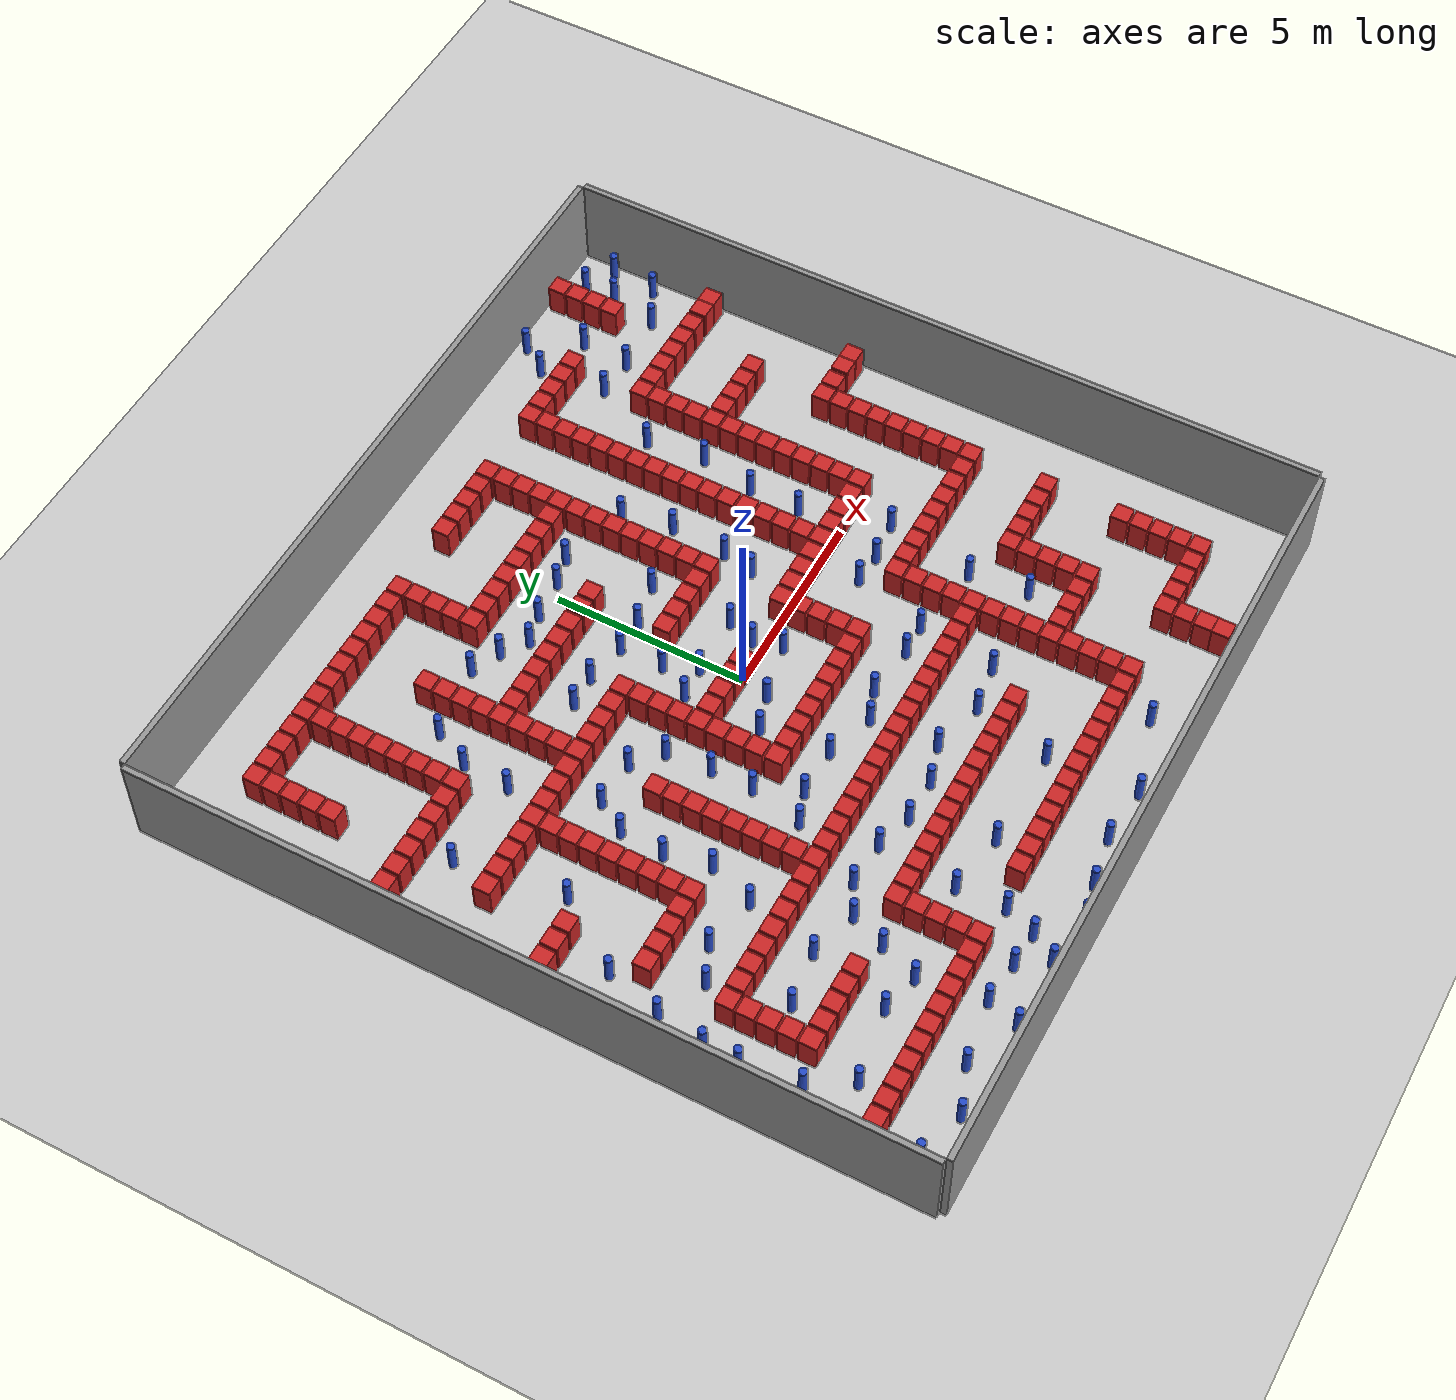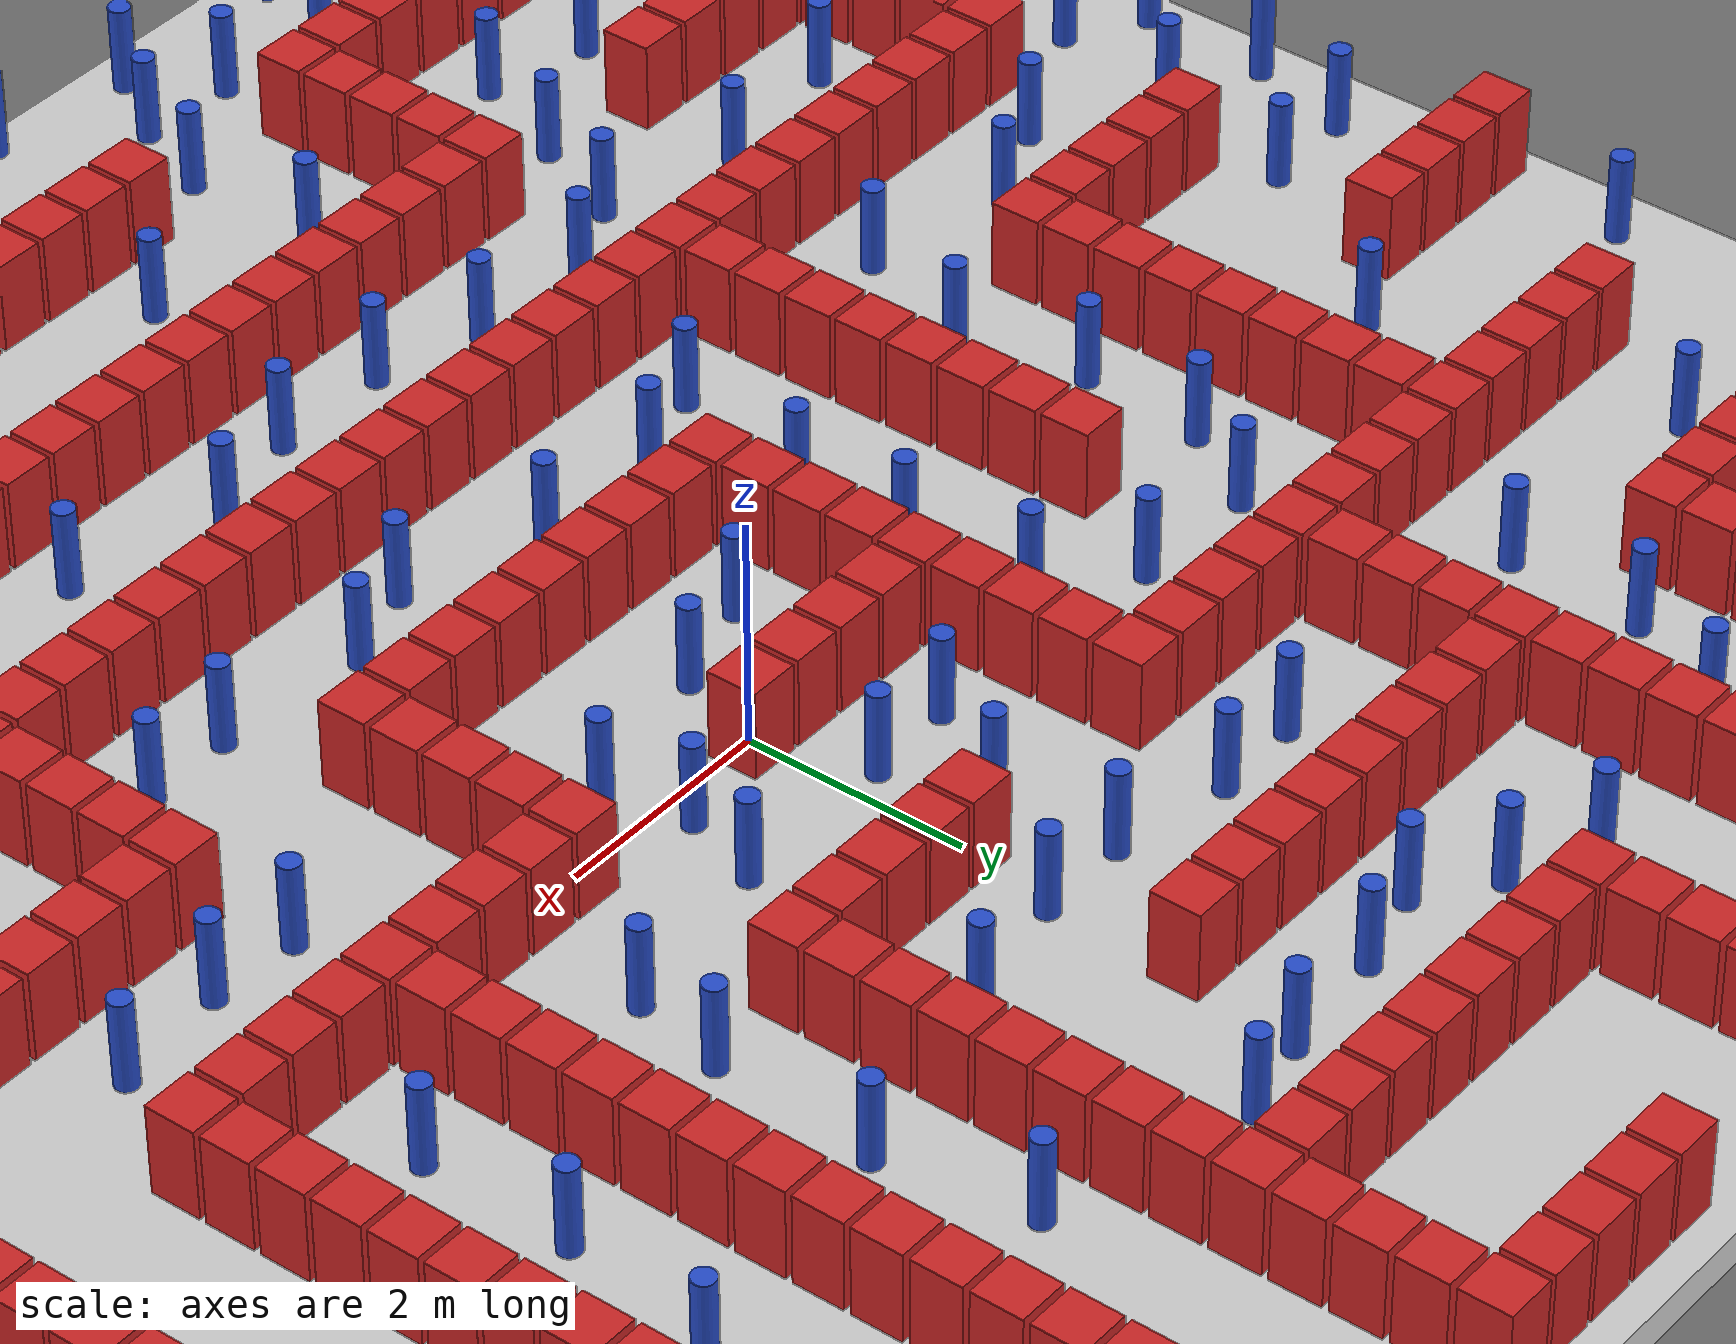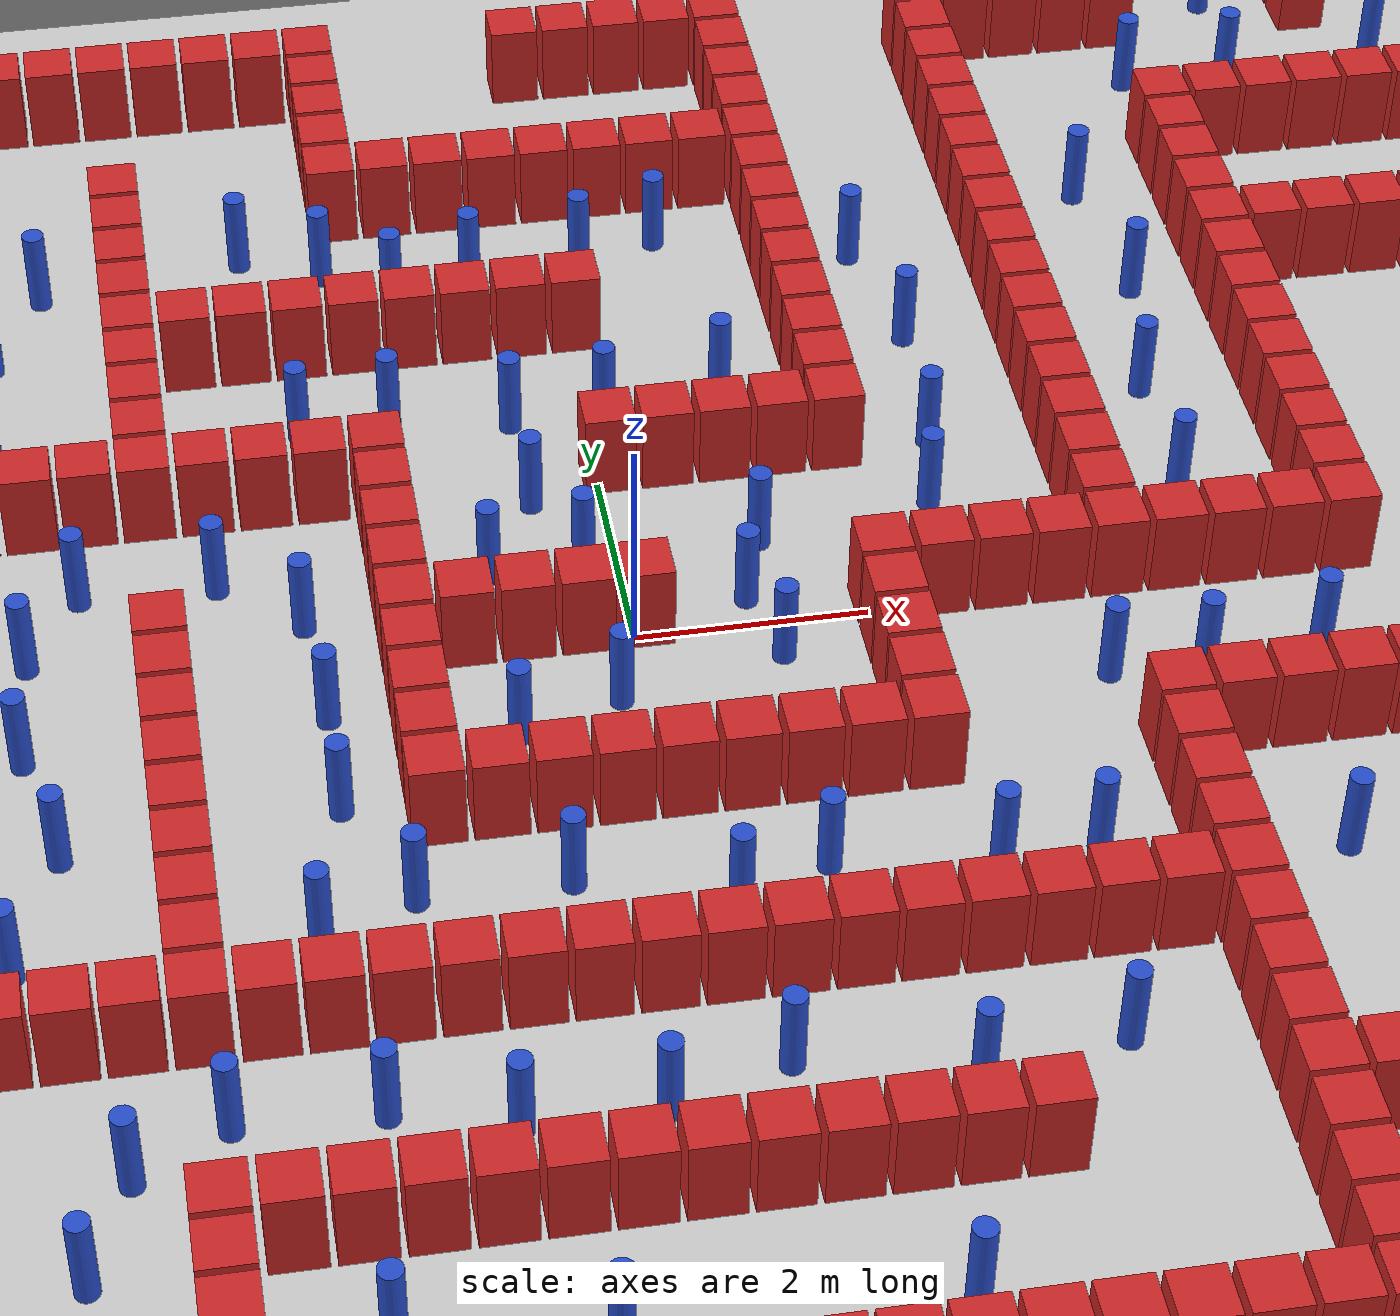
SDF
<sdf version="1.6">
 <world name="default">
  <light name="sun" type="directional">
   <pose>0 0 1000 0 -0 0</pose>
   <diffuse>0.8 0.8 0.8 1</diffuse>
   <specular>0.1 0.1 0.1 1</specular>
   <attenuation>
    <range>1000</range>
    <constant>0.9</constant>
    <linear>0.01</linear>
    <quadratic>0.001</quadratic>
   </attenuation>
   <direction>-0.5 0.5 -1</direction>
  </light>
  <model name="ground_plane">
   <static>1</static>
   <link name="link">
    <collision name="collision">
     <geometry><plane><normal>0 0 1</normal><size>100 100</size></plane></geometry>
     <surface><friction><ode><mu>100</mu><mu2>50</mu2></ode></friction></surface>
    </collision>
    <visual name="visual">
     <cast_shadows>0</cast_shadows>
     <geometry><plane><normal>0 0 1</normal><size>100 100</size></plane></geometry>
     <material>
      <script><uri>file://media/materials/scripts/gazebo.material</uri><name>Gazebo/Grey</name></script>
     </material>
    </visual>
   </link>
  </model>
  <gravity>0 0 -9.8</gravity>
  <magnetic_field>6e-06 2.3e-05 -4.2e-05</magnetic_field>
  <atmosphere type="adiabatic"/>
  <physics name="default_physics" default="0" type="ode">
   <max_step_size>0.001</max_step_size>
   <real_time_factor>1</real_time_factor>
   <real_time_update_rate>1000</real_time_update_rate>
  </physics>
  <scene><ambient>0.4 0.4 0.4 1</ambient><background>0.7 0.7 0.7 1</background><shadows>1</shadows></scene>
  <spherical_coordinates>
   <surface_model>EARTH_WGS84</surface_model>
   <latitude_deg>0</latitude_deg>
   <longitude_deg>0</longitude_deg>
   <elevation>0</elevation>
   <heading_deg>0</heading_deg>
  </spherical_coordinates>
  <model name="NamedLocations"><static>1</static><link name="DefaultStart"/></model>
  <model name="20x20_walls">
   <pose>0.044518 0.0211 0 0 -0 0</pose>
   <link name="Wall_1">
    <collision name="Wall_1_Collision">
     <geometry><box><size>20 0.15 2.5</size></box></geometry>
     <pose>0 0 1.25 0 -0 0</pose>
    </collision>
    <visual name="Wall_1_Visual">
     <pose>0 0 1.25 0 -0 0</pose>
     <geometry><box><size>20 0.15 2.5</size></box></geometry>
     <material>
      <script><uri>file://media/materials/scripts/gazebo.material</uri><name>Gazebo/Grey</name></script>
      <ambient>0.976471 0.992157 1 1</ambient>
     </material>
     <meta><layer>0</layer></meta>
    </visual>
    <pose>0 10.08 0 0 -0 0</pose>
   </link>
   <link name="Wall_3">
    <collision name="Wall_3_Collision">
     <geometry><box><size>20 0.15 2.5</size></box></geometry>
     <pose>0 0 1.25 0 -0 0</pose>
    </collision>
    <visual name="Wall_3_Visual">
     <pose>0 0 1.25 0 -0 0</pose>
     <geometry><box><size>20 0.15 2.5</size></box></geometry>
     <material>
      <script><uri>file://media/materials/scripts/gazebo.material</uri><name>Gazebo/Grey</name></script>
      <ambient>0.976471 0.992157 1 1</ambient>
     </material>
     <meta><layer>0</layer></meta>
    </visual>
    <pose>10.08 0 0 0 0 -1.5708</pose>
   </link>
   <link name="Wall_4">
    <collision name="Wall_4_Collision">
     <geometry><box><size>20 0.15 2.5</size></box></geometry>
     <pose>0 0 1.25 0 -0 0</pose>
    </collision>
    <visual name="Wall_4_Visual">
     <pose>0 0 1.25 0 -0 0</pose>
     <geometry><box><size>20 0.15 2.5</size></box></geometry>
     <material>
      <script><uri>file://media/materials/scripts/gazebo.material</uri><name>Gazebo/Grey</name></script>
      <ambient>0.976471 0.992157 1 1</ambient>
     </material>
     <meta><layer>0</layer></meta>
    </visual>
    <pose>0 -10.08 0 0 -0 3.14159</pose>
   </link>
   <link name="Wall_5">
    <collision name="Wall_5_Collision">
     <geometry><box><size>20 0.15 2.5</size></box></geometry>
     <pose>0 0 1.25 0 -0 0</pose>
    </collision>
    <visual name="Wall_5_Visual">
     <pose>0 0 1.25 0 -0 0</pose>
     <geometry><box><size>20 0.15 2.5</size></box></geometry>
     <material>
      <script><uri>file://media/materials/scripts/gazebo.material</uri><name>Gazebo/Grey</name></script>
      <ambient>0.976471 0.992157 1 1</ambient>
     </material>
     <meta><layer>0</layer></meta>
    </visual>
    <pose>-10.08 0 0 0 -0 1.5708</pose>
   </link>
   <static>1</static>
  </model>
  <model name="box_obstacle0">
   <static>0</static>
   <link name="box_obstacle">
    <pose>0 0 0.1 0 -0 0</pose>
    <inertial>
     <mass>100</mass>
     <inertia>
      <ixx>0.166667</ixx>
      <ixy>0</ixy>
      <ixz>0</ixz>
      <iyy>0.166667</iyy>
      <iyz>0</iyz>
      <izz>0.166667</izz>
     </inertia>
    </inertial>
    <collision name="collision"><geometry><box><size>0.45 0.45 0.8</size></box></geometry></collision>
    <visual name="visual">
     <geometry><box><size>0.45 0.45 0.8</size></box></geometry>
     <material>
      <script><name>Gazebo/Red</name><uri>file://media/materials/scripts/gazebo.material</uri></script>
     </material>
    </visual>
   </link>
   <pose>-9.49545 -7.98027 0.299997 -3e-06 5e-06 -4e-06</pose>
  </model>
  <model name="box_obstacle1">
   <static>0</static>
   <link name="box_obstacle">
    <pose>0 0 0.1 0 -0 0</pose>
    <inertial>
     <mass>100</mass>
     <inertia>
      <ixx>0.166667</ixx>
      <ixy>0</ixy>
      <ixz>0</ixz>
      <iyy>0.166667</iyy>
      <iyz>0</iyz>
      <izz>0.166667</izz>
     </inertia>
    </inertial>
    <collision name="collision"><geometry><box><size>0.45 0.45 0.8</size></box></geometry></collision>
    <visual name="visual">
     <geometry><box><size>0.45 0.45 0.8</size></box></geometry>
     <material>
      <script><name>Gazebo/Red</name><uri>file://media/materials/scripts/gazebo.material</uri></script>
     </material>
    </visual>
   </link>
   <pose>-9.49545 0.099728 0.299997 -3e-06 5e-06 -4e-06</pose>
  </model>
  <model name="box_obstacle2">
   <static>0</static>
   <link name="box_obstacle">
    <pose>0 0 0.1 0 -0 0</pose>
    <inertial>
     <mass>100</mass>
     <inertia>
      <ixx>0.166667</ixx>
      <ixy>0</ixy>
      <ixz>0</ixz>
      <iyy>0.166667</iyy>
      <iyz>0</iyz>
      <izz>0.166667</izz>
     </inertia>
    </inertial>
    <collision name="collision"><geometry><box><size>0.45 0.45 0.8</size></box></geometry></collision>
    <visual name="visual">
     <geometry><box><size>0.45 0.45 0.8</size></box></geometry>
     <material>
      <script><name>Gazebo/Red</name><uri>file://media/materials/scripts/gazebo.material</uri></script>
     </material>
    </visual>
   </link>
   <pose>-9.49545 4.13973 0.299997 -3e-06 5e-06 -4e-06</pose>
  </model>
  <model name="box_obstacle3">
   <static>0</static>
   <link name="box_obstacle">
    <pose>0 0 0.1 0 -0 0</pose>
    <inertial>
     <mass>100</mass>
     <inertia>
      <ixx>0.166667</ixx>
      <ixy>0</ixy>
      <ixz>0</ixz>
      <iyy>0.166667</iyy>
      <iyz>0</iyz>
      <izz>0.166667</izz>
     </inertia>
    </inertial>
    <collision name="collision"><geometry><box><size>0.45 0.45 0.8</size></box></geometry></collision>
    <visual name="visual">
     <geometry><box><size>0.45 0.45 0.8</size></box></geometry>
     <material>
      <script><name>Gazebo/Red</name><uri>file://media/materials/scripts/gazebo.material</uri></script>
     </material>
    </visual>
   </link>
   <pose>-8.99045 -7.98027 0.299997 -3e-06 5e-06 -4e-06</pose>
  </model>
  <model name="box_obstacle4">
   <static>0</static>
   <link name="box_obstacle">
    <pose>0 0 0.1 0 -0 0</pose>
    <inertial>
     <mass>100</mass>
     <inertia>
      <ixx>0.166667</ixx>
      <ixy>0</ixy>
      <ixz>0</ixz>
      <iyy>0.166667</iyy>
      <iyz>0</iyz>
      <izz>0.166667</izz>
     </inertia>
    </inertial>
    <collision name="collision"><geometry><box><size>0.45 0.45 0.8</size></box></geometry></collision>
    <visual name="visual">
     <geometry><box><size>0.45 0.45 0.8</size></box></geometry>
     <material>
      <script><name>Gazebo/Red</name><uri>file://media/materials/scripts/gazebo.material</uri></script>
     </material>
    </visual>
   </link>
   <pose>-8.99045 0.099728 0.299997 -3e-06 5e-06 -4e-06</pose>
  </model>
  <model name="box_obstacle5">
   <static>0</static>
   <link name="box_obstacle">
    <pose>0 0 0.1 0 -0 0</pose>
    <inertial>
     <mass>100</mass>
     <inertia>
      <ixx>0.166667</ixx>
      <ixy>0</ixy>
      <ixz>0</ixz>
      <iyy>0.166667</iyy>
      <iyz>0</iyz>
      <izz>0.166667</izz>
     </inertia>
    </inertial>
    <collision name="collision"><geometry><box><size>0.45 0.45 0.8</size></box></geometry></collision>
    <visual name="visual">
     <geometry><box><size>0.45 0.45 0.8</size></box></geometry>
     <material>
      <script><name>Gazebo/Red</name><uri>file://media/materials/scripts/gazebo.material</uri></script>
     </material>
    </visual>
   </link>
   <pose>-8.99045 4.13973 0.299997 -3e-06 5e-06 -4e-06</pose>
  </model>
  <model name="box_obstacle6">
   <static>0</static>
   <link name="box_obstacle">
    <pose>0 0 0.1 0 -0 0</pose>
    <inertial>
     <mass>100</mass>
     <inertia>
      <ixx>0.166667</ixx>
      <ixy>0</ixy>
      <ixz>0</ixz>
      <iyy>0.166667</iyy>
      <iyz>0</iyz>
      <izz>0.166667</izz>
     </inertia>
    </inertial>
    <collision name="collision"><geometry><box><size>0.45 0.45 0.8</size></box></geometry></collision>
    <visual name="visual">
     <geometry><box><size>0.45 0.45 0.8</size></box></geometry>
     <material>
      <script><name>Gazebo/Red</name><uri>file://media/materials/scripts/gazebo.material</uri></script>
     </material>
    </visual>
   </link>
   <pose>-8.48545 -7.98027 0.299997 -3e-06 5e-06 -4e-06</pose>
  </model>
  <model name="box_obstacle7">
   <static>0</static>
   <link name="box_obstacle">
    <pose>0 0 0.1 0 -0 0</pose>
    <inertial>
     <mass>100</mass>
     <inertia>
      <ixx>0.166667</ixx>
      <ixy>0</ixy>
      <ixz>0</ixz>
      <iyy>0.166667</iyy>
      <iyz>0</iyz>
      <izz>0.166667</izz>
     </inertia>
    </inertial>
    <collision name="collision"><geometry><box><size>0.45 0.45 0.8</size></box></geometry></collision>
    <visual name="visual">
     <geometry><box><size>0.45 0.45 0.8</size></box></geometry>
     <material>
      <script><name>Gazebo/Red</name><uri>file://media/materials/scripts/gazebo.material</uri></script>
     </material>
    </visual>
   </link>
   <pose>-8.48545 0.099728 0.299997 -3e-06 5e-06 -4e-06</pose>
  </model>
  <model name="box_obstacle8">
   <static>0</static>
   <link name="box_obstacle">
    <pose>0 0 0.1 0 -0 0</pose>
    <inertial>
     <mass>100</mass>
     <inertia>
      <ixx>0.166667</ixx>
      <ixy>0</ixy>
      <ixz>0</ixz>
      <iyy>0.166667</iyy>
      <iyz>0</iyz>
      <izz>0.166667</izz>
     </inertia>
    </inertial>
    <collision name="collision"><geometry><box><size>0.45 0.45 0.8</size></box></geometry></collision>
    <visual name="visual">
     <geometry><box><size>0.45 0.45 0.8</size></box></geometry>
     <material>
      <script><name>Gazebo/Red</name><uri>file://media/materials/scripts/gazebo.material</uri></script>
     </material>
    </visual>
   </link>
   <pose>-8.48545 4.13973 0.299997 -3e-06 5e-06 -4e-06</pose>
  </model>
  <model name="box_obstacle9">
   <static>0</static>
   <link name="box_obstacle">
    <pose>0 0 0.1 0 -0 0</pose>
    <inertial>
     <mass>100</mass>
     <inertia>
      <ixx>0.166667</ixx>
      <ixy>0</ixy>
      <ixz>0</ixz>
      <iyy>0.166667</iyy>
      <iyz>0</iyz>
      <izz>0.166667</izz>
     </inertia>
    </inertial>
    <collision name="collision"><geometry><box><size>0.45 0.45 0.8</size></box></geometry></collision>
    <visual name="visual">
     <geometry><box><size>0.45 0.45 0.8</size></box></geometry>
     <material>
      <script><name>Gazebo/Red</name><uri>file://media/materials/scripts/gazebo.material</uri></script>
     </material>
    </visual>
   </link>
   <pose>-7.98045 -7.98027 0.299997 -3e-06 5e-06 -4e-06</pose>
  </model>
  <model name="box_obstacle10">
   <static>0</static>
   <link name="box_obstacle">
    <pose>0 0 0.1 0 -0 0</pose>
    <inertial>
     <mass>100</mass>
     <inertia>
      <ixx>0.166667</ixx>
      <ixy>0</ixy>
      <ixz>0</ixz>
      <iyy>0.166667</iyy>
      <iyz>0</iyz>
      <izz>0.166667</izz>
     </inertia>
    </inertial>
    <collision name="collision"><geometry><box><size>0.45 0.45 0.8</size></box></geometry></collision>
    <visual name="visual">
     <geometry><box><size>0.45 0.45 0.8</size></box></geometry>
     <material>
      <script><name>Gazebo/Red</name><uri>file://media/materials/scripts/gazebo.material</uri></script>
     </material>
    </visual>
   </link>
   <pose>-7.98045 -5.96027 0.299997 -3e-06 5e-06 -4e-06</pose>
  </model>
  <model name="box_obstacle11">
   <static>0</static>
   <link name="box_obstacle">
    <pose>0 0 0.1 0 -0 0</pose>
    <inertial>
     <mass>100</mass>
     <inertia>
      <ixx>0.166667</ixx>
      <ixy>0</ixy>
      <ixz>0</ixz>
      <iyy>0.166667</iyy>
      <iyz>0</iyz>
      <izz>0.166667</izz>
     </inertia>
    </inertial>
    <collision name="collision"><geometry><box><size>0.45 0.45 0.8</size></box></geometry></collision>
    <visual name="visual">
     <geometry><box><size>0.45 0.45 0.8</size></box></geometry>
     <material>
      <script><name>Gazebo/Red</name><uri>file://media/materials/scripts/gazebo.material</uri></script>
     </material>
    </visual>
   </link>
   <pose>-7.98045 -5.45527 0.299997 -3e-06 5e-06 -4e-06</pose>
  </model>
  <model name="box_obstacle12">
   <static>0</static>
   <link name="box_obstacle">
    <pose>0 0 0.1 0 -0 0</pose>
    <inertial>
     <mass>100</mass>
     <inertia>
      <ixx>0.166667</ixx>
      <ixy>0</ixy>
      <ixz>0</ixz>
      <iyy>0.166667</iyy>
      <iyz>0</iyz>
      <izz>0.166667</izz>
     </inertia>
    </inertial>
    <collision name="collision"><geometry><box><size>0.45 0.45 0.8</size></box></geometry></collision>
    <visual name="visual">
     <geometry><box><size>0.45 0.45 0.8</size></box></geometry>
     <material>
      <script><name>Gazebo/Red</name><uri>file://media/materials/scripts/gazebo.material</uri></script>
     </material>
    </visual>
   </link>
   <pose>-7.98045 -4.95027 0.299997 -3e-06 5e-06 -4e-06</pose>
  </model>
  <model name="box_obstacle13">
   <static>0</static>
   <link name="box_obstacle">
    <pose>0 0 0.1 0 -0 0</pose>
    <inertial>
     <mass>100</mass>
     <inertia>
      <ixx>0.166667</ixx>
      <ixy>0</ixy>
      <ixz>0</ixz>
      <iyy>0.166667</iyy>
      <iyz>0</iyz>
      <izz>0.166667</izz>
     </inertia>
    </inertial>
    <collision name="collision"><geometry><box><size>0.45 0.45 0.8</size></box></geometry></collision>
    <visual name="visual">
     <geometry><box><size>0.45 0.45 0.8</size></box></geometry>
     <material>
      <script><name>Gazebo/Red</name><uri>file://media/materials/scripts/gazebo.material</uri></script>
     </material>
    </visual>
   </link>
   <pose>-7.98045 -4.44527 0.299997 -3e-06 5e-06 -4e-06</pose>
  </model>
  <model name="box_obstacle14">
   <static>0</static>
   <link name="box_obstacle">
    <pose>0 0 0.1 0 -0 0</pose>
    <inertial>
     <mass>100</mass>
     <inertia>
      <ixx>0.166667</ixx>
      <ixy>0</ixy>
      <ixz>0</ixz>
      <iyy>0.166667</iyy>
      <iyz>0</iyz>
      <izz>0.166667</izz>
     </inertia>
    </inertial>
    <collision name="collision"><geometry><box><size>0.45 0.45 0.8</size></box></geometry></collision>
    <visual name="visual">
     <geometry><box><size>0.45 0.45 0.8</size></box></geometry>
     <material>
      <script><name>Gazebo/Red</name><uri>file://media/materials/scripts/gazebo.material</uri></script>
     </material>
    </visual>
   </link>
   <pose>-7.98045 -3.94027 0.299997 -3e-06 5e-06 -4e-06</pose>
  </model>
  <model name="box_obstacle15">
   <static>0</static>
   <link name="box_obstacle">
    <pose>0 0 0.1 0 -0 0</pose>
    <inertial>
     <mass>100</mass>
     <inertia>
      <ixx>0.166667</ixx>
      <ixy>0</ixy>
      <ixz>0</ixz>
      <iyy>0.166667</iyy>
      <iyz>0</iyz>
      <izz>0.166667</izz>
     </inertia>
    </inertial>
    <collision name="collision"><geometry><box><size>0.45 0.45 0.8</size></box></geometry></collision>
    <visual name="visual">
     <geometry><box><size>0.45 0.45 0.8</size></box></geometry>
     <material>
      <script><name>Gazebo/Red</name><uri>file://media/materials/scripts/gazebo.material</uri></script>
     </material>
    </visual>
   </link>
   <pose>-7.98045 -1.92027 0.299997 -3e-06 5e-06 -4e-06</pose>
  </model>
  <model name="box_obstacle16">
   <static>0</static>
   <link name="box_obstacle">
    <pose>0 0 0.1 0 -0 0</pose>
    <inertial>
     <mass>100</mass>
     <inertia>
      <ixx>0.166667</ixx>
      <ixy>0</ixy>
      <ixz>0</ixz>
      <iyy>0.166667</iyy>
      <iyz>0</iyz>
      <izz>0.166667</izz>
     </inertia>
    </inertial>
    <collision name="collision"><geometry><box><size>0.45 0.45 0.8</size></box></geometry></collision>
    <visual name="visual">
     <geometry><box><size>0.45 0.45 0.8</size></box></geometry>
     <material>
      <script><name>Gazebo/Red</name><uri>file://media/materials/scripts/gazebo.material</uri></script>
     </material>
    </visual>
   </link>
   <pose>-7.98045 0.099728 0.299997 -3e-06 5e-06 -4e-06</pose>
  </model>
  <model name="box_obstacle17">
   <static>0</static>
   <link name="box_obstacle">
    <pose>0 0 0.1 0 -0 0</pose>
    <inertial>
     <mass>100</mass>
     <inertia>
      <ixx>0.166667</ixx>
      <ixy>0</ixy>
      <ixz>0</ixz>
      <iyy>0.166667</iyy>
      <iyz>0</iyz>
      <izz>0.166667</izz>
     </inertia>
    </inertial>
    <collision name="collision"><geometry><box><size>0.45 0.45 0.8</size></box></geometry></collision>
    <visual name="visual">
     <geometry><box><size>0.45 0.45 0.8</size></box></geometry>
     <material>
      <script><name>Gazebo/Red</name><uri>file://media/materials/scripts/gazebo.material</uri></script>
     </material>
    </visual>
   </link>
   <pose>-7.98045 2.11973 0.299997 -3e-06 5e-06 -4e-06</pose>
  </model>
  <model name="box_obstacle18">
   <static>0</static>
   <link name="box_obstacle">
    <pose>0 0 0.1 0 -0 0</pose>
    <inertial>
     <mass>100</mass>
     <inertia>
      <ixx>0.166667</ixx>
      <ixy>0</ixy>
      <ixz>0</ixz>
      <iyy>0.166667</iyy>
      <iyz>0</iyz>
      <izz>0.166667</izz>
     </inertia>
    </inertial>
    <collision name="collision"><geometry><box><size>0.45 0.45 0.8</size></box></geometry></collision>
    <visual name="visual">
     <geometry><box><size>0.45 0.45 0.8</size></box></geometry>
     <material>
      <script><name>Gazebo/Red</name><uri>file://media/materials/scripts/gazebo.material</uri></script>
     </material>
    </visual>
   </link>
   <pose>-7.98045 4.13973 0.299997 -3e-06 5e-06 -4e-06</pose>
  </model>
  <model name="box_obstacle19">
   <static>0</static>
   <link name="box_obstacle">
    <pose>0 0 0.1 0 -0 0</pose>
    <inertial>
     <mass>100</mass>
     <inertia>
      <ixx>0.166667</ixx>
      <ixy>0</ixy>
      <ixz>0</ixz>
      <iyy>0.166667</iyy>
      <iyz>0</iyz>
      <izz>0.166667</izz>
     </inertia>
    </inertial>
    <collision name="collision"><geometry><box><size>0.45 0.45 0.8</size></box></geometry></collision>
    <visual name="visual">
     <geometry><box><size>0.45 0.45 0.8</size></box></geometry>
     <material>
      <script><name>Gazebo/Red</name><uri>file://media/materials/scripts/gazebo.material</uri></script>
     </material>
    </visual>
   </link>
   <pose>-7.98045 6.15973 0.299997 -3e-06 5e-06 -4e-06</pose>
  </model>
  <model name="box_obstacle20">
   <static>0</static>
   <link name="box_obstacle">
    <pose>0 0 0.1 0 -0 0</pose>
    <inertial>
     <mass>100</mass>
     <inertia>
      <ixx>0.166667</ixx>
      <ixy>0</ixy>
      <ixz>0</ixz>
      <iyy>0.166667</iyy>
      <iyz>0</iyz>
      <izz>0.166667</izz>
     </inertia>
    </inertial>
    <collision name="collision"><geometry><box><size>0.45 0.45 0.8</size></box></geometry></collision>
    <visual name="visual">
     <geometry><box><size>0.45 0.45 0.8</size></box></geometry>
     <material>
      <script><name>Gazebo/Red</name><uri>file://media/materials/scripts/gazebo.material</uri></script>
     </material>
    </visual>
   </link>
   <pose>-7.98045 6.66473 0.299997 -3e-06 5e-06 -4e-06</pose>
  </model>
  <model name="box_obstacle21">
   <static>0</static>
   <link name="box_obstacle">
    <pose>0 0 0.1 0 -0 0</pose>
    <inertial>
     <mass>100</mass>
     <inertia>
      <ixx>0.166667</ixx>
      <ixy>0</ixy>
      <ixz>0</ixz>
      <iyy>0.166667</iyy>
      <iyz>0</iyz>
      <izz>0.166667</izz>
     </inertia>
    </inertial>
    <collision name="collision"><geometry><box><size>0.45 0.45 0.8</size></box></geometry></collision>
    <visual name="visual">
     <geometry><box><size>0.45 0.45 0.8</size></box></geometry>
     <material>
      <script><name>Gazebo/Red</name><uri>file://media/materials/scripts/gazebo.material</uri></script>
     </material>
    </visual>
   </link>
   <pose>-7.98045 7.16973 0.299997 -3e-06 5e-06 -4e-06</pose>
  </model>
  <model name="box_obstacle22">
   <static>0</static>
   <link name="box_obstacle">
    <pose>0 0 0.1 0 -0 0</pose>
    <inertial>
     <mass>100</mass>
     <inertia>
      <ixx>0.166667</ixx>
      <ixy>0</ixy>
      <ixz>0</ixz>
      <iyy>0.166667</iyy>
      <iyz>0</iyz>
      <izz>0.166667</izz>
     </inertia>
    </inertial>
    <collision name="collision"><geometry><box><size>0.45 0.45 0.8</size></box></geometry></collision>
    <visual name="visual">
     <geometry><box><size>0.45 0.45 0.8</size></box></geometry>
     <material>
      <script><name>Gazebo/Red</name><uri>file://media/materials/scripts/gazebo.material</uri></script>
     </material>
    </visual>
   </link>
   <pose>-7.98045 7.67473 0.299997 -3e-06 5e-06 -4e-06</pose>
  </model>
  <model name="box_obstacle23">
   <static>0</static>
   <link name="box_obstacle">
    <pose>0 0 0.1 0 -0 0</pose>
    <inertial>
     <mass>100</mass>
     <inertia>
      <ixx>0.166667</ixx>
      <ixy>0</ixy>
      <ixz>0</ixz>
      <iyy>0.166667</iyy>
      <iyz>0</iyz>
      <izz>0.166667</izz>
     </inertia>
    </inertial>
    <collision name="collision"><geometry><box><size>0.45 0.45 0.8</size></box></geometry></collision>
    <visual name="visual">
     <geometry><box><size>0.45 0.45 0.8</size></box></geometry>
     <material>
      <script><name>Gazebo/Red</name><uri>file://media/materials/scripts/gazebo.material</uri></script>
     </material>
    </visual>
   </link>
   <pose>-7.98045 8.17973 0.299997 -3e-06 5e-06 -4e-06</pose>
  </model>
  <model name="box_obstacle24">
   <static>0</static>
   <link name="box_obstacle">
    <pose>0 0 0.1 0 -0 0</pose>
    <inertial>
     <mass>100</mass>
     <inertia>
      <ixx>0.166667</ixx>
      <ixy>0</ixy>
      <ixz>0</ixz>
      <iyy>0.166667</iyy>
      <iyz>0</iyz>
      <izz>0.166667</izz>
     </inertia>
    </inertial>
    <collision name="collision"><geometry><box><size>0.45 0.45 0.8</size></box></geometry></collision>
    <visual name="visual">
     <geometry><box><size>0.45 0.45 0.8</size></box></geometry>
     <material>
      <script><name>Gazebo/Red</name><uri>file://media/materials/scripts/gazebo.material</uri></script>
     </material>
    </visual>
   </link>
   <pose>-7.47545 -7.98027 0.299997 -3e-06 5e-06 -4e-06</pose>
  </model>
  <model name="box_obstacle25">
   <static>0</static>
   <link name="box_obstacle">
    <pose>0 0 0.1 0 -0 0</pose>
    <inertial>
     <mass>100</mass>
     <inertia>
      <ixx>0.166667</ixx>
      <ixy>0</ixy>
      <ixz>0</ixz>
      <iyy>0.166667</iyy>
      <iyz>0</iyz>
      <izz>0.166667</izz>
     </inertia>
    </inertial>
    <collision name="collision"><geometry><box><size>0.45 0.45 0.8</size></box></geometry></collision>
    <visual name="visual">
     <geometry><box><size>0.45 0.45 0.8</size></box></geometry>
     <material>
      <script><name>Gazebo/Red</name><uri>file://media/materials/scripts/gazebo.material</uri></script>
     </material>
    </visual>
   </link>
   <pose>-7.47545 -5.96027 0.299997 -3e-06 5e-06 -4e-06</pose>
  </model>
  <model name="box_obstacle26">
   <static>0</static>
   <link name="box_obstacle">
    <pose>0 0 0.1 0 -0 0</pose>
    <inertial>
     <mass>100</mass>
     <inertia>
      <ixx>0.166667</ixx>
      <ixy>0</ixy>
      <ixz>0</ixz>
      <iyy>0.166667</iyy>
      <iyz>0</iyz>
      <izz>0.166667</izz>
     </inertia>
    </inertial>
    <collision name="collision"><geometry><box><size>0.45 0.45 0.8</size></box></geometry></collision>
    <visual name="visual">
     <geometry><box><size>0.45 0.45 0.8</size></box></geometry>
     <material>
      <script><name>Gazebo/Red</name><uri>file://media/materials/scripts/gazebo.material</uri></script>
     </material>
    </visual>
   </link>
   <pose>-7.47545 -3.94027 0.299997 -3e-06 5e-06 -4e-06</pose>
  </model>
  <model name="box_obstacle27">
   <static>0</static>
   <link name="box_obstacle">
    <pose>0 0 0.1 0 -0 0</pose>
    <inertial>
     <mass>100</mass>
     <inertia>
      <ixx>0.166667</ixx>
      <ixy>0</ixy>
      <ixz>0</ixz>
      <iyy>0.166667</iyy>
      <iyz>0</iyz>
      <izz>0.166667</izz>
     </inertia>
    </inertial>
    <collision name="collision"><geometry><box><size>0.45 0.45 0.8</size></box></geometry></collision>
    <visual name="visual">
     <geometry><box><size>0.45 0.45 0.8</size></box></geometry>
     <material>
      <script><name>Gazebo/Red</name><uri>file://media/materials/scripts/gazebo.material</uri></script>
     </material>
    </visual>
   </link>
   <pose>-7.47545 -1.92027 0.299997 -3e-06 5e-06 -4e-06</pose>
  </model>
  <model name="box_obstacle28">
   <static>0</static>
   <link name="box_obstacle">
    <pose>0 0 0.1 0 -0 0</pose>
    <inertial>
     <mass>100</mass>
     <inertia>
      <ixx>0.166667</ixx>
      <ixy>0</ixy>
      <ixz>0</ixz>
      <iyy>0.166667</iyy>
      <iyz>0</iyz>
      <izz>0.166667</izz>
     </inertia>
    </inertial>
    <collision name="collision"><geometry><box><size>0.45 0.45 0.8</size></box></geometry></collision>
    <visual name="visual">
     <geometry><box><size>0.45 0.45 0.8</size></box></geometry>
     <material>
      <script><name>Gazebo/Red</name><uri>file://media/materials/scripts/gazebo.material</uri></script>
     </material>
    </visual>
   </link>
   <pose>-7.47545 2.11973 0.299997 -3e-06 5e-06 -4e-06</pose>
  </model>
  <model name="box_obstacle29">
   <static>0</static>
   <link name="box_obstacle">
    <pose>0 0 0.1 0 -0 0</pose>
    <inertial>
     <mass>100</mass>
     <inertia>
      <ixx>0.166667</ixx>
      <ixy>0</ixy>
      <ixz>0</ixz>
      <iyy>0.166667</iyy>
      <iyz>0</iyz>
      <izz>0.166667</izz>
     </inertia>
    </inertial>
    <collision name="collision"><geometry><box><size>0.45 0.45 0.8</size></box></geometry></collision>
    <visual name="visual">
     <geometry><box><size>0.45 0.45 0.8</size></box></geometry>
     <material>
      <script><name>Gazebo/Red</name><uri>file://media/materials/scripts/gazebo.material</uri></script>
     </material>
    </visual>
   </link>
   <pose>-7.47545 4.13973 0.299997 -3e-06 5e-06 -4e-06</pose>
  </model>
  <model name="box_obstacle30">
   <static>0</static>
   <link name="box_obstacle">
    <pose>0 0 0.1 0 -0 0</pose>
    <inertial>
     <mass>100</mass>
     <inertia>
      <ixx>0.166667</ixx>
      <ixy>0</ixy>
      <ixz>0</ixz>
      <iyy>0.166667</iyy>
      <iyz>0</iyz>
      <izz>0.166667</izz>
     </inertia>
    </inertial>
    <collision name="collision"><geometry><box><size>0.45 0.45 0.8</size></box></geometry></collision>
    <visual name="visual">
     <geometry><box><size>0.45 0.45 0.8</size></box></geometry>
     <material>
      <script><name>Gazebo/Red</name><uri>file://media/materials/scripts/gazebo.material</uri></script>
     </material>
    </visual>
   </link>
   <pose>-7.47545 8.17973 0.299997 -3e-06 5e-06 -4e-06</pose>
  </model>
  <model name="box_obstacle31">
   <static>0</static>
   <link name="box_obstacle">
    <pose>0 0 0.1 0 -0 0</pose>
    <inertial>
     <mass>100</mass>
     <inertia>
      <ixx>0.166667</ixx>
      <ixy>0</ixy>
      <ixz>0</ixz>
      <iyy>0.166667</iyy>
      <iyz>0</iyz>
      <izz>0.166667</izz>
     </inertia>
    </inertial>
    <collision name="collision"><geometry><box><size>0.45 0.45 0.8</size></box></geometry></collision>
    <visual name="visual">
     <geometry><box><size>0.45 0.45 0.8</size></box></geometry>
     <material>
      <script><name>Gazebo/Red</name><uri>file://media/materials/scripts/gazebo.material</uri></script>
     </material>
    </visual>
   </link>
   <pose>-6.97045 -7.98027 0.299997 -3e-06 5e-06 -4e-06</pose>
  </model>
  <model name="box_obstacle32">
   <static>0</static>
   <link name="box_obstacle">
    <pose>0 0 0.1 0 -0 0</pose>
    <inertial>
     <mass>100</mass>
     <inertia>
      <ixx>0.166667</ixx>
      <ixy>0</ixy>
      <ixz>0</ixz>
      <iyy>0.166667</iyy>
      <iyz>0</iyz>
      <izz>0.166667</izz>
     </inertia>
    </inertial>
    <collision name="collision"><geometry><box><size>0.45 0.45 0.8</size></box></geometry></collision>
    <visual name="visual">
     <geometry><box><size>0.45 0.45 0.8</size></box></geometry>
     <material>
      <script><name>Gazebo/Red</name><uri>file://media/materials/scripts/gazebo.material</uri></script>
     </material>
    </visual>
   </link>
   <pose>-6.97045 -5.96027 0.299997 -3e-06 5e-06 -4e-06</pose>
  </model>
  <model name="box_obstacle33">
   <static>0</static>
   <link name="box_obstacle">
    <pose>0 0 0.1 0 -0 0</pose>
    <inertial>
     <mass>100</mass>
     <inertia>
      <ixx>0.166667</ixx>
      <ixy>0</ixy>
      <ixz>0</ixz>
      <iyy>0.166667</iyy>
      <iyz>0</iyz>
      <izz>0.166667</izz>
     </inertia>
    </inertial>
    <collision name="collision"><geometry><box><size>0.45 0.45 0.8</size></box></geometry></collision>
    <visual name="visual">
     <geometry><box><size>0.45 0.45 0.8</size></box></geometry>
     <material>
      <script><name>Gazebo/Red</name><uri>file://media/materials/scripts/gazebo.material</uri></script>
     </material>
    </visual>
   </link>
   <pose>-6.97045 -3.94027 0.299997 -3e-06 5e-06 -4e-06</pose>
  </model>
  <model name="box_obstacle34">
   <static>0</static>
   <link name="box_obstacle">
    <pose>0 0 0.1 0 -0 0</pose>
    <inertial>
     <mass>100</mass>
     <inertia>
      <ixx>0.166667</ixx>
      <ixy>0</ixy>
      <ixz>0</ixz>
      <iyy>0.166667</iyy>
      <iyz>0</iyz>
      <izz>0.166667</izz>
     </inertia>
    </inertial>
    <collision name="collision"><geometry><box><size>0.45 0.45 0.8</size></box></geometry></collision>
    <visual name="visual">
     <geometry><box><size>0.45 0.45 0.8</size></box></geometry>
     <material>
      <script><name>Gazebo/Red</name><uri>file://media/materials/scripts/gazebo.material</uri></script>
     </material>
    </visual>
   </link>
   <pose>-6.97045 -1.92027 0.299997 -3e-06 5e-06 -4e-06</pose>
  </model>
  <model name="box_obstacle35">
   <static>0</static>
   <link name="box_obstacle">
    <pose>0 0 0.1 0 -0 0</pose>
    <inertial>
     <mass>100</mass>
     <inertia>
      <ixx>0.166667</ixx>
      <ixy>0</ixy>
      <ixz>0</ixz>
      <iyy>0.166667</iyy>
      <iyz>0</iyz>
      <izz>0.166667</izz>
     </inertia>
    </inertial>
    <collision name="collision"><geometry><box><size>0.45 0.45 0.8</size></box></geometry></collision>
    <visual name="visual">
     <geometry><box><size>0.45 0.45 0.8</size></box></geometry>
     <material>
      <script><name>Gazebo/Red</name><uri>file://media/materials/scripts/gazebo.material</uri></script>
     </material>
    </visual>
   </link>
   <pose>-6.97045 2.11973 0.299997 -3e-06 5e-06 -4e-06</pose>
  </model>
  <model name="box_obstacle36">
   <static>0</static>
   <link name="box_obstacle">
    <pose>0 0 0.1 0 -0 0</pose>
    <inertial>
     <mass>100</mass>
     <inertia>
      <ixx>0.166667</ixx>
      <ixy>0</ixy>
      <ixz>0</ixz>
      <iyy>0.166667</iyy>
      <iyz>0</iyz>
      <izz>0.166667</izz>
     </inertia>
    </inertial>
    <collision name="collision"><geometry><box><size>0.45 0.45 0.8</size></box></geometry></collision>
    <visual name="visual">
     <geometry><box><size>0.45 0.45 0.8</size></box></geometry>
     <material>
      <script><name>Gazebo/Red</name><uri>file://media/materials/scripts/gazebo.material</uri></script>
     </material>
    </visual>
   </link>
   <pose>-6.97045 4.13973 0.299997 -3e-06 5e-06 -4e-06</pose>
  </model>
  <model name="box_obstacle37">
   <static>0</static>
   <link name="box_obstacle">
    <pose>0 0 0.1 0 -0 0</pose>
    <inertial>
     <mass>100</mass>
     <inertia>
      <ixx>0.166667</ixx>
      <ixy>0</ixy>
      <ixz>0</ixz>
      <iyy>0.166667</iyy>
      <iyz>0</iyz>
      <izz>0.166667</izz>
     </inertia>
    </inertial>
    <collision name="collision"><geometry><box><size>0.45 0.45 0.8</size></box></geometry></collision>
    <visual name="visual">
     <geometry><box><size>0.45 0.45 0.8</size></box></geometry>
     <material>
      <script><name>Gazebo/Red</name><uri>file://media/materials/scripts/gazebo.material</uri></script>
     </material>
    </visual>
   </link>
   <pose>-6.97045 8.17973 0.299997 -3e-06 5e-06 -4e-06</pose>
  </model>
  <model name="box_obstacle38">
   <static>0</static>
   <link name="box_obstacle">
    <pose>0 0 0.1 0 -0 0</pose>
    <inertial>
     <mass>100</mass>
     <inertia>
      <ixx>0.166667</ixx>
      <ixy>0</ixy>
      <ixz>0</ixz>
      <iyy>0.166667</iyy>
      <iyz>0</iyz>
      <izz>0.166667</izz>
     </inertia>
    </inertial>
    <collision name="collision"><geometry><box><size>0.45 0.45 0.8</size></box></geometry></collision>
    <visual name="visual">
     <geometry><box><size>0.45 0.45 0.8</size></box></geometry>
     <material>
      <script><name>Gazebo/Red</name><uri>file://media/materials/scripts/gazebo.material</uri></script>
     </material>
    </visual>
   </link>
   <pose>-6.46545 -7.98027 0.299997 -3e-06 5e-06 -4e-06</pose>
  </model>
  <model name="box_obstacle39">
   <static>0</static>
   <link name="box_obstacle">
    <pose>0 0 0.1 0 -0 0</pose>
    <inertial>
     <mass>100</mass>
     <inertia>
      <ixx>0.166667</ixx>
      <ixy>0</ixy>
      <ixz>0</ixz>
      <iyy>0.166667</iyy>
      <iyz>0</iyz>
      <izz>0.166667</izz>
     </inertia>
    </inertial>
    <collision name="collision"><geometry><box><size>0.45 0.45 0.8</size></box></geometry></collision>
    <visual name="visual">
     <geometry><box><size>0.45 0.45 0.8</size></box></geometry>
     <material>
      <script><name>Gazebo/Red</name><uri>file://media/materials/scripts/gazebo.material</uri></script>
     </material>
    </visual>
   </link>
   <pose>-6.46545 -5.96027 0.299997 -3e-06 5e-06 -4e-06</pose>
  </model>
  <model name="box_obstacle40">
   <static>0</static>
   <link name="box_obstacle">
    <pose>0 0 0.1 0 -0 0</pose>
    <inertial>
     <mass>100</mass>
     <inertia>
      <ixx>0.166667</ixx>
      <ixy>0</ixy>
      <ixz>0</ixz>
      <iyy>0.166667</iyy>
      <iyz>0</iyz>
      <izz>0.166667</izz>
     </inertia>
    </inertial>
    <collision name="collision"><geometry><box><size>0.45 0.45 0.8</size></box></geometry></collision>
    <visual name="visual">
     <geometry><box><size>0.45 0.45 0.8</size></box></geometry>
     <material>
      <script><name>Gazebo/Red</name><uri>file://media/materials/scripts/gazebo.material</uri></script>
     </material>
    </visual>
   </link>
   <pose>-6.46545 -3.94027 0.299997 -3e-06 5e-06 -4e-06</pose>
  </model>
  <model name="box_obstacle41">
   <static>0</static>
   <link name="box_obstacle">
    <pose>0 0 0.1 0 -0 0</pose>
    <inertial>
     <mass>100</mass>
     <inertia>
      <ixx>0.166667</ixx>
      <ixy>0</ixy>
      <ixz>0</ixz>
      <iyy>0.166667</iyy>
      <iyz>0</iyz>
      <izz>0.166667</izz>
     </inertia>
    </inertial>
    <collision name="collision"><geometry><box><size>0.45 0.45 0.8</size></box></geometry></collision>
    <visual name="visual">
     <geometry><box><size>0.45 0.45 0.8</size></box></geometry>
     <material>
      <script><name>Gazebo/Red</name><uri>file://media/materials/scripts/gazebo.material</uri></script>
     </material>
    </visual>
   </link>
   <pose>-6.46545 -1.92027 0.299997 -3e-06 5e-06 -4e-06</pose>
  </model>
  <model name="box_obstacle42">
   <static>0</static>
   <link name="box_obstacle">
    <pose>0 0 0.1 0 -0 0</pose>
    <inertial>
     <mass>100</mass>
     <inertia>
      <ixx>0.166667</ixx>
      <ixy>0</ixy>
      <ixz>0</ixz>
      <iyy>0.166667</iyy>
      <iyz>0</iyz>
      <izz>0.166667</izz>
     </inertia>
    </inertial>
    <collision name="collision"><geometry><box><size>0.45 0.45 0.8</size></box></geometry></collision>
    <visual name="visual">
     <geometry><box><size>0.45 0.45 0.8</size></box></geometry>
     <material>
      <script><name>Gazebo/Red</name><uri>file://media/materials/scripts/gazebo.material</uri></script>
     </material>
    </visual>
   </link>
   <pose>-6.46545 2.11973 0.299997 -3e-06 5e-06 -4e-06</pose>
  </model>
  <model name="box_obstacle43">
   <static>0</static>
   <link name="box_obstacle">
    <pose>0 0 0.1 0 -0 0</pose>
    <inertial>
     <mass>100</mass>
     <inertia>
      <ixx>0.166667</ixx>
      <ixy>0</ixy>
      <ixz>0</ixz>
      <iyy>0.166667</iyy>
      <iyz>0</iyz>
      <izz>0.166667</izz>
     </inertia>
    </inertial>
    <collision name="collision"><geometry><box><size>0.45 0.45 0.8</size></box></geometry></collision>
    <visual name="visual">
     <geometry><box><size>0.45 0.45 0.8</size></box></geometry>
     <material>
      <script><name>Gazebo/Red</name><uri>file://media/materials/scripts/gazebo.material</uri></script>
     </material>
    </visual>
   </link>
   <pose>-6.46545 4.13973 0.299997 -3e-06 5e-06 -4e-06</pose>
  </model>
  <model name="box_obstacle44">
   <static>0</static>
   <link name="box_obstacle">
    <pose>0 0 0.1 0 -0 0</pose>
    <inertial>
     <mass>100</mass>
     <inertia>
      <ixx>0.166667</ixx>
      <ixy>0</ixy>
      <ixz>0</ixz>
      <iyy>0.166667</iyy>
      <iyz>0</iyz>
      <izz>0.166667</izz>
     </inertia>
    </inertial>
    <collision name="collision"><geometry><box><size>0.45 0.45 0.8</size></box></geometry></collision>
    <visual name="visual">
     <geometry><box><size>0.45 0.45 0.8</size></box></geometry>
     <material>
      <script><name>Gazebo/Red</name><uri>file://media/materials/scripts/gazebo.material</uri></script>
     </material>
    </visual>
   </link>
   <pose>-6.46545 8.17973 0.299997 -3e-06 5e-06 -4e-06</pose>
  </model>
  <model name="box_obstacle45">
   <static>0</static>
   <link name="box_obstacle">
    <pose>0 0 0.1 0 -0 0</pose>
    <inertial>
     <mass>100</mass>
     <inertia>
      <ixx>0.166667</ixx>
      <ixy>0</ixy>
      <ixz>0</ixz>
      <iyy>0.166667</iyy>
      <iyz>0</iyz>
      <izz>0.166667</izz>
     </inertia>
    </inertial>
    <collision name="collision"><geometry><box><size>0.45 0.45 0.8</size></box></geometry></collision>
    <visual name="visual">
     <geometry><box><size>0.45 0.45 0.8</size></box></geometry>
     <material>
      <script><name>Gazebo/Red</name><uri>file://media/materials/scripts/gazebo.material</uri></script>
     </material>
    </visual>
   </link>
   <pose>-5.96045 -7.98027 0.299997 -3e-06 5e-06 -4e-06</pose>
  </model>
  <model name="box_obstacle46">
   <static>0</static>
   <link name="box_obstacle">
    <pose>0 0 0.1 0 -0 0</pose>
    <inertial>
     <mass>100</mass>
     <inertia>
      <ixx>0.166667</ixx>
      <ixy>0</ixy>
      <ixz>0</ixz>
      <iyy>0.166667</iyy>
      <iyz>0</iyz>
      <izz>0.166667</izz>
     </inertia>
    </inertial>
    <collision name="collision"><geometry><box><size>0.45 0.45 0.8</size></box></geometry></collision>
    <visual name="visual">
     <geometry><box><size>0.45 0.45 0.8</size></box></geometry>
     <material>
      <script><name>Gazebo/Red</name><uri>file://media/materials/scripts/gazebo.material</uri></script>
     </material>
    </visual>
   </link>
   <pose>-5.96045 -5.96027 0.299997 -3e-06 5e-06 -4e-06</pose>
  </model>
  <model name="box_obstacle47">
   <static>0</static>
   <link name="box_obstacle">
    <pose>0 0 0.1 0 -0 0</pose>
    <inertial>
     <mass>100</mass>
     <inertia>
      <ixx>0.166667</ixx>
      <ixy>0</ixy>
      <ixz>0</ixz>
      <iyy>0.166667</iyy>
      <iyz>0</iyz>
      <izz>0.166667</izz>
     </inertia>
    </inertial>
    <collision name="collision"><geometry><box><size>0.45 0.45 0.8</size></box></geometry></collision>
    <visual name="visual">
     <geometry><box><size>0.45 0.45 0.8</size></box></geometry>
     <material>
      <script><name>Gazebo/Red</name><uri>file://media/materials/scripts/gazebo.material</uri></script>
     </material>
    </visual>
   </link>
   <pose>-5.96045 -3.94027 0.299997 -3e-06 5e-06 -4e-06</pose>
  </model>
  <model name="box_obstacle48">
   <static>0</static>
   <link name="box_obstacle">
    <pose>0 0 0.1 0 -0 0</pose>
    <inertial>
     <mass>100</mass>
     <inertia>
      <ixx>0.166667</ixx>
      <ixy>0</ixy>
      <ixz>0</ixz>
      <iyy>0.166667</iyy>
      <iyz>0</iyz>
      <izz>0.166667</izz>
     </inertia>
    </inertial>
    <collision name="collision"><geometry><box><size>0.45 0.45 0.8</size></box></geometry></collision>
    <visual name="visual">
     <geometry><box><size>0.45 0.45 0.8</size></box></geometry>
     <material>
      <script><name>Gazebo/Red</name><uri>file://media/materials/scripts/gazebo.material</uri></script>
     </material>
    </visual>
   </link>
   <pose>-5.96045 -1.92027 0.299997 -3e-06 5e-06 -4e-06</pose>
  </model>
  <model name="box_obstacle49">
   <static>0</static>
   <link name="box_obstacle">
    <pose>0 0 0.1 0 -0 0</pose>
    <inertial>
     <mass>100</mass>
     <inertia>
      <ixx>0.166667</ixx>
      <ixy>0</ixy>
      <ixz>0</ixz>
      <iyy>0.166667</iyy>
      <iyz>0</iyz>
      <izz>0.166667</izz>
     </inertia>
    </inertial>
    <collision name="collision"><geometry><box><size>0.45 0.45 0.8</size></box></geometry></collision>
    <visual name="visual">
     <geometry><box><size>0.45 0.45 0.8</size></box></geometry>
     <material>
      <script><name>Gazebo/Red</name><uri>file://media/materials/scripts/gazebo.material</uri></script>
     </material>
    </visual>
   </link>
   <pose>-5.96045 -1.41527 0.299997 -3e-06 5e-06 -4e-06</pose>
  </model>
  <model name="box_obstacle50">
   <static>0</static>
   <link name="box_obstacle">
    <pose>0 0 0.1 0 -0 0</pose>
    <inertial>
     <mass>100</mass>
     <inertia>
      <ixx>0.166667</ixx>
      <ixy>0</ixy>
      <ixz>0</ixz>
      <iyy>0.166667</iyy>
      <iyz>0</iyz>
      <izz>0.166667</izz>
     </inertia>
    </inertial>
    <collision name="collision"><geometry><box><size>0.45 0.45 0.8</size></box></geometry></collision>
    <visual name="visual">
     <geometry><box><size>0.45 0.45 0.8</size></box></geometry>
     <material>
      <script><name>Gazebo/Red</name><uri>file://media/materials/scripts/gazebo.material</uri></script>
     </material>
    </visual>
   </link>
   <pose>-5.96045 -0.910272 0.299997 -3e-06 5e-06 -4e-06</pose>
  </model>
  <model name="box_obstacle51">
   <static>0</static>
   <link name="box_obstacle">
    <pose>0 0 0.1 0 -0 0</pose>
    <inertial>
     <mass>100</mass>
     <inertia>
      <ixx>0.166667</ixx>
      <ixy>0</ixy>
      <ixz>0</ixz>
      <iyy>0.166667</iyy>
      <iyz>0</iyz>
      <izz>0.166667</izz>
     </inertia>
    </inertial>
    <collision name="collision"><geometry><box><size>0.45 0.45 0.8</size></box></geometry></collision>
    <visual name="visual">
     <geometry><box><size>0.45 0.45 0.8</size></box></geometry>
     <material>
      <script><name>Gazebo/Red</name><uri>file://media/materials/scripts/gazebo.material</uri></script>
     </material>
    </visual>
   </link>
   <pose>-5.96045 -0.405272 0.299997 -3e-06 5e-06 -4e-06</pose>
  </model>
  <model name="box_obstacle52">
   <static>0</static>
   <link name="box_obstacle">
    <pose>0 0 0.1 0 -0 0</pose>
    <inertial>
     <mass>100</mass>
     <inertia>
      <ixx>0.166667</ixx>
      <ixy>0</ixy>
      <ixz>0</ixz>
      <iyy>0.166667</iyy>
      <iyz>0</iyz>
      <izz>0.166667</izz>
     </inertia>
    </inertial>
    <collision name="collision"><geometry><box><size>0.45 0.45 0.8</size></box></geometry></collision>
    <visual name="visual">
     <geometry><box><size>0.45 0.45 0.8</size></box></geometry>
     <material>
      <script><name>Gazebo/Red</name><uri>file://media/materials/scripts/gazebo.material</uri></script>
     </material>
    </visual>
   </link>
   <pose>-5.96045 0.099728 0.299997 -3e-06 5e-06 -4e-06</pose>
  </model>
  <model name="box_obstacle53">
   <static>0</static>
   <link name="box_obstacle">
    <pose>0 0 0.1 0 -0 0</pose>
    <inertial>
     <mass>100</mass>
     <inertia>
      <ixx>0.166667</ixx>
      <ixy>0</ixy>
      <ixz>0</ixz>
      <iyy>0.166667</iyy>
      <iyz>0</iyz>
      <izz>0.166667</izz>
     </inertia>
    </inertial>
    <collision name="collision"><geometry><box><size>0.45 0.45 0.8</size></box></geometry></collision>
    <visual name="visual">
     <geometry><box><size>0.45 0.45 0.8</size></box></geometry>
     <material>
      <script><name>Gazebo/Red</name><uri>file://media/materials/scripts/gazebo.material</uri></script>
     </material>
    </visual>
   </link>
   <pose>-5.96045 0.604728 0.299997 -3e-06 5e-06 -4e-06</pose>
  </model>
  <model name="box_obstacle54">
   <static>0</static>
   <link name="box_obstacle">
    <pose>0 0 0.1 0 -0 0</pose>
    <inertial>
     <mass>100</mass>
     <inertia>
      <ixx>0.166667</ixx>
      <ixy>0</ixy>
      <ixz>0</ixz>
      <iyy>0.166667</iyy>
      <iyz>0</iyz>
      <izz>0.166667</izz>
     </inertia>
    </inertial>
    <collision name="collision"><geometry><box><size>0.45 0.45 0.8</size></box></geometry></collision>
    <visual name="visual">
     <geometry><box><size>0.45 0.45 0.8</size></box></geometry>
     <material>
      <script><name>Gazebo/Red</name><uri>file://media/materials/scripts/gazebo.material</uri></script>
     </material>
    </visual>
   </link>
   <pose>-5.96045 1.10973 0.299997 -3e-06 5e-06 -4e-06</pose>
  </model>
  <model name="box_obstacle55">
   <static>0</static>
   <link name="box_obstacle">
    <pose>0 0 0.1 0 -0 0</pose>
    <inertial>
     <mass>100</mass>
     <inertia>
      <ixx>0.166667</ixx>
      <ixy>0</ixy>
      <ixz>0</ixz>
      <iyy>0.166667</iyy>
      <iyz>0</iyz>
      <izz>0.166667</izz>
     </inertia>
    </inertial>
    <collision name="collision"><geometry><box><size>0.45 0.45 0.8</size></box></geometry></collision>
    <visual name="visual">
     <geometry><box><size>0.45 0.45 0.8</size></box></geometry>
     <material>
      <script><name>Gazebo/Red</name><uri>file://media/materials/scripts/gazebo.material</uri></script>
     </material>
    </visual>
   </link>
   <pose>-5.96045 1.61473 0.299997 -3e-06 5e-06 -4e-06</pose>
  </model>
  <model name="box_obstacle56">
   <static>0</static>
   <link name="box_obstacle">
    <pose>0 0 0.1 0 -0 0</pose>
    <inertial>
     <mass>100</mass>
     <inertia>
      <ixx>0.166667</ixx>
      <ixy>0</ixy>
      <ixz>0</ixz>
      <iyy>0.166667</iyy>
      <iyz>0</iyz>
      <izz>0.166667</izz>
     </inertia>
    </inertial>
    <collision name="collision"><geometry><box><size>0.45 0.45 0.8</size></box></geometry></collision>
    <visual name="visual">
     <geometry><box><size>0.45 0.45 0.8</size></box></geometry>
     <material>
      <script><name>Gazebo/Red</name><uri>file://media/materials/scripts/gazebo.material</uri></script>
     </material>
    </visual>
   </link>
   <pose>-5.96045 2.11973 0.299997 -3e-06 5e-06 -4e-06</pose>
  </model>
  <model name="box_obstacle57">
   <static>0</static>
   <link name="box_obstacle">
    <pose>0 0 0.1 0 -0 0</pose>
    <inertial>
     <mass>100</mass>
     <inertia>
      <ixx>0.166667</ixx>
      <ixy>0</ixy>
      <ixz>0</ixz>
      <iyy>0.166667</iyy>
      <iyz>0</iyz>
      <izz>0.166667</izz>
     </inertia>
    </inertial>
    <collision name="collision"><geometry><box><size>0.45 0.45 0.8</size></box></geometry></collision>
    <visual name="visual">
     <geometry><box><size>0.45 0.45 0.8</size></box></geometry>
     <material>
      <script><name>Gazebo/Red</name><uri>file://media/materials/scripts/gazebo.material</uri></script>
     </material>
    </visual>
   </link>
   <pose>-5.96045 4.13973 0.299997 -3e-06 5e-06 -4e-06</pose>
  </model>
  <model name="box_obstacle58">
   <static>0</static>
   <link name="box_obstacle">
    <pose>0 0 0.1 0 -0 0</pose>
    <inertial>
     <mass>100</mass>
     <inertia>
      <ixx>0.166667</ixx>
      <ixy>0</ixy>
      <ixz>0</ixz>
      <iyy>0.166667</iyy>
      <iyz>0</iyz>
      <izz>0.166667</izz>
     </inertia>
    </inertial>
    <collision name="collision"><geometry><box><size>0.45 0.45 0.8</size></box></geometry></collision>
    <visual name="visual">
     <geometry><box><size>0.45 0.45 0.8</size></box></geometry>
     <material>
      <script><name>Gazebo/Red</name><uri>file://media/materials/scripts/gazebo.material</uri></script>
     </material>
    </visual>
   </link>
   <pose>-5.96045 4.64473 0.299997 -3e-06 5e-06 -4e-06</pose>
  </model>
  <model name="box_obstacle59">
   <static>0</static>
   <link name="box_obstacle">
    <pose>0 0 0.1 0 -0 0</pose>
    <inertial>
     <mass>100</mass>
     <inertia>
      <ixx>0.166667</ixx>
      <ixy>0</ixy>
      <ixz>0</ixz>
      <iyy>0.166667</iyy>
      <iyz>0</iyz>
      <izz>0.166667</izz>
     </inertia>
    </inertial>
    <collision name="collision"><geometry><box><size>0.45 0.45 0.8</size></box></geometry></collision>
    <visual name="visual">
     <geometry><box><size>0.45 0.45 0.8</size></box></geometry>
     <material>
      <script><name>Gazebo/Red</name><uri>file://media/materials/scripts/gazebo.material</uri></script>
     </material>
    </visual>
   </link>
   <pose>-5.96045 5.14973 0.299997 -3e-06 5e-06 -4e-06</pose>
  </model>
  <model name="box_obstacle60">
   <static>0</static>
   <link name="box_obstacle">
    <pose>0 0 0.1 0 -0 0</pose>
    <inertial>
     <mass>100</mass>
     <inertia>
      <ixx>0.166667</ixx>
      <ixy>0</ixy>
      <ixz>0</ixz>
      <iyy>0.166667</iyy>
      <iyz>0</iyz>
      <izz>0.166667</izz>
     </inertia>
    </inertial>
    <collision name="collision"><geometry><box><size>0.45 0.45 0.8</size></box></geometry></collision>
    <visual name="visual">
     <geometry><box><size>0.45 0.45 0.8</size></box></geometry>
     <material>
      <script><name>Gazebo/Red</name><uri>file://media/materials/scripts/gazebo.material</uri></script>
     </material>
    </visual>
   </link>
   <pose>-5.96045 5.65473 0.299997 -3e-06 5e-06 -4e-06</pose>
  </model>
  <model name="box_obstacle61">
   <static>0</static>
   <link name="box_obstacle">
    <pose>0 0 0.1 0 -0 0</pose>
    <inertial>
     <mass>100</mass>
     <inertia>
      <ixx>0.166667</ixx>
      <ixy>0</ixy>
      <ixz>0</ixz>
      <iyy>0.166667</iyy>
      <iyz>0</iyz>
      <izz>0.166667</izz>
     </inertia>
    </inertial>
    <collision name="collision"><geometry><box><size>0.45 0.45 0.8</size></box></geometry></collision>
    <visual name="visual">
     <geometry><box><size>0.45 0.45 0.8</size></box></geometry>
     <material>
      <script><name>Gazebo/Red</name><uri>file://media/materials/scripts/gazebo.material</uri></script>
     </material>
    </visual>
   </link>
   <pose>-5.96045 6.15973 0.299997 -3e-06 5e-06 -4e-06</pose>
  </model>
  <model name="box_obstacle62">
   <static>0</static>
   <link name="box_obstacle">
    <pose>0 0 0.1 0 -0 0</pose>
    <inertial>
     <mass>100</mass>
     <inertia>
      <ixx>0.166667</ixx>
      <ixy>0</ixy>
      <ixz>0</ixz>
      <iyy>0.166667</iyy>
      <iyz>0</iyz>
      <izz>0.166667</izz>
     </inertia>
    </inertial>
    <collision name="collision"><geometry><box><size>0.45 0.45 0.8</size></box></geometry></collision>
    <visual name="visual">
     <geometry><box><size>0.45 0.45 0.8</size></box></geometry>
     <material>
      <script><name>Gazebo/Red</name><uri>file://media/materials/scripts/gazebo.material</uri></script>
     </material>
    </visual>
   </link>
   <pose>-5.96045 6.66473 0.299997 -3e-06 5e-06 -4e-06</pose>
  </model>
  <model name="box_obstacle63">
   <static>0</static>
   <link name="box_obstacle">
    <pose>0 0 0.1 0 -0 0</pose>
    <inertial>
     <mass>100</mass>
     <inertia>
      <ixx>0.166667</ixx>
      <ixy>0</ixy>
      <ixz>0</ixz>
      <iyy>0.166667</iyy>
      <iyz>0</iyz>
      <izz>0.166667</izz>
     </inertia>
    </inertial>
    <collision name="collision"><geometry><box><size>0.45 0.45 0.8</size></box></geometry></collision>
    <visual name="visual">
     <geometry><box><size>0.45 0.45 0.8</size></box></geometry>
     <material>
      <script><name>Gazebo/Red</name><uri>file://media/materials/scripts/gazebo.material</uri></script>
     </material>
    </visual>
   </link>
   <pose>-5.96045 7.16973 0.299997 -3e-06 5e-06 -4e-06</pose>
  </model>
  <model name="box_obstacle64">
   <static>0</static>
   <link name="box_obstacle">
    <pose>0 0 0.1 0 -0 0</pose>
    <inertial>
     <mass>100</mass>
     <inertia>
      <ixx>0.166667</ixx>
      <ixy>0</ixy>
      <ixz>0</ixz>
      <iyy>0.166667</iyy>
      <iyz>0</iyz>
      <izz>0.166667</izz>
     </inertia>
    </inertial>
    <collision name="collision"><geometry><box><size>0.45 0.45 0.8</size></box></geometry></collision>
    <visual name="visual">
     <geometry><box><size>0.45 0.45 0.8</size></box></geometry>
     <material>
      <script><name>Gazebo/Red</name><uri>file://media/materials/scripts/gazebo.material</uri></script>
     </material>
    </visual>
   </link>
   <pose>-5.96045 7.67473 0.299997 -3e-06 5e-06 -4e-06</pose>
  </model>
  <model name="box_obstacle65">
   <static>0</static>
   <link name="box_obstacle">
    <pose>0 0 0.1 0 -0 0</pose>
    <inertial>
     <mass>100</mass>
     <inertia>
      <ixx>0.166667</ixx>
      <ixy>0</ixy>
      <ixz>0</ixz>
      <iyy>0.166667</iyy>
      <iyz>0</iyz>
      <izz>0.166667</izz>
     </inertia>
    </inertial>
    <collision name="collision"><geometry><box><size>0.45 0.45 0.8</size></box></geometry></collision>
    <visual name="visual">
     <geometry><box><size>0.45 0.45 0.8</size></box></geometry>
     <material>
      <script><name>Gazebo/Red</name><uri>file://media/materials/scripts/gazebo.material</uri></script>
     </material>
    </visual>
   </link>
   <pose>-5.96045 8.17973 0.299997 -3e-06 5e-06 -4e-06</pose>
  </model>
  <model name="box_obstacle66">
   <static>0</static>
   <link name="box_obstacle">
    <pose>0 0 0.1 0 -0 0</pose>
    <inertial>
     <mass>100</mass>
     <inertia>
      <ixx>0.166667</ixx>
      <ixy>0</ixy>
      <ixz>0</ixz>
      <iyy>0.166667</iyy>
      <iyz>0</iyz>
      <izz>0.166667</izz>
     </inertia>
    </inertial>
    <collision name="collision"><geometry><box><size>0.45 0.45 0.8</size></box></geometry></collision>
    <visual name="visual">
     <geometry><box><size>0.45 0.45 0.8</size></box></geometry>
     <material>
      <script><name>Gazebo/Red</name><uri>file://media/materials/scripts/gazebo.material</uri></script>
     </material>
    </visual>
   </link>
   <pose>-5.45545 -7.98027 0.299997 -3e-06 5e-06 -4e-06</pose>
  </model>
  <model name="box_obstacle67">
   <static>0</static>
   <link name="box_obstacle">
    <pose>0 0 0.1 0 -0 0</pose>
    <inertial>
     <mass>100</mass>
     <inertia>
      <ixx>0.166667</ixx>
      <ixy>0</ixy>
      <ixz>0</ixz>
      <iyy>0.166667</iyy>
      <iyz>0</iyz>
      <izz>0.166667</izz>
     </inertia>
    </inertial>
    <collision name="collision"><geometry><box><size>0.45 0.45 0.8</size></box></geometry></collision>
    <visual name="visual">
     <geometry><box><size>0.45 0.45 0.8</size></box></geometry>
     <material>
      <script><name>Gazebo/Red</name><uri>file://media/materials/scripts/gazebo.material</uri></script>
     </material>
    </visual>
   </link>
   <pose>-5.45545 -3.94027 0.299997 -3e-06 5e-06 -4e-06</pose>
  </model>
  <model name="box_obstacle68">
   <static>0</static>
   <link name="box_obstacle">
    <pose>0 0 0.1 0 -0 0</pose>
    <inertial>
     <mass>100</mass>
     <inertia>
      <ixx>0.166667</ixx>
      <ixy>0</ixy>
      <ixz>0</ixz>
      <iyy>0.166667</iyy>
      <iyz>0</iyz>
      <izz>0.166667</izz>
     </inertia>
    </inertial>
    <collision name="collision"><geometry><box><size>0.45 0.45 0.8</size></box></geometry></collision>
    <visual name="visual">
     <geometry><box><size>0.45 0.45 0.8</size></box></geometry>
     <material>
      <script><name>Gazebo/Red</name><uri>file://media/materials/scripts/gazebo.material</uri></script>
     </material>
    </visual>
   </link>
   <pose>-5.45545 2.11973 0.299997 -3e-06 5e-06 -4e-06</pose>
  </model>
  <model name="box_obstacle69">
   <static>0</static>
   <link name="box_obstacle">
    <pose>0 0 0.1 0 -0 0</pose>
    <inertial>
     <mass>100</mass>
     <inertia>
      <ixx>0.166667</ixx>
      <ixy>0</ixy>
      <ixz>0</ixz>
      <iyy>0.166667</iyy>
      <iyz>0</iyz>
      <izz>0.166667</izz>
     </inertia>
    </inertial>
    <collision name="collision"><geometry><box><size>0.45 0.45 0.8</size></box></geometry></collision>
    <visual name="visual">
     <geometry><box><size>0.45 0.45 0.8</size></box></geometry>
     <material>
      <script><name>Gazebo/Red</name><uri>file://media/materials/scripts/gazebo.material</uri></script>
     </material>
    </visual>
   </link>
   <pose>-5.45545 8.17973 0.299997 -3e-06 5e-06 -4e-06</pose>
  </model>
  <model name="box_obstacle70">
   <static>0</static>
   <link name="box_obstacle">
    <pose>0 0 0.1 0 -0 0</pose>
    <inertial>
     <mass>100</mass>
     <inertia>
      <ixx>0.166667</ixx>
      <ixy>0</ixy>
      <ixz>0</ixz>
      <iyy>0.166667</iyy>
      <iyz>0</iyz>
      <izz>0.166667</izz>
     </inertia>
    </inertial>
    <collision name="collision"><geometry><box><size>0.45 0.45 0.8</size></box></geometry></collision>
    <visual name="visual">
     <geometry><box><size>0.45 0.45 0.8</size></box></geometry>
     <material>
      <script><name>Gazebo/Red</name><uri>file://media/materials/scripts/gazebo.material</uri></script>
     </material>
    </visual>
   </link>
   <pose>-4.95045 -7.98027 0.299997 -3e-06 5e-06 -4e-06</pose>
  </model>
  <model name="box_obstacle71">
   <static>0</static>
   <link name="box_obstacle">
    <pose>0 0 0.1 0 -0 0</pose>
    <inertial>
     <mass>100</mass>
     <inertia>
      <ixx>0.166667</ixx>
      <ixy>0</ixy>
      <ixz>0</ixz>
      <iyy>0.166667</iyy>
      <iyz>0</iyz>
      <izz>0.166667</izz>
     </inertia>
    </inertial>
    <collision name="collision"><geometry><box><size>0.45 0.45 0.8</size></box></geometry></collision>
    <visual name="visual">
     <geometry><box><size>0.45 0.45 0.8</size></box></geometry>
     <material>
      <script><name>Gazebo/Red</name><uri>file://media/materials/scripts/gazebo.material</uri></script>
     </material>
    </visual>
   </link>
   <pose>-4.95045 -3.94027 0.299997 -3e-06 5e-06 -4e-06</pose>
  </model>
  <model name="box_obstacle72">
   <static>0</static>
   <link name="box_obstacle">
    <pose>0 0 0.1 0 -0 0</pose>
    <inertial>
     <mass>100</mass>
     <inertia>
      <ixx>0.166667</ixx>
      <ixy>0</ixy>
      <ixz>0</ixz>
      <iyy>0.166667</iyy>
      <iyz>0</iyz>
      <izz>0.166667</izz>
     </inertia>
    </inertial>
    <collision name="collision"><geometry><box><size>0.45 0.45 0.8</size></box></geometry></collision>
    <visual name="visual">
     <geometry><box><size>0.45 0.45 0.8</size></box></geometry>
     <material>
      <script><name>Gazebo/Red</name><uri>file://media/materials/scripts/gazebo.material</uri></script>
     </material>
    </visual>
   </link>
   <pose>-4.95045 2.11973 0.299997 -3e-06 5e-06 -4e-06</pose>
  </model>
  <model name="box_obstacle73">
   <static>0</static>
   <link name="box_obstacle">
    <pose>0 0 0.1 0 -0 0</pose>
    <inertial>
     <mass>100</mass>
     <inertia>
      <ixx>0.166667</ixx>
      <ixy>0</ixy>
      <ixz>0</ixz>
      <iyy>0.166667</iyy>
      <iyz>0</iyz>
      <izz>0.166667</izz>
     </inertia>
    </inertial>
    <collision name="collision"><geometry><box><size>0.45 0.45 0.8</size></box></geometry></collision>
    <visual name="visual">
     <geometry><box><size>0.45 0.45 0.8</size></box></geometry>
     <material>
      <script><name>Gazebo/Red</name><uri>file://media/materials/scripts/gazebo.material</uri></script>
     </material>
    </visual>
   </link>
   <pose>-4.95045 8.17973 0.299997 -3e-06 5e-06 -4e-06</pose>
  </model>
  <model name="box_obstacle74">
   <static>0</static>
   <link name="box_obstacle">
    <pose>0 0 0.1 0 -0 0</pose>
    <inertial>
     <mass>100</mass>
     <inertia>
      <ixx>0.166667</ixx>
      <ixy>0</ixy>
      <ixz>0</ixz>
      <iyy>0.166667</iyy>
      <iyz>0</iyz>
      <izz>0.166667</izz>
     </inertia>
    </inertial>
    <collision name="collision"><geometry><box><size>0.45 0.45 0.8</size></box></geometry></collision>
    <visual name="visual">
     <geometry><box><size>0.45 0.45 0.8</size></box></geometry>
     <material>
      <script><name>Gazebo/Red</name><uri>file://media/materials/scripts/gazebo.material</uri></script>
     </material>
    </visual>
   </link>
   <pose>-4.44545 -7.98027 0.299997 -3e-06 5e-06 -4e-06</pose>
  </model>
  <model name="box_obstacle75">
   <static>0</static>
   <link name="box_obstacle">
    <pose>0 0 0.1 0 -0 0</pose>
    <inertial>
     <mass>100</mass>
     <inertia>
      <ixx>0.166667</ixx>
      <ixy>0</ixy>
      <ixz>0</ixz>
      <iyy>0.166667</iyy>
      <iyz>0</iyz>
      <izz>0.166667</izz>
     </inertia>
    </inertial>
    <collision name="collision"><geometry><box><size>0.45 0.45 0.8</size></box></geometry></collision>
    <visual name="visual">
     <geometry><box><size>0.45 0.45 0.8</size></box></geometry>
     <material>
      <script><name>Gazebo/Red</name><uri>file://media/materials/scripts/gazebo.material</uri></script>
     </material>
    </visual>
   </link>
   <pose>-4.44545 -3.94027 0.299997 -3e-06 5e-06 -4e-06</pose>
  </model>
  <model name="box_obstacle76">
   <static>0</static>
   <link name="box_obstacle">
    <pose>0 0 0.1 0 -0 0</pose>
    <inertial>
     <mass>100</mass>
     <inertia>
      <ixx>0.166667</ixx>
      <ixy>0</ixy>
      <ixz>0</ixz>
      <iyy>0.166667</iyy>
      <iyz>0</iyz>
      <izz>0.166667</izz>
     </inertia>
    </inertial>
    <collision name="collision"><geometry><box><size>0.45 0.45 0.8</size></box></geometry></collision>
    <visual name="visual">
     <geometry><box><size>0.45 0.45 0.8</size></box></geometry>
     <material>
      <script><name>Gazebo/Red</name><uri>file://media/materials/scripts/gazebo.material</uri></script>
     </material>
    </visual>
   </link>
   <pose>-4.44545 2.11973 0.299997 -3e-06 5e-06 -4e-06</pose>
  </model>
  <model name="box_obstacle77">
   <static>0</static>
   <link name="box_obstacle">
    <pose>0 0 0.1 0 -0 0</pose>
    <inertial>
     <mass>100</mass>
     <inertia>
      <ixx>0.166667</ixx>
      <ixy>0</ixy>
      <ixz>0</ixz>
      <iyy>0.166667</iyy>
      <iyz>0</iyz>
      <izz>0.166667</izz>
     </inertia>
    </inertial>
    <collision name="collision"><geometry><box><size>0.45 0.45 0.8</size></box></geometry></collision>
    <visual name="visual">
     <geometry><box><size>0.45 0.45 0.8</size></box></geometry>
     <material>
      <script><name>Gazebo/Red</name><uri>file://media/materials/scripts/gazebo.material</uri></script>
     </material>
    </visual>
   </link>
   <pose>-4.44545 8.17973 0.299997 -3e-06 5e-06 -4e-06</pose>
  </model>
  <model name="box_obstacle78">
   <static>0</static>
   <link name="box_obstacle">
    <pose>0 0 0.1 0 -0 0</pose>
    <inertial>
     <mass>100</mass>
     <inertia>
      <ixx>0.166667</ixx>
      <ixy>0</ixy>
      <ixz>0</ixz>
      <iyy>0.166667</iyy>
      <iyz>0</iyz>
      <izz>0.166667</izz>
     </inertia>
    </inertial>
    <collision name="collision"><geometry><box><size>0.45 0.45 0.8</size></box></geometry></collision>
    <visual name="visual">
     <geometry><box><size>0.45 0.45 0.8</size></box></geometry>
     <material>
      <script><name>Gazebo/Red</name><uri>file://media/materials/scripts/gazebo.material</uri></script>
     </material>
    </visual>
   </link>
   <pose>-3.94045 -7.98027 0.299997 -3e-06 5e-06 -4e-06</pose>
  </model>
  <model name="box_obstacle79">
   <static>0</static>
   <link name="box_obstacle">
    <pose>0 0 0.1 0 -0 0</pose>
    <inertial>
     <mass>100</mass>
     <inertia>
      <ixx>0.166667</ixx>
      <ixy>0</ixy>
      <ixz>0</ixz>
      <iyy>0.166667</iyy>
      <iyz>0</iyz>
      <izz>0.166667</izz>
     </inertia>
    </inertial>
    <collision name="collision"><geometry><box><size>0.45 0.45 0.8</size></box></geometry></collision>
    <visual name="visual">
     <geometry><box><size>0.45 0.45 0.8</size></box></geometry>
     <material>
      <script><name>Gazebo/Red</name><uri>file://media/materials/scripts/gazebo.material</uri></script>
     </material>
    </visual>
   </link>
   <pose>-3.94045 -7.47527 0.299997 -3e-06 5e-06 -4e-06</pose>
  </model>
  <model name="box_obstacle80">
   <static>0</static>
   <link name="box_obstacle">
    <pose>0 0 0.1 0 -0 0</pose>
    <inertial>
     <mass>100</mass>
     <inertia>
      <ixx>0.166667</ixx>
      <ixy>0</ixy>
      <ixz>0</ixz>
      <iyy>0.166667</iyy>
      <iyz>0</iyz>
      <izz>0.166667</izz>
     </inertia>
    </inertial>
    <collision name="collision"><geometry><box><size>0.45 0.45 0.8</size></box></geometry></collision>
    <visual name="visual">
     <geometry><box><size>0.45 0.45 0.8</size></box></geometry>
     <material>
      <script><name>Gazebo/Red</name><uri>file://media/materials/scripts/gazebo.material</uri></script>
     </material>
    </visual>
   </link>
   <pose>-3.94045 -6.97027 0.299997 -3e-06 5e-06 -4e-06</pose>
  </model>
  <model name="box_obstacle81">
   <static>0</static>
   <link name="box_obstacle">
    <pose>0 0 0.1 0 -0 0</pose>
    <inertial>
     <mass>100</mass>
     <inertia>
      <ixx>0.166667</ixx>
      <ixy>0</ixy>
      <ixz>0</ixz>
      <iyy>0.166667</iyy>
      <iyz>0</iyz>
      <izz>0.166667</izz>
     </inertia>
    </inertial>
    <collision name="collision"><geometry><box><size>0.45 0.45 0.8</size></box></geometry></collision>
    <visual name="visual">
     <geometry><box><size>0.45 0.45 0.8</size></box></geometry>
     <material>
      <script><name>Gazebo/Red</name><uri>file://media/materials/scripts/gazebo.material</uri></script>
     </material>
    </visual>
   </link>
   <pose>-3.94045 -6.46527 0.299997 -3e-06 5e-06 -4e-06</pose>
  </model>
  <model name="box_obstacle82">
   <static>0</static>
   <link name="box_obstacle">
    <pose>0 0 0.1 0 -0 0</pose>
    <inertial>
     <mass>100</mass>
     <inertia>
      <ixx>0.166667</ixx>
      <ixy>0</ixy>
      <ixz>0</ixz>
      <iyy>0.166667</iyy>
      <iyz>0</iyz>
      <izz>0.166667</izz>
     </inertia>
    </inertial>
    <collision name="collision"><geometry><box><size>0.45 0.45 0.8</size></box></geometry></collision>
    <visual name="visual">
     <geometry><box><size>0.45 0.45 0.8</size></box></geometry>
     <material>
      <script><name>Gazebo/Red</name><uri>file://media/materials/scripts/gazebo.material</uri></script>
     </material>
    </visual>
   </link>
   <pose>-3.94045 -5.96027 0.299997 -3e-06 5e-06 -4e-06</pose>
  </model>
  <model name="box_obstacle83">
   <static>0</static>
   <link name="box_obstacle">
    <pose>0 0 0.1 0 -0 0</pose>
    <inertial>
     <mass>100</mass>
     <inertia>
      <ixx>0.166667</ixx>
      <ixy>0</ixy>
      <ixz>0</ixz>
      <iyy>0.166667</iyy>
      <iyz>0</iyz>
      <izz>0.166667</izz>
     </inertia>
    </inertial>
    <collision name="collision"><geometry><box><size>0.45 0.45 0.8</size></box></geometry></collision>
    <visual name="visual">
     <geometry><box><size>0.45 0.45 0.8</size></box></geometry>
     <material>
      <script><name>Gazebo/Red</name><uri>file://media/materials/scripts/gazebo.material</uri></script>
     </material>
    </visual>
   </link>
   <pose>-3.94045 -3.94027 0.299997 -3e-06 5e-06 -4e-06</pose>
  </model>
  <model name="box_obstacle84">
   <static>0</static>
   <link name="box_obstacle">
    <pose>0 0 0.1 0 -0 0</pose>
    <inertial>
     <mass>100</mass>
     <inertia>
      <ixx>0.166667</ixx>
      <ixy>0</ixy>
      <ixz>0</ixz>
      <iyy>0.166667</iyy>
      <iyz>0</iyz>
      <izz>0.166667</izz>
     </inertia>
    </inertial>
    <collision name="collision"><geometry><box><size>0.45 0.45 0.8</size></box></geometry></collision>
    <visual name="visual">
     <geometry><box><size>0.45 0.45 0.8</size></box></geometry>
     <material>
      <script><name>Gazebo/Red</name><uri>file://media/materials/scripts/gazebo.material</uri></script>
     </material>
    </visual>
   </link>
   <pose>-3.94045 -3.43527 0.299997 -3e-06 5e-06 -4e-06</pose>
  </model>
  <model name="box_obstacle85">
   <static>0</static>
   <link name="box_obstacle">
    <pose>0 0 0.1 0 -0 0</pose>
    <inertial>
     <mass>100</mass>
     <inertia>
      <ixx>0.166667</ixx>
      <ixy>0</ixy>
      <ixz>0</ixz>
      <iyy>0.166667</iyy>
      <iyz>0</iyz>
      <izz>0.166667</izz>
     </inertia>
    </inertial>
    <collision name="collision"><geometry><box><size>0.45 0.45 0.8</size></box></geometry></collision>
    <visual name="visual">
     <geometry><box><size>0.45 0.45 0.8</size></box></geometry>
     <material>
      <script><name>Gazebo/Red</name><uri>file://media/materials/scripts/gazebo.material</uri></script>
     </material>
    </visual>
   </link>
   <pose>-3.94045 -2.93027 0.299997 -3e-06 5e-06 -4e-06</pose>
  </model>
  <model name="box_obstacle86">
   <static>0</static>
   <link name="box_obstacle">
    <pose>0 0 0.1 0 -0 0</pose>
    <inertial>
     <mass>100</mass>
     <inertia>
      <ixx>0.166667</ixx>
      <ixy>0</ixy>
      <ixz>0</ixz>
      <iyy>0.166667</iyy>
      <iyz>0</iyz>
      <izz>0.166667</izz>
     </inertia>
    </inertial>
    <collision name="collision"><geometry><box><size>0.45 0.45 0.8</size></box></geometry></collision>
    <visual name="visual">
     <geometry><box><size>0.45 0.45 0.8</size></box></geometry>
     <material>
      <script><name>Gazebo/Red</name><uri>file://media/materials/scripts/gazebo.material</uri></script>
     </material>
    </visual>
   </link>
   <pose>-3.94045 -2.42527 0.299997 -3e-06 5e-06 -4e-06</pose>
  </model>
  <model name="box_obstacle87">
   <static>0</static>
   <link name="box_obstacle">
    <pose>0 0 0.1 0 -0 0</pose>
    <inertial>
     <mass>100</mass>
     <inertia>
      <ixx>0.166667</ixx>
      <ixy>0</ixy>
      <ixz>0</ixz>
      <iyy>0.166667</iyy>
      <iyz>0</iyz>
      <izz>0.166667</izz>
     </inertia>
    </inertial>
    <collision name="collision"><geometry><box><size>0.45 0.45 0.8</size></box></geometry></collision>
    <visual name="visual">
     <geometry><box><size>0.45 0.45 0.8</size></box></geometry>
     <material>
      <script><name>Gazebo/Red</name><uri>file://media/materials/scripts/gazebo.material</uri></script>
     </material>
    </visual>
   </link>
   <pose>-3.94045 -1.92027 0.299997 -3e-06 5e-06 -4e-06</pose>
  </model>
  <model name="box_obstacle88">
   <static>0</static>
   <link name="box_obstacle">
    <pose>0 0 0.1 0 -0 0</pose>
    <inertial>
     <mass>100</mass>
     <inertia>
      <ixx>0.166667</ixx>
      <ixy>0</ixy>
      <ixz>0</ixz>
      <iyy>0.166667</iyy>
      <iyz>0</iyz>
      <izz>0.166667</izz>
     </inertia>
    </inertial>
    <collision name="collision"><geometry><box><size>0.45 0.45 0.8</size></box></geometry></collision>
    <visual name="visual">
     <geometry><box><size>0.45 0.45 0.8</size></box></geometry>
     <material>
      <script><name>Gazebo/Red</name><uri>file://media/materials/scripts/gazebo.material</uri></script>
     </material>
    </visual>
   </link>
   <pose>-3.94045 -1.41527 0.299997 -3e-06 5e-06 -4e-06</pose>
  </model>
  <model name="box_obstacle89">
   <static>0</static>
   <link name="box_obstacle">
    <pose>0 0 0.1 0 -0 0</pose>
    <inertial>
     <mass>100</mass>
     <inertia>
      <ixx>0.166667</ixx>
      <ixy>0</ixy>
      <ixz>0</ixz>
      <iyy>0.166667</iyy>
      <iyz>0</iyz>
      <izz>0.166667</izz>
     </inertia>
    </inertial>
    <collision name="collision"><geometry><box><size>0.45 0.45 0.8</size></box></geometry></collision>
    <visual name="visual">
     <geometry><box><size>0.45 0.45 0.8</size></box></geometry>
     <material>
      <script><name>Gazebo/Red</name><uri>file://media/materials/scripts/gazebo.material</uri></script>
     </material>
    </visual>
   </link>
   <pose>-3.94045 -0.910272 0.299997 -3e-06 5e-06 -4e-06</pose>
  </model>
  <model name="box_obstacle90">
   <static>0</static>
   <link name="box_obstacle">
    <pose>0 0 0.1 0 -0 0</pose>
    <inertial>
     <mass>100</mass>
     <inertia>
      <ixx>0.166667</ixx>
      <ixy>0</ixy>
      <ixz>0</ixz>
      <iyy>0.166667</iyy>
      <iyz>0</iyz>
      <izz>0.166667</izz>
     </inertia>
    </inertial>
    <collision name="collision"><geometry><box><size>0.45 0.45 0.8</size></box></geometry></collision>
    <visual name="visual">
     <geometry><box><size>0.45 0.45 0.8</size></box></geometry>
     <material>
      <script><name>Gazebo/Red</name><uri>file://media/materials/scripts/gazebo.material</uri></script>
     </material>
    </visual>
   </link>
   <pose>-3.94045 -0.405272 0.299997 -3e-06 5e-06 -4e-06</pose>
  </model>
  <model name="box_obstacle91">
   <static>0</static>
   <link name="box_obstacle">
    <pose>0 0 0.1 0 -0 0</pose>
    <inertial>
     <mass>100</mass>
     <inertia>
      <ixx>0.166667</ixx>
      <ixy>0</ixy>
      <ixz>0</ixz>
      <iyy>0.166667</iyy>
      <iyz>0</iyz>
      <izz>0.166667</izz>
     </inertia>
    </inertial>
    <collision name="collision"><geometry><box><size>0.45 0.45 0.8</size></box></geometry></collision>
    <visual name="visual">
     <geometry><box><size>0.45 0.45 0.8</size></box></geometry>
     <material>
      <script><name>Gazebo/Red</name><uri>file://media/materials/scripts/gazebo.material</uri></script>
     </material>
    </visual>
   </link>
   <pose>-3.94045 0.099728 0.299997 -3e-06 5e-06 -4e-06</pose>
  </model>
  <model name="box_obstacle92">
   <static>0</static>
   <link name="box_obstacle">
    <pose>0 0 0.1 0 -0 0</pose>
    <inertial>
     <mass>100</mass>
     <inertia>
      <ixx>0.166667</ixx>
      <ixy>0</ixy>
      <ixz>0</ixz>
      <iyy>0.166667</iyy>
      <iyz>0</iyz>
      <izz>0.166667</izz>
     </inertia>
    </inertial>
    <collision name="collision"><geometry><box><size>0.45 0.45 0.8</size></box></geometry></collision>
    <visual name="visual">
     <geometry><box><size>0.45 0.45 0.8</size></box></geometry>
     <material>
      <script><name>Gazebo/Red</name><uri>file://media/materials/scripts/gazebo.material</uri></script>
     </material>
    </visual>
   </link>
   <pose>-3.94045 2.11973 0.299997 -3e-06 5e-06 -4e-06</pose>
  </model>
  <model name="box_obstacle93">
   <static>0</static>
   <link name="box_obstacle">
    <pose>0 0 0.1 0 -0 0</pose>
    <inertial>
     <mass>100</mass>
     <inertia>
      <ixx>0.166667</ixx>
      <ixy>0</ixy>
      <ixz>0</ixz>
      <iyy>0.166667</iyy>
      <iyz>0</iyz>
      <izz>0.166667</izz>
     </inertia>
    </inertial>
    <collision name="collision"><geometry><box><size>0.45 0.45 0.8</size></box></geometry></collision>
    <visual name="visual">
     <geometry><box><size>0.45 0.45 0.8</size></box></geometry>
     <material>
      <script><name>Gazebo/Red</name><uri>file://media/materials/scripts/gazebo.material</uri></script>
     </material>
    </visual>
   </link>
   <pose>-3.94045 2.62473 0.299997 -3e-06 5e-06 -4e-06</pose>
  </model>
  <model name="box_obstacle94">
   <static>0</static>
   <link name="box_obstacle">
    <pose>0 0 0.1 0 -0 0</pose>
    <inertial>
     <mass>100</mass>
     <inertia>
      <ixx>0.166667</ixx>
      <ixy>0</ixy>
      <ixz>0</ixz>
      <iyy>0.166667</iyy>
      <iyz>0</iyz>
      <izz>0.166667</izz>
     </inertia>
    </inertial>
    <collision name="collision"><geometry><box><size>0.45 0.45 0.8</size></box></geometry></collision>
    <visual name="visual">
     <geometry><box><size>0.45 0.45 0.8</size></box></geometry>
     <material>
      <script><name>Gazebo/Red</name><uri>file://media/materials/scripts/gazebo.material</uri></script>
     </material>
    </visual>
   </link>
   <pose>-3.94045 3.12973 0.299997 -3e-06 5e-06 -4e-06</pose>
  </model>
  <model name="box_obstacle95">
   <static>0</static>
   <link name="box_obstacle">
    <pose>0 0 0.1 0 -0 0</pose>
    <inertial>
     <mass>100</mass>
     <inertia>
      <ixx>0.166667</ixx>
      <ixy>0</ixy>
      <ixz>0</ixz>
      <iyy>0.166667</iyy>
      <iyz>0</iyz>
      <izz>0.166667</izz>
     </inertia>
    </inertial>
    <collision name="collision"><geometry><box><size>0.45 0.45 0.8</size></box></geometry></collision>
    <visual name="visual">
     <geometry><box><size>0.45 0.45 0.8</size></box></geometry>
     <material>
      <script><name>Gazebo/Red</name><uri>file://media/materials/scripts/gazebo.material</uri></script>
     </material>
    </visual>
   </link>
   <pose>-3.94045 3.63473 0.299997 -3e-06 5e-06 -4e-06</pose>
  </model>
  <model name="box_obstacle96">
   <static>0</static>
   <link name="box_obstacle">
    <pose>0 0 0.1 0 -0 0</pose>
    <inertial>
     <mass>100</mass>
     <inertia>
      <ixx>0.166667</ixx>
      <ixy>0</ixy>
      <ixz>0</ixz>
      <iyy>0.166667</iyy>
      <iyz>0</iyz>
      <izz>0.166667</izz>
     </inertia>
    </inertial>
    <collision name="collision"><geometry><box><size>0.45 0.45 0.8</size></box></geometry></collision>
    <visual name="visual">
     <geometry><box><size>0.45 0.45 0.8</size></box></geometry>
     <material>
      <script><name>Gazebo/Red</name><uri>file://media/materials/scripts/gazebo.material</uri></script>
     </material>
    </visual>
   </link>
   <pose>-3.94045 4.13973 0.299997 -3e-06 5e-06 -4e-06</pose>
  </model>
  <model name="box_obstacle97">
   <static>0</static>
   <link name="box_obstacle">
    <pose>0 0 0.1 0 -0 0</pose>
    <inertial>
     <mass>100</mass>
     <inertia>
      <ixx>0.166667</ixx>
      <ixy>0</ixy>
      <ixz>0</ixz>
      <iyy>0.166667</iyy>
      <iyz>0</iyz>
      <izz>0.166667</izz>
     </inertia>
    </inertial>
    <collision name="collision"><geometry><box><size>0.45 0.45 0.8</size></box></geometry></collision>
    <visual name="visual">
     <geometry><box><size>0.45 0.45 0.8</size></box></geometry>
     <material>
      <script><name>Gazebo/Red</name><uri>file://media/materials/scripts/gazebo.material</uri></script>
     </material>
    </visual>
   </link>
   <pose>-3.94045 4.64473 0.299997 -3e-06 5e-06 -4e-06</pose>
  </model>
  <model name="box_obstacle98">
   <static>0</static>
   <link name="box_obstacle">
    <pose>0 0 0.1 0 -0 0</pose>
    <inertial>
     <mass>100</mass>
     <inertia>
      <ixx>0.166667</ixx>
      <ixy>0</ixy>
      <ixz>0</ixz>
      <iyy>0.166667</iyy>
      <iyz>0</iyz>
      <izz>0.166667</izz>
     </inertia>
    </inertial>
    <collision name="collision"><geometry><box><size>0.45 0.45 0.8</size></box></geometry></collision>
    <visual name="visual">
     <geometry><box><size>0.45 0.45 0.8</size></box></geometry>
     <material>
      <script><name>Gazebo/Red</name><uri>file://media/materials/scripts/gazebo.material</uri></script>
     </material>
    </visual>
   </link>
   <pose>-3.94045 5.14973 0.299997 -3e-06 5e-06 -4e-06</pose>
  </model>
  <model name="box_obstacle99">
   <static>0</static>
   <link name="box_obstacle">
    <pose>0 0 0.1 0 -0 0</pose>
    <inertial>
     <mass>100</mass>
     <inertia>
      <ixx>0.166667</ixx>
      <ixy>0</ixy>
      <ixz>0</ixz>
      <iyy>0.166667</iyy>
      <iyz>0</iyz>
      <izz>0.166667</izz>
     </inertia>
    </inertial>
    <collision name="collision"><geometry><box><size>0.45 0.45 0.8</size></box></geometry></collision>
    <visual name="visual">
     <geometry><box><size>0.45 0.45 0.8</size></box></geometry>
     <material>
      <script><name>Gazebo/Red</name><uri>file://media/materials/scripts/gazebo.material</uri></script>
     </material>
    </visual>
   </link>
   <pose>-3.94045 5.65473 0.299997 -3e-06 5e-06 -4e-06</pose>
  </model>
  <model name="box_obstacle100">
   <static>0</static>
   <link name="box_obstacle">
    <pose>0 0 0.1 0 -0 0</pose>
    <inertial>
     <mass>100</mass>
     <inertia>
      <ixx>0.166667</ixx>
      <ixy>0</ixy>
      <ixz>0</ixz>
      <iyy>0.166667</iyy>
      <iyz>0</iyz>
      <izz>0.166667</izz>
     </inertia>
    </inertial>
    <collision name="collision"><geometry><box><size>0.45 0.45 0.8</size></box></geometry></collision>
    <visual name="visual">
     <geometry><box><size>0.45 0.45 0.8</size></box></geometry>
     <material>
      <script><name>Gazebo/Red</name><uri>file://media/materials/scripts/gazebo.material</uri></script>
     </material>
    </visual>
   </link>
   <pose>-3.94045 6.15973 0.299997 -3e-06 5e-06 -4e-06</pose>
  </model>
  <model name="box_obstacle101">
   <static>0</static>
   <link name="box_obstacle">
    <pose>0 0 0.1 0 -0 0</pose>
    <inertial>
     <mass>100</mass>
     <inertia>
      <ixx>0.166667</ixx>
      <ixy>0</ixy>
      <ixz>0</ixz>
      <iyy>0.166667</iyy>
      <iyz>0</iyz>
      <izz>0.166667</izz>
     </inertia>
    </inertial>
    <collision name="collision"><geometry><box><size>0.45 0.45 0.8</size></box></geometry></collision>
    <visual name="visual">
     <geometry><box><size>0.45 0.45 0.8</size></box></geometry>
     <material>
      <script><name>Gazebo/Red</name><uri>file://media/materials/scripts/gazebo.material</uri></script>
     </material>
    </visual>
   </link>
   <pose>-3.94045 8.17973 0.299997 -3e-06 5e-06 -4e-06</pose>
  </model>
  <model name="box_obstacle102">
   <static>0</static>
   <link name="box_obstacle">
    <pose>0 0 0.1 0 -0 0</pose>
    <inertial>
     <mass>100</mass>
     <inertia>
      <ixx>0.166667</ixx>
      <ixy>0</ixy>
      <ixz>0</ixz>
      <iyy>0.166667</iyy>
      <iyz>0</iyz>
      <izz>0.166667</izz>
     </inertia>
    </inertial>
    <collision name="collision"><geometry><box><size>0.45 0.45 0.8</size></box></geometry></collision>
    <visual name="visual">
     <geometry><box><size>0.45 0.45 0.8</size></box></geometry>
     <material>
      <script><name>Gazebo/Red</name><uri>file://media/materials/scripts/gazebo.material</uri></script>
     </material>
    </visual>
   </link>
   <pose>-3.43545 -5.96027 0.299997 -3e-06 5e-06 -4e-06</pose>
  </model>
  <model name="box_obstacle103">
   <static>0</static>
   <link name="box_obstacle">
    <pose>0 0 0.1 0 -0 0</pose>
    <inertial>
     <mass>100</mass>
     <inertia>
      <ixx>0.166667</ixx>
      <ixy>0</ixy>
      <ixz>0</ixz>
      <iyy>0.166667</iyy>
      <iyz>0</iyz>
      <izz>0.166667</izz>
     </inertia>
    </inertial>
    <collision name="collision"><geometry><box><size>0.45 0.45 0.8</size></box></geometry></collision>
    <visual name="visual">
     <geometry><box><size>0.45 0.45 0.8</size></box></geometry>
     <material>
      <script><name>Gazebo/Red</name><uri>file://media/materials/scripts/gazebo.material</uri></script>
     </material>
    </visual>
   </link>
   <pose>-3.43545 -3.94027 0.299997 -3e-06 5e-06 -4e-06</pose>
  </model>
  <model name="box_obstacle104">
   <static>0</static>
   <link name="box_obstacle">
    <pose>0 0 0.1 0 -0 0</pose>
    <inertial>
     <mass>100</mass>
     <inertia>
      <ixx>0.166667</ixx>
      <ixy>0</ixy>
      <ixz>0</ixz>
      <iyy>0.166667</iyy>
      <iyz>0</iyz>
      <izz>0.166667</izz>
     </inertia>
    </inertial>
    <collision name="collision"><geometry><box><size>0.45 0.45 0.8</size></box></geometry></collision>
    <visual name="visual">
     <geometry><box><size>0.45 0.45 0.8</size></box></geometry>
     <material>
      <script><name>Gazebo/Red</name><uri>file://media/materials/scripts/gazebo.material</uri></script>
     </material>
    </visual>
   </link>
   <pose>-3.43545 2.11973 0.299997 -3e-06 5e-06 -4e-06</pose>
  </model>
  <model name="box_obstacle105">
   <static>0</static>
   <link name="box_obstacle">
    <pose>0 0 0.1 0 -0 0</pose>
    <inertial>
     <mass>100</mass>
     <inertia>
      <ixx>0.166667</ixx>
      <ixy>0</ixy>
      <ixz>0</ixz>
      <iyy>0.166667</iyy>
      <iyz>0</iyz>
      <izz>0.166667</izz>
     </inertia>
    </inertial>
    <collision name="collision"><geometry><box><size>0.45 0.45 0.8</size></box></geometry></collision>
    <visual name="visual">
     <geometry><box><size>0.45 0.45 0.8</size></box></geometry>
     <material>
      <script><name>Gazebo/Red</name><uri>file://media/materials/scripts/gazebo.material</uri></script>
     </material>
    </visual>
   </link>
   <pose>-3.43545 4.13973 0.299997 -3e-06 5e-06 -4e-06</pose>
  </model>
  <model name="box_obstacle106">
   <static>0</static>
   <link name="box_obstacle">
    <pose>0 0 0.1 0 -0 0</pose>
    <inertial>
     <mass>100</mass>
     <inertia>
      <ixx>0.166667</ixx>
      <ixy>0</ixy>
      <ixz>0</ixz>
      <iyy>0.166667</iyy>
      <iyz>0</iyz>
      <izz>0.166667</izz>
     </inertia>
    </inertial>
    <collision name="collision"><geometry><box><size>0.45 0.45 0.8</size></box></geometry></collision>
    <visual name="visual">
     <geometry><box><size>0.45 0.45 0.8</size></box></geometry>
     <material>
      <script><name>Gazebo/Red</name><uri>file://media/materials/scripts/gazebo.material</uri></script>
     </material>
    </visual>
   </link>
   <pose>-3.43545 8.17973 0.299997 -3e-06 5e-06 -4e-06</pose>
  </model>
  <model name="box_obstacle107">
   <static>0</static>
   <link name="box_obstacle">
    <pose>0 0 0.1 0 -0 0</pose>
    <inertial>
     <mass>100</mass>
     <inertia>
      <ixx>0.166667</ixx>
      <ixy>0</ixy>
      <ixz>0</ixz>
      <iyy>0.166667</iyy>
      <iyz>0</iyz>
      <izz>0.166667</izz>
     </inertia>
    </inertial>
    <collision name="collision"><geometry><box><size>0.45 0.45 0.8</size></box></geometry></collision>
    <visual name="visual">
     <geometry><box><size>0.45 0.45 0.8</size></box></geometry>
     <material>
      <script><name>Gazebo/Red</name><uri>file://media/materials/scripts/gazebo.material</uri></script>
     </material>
    </visual>
   </link>
   <pose>-2.93045 -5.96027 0.299997 -3e-06 5e-06 -4e-06</pose>
  </model>
  <model name="box_obstacle108">
   <static>0</static>
   <link name="box_obstacle">
    <pose>0 0 0.1 0 -0 0</pose>
    <inertial>
     <mass>100</mass>
     <inertia>
      <ixx>0.166667</ixx>
      <ixy>0</ixy>
      <ixz>0</ixz>
      <iyy>0.166667</iyy>
      <iyz>0</iyz>
      <izz>0.166667</izz>
     </inertia>
    </inertial>
    <collision name="collision"><geometry><box><size>0.45 0.45 0.8</size></box></geometry></collision>
    <visual name="visual">
     <geometry><box><size>0.45 0.45 0.8</size></box></geometry>
     <material>
      <script><name>Gazebo/Red</name><uri>file://media/materials/scripts/gazebo.material</uri></script>
     </material>
    </visual>
   </link>
   <pose>-2.93045 -3.94027 0.299997 -3e-06 5e-06 -4e-06</pose>
  </model>
  <model name="box_obstacle109">
   <static>0</static>
   <link name="box_obstacle">
    <pose>0 0 0.1 0 -0 0</pose>
    <inertial>
     <mass>100</mass>
     <inertia>
      <ixx>0.166667</ixx>
      <ixy>0</ixy>
      <ixz>0</ixz>
      <iyy>0.166667</iyy>
      <iyz>0</iyz>
      <izz>0.166667</izz>
     </inertia>
    </inertial>
    <collision name="collision"><geometry><box><size>0.45 0.45 0.8</size></box></geometry></collision>
    <visual name="visual">
     <geometry><box><size>0.45 0.45 0.8</size></box></geometry>
     <material>
      <script><name>Gazebo/Red</name><uri>file://media/materials/scripts/gazebo.material</uri></script>
     </material>
    </visual>
   </link>
   <pose>-2.93045 2.11973 0.299997 -3e-06 5e-06 -4e-06</pose>
  </model>
  <model name="box_obstacle110">
   <static>0</static>
   <link name="box_obstacle">
    <pose>0 0 0.1 0 -0 0</pose>
    <inertial>
     <mass>100</mass>
     <inertia>
      <ixx>0.166667</ixx>
      <ixy>0</ixy>
      <ixz>0</ixz>
      <iyy>0.166667</iyy>
      <iyz>0</iyz>
      <izz>0.166667</izz>
     </inertia>
    </inertial>
    <collision name="collision"><geometry><box><size>0.45 0.45 0.8</size></box></geometry></collision>
    <visual name="visual">
     <geometry><box><size>0.45 0.45 0.8</size></box></geometry>
     <material>
      <script><name>Gazebo/Red</name><uri>file://media/materials/scripts/gazebo.material</uri></script>
     </material>
    </visual>
   </link>
   <pose>-2.93045 4.13973 0.299997 -3e-06 5e-06 -4e-06</pose>
  </model>
  <model name="box_obstacle111">
   <static>0</static>
   <link name="box_obstacle">
    <pose>0 0 0.1 0 -0 0</pose>
    <inertial>
     <mass>100</mass>
     <inertia>
      <ixx>0.166667</ixx>
      <ixy>0</ixy>
      <ixz>0</ixz>
      <iyy>0.166667</iyy>
      <iyz>0</iyz>
      <izz>0.166667</izz>
     </inertia>
    </inertial>
    <collision name="collision"><geometry><box><size>0.45 0.45 0.8</size></box></geometry></collision>
    <visual name="visual">
     <geometry><box><size>0.45 0.45 0.8</size></box></geometry>
     <material>
      <script><name>Gazebo/Red</name><uri>file://media/materials/scripts/gazebo.material</uri></script>
     </material>
    </visual>
   </link>
   <pose>-2.93045 8.17973 0.299997 -3e-06 5e-06 -4e-06</pose>
  </model>
  <model name="box_obstacle112">
   <static>0</static>
   <link name="box_obstacle">
    <pose>0 0 0.1 0 -0 0</pose>
    <inertial>
     <mass>100</mass>
     <inertia>
      <ixx>0.166667</ixx>
      <ixy>0</ixy>
      <ixz>0</ixz>
      <iyy>0.166667</iyy>
      <iyz>0</iyz>
      <izz>0.166667</izz>
     </inertia>
    </inertial>
    <collision name="collision"><geometry><box><size>0.45 0.45 0.8</size></box></geometry></collision>
    <visual name="visual">
     <geometry><box><size>0.45 0.45 0.8</size></box></geometry>
     <material>
      <script><name>Gazebo/Red</name><uri>file://media/materials/scripts/gazebo.material</uri></script>
     </material>
    </visual>
   </link>
   <pose>-2.42545 -5.96027 0.299997 -3e-06 5e-06 -4e-06</pose>
  </model>
  <model name="box_obstacle113">
   <static>0</static>
   <link name="box_obstacle">
    <pose>0 0 0.1 0 -0 0</pose>
    <inertial>
     <mass>100</mass>
     <inertia>
      <ixx>0.166667</ixx>
      <ixy>0</ixy>
      <ixz>0</ixz>
      <iyy>0.166667</iyy>
      <iyz>0</iyz>
      <izz>0.166667</izz>
     </inertia>
    </inertial>
    <collision name="collision"><geometry><box><size>0.45 0.45 0.8</size></box></geometry></collision>
    <visual name="visual">
     <geometry><box><size>0.45 0.45 0.8</size></box></geometry>
     <material>
      <script><name>Gazebo/Red</name><uri>file://media/materials/scripts/gazebo.material</uri></script>
     </material>
    </visual>
   </link>
   <pose>-2.42545 -3.94027 0.299997 -3e-06 5e-06 -4e-06</pose>
  </model>
  <model name="box_obstacle114">
   <static>0</static>
   <link name="box_obstacle">
    <pose>0 0 0.1 0 -0 0</pose>
    <inertial>
     <mass>100</mass>
     <inertia>
      <ixx>0.166667</ixx>
      <ixy>0</ixy>
      <ixz>0</ixz>
      <iyy>0.166667</iyy>
      <iyz>0</iyz>
      <izz>0.166667</izz>
     </inertia>
    </inertial>
    <collision name="collision"><geometry><box><size>0.45 0.45 0.8</size></box></geometry></collision>
    <visual name="visual">
     <geometry><box><size>0.45 0.45 0.8</size></box></geometry>
     <material>
      <script><name>Gazebo/Red</name><uri>file://media/materials/scripts/gazebo.material</uri></script>
     </material>
    </visual>
   </link>
   <pose>-2.42545 2.11973 0.299997 -3e-06 5e-06 -4e-06</pose>
  </model>
  <model name="box_obstacle115">
   <static>0</static>
   <link name="box_obstacle">
    <pose>0 0 0.1 0 -0 0</pose>
    <inertial>
     <mass>100</mass>
     <inertia>
      <ixx>0.166667</ixx>
      <ixy>0</ixy>
      <ixz>0</ixz>
      <iyy>0.166667</iyy>
      <iyz>0</iyz>
      <izz>0.166667</izz>
     </inertia>
    </inertial>
    <collision name="collision"><geometry><box><size>0.45 0.45 0.8</size></box></geometry></collision>
    <visual name="visual">
     <geometry><box><size>0.45 0.45 0.8</size></box></geometry>
     <material>
      <script><name>Gazebo/Red</name><uri>file://media/materials/scripts/gazebo.material</uri></script>
     </material>
    </visual>
   </link>
   <pose>-2.42545 4.13973 0.299997 -3e-06 5e-06 -4e-06</pose>
  </model>
  <model name="box_obstacle116">
   <static>0</static>
   <link name="box_obstacle">
    <pose>0 0 0.1 0 -0 0</pose>
    <inertial>
     <mass>100</mass>
     <inertia>
      <ixx>0.166667</ixx>
      <ixy>0</ixy>
      <ixz>0</ixz>
      <iyy>0.166667</iyy>
      <iyz>0</iyz>
      <izz>0.166667</izz>
     </inertia>
    </inertial>
    <collision name="collision"><geometry><box><size>0.45 0.45 0.8</size></box></geometry></collision>
    <visual name="visual">
     <geometry><box><size>0.45 0.45 0.8</size></box></geometry>
     <material>
      <script><name>Gazebo/Red</name><uri>file://media/materials/scripts/gazebo.material</uri></script>
     </material>
    </visual>
   </link>
   <pose>-2.42545 8.17973 0.299997 -3e-06 5e-06 -4e-06</pose>
  </model>
  <model name="box_obstacle117">
   <static>0</static>
   <link name="box_obstacle">
    <pose>0 0 0.1 0 -0 0</pose>
    <inertial>
     <mass>100</mass>
     <inertia>
      <ixx>0.166667</ixx>
      <ixy>0</ixy>
      <ixz>0</ixz>
      <iyy>0.166667</iyy>
      <iyz>0</iyz>
      <izz>0.166667</izz>
     </inertia>
    </inertial>
    <collision name="collision"><geometry><box><size>0.45 0.45 0.8</size></box></geometry></collision>
    <visual name="visual">
     <geometry><box><size>0.45 0.45 0.8</size></box></geometry>
     <material>
      <script><name>Gazebo/Red</name><uri>file://media/materials/scripts/gazebo.material</uri></script>
     </material>
    </visual>
   </link>
   <pose>-1.92045 -7.98027 0.299997 -3e-06 5e-06 -4e-06</pose>
  </model>
  <model name="box_obstacle118">
   <static>0</static>
   <link name="box_obstacle">
    <pose>0 0 0.1 0 -0 0</pose>
    <inertial>
     <mass>100</mass>
     <inertia>
      <ixx>0.166667</ixx>
      <ixy>0</ixy>
      <ixz>0</ixz>
      <iyy>0.166667</iyy>
      <iyz>0</iyz>
      <izz>0.166667</izz>
     </inertia>
    </inertial>
    <collision name="collision"><geometry><box><size>0.45 0.45 0.8</size></box></geometry></collision>
    <visual name="visual">
     <geometry><box><size>0.45 0.45 0.8</size></box></geometry>
     <material>
      <script><name>Gazebo/Red</name><uri>file://media/materials/scripts/gazebo.material</uri></script>
     </material>
    </visual>
   </link>
   <pose>-1.92045 -5.96027 0.299997 -3e-06 5e-06 -4e-06</pose>
  </model>
  <model name="box_obstacle119">
   <static>0</static>
   <link name="box_obstacle">
    <pose>0 0 0.1 0 -0 0</pose>
    <inertial>
     <mass>100</mass>
     <inertia>
      <ixx>0.166667</ixx>
      <ixy>0</ixy>
      <ixz>0</ixz>
      <iyy>0.166667</iyy>
      <iyz>0</iyz>
      <izz>0.166667</izz>
     </inertia>
    </inertial>
    <collision name="collision"><geometry><box><size>0.45 0.45 0.8</size></box></geometry></collision>
    <visual name="visual">
     <geometry><box><size>0.45 0.45 0.8</size></box></geometry>
     <material>
      <script><name>Gazebo/Red</name><uri>file://media/materials/scripts/gazebo.material</uri></script>
     </material>
    </visual>
   </link>
   <pose>-1.92045 -3.94027 0.299997 -3e-06 5e-06 -4e-06</pose>
  </model>
  <model name="box_obstacle120">
   <static>0</static>
   <link name="box_obstacle">
    <pose>0 0 0.1 0 -0 0</pose>
    <inertial>
     <mass>100</mass>
     <inertia>
      <ixx>0.166667</ixx>
      <ixy>0</ixy>
      <ixz>0</ixz>
      <iyy>0.166667</iyy>
      <iyz>0</iyz>
      <izz>0.166667</izz>
     </inertia>
    </inertial>
    <collision name="collision"><geometry><box><size>0.45 0.45 0.8</size></box></geometry></collision>
    <visual name="visual">
     <geometry><box><size>0.45 0.45 0.8</size></box></geometry>
     <material>
      <script><name>Gazebo/Red</name><uri>file://media/materials/scripts/gazebo.material</uri></script>
     </material>
    </visual>
   </link>
   <pose>-1.92045 -1.92027 0.299997 -3e-06 5e-06 -4e-06</pose>
  </model>
  <model name="box_obstacle121">
   <static>0</static>
   <link name="box_obstacle">
    <pose>0 0 0.1 0 -0 0</pose>
    <inertial>
     <mass>100</mass>
     <inertia>
      <ixx>0.166667</ixx>
      <ixy>0</ixy>
      <ixz>0</ixz>
      <iyy>0.166667</iyy>
      <iyz>0</iyz>
      <izz>0.166667</izz>
     </inertia>
    </inertial>
    <collision name="collision"><geometry><box><size>0.45 0.45 0.8</size></box></geometry></collision>
    <visual name="visual">
     <geometry><box><size>0.45 0.45 0.8</size></box></geometry>
     <material>
      <script><name>Gazebo/Red</name><uri>file://media/materials/scripts/gazebo.material</uri></script>
     </material>
    </visual>
   </link>
   <pose>-1.92045 -1.41527 0.299997 -3e-06 5e-06 -4e-06</pose>
  </model>
  <model name="box_obstacle122">
   <static>0</static>
   <link name="box_obstacle">
    <pose>0 0 0.1 0 -0 0</pose>
    <inertial>
     <mass>100</mass>
     <inertia>
      <ixx>0.166667</ixx>
      <ixy>0</ixy>
      <ixz>0</ixz>
      <iyy>0.166667</iyy>
      <iyz>0</iyz>
      <izz>0.166667</izz>
     </inertia>
    </inertial>
    <collision name="collision"><geometry><box><size>0.45 0.45 0.8</size></box></geometry></collision>
    <visual name="visual">
     <geometry><box><size>0.45 0.45 0.8</size></box></geometry>
     <material>
      <script><name>Gazebo/Red</name><uri>file://media/materials/scripts/gazebo.material</uri></script>
     </material>
    </visual>
   </link>
   <pose>-1.92045 -0.910272 0.299997 -3e-06 5e-06 -4e-06</pose>
  </model>
  <model name="box_obstacle123">
   <static>0</static>
   <link name="box_obstacle">
    <pose>0 0 0.1 0 -0 0</pose>
    <inertial>
     <mass>100</mass>
     <inertia>
      <ixx>0.166667</ixx>
      <ixy>0</ixy>
      <ixz>0</ixz>
      <iyy>0.166667</iyy>
      <iyz>0</iyz>
      <izz>0.166667</izz>
     </inertia>
    </inertial>
    <collision name="collision"><geometry><box><size>0.45 0.45 0.8</size></box></geometry></collision>
    <visual name="visual">
     <geometry><box><size>0.45 0.45 0.8</size></box></geometry>
     <material>
      <script><name>Gazebo/Red</name><uri>file://media/materials/scripts/gazebo.material</uri></script>
     </material>
    </visual>
   </link>
   <pose>-1.92045 -0.405272 0.299997 -3e-06 5e-06 -4e-06</pose>
  </model>
  <model name="box_obstacle124">
   <static>0</static>
   <link name="box_obstacle">
    <pose>0 0 0.1 0 -0 0</pose>
    <inertial>
     <mass>100</mass>
     <inertia>
      <ixx>0.166667</ixx>
      <ixy>0</ixy>
      <ixz>0</ixz>
      <iyy>0.166667</iyy>
      <iyz>0</iyz>
      <izz>0.166667</izz>
     </inertia>
    </inertial>
    <collision name="collision"><geometry><box><size>0.45 0.45 0.8</size></box></geometry></collision>
    <visual name="visual">
     <geometry><box><size>0.45 0.45 0.8</size></box></geometry>
     <material>
      <script><name>Gazebo/Red</name><uri>file://media/materials/scripts/gazebo.material</uri></script>
     </material>
    </visual>
   </link>
   <pose>-1.92045 0.099728 0.299997 -3e-06 5e-06 -4e-06</pose>
  </model>
  <model name="box_obstacle125">
   <static>0</static>
   <link name="box_obstacle">
    <pose>0 0 0.1 0 -0 0</pose>
    <inertial>
     <mass>100</mass>
     <inertia>
      <ixx>0.166667</ixx>
      <ixy>0</ixy>
      <ixz>0</ixz>
      <iyy>0.166667</iyy>
      <iyz>0</iyz>
      <izz>0.166667</izz>
     </inertia>
    </inertial>
    <collision name="collision"><geometry><box><size>0.45 0.45 0.8</size></box></geometry></collision>
    <visual name="visual">
     <geometry><box><size>0.45 0.45 0.8</size></box></geometry>
     <material>
      <script><name>Gazebo/Red</name><uri>file://media/materials/scripts/gazebo.material</uri></script>
     </material>
    </visual>
   </link>
   <pose>-1.92045 0.604728 0.299997 -3e-06 5e-06 -4e-06</pose>
  </model>
  <model name="box_obstacle126">
   <static>0</static>
   <link name="box_obstacle">
    <pose>0 0 0.1 0 -0 0</pose>
    <inertial>
     <mass>100</mass>
     <inertia>
      <ixx>0.166667</ixx>
      <ixy>0</ixy>
      <ixz>0</ixz>
      <iyy>0.166667</iyy>
      <iyz>0</iyz>
      <izz>0.166667</izz>
     </inertia>
    </inertial>
    <collision name="collision"><geometry><box><size>0.45 0.45 0.8</size></box></geometry></collision>
    <visual name="visual">
     <geometry><box><size>0.45 0.45 0.8</size></box></geometry>
     <material>
      <script><name>Gazebo/Red</name><uri>file://media/materials/scripts/gazebo.material</uri></script>
     </material>
    </visual>
   </link>
   <pose>-1.92045 1.10973 0.299997 -3e-06 5e-06 -4e-06</pose>
  </model>
  <model name="box_obstacle127">
   <static>0</static>
   <link name="box_obstacle">
    <pose>0 0 0.1 0 -0 0</pose>
    <inertial>
     <mass>100</mass>
     <inertia>
      <ixx>0.166667</ixx>
      <ixy>0</ixy>
      <ixz>0</ixz>
      <iyy>0.166667</iyy>
      <iyz>0</iyz>
      <izz>0.166667</izz>
     </inertia>
    </inertial>
    <collision name="collision"><geometry><box><size>0.45 0.45 0.8</size></box></geometry></collision>
    <visual name="visual">
     <geometry><box><size>0.45 0.45 0.8</size></box></geometry>
     <material>
      <script><name>Gazebo/Red</name><uri>file://media/materials/scripts/gazebo.material</uri></script>
     </material>
    </visual>
   </link>
   <pose>-1.92045 1.61473 0.299997 -3e-06 5e-06 -4e-06</pose>
  </model>
  <model name="box_obstacle128">
   <static>0</static>
   <link name="box_obstacle">
    <pose>0 0 0.1 0 -0 0</pose>
    <inertial>
     <mass>100</mass>
     <inertia>
      <ixx>0.166667</ixx>
      <ixy>0</ixy>
      <ixz>0</ixz>
      <iyy>0.166667</iyy>
      <iyz>0</iyz>
      <izz>0.166667</izz>
     </inertia>
    </inertial>
    <collision name="collision"><geometry><box><size>0.45 0.45 0.8</size></box></geometry></collision>
    <visual name="visual">
     <geometry><box><size>0.45 0.45 0.8</size></box></geometry>
     <material>
      <script><name>Gazebo/Red</name><uri>file://media/materials/scripts/gazebo.material</uri></script>
     </material>
    </visual>
   </link>
   <pose>-1.92045 2.11973 0.299997 -3e-06 5e-06 -4e-06</pose>
  </model>
  <model name="box_obstacle129">
   <static>0</static>
   <link name="box_obstacle">
    <pose>0 0 0.1 0 -0 0</pose>
    <inertial>
     <mass>100</mass>
     <inertia>
      <ixx>0.166667</ixx>
      <ixy>0</ixy>
      <ixz>0</ixz>
      <iyy>0.166667</iyy>
      <iyz>0</iyz>
      <izz>0.166667</izz>
     </inertia>
    </inertial>
    <collision name="collision"><geometry><box><size>0.45 0.45 0.8</size></box></geometry></collision>
    <visual name="visual">
     <geometry><box><size>0.45 0.45 0.8</size></box></geometry>
     <material>
      <script><name>Gazebo/Red</name><uri>file://media/materials/scripts/gazebo.material</uri></script>
     </material>
    </visual>
   </link>
   <pose>-1.92045 4.13973 0.299997 -3e-06 5e-06 -4e-06</pose>
  </model>
  <model name="box_obstacle130">
   <static>0</static>
   <link name="box_obstacle">
    <pose>0 0 0.1 0 -0 0</pose>
    <inertial>
     <mass>100</mass>
     <inertia>
      <ixx>0.166667</ixx>
      <ixy>0</ixy>
      <ixz>0</ixz>
      <iyy>0.166667</iyy>
      <iyz>0</iyz>
      <izz>0.166667</izz>
     </inertia>
    </inertial>
    <collision name="collision"><geometry><box><size>0.45 0.45 0.8</size></box></geometry></collision>
    <visual name="visual">
     <geometry><box><size>0.45 0.45 0.8</size></box></geometry>
     <material>
      <script><name>Gazebo/Red</name><uri>file://media/materials/scripts/gazebo.material</uri></script>
     </material>
    </visual>
   </link>
   <pose>-1.92045 6.15973 0.299997 -3e-06 5e-06 -4e-06</pose>
  </model>
  <model name="box_obstacle131">
   <static>0</static>
   <link name="box_obstacle">
    <pose>0 0 0.1 0 -0 0</pose>
    <inertial>
     <mass>100</mass>
     <inertia>
      <ixx>0.166667</ixx>
      <ixy>0</ixy>
      <ixz>0</ixz>
      <iyy>0.166667</iyy>
      <iyz>0</iyz>
      <izz>0.166667</izz>
     </inertia>
    </inertial>
    <collision name="collision"><geometry><box><size>0.45 0.45 0.8</size></box></geometry></collision>
    <visual name="visual">
     <geometry><box><size>0.45 0.45 0.8</size></box></geometry>
     <material>
      <script><name>Gazebo/Red</name><uri>file://media/materials/scripts/gazebo.material</uri></script>
     </material>
    </visual>
   </link>
   <pose>-1.92045 6.66473 0.299997 -3e-06 5e-06 -4e-06</pose>
  </model>
  <model name="box_obstacle132">
   <static>0</static>
   <link name="box_obstacle">
    <pose>0 0 0.1 0 -0 0</pose>
    <inertial>
     <mass>100</mass>
     <inertia>
      <ixx>0.166667</ixx>
      <ixy>0</ixy>
      <ixz>0</ixz>
      <iyy>0.166667</iyy>
      <iyz>0</iyz>
      <izz>0.166667</izz>
     </inertia>
    </inertial>
    <collision name="collision"><geometry><box><size>0.45 0.45 0.8</size></box></geometry></collision>
    <visual name="visual">
     <geometry><box><size>0.45 0.45 0.8</size></box></geometry>
     <material>
      <script><name>Gazebo/Red</name><uri>file://media/materials/scripts/gazebo.material</uri></script>
     </material>
    </visual>
   </link>
   <pose>-1.92045 7.16973 0.299997 -3e-06 5e-06 -4e-06</pose>
  </model>
  <model name="box_obstacle133">
   <static>0</static>
   <link name="box_obstacle">
    <pose>0 0 0.1 0 -0 0</pose>
    <inertial>
     <mass>100</mass>
     <inertia>
      <ixx>0.166667</ixx>
      <ixy>0</ixy>
      <ixz>0</ixz>
      <iyy>0.166667</iyy>
      <iyz>0</iyz>
      <izz>0.166667</izz>
     </inertia>
    </inertial>
    <collision name="collision"><geometry><box><size>0.45 0.45 0.8</size></box></geometry></collision>
    <visual name="visual">
     <geometry><box><size>0.45 0.45 0.8</size></box></geometry>
     <material>
      <script><name>Gazebo/Red</name><uri>file://media/materials/scripts/gazebo.material</uri></script>
     </material>
    </visual>
   </link>
   <pose>-1.92045 7.67473 0.299997 -3e-06 5e-06 -4e-06</pose>
  </model>
  <model name="box_obstacle134">
   <static>0</static>
   <link name="box_obstacle">
    <pose>0 0 0.1 0 -0 0</pose>
    <inertial>
     <mass>100</mass>
     <inertia>
      <ixx>0.166667</ixx>
      <ixy>0</ixy>
      <ixz>0</ixz>
      <iyy>0.166667</iyy>
      <iyz>0</iyz>
      <izz>0.166667</izz>
     </inertia>
    </inertial>
    <collision name="collision"><geometry><box><size>0.45 0.45 0.8</size></box></geometry></collision>
    <visual name="visual">
     <geometry><box><size>0.45 0.45 0.8</size></box></geometry>
     <material>
      <script><name>Gazebo/Red</name><uri>file://media/materials/scripts/gazebo.material</uri></script>
     </material>
    </visual>
   </link>
   <pose>-1.92045 8.17973 0.299997 -3e-06 5e-06 -4e-06</pose>
  </model>
  <model name="box_obstacle135">
   <static>0</static>
   <link name="box_obstacle">
    <pose>0 0 0.1 0 -0 0</pose>
    <inertial>
     <mass>100</mass>
     <inertia>
      <ixx>0.166667</ixx>
      <ixy>0</ixy>
      <ixz>0</ixz>
      <iyy>0.166667</iyy>
      <iyz>0</iyz>
      <izz>0.166667</izz>
     </inertia>
    </inertial>
    <collision name="collision"><geometry><box><size>0.45 0.45 0.8</size></box></geometry></collision>
    <visual name="visual">
     <geometry><box><size>0.45 0.45 0.8</size></box></geometry>
     <material>
      <script><name>Gazebo/Red</name><uri>file://media/materials/scripts/gazebo.material</uri></script>
     </material>
    </visual>
   </link>
   <pose>-1.41545 -7.98027 0.299997 -3e-06 5e-06 -4e-06</pose>
  </model>
  <model name="box_obstacle136">
   <static>0</static>
   <link name="box_obstacle">
    <pose>0 0 0.1 0 -0 0</pose>
    <inertial>
     <mass>100</mass>
     <inertia>
      <ixx>0.166667</ixx>
      <ixy>0</ixy>
      <ixz>0</ixz>
      <iyy>0.166667</iyy>
      <iyz>0</iyz>
      <izz>0.166667</izz>
     </inertia>
    </inertial>
    <collision name="collision"><geometry><box><size>0.45 0.45 0.8</size></box></geometry></collision>
    <visual name="visual">
     <geometry><box><size>0.45 0.45 0.8</size></box></geometry>
     <material>
      <script><name>Gazebo/Red</name><uri>file://media/materials/scripts/gazebo.material</uri></script>
     </material>
    </visual>
   </link>
   <pose>-1.41545 -5.96027 0.299997 -3e-06 5e-06 -4e-06</pose>
  </model>
  <model name="box_obstacle137">
   <static>0</static>
   <link name="box_obstacle">
    <pose>0 0 0.1 0 -0 0</pose>
    <inertial>
     <mass>100</mass>
     <inertia>
      <ixx>0.166667</ixx>
      <ixy>0</ixy>
      <ixz>0</ixz>
      <iyy>0.166667</iyy>
      <iyz>0</iyz>
      <izz>0.166667</izz>
     </inertia>
    </inertial>
    <collision name="collision"><geometry><box><size>0.45 0.45 0.8</size></box></geometry></collision>
    <visual name="visual">
     <geometry><box><size>0.45 0.45 0.8</size></box></geometry>
     <material>
      <script><name>Gazebo/Red</name><uri>file://media/materials/scripts/gazebo.material</uri></script>
     </material>
    </visual>
   </link>
   <pose>-1.41545 -3.94027 0.299997 -3e-06 5e-06 -4e-06</pose>
  </model>
  <model name="box_obstacle138">
   <static>0</static>
   <link name="box_obstacle">
    <pose>0 0 0.1 0 -0 0</pose>
    <inertial>
     <mass>100</mass>
     <inertia>
      <ixx>0.166667</ixx>
      <ixy>0</ixy>
      <ixz>0</ixz>
      <iyy>0.166667</iyy>
      <iyz>0</iyz>
      <izz>0.166667</izz>
     </inertia>
    </inertial>
    <collision name="collision"><geometry><box><size>0.45 0.45 0.8</size></box></geometry></collision>
    <visual name="visual">
     <geometry><box><size>0.45 0.45 0.8</size></box></geometry>
     <material>
      <script><name>Gazebo/Red</name><uri>file://media/materials/scripts/gazebo.material</uri></script>
     </material>
    </visual>
   </link>
   <pose>-1.41545 -1.92027 0.299997 -3e-06 5e-06 -4e-06</pose>
  </model>
  <model name="box_obstacle139">
   <static>0</static>
   <link name="box_obstacle">
    <pose>0 0 0.1 0 -0 0</pose>
    <inertial>
     <mass>100</mass>
     <inertia>
      <ixx>0.166667</ixx>
      <ixy>0</ixy>
      <ixz>0</ixz>
      <iyy>0.166667</iyy>
      <iyz>0</iyz>
      <izz>0.166667</izz>
     </inertia>
    </inertial>
    <collision name="collision"><geometry><box><size>0.45 0.45 0.8</size></box></geometry></collision>
    <visual name="visual">
     <geometry><box><size>0.45 0.45 0.8</size></box></geometry>
     <material>
      <script><name>Gazebo/Red</name><uri>file://media/materials/scripts/gazebo.material</uri></script>
     </material>
    </visual>
   </link>
   <pose>-1.41545 0.099728 0.299997 -3e-06 5e-06 -4e-06</pose>
  </model>
  <model name="box_obstacle140">
   <static>0</static>
   <link name="box_obstacle">
    <pose>0 0 0.1 0 -0 0</pose>
    <inertial>
     <mass>100</mass>
     <inertia>
      <ixx>0.166667</ixx>
      <ixy>0</ixy>
      <ixz>0</ixz>
      <iyy>0.166667</iyy>
      <iyz>0</iyz>
      <izz>0.166667</izz>
     </inertia>
    </inertial>
    <collision name="collision"><geometry><box><size>0.45 0.45 0.8</size></box></geometry></collision>
    <visual name="visual">
     <geometry><box><size>0.45 0.45 0.8</size></box></geometry>
     <material>
      <script><name>Gazebo/Red</name><uri>file://media/materials/scripts/gazebo.material</uri></script>
     </material>
    </visual>
   </link>
   <pose>-1.41545 4.13973 0.299997 -3e-06 5e-06 -4e-06</pose>
  </model>
  <model name="box_obstacle141">
   <static>0</static>
   <link name="box_obstacle">
    <pose>0 0 0.1 0 -0 0</pose>
    <inertial>
     <mass>100</mass>
     <inertia>
      <ixx>0.166667</ixx>
      <ixy>0</ixy>
      <ixz>0</ixz>
      <iyy>0.166667</iyy>
      <iyz>0</iyz>
      <izz>0.166667</izz>
     </inertia>
    </inertial>
    <collision name="collision"><geometry><box><size>0.45 0.45 0.8</size></box></geometry></collision>
    <visual name="visual">
     <geometry><box><size>0.45 0.45 0.8</size></box></geometry>
     <material>
      <script><name>Gazebo/Red</name><uri>file://media/materials/scripts/gazebo.material</uri></script>
     </material>
    </visual>
   </link>
   <pose>-1.41545 6.15973 0.299997 -3e-06 5e-06 -4e-06</pose>
  </model>
  <model name="box_obstacle142">
   <static>0</static>
   <link name="box_obstacle">
    <pose>0 0 0.1 0 -0 0</pose>
    <inertial>
     <mass>100</mass>
     <inertia>
      <ixx>0.166667</ixx>
      <ixy>0</ixy>
      <ixz>0</ixz>
      <iyy>0.166667</iyy>
      <iyz>0</iyz>
      <izz>0.166667</izz>
     </inertia>
    </inertial>
    <collision name="collision"><geometry><box><size>0.45 0.45 0.8</size></box></geometry></collision>
    <visual name="visual">
     <geometry><box><size>0.45 0.45 0.8</size></box></geometry>
     <material>
      <script><name>Gazebo/Red</name><uri>file://media/materials/scripts/gazebo.material</uri></script>
     </material>
    </visual>
   </link>
   <pose>-0.910447 -7.98027 0.299997 -3e-06 5e-06 -4e-06</pose>
  </model>
  <model name="box_obstacle143">
   <static>0</static>
   <link name="box_obstacle">
    <pose>0 0 0.1 0 -0 0</pose>
    <inertial>
     <mass>100</mass>
     <inertia>
      <ixx>0.166667</ixx>
      <ixy>0</ixy>
      <ixz>0</ixz>
      <iyy>0.166667</iyy>
      <iyz>0</iyz>
      <izz>0.166667</izz>
     </inertia>
    </inertial>
    <collision name="collision"><geometry><box><size>0.45 0.45 0.8</size></box></geometry></collision>
    <visual name="visual">
     <geometry><box><size>0.45 0.45 0.8</size></box></geometry>
     <material>
      <script><name>Gazebo/Red</name><uri>file://media/materials/scripts/gazebo.material</uri></script>
     </material>
    </visual>
   </link>
   <pose>-0.910447 -5.96027 0.299997 -3e-06 5e-06 -4e-06</pose>
  </model>
  <model name="box_obstacle144">
   <static>0</static>
   <link name="box_obstacle">
    <pose>0 0 0.1 0 -0 0</pose>
    <inertial>
     <mass>100</mass>
     <inertia>
      <ixx>0.166667</ixx>
      <ixy>0</ixy>
      <ixz>0</ixz>
      <iyy>0.166667</iyy>
      <iyz>0</iyz>
      <izz>0.166667</izz>
     </inertia>
    </inertial>
    <collision name="collision"><geometry><box><size>0.45 0.45 0.8</size></box></geometry></collision>
    <visual name="visual">
     <geometry><box><size>0.45 0.45 0.8</size></box></geometry>
     <material>
      <script><name>Gazebo/Red</name><uri>file://media/materials/scripts/gazebo.material</uri></script>
     </material>
    </visual>
   </link>
   <pose>-0.910447 -3.94027 0.299997 -3e-06 5e-06 -4e-06</pose>
  </model>
  <model name="box_obstacle145">
   <static>0</static>
   <link name="box_obstacle">
    <pose>0 0 0.1 0 -0 0</pose>
    <inertial>
     <mass>100</mass>
     <inertia>
      <ixx>0.166667</ixx>
      <ixy>0</ixy>
      <ixz>0</ixz>
      <iyy>0.166667</iyy>
      <iyz>0</iyz>
      <izz>0.166667</izz>
     </inertia>
    </inertial>
    <collision name="collision"><geometry><box><size>0.45 0.45 0.8</size></box></geometry></collision>
    <visual name="visual">
     <geometry><box><size>0.45 0.45 0.8</size></box></geometry>
     <material>
      <script><name>Gazebo/Red</name><uri>file://media/materials/scripts/gazebo.material</uri></script>
     </material>
    </visual>
   </link>
   <pose>-0.910447 -1.92027 0.299997 -3e-06 5e-06 -4e-06</pose>
  </model>
  <model name="box_obstacle146">
   <static>0</static>
   <link name="box_obstacle">
    <pose>0 0 0.1 0 -0 0</pose>
    <inertial>
     <mass>100</mass>
     <inertia>
      <ixx>0.166667</ixx>
      <ixy>0</ixy>
      <ixz>0</ixz>
      <iyy>0.166667</iyy>
      <iyz>0</iyz>
      <izz>0.166667</izz>
     </inertia>
    </inertial>
    <collision name="collision"><geometry><box><size>0.45 0.45 0.8</size></box></geometry></collision>
    <visual name="visual">
     <geometry><box><size>0.45 0.45 0.8</size></box></geometry>
     <material>
      <script><name>Gazebo/Red</name><uri>file://media/materials/scripts/gazebo.material</uri></script>
     </material>
    </visual>
   </link>
   <pose>-0.910447 0.099728 0.299997 -3e-06 5e-06 -4e-06</pose>
  </model>
  <model name="box_obstacle147">
   <static>0</static>
   <link name="box_obstacle">
    <pose>0 0 0.1 0 -0 0</pose>
    <inertial>
     <mass>100</mass>
     <inertia>
      <ixx>0.166667</ixx>
      <ixy>0</ixy>
      <ixz>0</ixz>
      <iyy>0.166667</iyy>
      <iyz>0</iyz>
      <izz>0.166667</izz>
     </inertia>
    </inertial>
    <collision name="collision"><geometry><box><size>0.45 0.45 0.8</size></box></geometry></collision>
    <visual name="visual">
     <geometry><box><size>0.45 0.45 0.8</size></box></geometry>
     <material>
      <script><name>Gazebo/Red</name><uri>file://media/materials/scripts/gazebo.material</uri></script>
     </material>
    </visual>
   </link>
   <pose>-0.910447 4.13973 0.299997 -3e-06 5e-06 -4e-06</pose>
  </model>
  <model name="box_obstacle148">
   <static>0</static>
   <link name="box_obstacle">
    <pose>0 0 0.1 0 -0 0</pose>
    <inertial>
     <mass>100</mass>
     <inertia>
      <ixx>0.166667</ixx>
      <ixy>0</ixy>
      <ixz>0</ixz>
      <iyy>0.166667</iyy>
      <iyz>0</iyz>
      <izz>0.166667</izz>
     </inertia>
    </inertial>
    <collision name="collision"><geometry><box><size>0.45 0.45 0.8</size></box></geometry></collision>
    <visual name="visual">
     <geometry><box><size>0.45 0.45 0.8</size></box></geometry>
     <material>
      <script><name>Gazebo/Red</name><uri>file://media/materials/scripts/gazebo.material</uri></script>
     </material>
    </visual>
   </link>
   <pose>-0.910447 6.15973 0.299997 -3e-06 5e-06 -4e-06</pose>
  </model>
  <model name="box_obstacle149">
   <static>0</static>
   <link name="box_obstacle">
    <pose>0 0 0.1 0 -0 0</pose>
    <inertial>
     <mass>100</mass>
     <inertia>
      <ixx>0.166667</ixx>
      <ixy>0</ixy>
      <ixz>0</ixz>
      <iyy>0.166667</iyy>
      <iyz>0</iyz>
      <izz>0.166667</izz>
     </inertia>
    </inertial>
    <collision name="collision"><geometry><box><size>0.45 0.45 0.8</size></box></geometry></collision>
    <visual name="visual">
     <geometry><box><size>0.45 0.45 0.8</size></box></geometry>
     <material>
      <script><name>Gazebo/Red</name><uri>file://media/materials/scripts/gazebo.material</uri></script>
     </material>
    </visual>
   </link>
   <pose>-0.405447 -7.98027 0.299997 -3e-06 5e-06 -4e-06</pose>
  </model>
  <model name="box_obstacle150">
   <static>0</static>
   <link name="box_obstacle">
    <pose>0 0 0.1 0 -0 0</pose>
    <inertial>
     <mass>100</mass>
     <inertia>
      <ixx>0.166667</ixx>
      <ixy>0</ixy>
      <ixz>0</ixz>
      <iyy>0.166667</iyy>
      <iyz>0</iyz>
      <izz>0.166667</izz>
     </inertia>
    </inertial>
    <collision name="collision"><geometry><box><size>0.45 0.45 0.8</size></box></geometry></collision>
    <visual name="visual">
     <geometry><box><size>0.45 0.45 0.8</size></box></geometry>
     <material>
      <script><name>Gazebo/Red</name><uri>file://media/materials/scripts/gazebo.material</uri></script>
     </material>
    </visual>
   </link>
   <pose>-0.405447 -5.96027 0.299997 -3e-06 5e-06 -4e-06</pose>
  </model>
  <model name="box_obstacle151">
   <static>0</static>
   <link name="box_obstacle">
    <pose>0 0 0.1 0 -0 0</pose>
    <inertial>
     <mass>100</mass>
     <inertia>
      <ixx>0.166667</ixx>
      <ixy>0</ixy>
      <ixz>0</ixz>
      <iyy>0.166667</iyy>
      <iyz>0</iyz>
      <izz>0.166667</izz>
     </inertia>
    </inertial>
    <collision name="collision"><geometry><box><size>0.45 0.45 0.8</size></box></geometry></collision>
    <visual name="visual">
     <geometry><box><size>0.45 0.45 0.8</size></box></geometry>
     <material>
      <script><name>Gazebo/Red</name><uri>file://media/materials/scripts/gazebo.material</uri></script>
     </material>
    </visual>
   </link>
   <pose>-0.405447 -3.94027 0.299997 -3e-06 5e-06 -4e-06</pose>
  </model>
  <model name="box_obstacle152">
   <static>0</static>
   <link name="box_obstacle">
    <pose>0 0 0.1 0 -0 0</pose>
    <inertial>
     <mass>100</mass>
     <inertia>
      <ixx>0.166667</ixx>
      <ixy>0</ixy>
      <ixz>0</ixz>
      <iyy>0.166667</iyy>
      <iyz>0</iyz>
      <izz>0.166667</izz>
     </inertia>
    </inertial>
    <collision name="collision"><geometry><box><size>0.45 0.45 0.8</size></box></geometry></collision>
    <visual name="visual">
     <geometry><box><size>0.45 0.45 0.8</size></box></geometry>
     <material>
      <script><name>Gazebo/Red</name><uri>file://media/materials/scripts/gazebo.material</uri></script>
     </material>
    </visual>
   </link>
   <pose>-0.405447 -1.92027 0.299997 -3e-06 5e-06 -4e-06</pose>
  </model>
  <model name="box_obstacle153">
   <static>0</static>
   <link name="box_obstacle">
    <pose>0 0 0.1 0 -0 0</pose>
    <inertial>
     <mass>100</mass>
     <inertia>
      <ixx>0.166667</ixx>
      <ixy>0</ixy>
      <ixz>0</ixz>
      <iyy>0.166667</iyy>
      <iyz>0</iyz>
      <izz>0.166667</izz>
     </inertia>
    </inertial>
    <collision name="collision"><geometry><box><size>0.45 0.45 0.8</size></box></geometry></collision>
    <visual name="visual">
     <geometry><box><size>0.45 0.45 0.8</size></box></geometry>
     <material>
      <script><name>Gazebo/Red</name><uri>file://media/materials/scripts/gazebo.material</uri></script>
     </material>
    </visual>
   </link>
   <pose>-0.405447 0.099728 0.299997 -3e-06 5e-06 -4e-06</pose>
  </model>
  <model name="box_obstacle154">
   <static>0</static>
   <link name="box_obstacle">
    <pose>0 0 0.1 0 -0 0</pose>
    <inertial>
     <mass>100</mass>
     <inertia>
      <ixx>0.166667</ixx>
      <ixy>0</ixy>
      <ixz>0</ixz>
      <iyy>0.166667</iyy>
      <iyz>0</iyz>
      <izz>0.166667</izz>
     </inertia>
    </inertial>
    <collision name="collision"><geometry><box><size>0.45 0.45 0.8</size></box></geometry></collision>
    <visual name="visual">
     <geometry><box><size>0.45 0.45 0.8</size></box></geometry>
     <material>
      <script><name>Gazebo/Red</name><uri>file://media/materials/scripts/gazebo.material</uri></script>
     </material>
    </visual>
   </link>
   <pose>-0.405447 4.13973 0.299997 -3e-06 5e-06 -4e-06</pose>
  </model>
  <model name="box_obstacle155">
   <static>0</static>
   <link name="box_obstacle">
    <pose>0 0 0.1 0 -0 0</pose>
    <inertial>
     <mass>100</mass>
     <inertia>
      <ixx>0.166667</ixx>
      <ixy>0</ixy>
      <ixz>0</ixz>
      <iyy>0.166667</iyy>
      <iyz>0</iyz>
      <izz>0.166667</izz>
     </inertia>
    </inertial>
    <collision name="collision"><geometry><box><size>0.45 0.45 0.8</size></box></geometry></collision>
    <visual name="visual">
     <geometry><box><size>0.45 0.45 0.8</size></box></geometry>
     <material>
      <script><name>Gazebo/Red</name><uri>file://media/materials/scripts/gazebo.material</uri></script>
     </material>
    </visual>
   </link>
   <pose>-0.405447 6.15973 0.299997 -3e-06 5e-06 -4e-06</pose>
  </model>
  <model name="box_obstacle156">
   <static>0</static>
   <link name="box_obstacle">
    <pose>0 0 0.1 0 -0 0</pose>
    <inertial>
     <mass>100</mass>
     <inertia>
      <ixx>0.166667</ixx>
      <ixy>0</ixy>
      <ixz>0</ixz>
      <iyy>0.166667</iyy>
      <iyz>0</iyz>
      <izz>0.166667</izz>
     </inertia>
    </inertial>
    <collision name="collision"><geometry><box><size>0.45 0.45 0.8</size></box></geometry></collision>
    <visual name="visual">
     <geometry><box><size>0.45 0.45 0.8</size></box></geometry>
     <material>
      <script><name>Gazebo/Red</name><uri>file://media/materials/scripts/gazebo.material</uri></script>
     </material>
    </visual>
   </link>
   <pose>0.099553 -7.98027 0.299997 -3e-06 5e-06 -4e-06</pose>
  </model>
  <model name="box_obstacle157">
   <static>0</static>
   <link name="box_obstacle">
    <pose>0 0 0.1 0 -0 0</pose>
    <inertial>
     <mass>100</mass>
     <inertia>
      <ixx>0.166667</ixx>
      <ixy>0</ixy>
      <ixz>0</ixz>
      <iyy>0.166667</iyy>
      <iyz>0</iyz>
      <izz>0.166667</izz>
     </inertia>
    </inertial>
    <collision name="collision"><geometry><box><size>0.45 0.45 0.8</size></box></geometry></collision>
    <visual name="visual">
     <geometry><box><size>0.45 0.45 0.8</size></box></geometry>
     <material>
      <script><name>Gazebo/Red</name><uri>file://media/materials/scripts/gazebo.material</uri></script>
     </material>
    </visual>
   </link>
   <pose>0.099553 -5.96027 0.299997 -3e-06 5e-06 -4e-06</pose>
  </model>
  <model name="box_obstacle158">
   <static>0</static>
   <link name="box_obstacle">
    <pose>0 0 0.1 0 -0 0</pose>
    <inertial>
     <mass>100</mass>
     <inertia>
      <ixx>0.166667</ixx>
      <ixy>0</ixy>
      <ixz>0</ixz>
      <iyy>0.166667</iyy>
      <iyz>0</iyz>
      <izz>0.166667</izz>
     </inertia>
    </inertial>
    <collision name="collision"><geometry><box><size>0.45 0.45 0.8</size></box></geometry></collision>
    <visual name="visual">
     <geometry><box><size>0.45 0.45 0.8</size></box></geometry>
     <material>
      <script><name>Gazebo/Red</name><uri>file://media/materials/scripts/gazebo.material</uri></script>
     </material>
    </visual>
   </link>
   <pose>0.099553 -3.94027 0.299997 -3e-06 5e-06 -4e-06</pose>
  </model>
  <model name="box_obstacle159">
   <static>0</static>
   <link name="box_obstacle">
    <pose>0 0 0.1 0 -0 0</pose>
    <inertial>
     <mass>100</mass>
     <inertia>
      <ixx>0.166667</ixx>
      <ixy>0</ixy>
      <ixz>0</ixz>
      <iyy>0.166667</iyy>
      <iyz>0</iyz>
      <izz>0.166667</izz>
     </inertia>
    </inertial>
    <collision name="collision"><geometry><box><size>0.45 0.45 0.8</size></box></geometry></collision>
    <visual name="visual">
     <geometry><box><size>0.45 0.45 0.8</size></box></geometry>
     <material>
      <script><name>Gazebo/Red</name><uri>file://media/materials/scripts/gazebo.material</uri></script>
     </material>
    </visual>
   </link>
   <pose>0.099553 -1.92027 0.299997 -3e-06 5e-06 -4e-06</pose>
  </model>
  <model name="box_obstacle160">
   <static>0</static>
   <link name="box_obstacle">
    <pose>0 0 0.1 0 -0 0</pose>
    <inertial>
     <mass>100</mass>
     <inertia>
      <ixx>0.166667</ixx>
      <ixy>0</ixy>
      <ixz>0</ixz>
      <iyy>0.166667</iyy>
      <iyz>0</iyz>
      <izz>0.166667</izz>
     </inertia>
    </inertial>
    <collision name="collision"><geometry><box><size>0.45 0.45 0.8</size></box></geometry></collision>
    <visual name="visual">
     <geometry><box><size>0.45 0.45 0.8</size></box></geometry>
     <material>
      <script><name>Gazebo/Red</name><uri>file://media/materials/scripts/gazebo.material</uri></script>
     </material>
    </visual>
   </link>
   <pose>0.099553 0.099728 0.299997 -3e-06 5e-06 -4e-06</pose>
  </model>
  <model name="box_obstacle161">
   <static>0</static>
   <link name="box_obstacle">
    <pose>0 0 0.1 0 -0 0</pose>
    <inertial>
     <mass>100</mass>
     <inertia>
      <ixx>0.166667</ixx>
      <ixy>0</ixy>
      <ixz>0</ixz>
      <iyy>0.166667</iyy>
      <iyz>0</iyz>
      <izz>0.166667</izz>
     </inertia>
    </inertial>
    <collision name="collision"><geometry><box><size>0.45 0.45 0.8</size></box></geometry></collision>
    <visual name="visual">
     <geometry><box><size>0.45 0.45 0.8</size></box></geometry>
     <material>
      <script><name>Gazebo/Red</name><uri>file://media/materials/scripts/gazebo.material</uri></script>
     </material>
    </visual>
   </link>
   <pose>0.099553 2.11973 0.299997 -3e-06 5e-06 -4e-06</pose>
  </model>
  <model name="box_obstacle162">
   <static>0</static>
   <link name="box_obstacle">
    <pose>0 0 0.1 0 -0 0</pose>
    <inertial>
     <mass>100</mass>
     <inertia>
      <ixx>0.166667</ixx>
      <ixy>0</ixy>
      <ixz>0</ixz>
      <iyy>0.166667</iyy>
      <iyz>0</iyz>
      <izz>0.166667</izz>
     </inertia>
    </inertial>
    <collision name="collision"><geometry><box><size>0.45 0.45 0.8</size></box></geometry></collision>
    <visual name="visual">
     <geometry><box><size>0.45 0.45 0.8</size></box></geometry>
     <material>
      <script><name>Gazebo/Red</name><uri>file://media/materials/scripts/gazebo.material</uri></script>
     </material>
    </visual>
   </link>
   <pose>0.099553 4.13973 0.299997 -3e-06 5e-06 -4e-06</pose>
  </model>
  <model name="box_obstacle163">
   <static>0</static>
   <link name="box_obstacle">
    <pose>0 0 0.1 0 -0 0</pose>
    <inertial>
     <mass>100</mass>
     <inertia>
      <ixx>0.166667</ixx>
      <ixy>0</ixy>
      <ixz>0</ixz>
      <iyy>0.166667</iyy>
      <iyz>0</iyz>
      <izz>0.166667</izz>
     </inertia>
    </inertial>
    <collision name="collision"><geometry><box><size>0.45 0.45 0.8</size></box></geometry></collision>
    <visual name="visual">
     <geometry><box><size>0.45 0.45 0.8</size></box></geometry>
     <material>
      <script><name>Gazebo/Red</name><uri>file://media/materials/scripts/gazebo.material</uri></script>
     </material>
    </visual>
   </link>
   <pose>0.099553 6.15973 0.299997 -3e-06 5e-06 -4e-06</pose>
  </model>
  <model name="box_obstacle164">
   <static>0</static>
   <link name="box_obstacle">
    <pose>0 0 0.1 0 -0 0</pose>
    <inertial>
     <mass>100</mass>
     <inertia>
      <ixx>0.166667</ixx>
      <ixy>0</ixy>
      <ixz>0</ixz>
      <iyy>0.166667</iyy>
      <iyz>0</iyz>
      <izz>0.166667</izz>
     </inertia>
    </inertial>
    <collision name="collision"><geometry><box><size>0.45 0.45 0.8</size></box></geometry></collision>
    <visual name="visual">
     <geometry><box><size>0.45 0.45 0.8</size></box></geometry>
     <material>
      <script><name>Gazebo/Red</name><uri>file://media/materials/scripts/gazebo.material</uri></script>
     </material>
    </visual>
   </link>
   <pose>0.099553 8.17973 0.299997 -3e-06 5e-06 -4e-06</pose>
  </model>
  <model name="box_obstacle165">
   <static>0</static>
   <link name="box_obstacle">
    <pose>0 0 0.1 0 -0 0</pose>
    <inertial>
     <mass>100</mass>
     <inertia>
      <ixx>0.166667</ixx>
      <ixy>0</ixy>
      <ixz>0</ixz>
      <iyy>0.166667</iyy>
      <iyz>0</iyz>
      <izz>0.166667</izz>
     </inertia>
    </inertial>
    <collision name="collision"><geometry><box><size>0.45 0.45 0.8</size></box></geometry></collision>
    <visual name="visual">
     <geometry><box><size>0.45 0.45 0.8</size></box></geometry>
     <material>
      <script><name>Gazebo/Red</name><uri>file://media/materials/scripts/gazebo.material</uri></script>
     </material>
    </visual>
   </link>
   <pose>0.604553 -7.98027 0.299997 -3e-06 5e-06 -4e-06</pose>
  </model>
  <model name="box_obstacle166">
   <static>0</static>
   <link name="box_obstacle">
    <pose>0 0 0.1 0 -0 0</pose>
    <inertial>
     <mass>100</mass>
     <inertia>
      <ixx>0.166667</ixx>
      <ixy>0</ixy>
      <ixz>0</ixz>
      <iyy>0.166667</iyy>
      <iyz>0</iyz>
      <izz>0.166667</izz>
     </inertia>
    </inertial>
    <collision name="collision"><geometry><box><size>0.45 0.45 0.8</size></box></geometry></collision>
    <visual name="visual">
     <geometry><box><size>0.45 0.45 0.8</size></box></geometry>
     <material>
      <script><name>Gazebo/Red</name><uri>file://media/materials/scripts/gazebo.material</uri></script>
     </material>
    </visual>
   </link>
   <pose>0.604553 -5.96027 0.299997 -3e-06 5e-06 -4e-06</pose>
  </model>
  <model name="box_obstacle167">
   <static>0</static>
   <link name="box_obstacle">
    <pose>0 0 0.1 0 -0 0</pose>
    <inertial>
     <mass>100</mass>
     <inertia>
      <ixx>0.166667</ixx>
      <ixy>0</ixy>
      <ixz>0</ixz>
      <iyy>0.166667</iyy>
      <iyz>0</iyz>
      <izz>0.166667</izz>
     </inertia>
    </inertial>
    <collision name="collision"><geometry><box><size>0.45 0.45 0.8</size></box></geometry></collision>
    <visual name="visual">
     <geometry><box><size>0.45 0.45 0.8</size></box></geometry>
     <material>
      <script><name>Gazebo/Red</name><uri>file://media/materials/scripts/gazebo.material</uri></script>
     </material>
    </visual>
   </link>
   <pose>0.604553 -3.94027 0.299997 -3e-06 5e-06 -4e-06</pose>
  </model>
  <model name="box_obstacle168">
   <static>0</static>
   <link name="box_obstacle">
    <pose>0 0 0.1 0 -0 0</pose>
    <inertial>
     <mass>100</mass>
     <inertia>
      <ixx>0.166667</ixx>
      <ixy>0</ixy>
      <ixz>0</ixz>
      <iyy>0.166667</iyy>
      <iyz>0</iyz>
      <izz>0.166667</izz>
     </inertia>
    </inertial>
    <collision name="collision"><geometry><box><size>0.45 0.45 0.8</size></box></geometry></collision>
    <visual name="visual">
     <geometry><box><size>0.45 0.45 0.8</size></box></geometry>
     <material>
      <script><name>Gazebo/Red</name><uri>file://media/materials/scripts/gazebo.material</uri></script>
     </material>
    </visual>
   </link>
   <pose>0.604553 -1.92027 0.299997 -3e-06 5e-06 -4e-06</pose>
  </model>
  <model name="box_obstacle169">
   <static>0</static>
   <link name="box_obstacle">
    <pose>0 0 0.1 0 -0 0</pose>
    <inertial>
     <mass>100</mass>
     <inertia>
      <ixx>0.166667</ixx>
      <ixy>0</ixy>
      <ixz>0</ixz>
      <iyy>0.166667</iyy>
      <iyz>0</iyz>
      <izz>0.166667</izz>
     </inertia>
    </inertial>
    <collision name="collision"><geometry><box><size>0.45 0.45 0.8</size></box></geometry></collision>
    <visual name="visual">
     <geometry><box><size>0.45 0.45 0.8</size></box></geometry>
     <material>
      <script><name>Gazebo/Red</name><uri>file://media/materials/scripts/gazebo.material</uri></script>
     </material>
    </visual>
   </link>
   <pose>0.604553 2.11973 0.299997 -3e-06 5e-06 -4e-06</pose>
  </model>
  <model name="box_obstacle170">
   <static>0</static>
   <link name="box_obstacle">
    <pose>0 0 0.1 0 -0 0</pose>
    <inertial>
     <mass>100</mass>
     <inertia>
      <ixx>0.166667</ixx>
      <ixy>0</ixy>
      <ixz>0</ixz>
      <iyy>0.166667</iyy>
      <iyz>0</iyz>
      <izz>0.166667</izz>
     </inertia>
    </inertial>
    <collision name="collision"><geometry><box><size>0.45 0.45 0.8</size></box></geometry></collision>
    <visual name="visual">
     <geometry><box><size>0.45 0.45 0.8</size></box></geometry>
     <material>
      <script><name>Gazebo/Red</name><uri>file://media/materials/scripts/gazebo.material</uri></script>
     </material>
    </visual>
   </link>
   <pose>0.604553 6.15973 0.299997 -3e-06 5e-06 -4e-06</pose>
  </model>
  <model name="box_obstacle171">
   <static>0</static>
   <link name="box_obstacle">
    <pose>0 0 0.1 0 -0 0</pose>
    <inertial>
     <mass>100</mass>
     <inertia>
      <ixx>0.166667</ixx>
      <ixy>0</ixy>
      <ixz>0</ixz>
      <iyy>0.166667</iyy>
      <iyz>0</iyz>
      <izz>0.166667</izz>
     </inertia>
    </inertial>
    <collision name="collision"><geometry><box><size>0.45 0.45 0.8</size></box></geometry></collision>
    <visual name="visual">
     <geometry><box><size>0.45 0.45 0.8</size></box></geometry>
     <material>
      <script><name>Gazebo/Red</name><uri>file://media/materials/scripts/gazebo.material</uri></script>
     </material>
    </visual>
   </link>
   <pose>0.604553 8.17973 0.299997 -3e-06 5e-06 -4e-06</pose>
  </model>
  <model name="box_obstacle172">
   <static>0</static>
   <link name="box_obstacle">
    <pose>0 0 0.1 0 -0 0</pose>
    <inertial>
     <mass>100</mass>
     <inertia>
      <ixx>0.166667</ixx>
      <ixy>0</ixy>
      <ixz>0</ixz>
      <iyy>0.166667</iyy>
      <iyz>0</iyz>
      <izz>0.166667</izz>
     </inertia>
    </inertial>
    <collision name="collision"><geometry><box><size>0.45 0.45 0.8</size></box></geometry></collision>
    <visual name="visual">
     <geometry><box><size>0.45 0.45 0.8</size></box></geometry>
     <material>
      <script><name>Gazebo/Red</name><uri>file://media/materials/scripts/gazebo.material</uri></script>
     </material>
    </visual>
   </link>
   <pose>1.10955 -7.98027 0.299997 -3e-06 5e-06 -4e-06</pose>
  </model>
  <model name="box_obstacle173">
   <static>0</static>
   <link name="box_obstacle">
    <pose>0 0 0.1 0 -0 0</pose>
    <inertial>
     <mass>100</mass>
     <inertia>
      <ixx>0.166667</ixx>
      <ixy>0</ixy>
      <ixz>0</ixz>
      <iyy>0.166667</iyy>
      <iyz>0</iyz>
      <izz>0.166667</izz>
     </inertia>
    </inertial>
    <collision name="collision"><geometry><box><size>0.45 0.45 0.8</size></box></geometry></collision>
    <visual name="visual">
     <geometry><box><size>0.45 0.45 0.8</size></box></geometry>
     <material>
      <script><name>Gazebo/Red</name><uri>file://media/materials/scripts/gazebo.material</uri></script>
     </material>
    </visual>
   </link>
   <pose>1.10955 -5.96027 0.299997 -3e-06 5e-06 -4e-06</pose>
  </model>
  <model name="box_obstacle174">
   <static>0</static>
   <link name="box_obstacle">
    <pose>0 0 0.1 0 -0 0</pose>
    <inertial>
     <mass>100</mass>
     <inertia>
      <ixx>0.166667</ixx>
      <ixy>0</ixy>
      <ixz>0</ixz>
      <iyy>0.166667</iyy>
      <iyz>0</iyz>
      <izz>0.166667</izz>
     </inertia>
    </inertial>
    <collision name="collision"><geometry><box><size>0.45 0.45 0.8</size></box></geometry></collision>
    <visual name="visual">
     <geometry><box><size>0.45 0.45 0.8</size></box></geometry>
     <material>
      <script><name>Gazebo/Red</name><uri>file://media/materials/scripts/gazebo.material</uri></script>
     </material>
    </visual>
   </link>
   <pose>1.10955 -3.94027 0.299997 -3e-06 5e-06 -4e-06</pose>
  </model>
  <model name="box_obstacle175">
   <static>0</static>
   <link name="box_obstacle">
    <pose>0 0 0.1 0 -0 0</pose>
    <inertial>
     <mass>100</mass>
     <inertia>
      <ixx>0.166667</ixx>
      <ixy>0</ixy>
      <ixz>0</ixz>
      <iyy>0.166667</iyy>
      <iyz>0</iyz>
      <izz>0.166667</izz>
     </inertia>
    </inertial>
    <collision name="collision"><geometry><box><size>0.45 0.45 0.8</size></box></geometry></collision>
    <visual name="visual">
     <geometry><box><size>0.45 0.45 0.8</size></box></geometry>
     <material>
      <script><name>Gazebo/Red</name><uri>file://media/materials/scripts/gazebo.material</uri></script>
     </material>
    </visual>
   </link>
   <pose>1.10955 -1.92027 0.299997 -3e-06 5e-06 -4e-06</pose>
  </model>
  <model name="box_obstacle176">
   <static>0</static>
   <link name="box_obstacle">
    <pose>0 0 0.1 0 -0 0</pose>
    <inertial>
     <mass>100</mass>
     <inertia>
      <ixx>0.166667</ixx>
      <ixy>0</ixy>
      <ixz>0</ixz>
      <iyy>0.166667</iyy>
      <iyz>0</iyz>
      <izz>0.166667</izz>
     </inertia>
    </inertial>
    <collision name="collision"><geometry><box><size>0.45 0.45 0.8</size></box></geometry></collision>
    <visual name="visual">
     <geometry><box><size>0.45 0.45 0.8</size></box></geometry>
     <material>
      <script><name>Gazebo/Red</name><uri>file://media/materials/scripts/gazebo.material</uri></script>
     </material>
    </visual>
   </link>
   <pose>1.10955 2.11973 0.299997 -3e-06 5e-06 -4e-06</pose>
  </model>
  <model name="box_obstacle177">
   <static>0</static>
   <link name="box_obstacle">
    <pose>0 0 0.1 0 -0 0</pose>
    <inertial>
     <mass>100</mass>
     <inertia>
      <ixx>0.166667</ixx>
      <ixy>0</ixy>
      <ixz>0</ixz>
      <iyy>0.166667</iyy>
      <iyz>0</iyz>
      <izz>0.166667</izz>
     </inertia>
    </inertial>
    <collision name="collision"><geometry><box><size>0.45 0.45 0.8</size></box></geometry></collision>
    <visual name="visual">
     <geometry><box><size>0.45 0.45 0.8</size></box></geometry>
     <material>
      <script><name>Gazebo/Red</name><uri>file://media/materials/scripts/gazebo.material</uri></script>
     </material>
    </visual>
   </link>
   <pose>1.10955 6.15973 0.299997 -3e-06 5e-06 -4e-06</pose>
  </model>
  <model name="box_obstacle178">
   <static>0</static>
   <link name="box_obstacle">
    <pose>0 0 0.1 0 -0 0</pose>
    <inertial>
     <mass>100</mass>
     <inertia>
      <ixx>0.166667</ixx>
      <ixy>0</ixy>
      <ixz>0</ixz>
      <iyy>0.166667</iyy>
      <iyz>0</iyz>
      <izz>0.166667</izz>
     </inertia>
    </inertial>
    <collision name="collision"><geometry><box><size>0.45 0.45 0.8</size></box></geometry></collision>
    <visual name="visual">
     <geometry><box><size>0.45 0.45 0.8</size></box></geometry>
     <material>
      <script><name>Gazebo/Red</name><uri>file://media/materials/scripts/gazebo.material</uri></script>
     </material>
    </visual>
   </link>
   <pose>1.10955 8.17973 0.299997 -3e-06 5e-06 -4e-06</pose>
  </model>
  <model name="box_obstacle179">
   <static>0</static>
   <link name="box_obstacle">
    <pose>0 0 0.1 0 -0 0</pose>
    <inertial>
     <mass>100</mass>
     <inertia>
      <ixx>0.166667</ixx>
      <ixy>0</ixy>
      <ixz>0</ixz>
      <iyy>0.166667</iyy>
      <iyz>0</iyz>
      <izz>0.166667</izz>
     </inertia>
    </inertial>
    <collision name="collision"><geometry><box><size>0.45 0.45 0.8</size></box></geometry></collision>
    <visual name="visual">
     <geometry><box><size>0.45 0.45 0.8</size></box></geometry>
     <material>
      <script><name>Gazebo/Red</name><uri>file://media/materials/scripts/gazebo.material</uri></script>
     </material>
    </visual>
   </link>
   <pose>1.61455 -7.98027 0.299997 -3e-06 5e-06 -4e-06</pose>
  </model>
  <model name="box_obstacle180">
   <static>0</static>
   <link name="box_obstacle">
    <pose>0 0 0.1 0 -0 0</pose>
    <inertial>
     <mass>100</mass>
     <inertia>
      <ixx>0.166667</ixx>
      <ixy>0</ixy>
      <ixz>0</ixz>
      <iyy>0.166667</iyy>
      <iyz>0</iyz>
      <izz>0.166667</izz>
     </inertia>
    </inertial>
    <collision name="collision"><geometry><box><size>0.45 0.45 0.8</size></box></geometry></collision>
    <visual name="visual">
     <geometry><box><size>0.45 0.45 0.8</size></box></geometry>
     <material>
      <script><name>Gazebo/Red</name><uri>file://media/materials/scripts/gazebo.material</uri></script>
     </material>
    </visual>
   </link>
   <pose>1.61455 -5.96027 0.299997 -3e-06 5e-06 -4e-06</pose>
  </model>
  <model name="box_obstacle181">
   <static>0</static>
   <link name="box_obstacle">
    <pose>0 0 0.1 0 -0 0</pose>
    <inertial>
     <mass>100</mass>
     <inertia>
      <ixx>0.166667</ixx>
      <ixy>0</ixy>
      <ixz>0</ixz>
      <iyy>0.166667</iyy>
      <iyz>0</iyz>
      <izz>0.166667</izz>
     </inertia>
    </inertial>
    <collision name="collision"><geometry><box><size>0.45 0.45 0.8</size></box></geometry></collision>
    <visual name="visual">
     <geometry><box><size>0.45 0.45 0.8</size></box></geometry>
     <material>
      <script><name>Gazebo/Red</name><uri>file://media/materials/scripts/gazebo.material</uri></script>
     </material>
    </visual>
   </link>
   <pose>1.61455 -3.94027 0.299997 -3e-06 5e-06 -4e-06</pose>
  </model>
  <model name="box_obstacle182">
   <static>0</static>
   <link name="box_obstacle">
    <pose>0 0 0.1 0 -0 0</pose>
    <inertial>
     <mass>100</mass>
     <inertia>
      <ixx>0.166667</ixx>
      <ixy>0</ixy>
      <ixz>0</ixz>
      <iyy>0.166667</iyy>
      <iyz>0</iyz>
      <izz>0.166667</izz>
     </inertia>
    </inertial>
    <collision name="collision"><geometry><box><size>0.45 0.45 0.8</size></box></geometry></collision>
    <visual name="visual">
     <geometry><box><size>0.45 0.45 0.8</size></box></geometry>
     <material>
      <script><name>Gazebo/Red</name><uri>file://media/materials/scripts/gazebo.material</uri></script>
     </material>
    </visual>
   </link>
   <pose>1.61455 -1.92027 0.299997 -3e-06 5e-06 -4e-06</pose>
  </model>
  <model name="box_obstacle183">
   <static>0</static>
   <link name="box_obstacle">
    <pose>0 0 0.1 0 -0 0</pose>
    <inertial>
     <mass>100</mass>
     <inertia>
      <ixx>0.166667</ixx>
      <ixy>0</ixy>
      <ixz>0</ixz>
      <iyy>0.166667</iyy>
      <iyz>0</iyz>
      <izz>0.166667</izz>
     </inertia>
    </inertial>
    <collision name="collision"><geometry><box><size>0.45 0.45 0.8</size></box></geometry></collision>
    <visual name="visual">
     <geometry><box><size>0.45 0.45 0.8</size></box></geometry>
     <material>
      <script><name>Gazebo/Red</name><uri>file://media/materials/scripts/gazebo.material</uri></script>
     </material>
    </visual>
   </link>
   <pose>1.61455 2.11973 0.299997 -3e-06 5e-06 -4e-06</pose>
  </model>
  <model name="box_obstacle184">
   <static>0</static>
   <link name="box_obstacle">
    <pose>0 0 0.1 0 -0 0</pose>
    <inertial>
     <mass>100</mass>
     <inertia>
      <ixx>0.166667</ixx>
      <ixy>0</ixy>
      <ixz>0</ixz>
      <iyy>0.166667</iyy>
      <iyz>0</iyz>
      <izz>0.166667</izz>
     </inertia>
    </inertial>
    <collision name="collision"><geometry><box><size>0.45 0.45 0.8</size></box></geometry></collision>
    <visual name="visual">
     <geometry><box><size>0.45 0.45 0.8</size></box></geometry>
     <material>
      <script><name>Gazebo/Red</name><uri>file://media/materials/scripts/gazebo.material</uri></script>
     </material>
    </visual>
   </link>
   <pose>1.61455 6.15973 0.299997 -3e-06 5e-06 -4e-06</pose>
  </model>
  <model name="box_obstacle185">
   <static>0</static>
   <link name="box_obstacle">
    <pose>0 0 0.1 0 -0 0</pose>
    <inertial>
     <mass>100</mass>
     <inertia>
      <ixx>0.166667</ixx>
      <ixy>0</ixy>
      <ixz>0</ixz>
      <iyy>0.166667</iyy>
      <iyz>0</iyz>
      <izz>0.166667</izz>
     </inertia>
    </inertial>
    <collision name="collision"><geometry><box><size>0.45 0.45 0.8</size></box></geometry></collision>
    <visual name="visual">
     <geometry><box><size>0.45 0.45 0.8</size></box></geometry>
     <material>
      <script><name>Gazebo/Red</name><uri>file://media/materials/scripts/gazebo.material</uri></script>
     </material>
    </visual>
   </link>
   <pose>1.61455 8.17973 0.299997 -3e-06 5e-06 -4e-06</pose>
  </model>
  <model name="box_obstacle186">
   <static>0</static>
   <link name="box_obstacle">
    <pose>0 0 0.1 0 -0 0</pose>
    <inertial>
     <mass>100</mass>
     <inertia>
      <ixx>0.166667</ixx>
      <ixy>0</ixy>
      <ixz>0</ixz>
      <iyy>0.166667</iyy>
      <iyz>0</iyz>
      <izz>0.166667</izz>
     </inertia>
    </inertial>
    <collision name="collision"><geometry><box><size>0.45 0.45 0.8</size></box></geometry></collision>
    <visual name="visual">
     <geometry><box><size>0.45 0.45 0.8</size></box></geometry>
     <material>
      <script><name>Gazebo/Red</name><uri>file://media/materials/scripts/gazebo.material</uri></script>
     </material>
    </visual>
   </link>
   <pose>2.11955 -7.98027 0.299997 -3e-06 5e-06 -4e-06</pose>
  </model>
  <model name="box_obstacle187">
   <static>0</static>
   <link name="box_obstacle">
    <pose>0 0 0.1 0 -0 0</pose>
    <inertial>
     <mass>100</mass>
     <inertia>
      <ixx>0.166667</ixx>
      <ixy>0</ixy>
      <ixz>0</ixz>
      <iyy>0.166667</iyy>
      <iyz>0</iyz>
      <izz>0.166667</izz>
     </inertia>
    </inertial>
    <collision name="collision"><geometry><box><size>0.45 0.45 0.8</size></box></geometry></collision>
    <visual name="visual">
     <geometry><box><size>0.45 0.45 0.8</size></box></geometry>
     <material>
      <script><name>Gazebo/Red</name><uri>file://media/materials/scripts/gazebo.material</uri></script>
     </material>
    </visual>
   </link>
   <pose>2.11955 -5.96027 0.299997 -3e-06 5e-06 -4e-06</pose>
  </model>
  <model name="box_obstacle188">
   <static>0</static>
   <link name="box_obstacle">
    <pose>0 0 0.1 0 -0 0</pose>
    <inertial>
     <mass>100</mass>
     <inertia>
      <ixx>0.166667</ixx>
      <ixy>0</ixy>
      <ixz>0</ixz>
      <iyy>0.166667</iyy>
      <iyz>0</iyz>
      <izz>0.166667</izz>
     </inertia>
    </inertial>
    <collision name="collision"><geometry><box><size>0.45 0.45 0.8</size></box></geometry></collision>
    <visual name="visual">
     <geometry><box><size>0.45 0.45 0.8</size></box></geometry>
     <material>
      <script><name>Gazebo/Red</name><uri>file://media/materials/scripts/gazebo.material</uri></script>
     </material>
    </visual>
   </link>
   <pose>2.11955 -3.94027 0.299997 -3e-06 5e-06 -4e-06</pose>
  </model>
  <model name="box_obstacle189">
   <static>0</static>
   <link name="box_obstacle">
    <pose>0 0 0.1 0 -0 0</pose>
    <inertial>
     <mass>100</mass>
     <inertia>
      <ixx>0.166667</ixx>
      <ixy>0</ixy>
      <ixz>0</ixz>
      <iyy>0.166667</iyy>
      <iyz>0</iyz>
      <izz>0.166667</izz>
     </inertia>
    </inertial>
    <collision name="collision"><geometry><box><size>0.45 0.45 0.8</size></box></geometry></collision>
    <visual name="visual">
     <geometry><box><size>0.45 0.45 0.8</size></box></geometry>
     <material>
      <script><name>Gazebo/Red</name><uri>file://media/materials/scripts/gazebo.material</uri></script>
     </material>
    </visual>
   </link>
   <pose>2.11955 -1.92027 0.299997 -3e-06 5e-06 -4e-06</pose>
  </model>
  <model name="box_obstacle190">
   <static>0</static>
   <link name="box_obstacle">
    <pose>0 0 0.1 0 -0 0</pose>
    <inertial>
     <mass>100</mass>
     <inertia>
      <ixx>0.166667</ixx>
      <ixy>0</ixy>
      <ixz>0</ixz>
      <iyy>0.166667</iyy>
      <iyz>0</iyz>
      <izz>0.166667</izz>
     </inertia>
    </inertial>
    <collision name="collision"><geometry><box><size>0.45 0.45 0.8</size></box></geometry></collision>
    <visual name="visual">
     <geometry><box><size>0.45 0.45 0.8</size></box></geometry>
     <material>
      <script><name>Gazebo/Red</name><uri>file://media/materials/scripts/gazebo.material</uri></script>
     </material>
    </visual>
   </link>
   <pose>2.11955 -1.41527 0.299997 -3e-06 5e-06 -4e-06</pose>
  </model>
  <model name="box_obstacle191">
   <static>0</static>
   <link name="box_obstacle">
    <pose>0 0 0.1 0 -0 0</pose>
    <inertial>
     <mass>100</mass>
     <inertia>
      <ixx>0.166667</ixx>
      <ixy>0</ixy>
      <ixz>0</ixz>
      <iyy>0.166667</iyy>
      <iyz>0</iyz>
      <izz>0.166667</izz>
     </inertia>
    </inertial>
    <collision name="collision"><geometry><box><size>0.45 0.45 0.8</size></box></geometry></collision>
    <visual name="visual">
     <geometry><box><size>0.45 0.45 0.8</size></box></geometry>
     <material>
      <script><name>Gazebo/Red</name><uri>file://media/materials/scripts/gazebo.material</uri></script>
     </material>
    </visual>
   </link>
   <pose>2.11955 -0.910272 0.299997 -3e-06 5e-06 -4e-06</pose>
  </model>
  <model name="box_obstacle192">
   <static>0</static>
   <link name="box_obstacle">
    <pose>0 0 0.1 0 -0 0</pose>
    <inertial>
     <mass>100</mass>
     <inertia>
      <ixx>0.166667</ixx>
      <ixy>0</ixy>
      <ixz>0</ixz>
      <iyy>0.166667</iyy>
      <iyz>0</iyz>
      <izz>0.166667</izz>
     </inertia>
    </inertial>
    <collision name="collision"><geometry><box><size>0.45 0.45 0.8</size></box></geometry></collision>
    <visual name="visual">
     <geometry><box><size>0.45 0.45 0.8</size></box></geometry>
     <material>
      <script><name>Gazebo/Red</name><uri>file://media/materials/scripts/gazebo.material</uri></script>
     </material>
    </visual>
   </link>
   <pose>2.11955 -0.405272 0.299997 -3e-06 5e-06 -4e-06</pose>
  </model>
  <model name="box_obstacle193">
   <static>0</static>
   <link name="box_obstacle">
    <pose>0 0 0.1 0 -0 0</pose>
    <inertial>
     <mass>100</mass>
     <inertia>
      <ixx>0.166667</ixx>
      <ixy>0</ixy>
      <ixz>0</ixz>
      <iyy>0.166667</iyy>
      <iyz>0</iyz>
      <izz>0.166667</izz>
     </inertia>
    </inertial>
    <collision name="collision"><geometry><box><size>0.45 0.45 0.8</size></box></geometry></collision>
    <visual name="visual">
     <geometry><box><size>0.45 0.45 0.8</size></box></geometry>
     <material>
      <script><name>Gazebo/Red</name><uri>file://media/materials/scripts/gazebo.material</uri></script>
     </material>
    </visual>
   </link>
   <pose>2.11955 0.099728 0.299997 -3e-06 5e-06 -4e-06</pose>
  </model>
  <model name="box_obstacle194">
   <static>0</static>
   <link name="box_obstacle">
    <pose>0 0 0.1 0 -0 0</pose>
    <inertial>
     <mass>100</mass>
     <inertia>
      <ixx>0.166667</ixx>
      <ixy>0</ixy>
      <ixz>0</ixz>
      <iyy>0.166667</iyy>
      <iyz>0</iyz>
      <izz>0.166667</izz>
     </inertia>
    </inertial>
    <collision name="collision"><geometry><box><size>0.45 0.45 0.8</size></box></geometry></collision>
    <visual name="visual">
     <geometry><box><size>0.45 0.45 0.8</size></box></geometry>
     <material>
      <script><name>Gazebo/Red</name><uri>file://media/materials/scripts/gazebo.material</uri></script>
     </material>
    </visual>
   </link>
   <pose>2.11955 2.11973 0.299997 -3e-06 5e-06 -4e-06</pose>
  </model>
  <model name="box_obstacle195">
   <static>0</static>
   <link name="box_obstacle">
    <pose>0 0 0.1 0 -0 0</pose>
    <inertial>
     <mass>100</mass>
     <inertia>
      <ixx>0.166667</ixx>
      <ixy>0</ixy>
      <ixz>0</ixz>
      <iyy>0.166667</iyy>
      <iyz>0</iyz>
      <izz>0.166667</izz>
     </inertia>
    </inertial>
    <collision name="collision"><geometry><box><size>0.45 0.45 0.8</size></box></geometry></collision>
    <visual name="visual">
     <geometry><box><size>0.45 0.45 0.8</size></box></geometry>
     <material>
      <script><name>Gazebo/Red</name><uri>file://media/materials/scripts/gazebo.material</uri></script>
     </material>
    </visual>
   </link>
   <pose>2.11955 2.62473 0.299997 -3e-06 5e-06 -4e-06</pose>
  </model>
  <model name="box_obstacle196">
   <static>0</static>
   <link name="box_obstacle">
    <pose>0 0 0.1 0 -0 0</pose>
    <inertial>
     <mass>100</mass>
     <inertia>
      <ixx>0.166667</ixx>
      <ixy>0</ixy>
      <ixz>0</ixz>
      <iyy>0.166667</iyy>
      <iyz>0</iyz>
      <izz>0.166667</izz>
     </inertia>
    </inertial>
    <collision name="collision"><geometry><box><size>0.45 0.45 0.8</size></box></geometry></collision>
    <visual name="visual">
     <geometry><box><size>0.45 0.45 0.8</size></box></geometry>
     <material>
      <script><name>Gazebo/Red</name><uri>file://media/materials/scripts/gazebo.material</uri></script>
     </material>
    </visual>
   </link>
   <pose>2.11955 3.12973 0.299997 -3e-06 5e-06 -4e-06</pose>
  </model>
  <model name="box_obstacle197">
   <static>0</static>
   <link name="box_obstacle">
    <pose>0 0 0.1 0 -0 0</pose>
    <inertial>
     <mass>100</mass>
     <inertia>
      <ixx>0.166667</ixx>
      <ixy>0</ixy>
      <ixz>0</ixz>
      <iyy>0.166667</iyy>
      <iyz>0</iyz>
      <izz>0.166667</izz>
     </inertia>
    </inertial>
    <collision name="collision"><geometry><box><size>0.45 0.45 0.8</size></box></geometry></collision>
    <visual name="visual">
     <geometry><box><size>0.45 0.45 0.8</size></box></geometry>
     <material>
      <script><name>Gazebo/Red</name><uri>file://media/materials/scripts/gazebo.material</uri></script>
     </material>
    </visual>
   </link>
   <pose>2.11955 3.63473 0.299997 -3e-06 5e-06 -4e-06</pose>
  </model>
  <model name="box_obstacle198">
   <static>0</static>
   <link name="box_obstacle">
    <pose>0 0 0.1 0 -0 0</pose>
    <inertial>
     <mass>100</mass>
     <inertia>
      <ixx>0.166667</ixx>
      <ixy>0</ixy>
      <ixz>0</ixz>
      <iyy>0.166667</iyy>
      <iyz>0</iyz>
      <izz>0.166667</izz>
     </inertia>
    </inertial>
    <collision name="collision"><geometry><box><size>0.45 0.45 0.8</size></box></geometry></collision>
    <visual name="visual">
     <geometry><box><size>0.45 0.45 0.8</size></box></geometry>
     <material>
      <script><name>Gazebo/Red</name><uri>file://media/materials/scripts/gazebo.material</uri></script>
     </material>
    </visual>
   </link>
   <pose>2.11955 4.13973 0.299997 -3e-06 5e-06 -4e-06</pose>
  </model>
  <model name="box_obstacle199">
   <static>0</static>
   <link name="box_obstacle">
    <pose>0 0 0.1 0 -0 0</pose>
    <inertial>
     <mass>100</mass>
     <inertia>
      <ixx>0.166667</ixx>
      <ixy>0</ixy>
      <ixz>0</ixz>
      <iyy>0.166667</iyy>
      <iyz>0</iyz>
      <izz>0.166667</izz>
     </inertia>
    </inertial>
    <collision name="collision"><geometry><box><size>0.45 0.45 0.8</size></box></geometry></collision>
    <visual name="visual">
     <geometry><box><size>0.45 0.45 0.8</size></box></geometry>
     <material>
      <script><name>Gazebo/Red</name><uri>file://media/materials/scripts/gazebo.material</uri></script>
     </material>
    </visual>
   </link>
   <pose>2.11955 4.64473 0.299997 -3e-06 5e-06 -4e-06</pose>
  </model>
  <model name="box_obstacle200">
   <static>0</static>
   <link name="box_obstacle">
    <pose>0 0 0.1 0 -0 0</pose>
    <inertial>
     <mass>100</mass>
     <inertia>
      <ixx>0.166667</ixx>
      <ixy>0</ixy>
      <ixz>0</ixz>
      <iyy>0.166667</iyy>
      <iyz>0</iyz>
      <izz>0.166667</izz>
     </inertia>
    </inertial>
    <collision name="collision"><geometry><box><size>0.45 0.45 0.8</size></box></geometry></collision>
    <visual name="visual">
     <geometry><box><size>0.45 0.45 0.8</size></box></geometry>
     <material>
      <script><name>Gazebo/Red</name><uri>file://media/materials/scripts/gazebo.material</uri></script>
     </material>
    </visual>
   </link>
   <pose>2.11955 5.14973 0.299997 -3e-06 5e-06 -4e-06</pose>
  </model>
  <model name="box_obstacle201">
   <static>0</static>
   <link name="box_obstacle">
    <pose>0 0 0.1 0 -0 0</pose>
    <inertial>
     <mass>100</mass>
     <inertia>
      <ixx>0.166667</ixx>
      <ixy>0</ixy>
      <ixz>0</ixz>
      <iyy>0.166667</iyy>
      <iyz>0</iyz>
      <izz>0.166667</izz>
     </inertia>
    </inertial>
    <collision name="collision"><geometry><box><size>0.45 0.45 0.8</size></box></geometry></collision>
    <visual name="visual">
     <geometry><box><size>0.45 0.45 0.8</size></box></geometry>
     <material>
      <script><name>Gazebo/Red</name><uri>file://media/materials/scripts/gazebo.material</uri></script>
     </material>
    </visual>
   </link>
   <pose>2.11955 5.65473 0.299997 -3e-06 5e-06 -4e-06</pose>
  </model>
  <model name="box_obstacle202">
   <static>0</static>
   <link name="box_obstacle">
    <pose>0 0 0.1 0 -0 0</pose>
    <inertial>
     <mass>100</mass>
     <inertia>
      <ixx>0.166667</ixx>
      <ixy>0</ixy>
      <ixz>0</ixz>
      <iyy>0.166667</iyy>
      <iyz>0</iyz>
      <izz>0.166667</izz>
     </inertia>
    </inertial>
    <collision name="collision"><geometry><box><size>0.45 0.45 0.8</size></box></geometry></collision>
    <visual name="visual">
     <geometry><box><size>0.45 0.45 0.8</size></box></geometry>
     <material>
      <script><name>Gazebo/Red</name><uri>file://media/materials/scripts/gazebo.material</uri></script>
     </material>
    </visual>
   </link>
   <pose>2.11955 6.15973 0.299997 -3e-06 5e-06 -4e-06</pose>
  </model>
  <model name="box_obstacle203">
   <static>0</static>
   <link name="box_obstacle">
    <pose>0 0 0.1 0 -0 0</pose>
    <inertial>
     <mass>100</mass>
     <inertia>
      <ixx>0.166667</ixx>
      <ixy>0</ixy>
      <ixz>0</ixz>
      <iyy>0.166667</iyy>
      <iyz>0</iyz>
      <izz>0.166667</izz>
     </inertia>
    </inertial>
    <collision name="collision"><geometry><box><size>0.45 0.45 0.8</size></box></geometry></collision>
    <visual name="visual">
     <geometry><box><size>0.45 0.45 0.8</size></box></geometry>
     <material>
      <script><name>Gazebo/Red</name><uri>file://media/materials/scripts/gazebo.material</uri></script>
     </material>
    </visual>
   </link>
   <pose>2.11955 6.66473 0.299997 -3e-06 5e-06 -4e-06</pose>
  </model>
  <model name="box_obstacle204">
   <static>0</static>
   <link name="box_obstacle">
    <pose>0 0 0.1 0 -0 0</pose>
    <inertial>
     <mass>100</mass>
     <inertia>
      <ixx>0.166667</ixx>
      <ixy>0</ixy>
      <ixz>0</ixz>
      <iyy>0.166667</iyy>
      <iyz>0</iyz>
      <izz>0.166667</izz>
     </inertia>
    </inertial>
    <collision name="collision"><geometry><box><size>0.45 0.45 0.8</size></box></geometry></collision>
    <visual name="visual">
     <geometry><box><size>0.45 0.45 0.8</size></box></geometry>
     <material>
      <script><name>Gazebo/Red</name><uri>file://media/materials/scripts/gazebo.material</uri></script>
     </material>
    </visual>
   </link>
   <pose>2.11955 7.16973 0.299997 -3e-06 5e-06 -4e-06</pose>
  </model>
  <model name="box_obstacle205">
   <static>0</static>
   <link name="box_obstacle">
    <pose>0 0 0.1 0 -0 0</pose>
    <inertial>
     <mass>100</mass>
     <inertia>
      <ixx>0.166667</ixx>
      <ixy>0</ixy>
      <ixz>0</ixz>
      <iyy>0.166667</iyy>
      <iyz>0</iyz>
      <izz>0.166667</izz>
     </inertia>
    </inertial>
    <collision name="collision"><geometry><box><size>0.45 0.45 0.8</size></box></geometry></collision>
    <visual name="visual">
     <geometry><box><size>0.45 0.45 0.8</size></box></geometry>
     <material>
      <script><name>Gazebo/Red</name><uri>file://media/materials/scripts/gazebo.material</uri></script>
     </material>
    </visual>
   </link>
   <pose>2.11955 7.67473 0.299997 -3e-06 5e-06 -4e-06</pose>
  </model>
  <model name="box_obstacle206">
   <static>0</static>
   <link name="box_obstacle">
    <pose>0 0 0.1 0 -0 0</pose>
    <inertial>
     <mass>100</mass>
     <inertia>
      <ixx>0.166667</ixx>
      <ixy>0</ixy>
      <ixz>0</ixz>
      <iyy>0.166667</iyy>
      <iyz>0</iyz>
      <izz>0.166667</izz>
     </inertia>
    </inertial>
    <collision name="collision"><geometry><box><size>0.45 0.45 0.8</size></box></geometry></collision>
    <visual name="visual">
     <geometry><box><size>0.45 0.45 0.8</size></box></geometry>
     <material>
      <script><name>Gazebo/Red</name><uri>file://media/materials/scripts/gazebo.material</uri></script>
     </material>
    </visual>
   </link>
   <pose>2.11955 8.17973 0.299997 -3e-06 5e-06 -4e-06</pose>
  </model>
  <model name="box_obstacle207">
   <static>0</static>
   <link name="box_obstacle">
    <pose>0 0 0.1 0 -0 0</pose>
    <inertial>
     <mass>100</mass>
     <inertia>
      <ixx>0.166667</ixx>
      <ixy>0</ixy>
      <ixz>0</ixz>
      <iyy>0.166667</iyy>
      <iyz>0</iyz>
      <izz>0.166667</izz>
     </inertia>
    </inertial>
    <collision name="collision"><geometry><box><size>0.45 0.45 0.8</size></box></geometry></collision>
    <visual name="visual">
     <geometry><box><size>0.45 0.45 0.8</size></box></geometry>
     <material>
      <script><name>Gazebo/Red</name><uri>file://media/materials/scripts/gazebo.material</uri></script>
     </material>
    </visual>
   </link>
   <pose>2.62455 -7.98027 0.299997 -3e-06 5e-06 -4e-06</pose>
  </model>
  <model name="box_obstacle208">
   <static>0</static>
   <link name="box_obstacle">
    <pose>0 0 0.1 0 -0 0</pose>
    <inertial>
     <mass>100</mass>
     <inertia>
      <ixx>0.166667</ixx>
      <ixy>0</ixy>
      <ixz>0</ixz>
      <iyy>0.166667</iyy>
      <iyz>0</iyz>
      <izz>0.166667</izz>
     </inertia>
    </inertial>
    <collision name="collision"><geometry><box><size>0.45 0.45 0.8</size></box></geometry></collision>
    <visual name="visual">
     <geometry><box><size>0.45 0.45 0.8</size></box></geometry>
     <material>
      <script><name>Gazebo/Red</name><uri>file://media/materials/scripts/gazebo.material</uri></script>
     </material>
    </visual>
   </link>
   <pose>2.62455 -3.94027 0.299997 -3e-06 5e-06 -4e-06</pose>
  </model>
  <model name="box_obstacle209">
   <static>0</static>
   <link name="box_obstacle">
    <pose>0 0 0.1 0 -0 0</pose>
    <inertial>
     <mass>100</mass>
     <inertia>
      <ixx>0.166667</ixx>
      <ixy>0</ixy>
      <ixz>0</ixz>
      <iyy>0.166667</iyy>
      <iyz>0</iyz>
      <izz>0.166667</izz>
     </inertia>
    </inertial>
    <collision name="collision"><geometry><box><size>0.45 0.45 0.8</size></box></geometry></collision>
    <visual name="visual">
     <geometry><box><size>0.45 0.45 0.8</size></box></geometry>
     <material>
      <script><name>Gazebo/Red</name><uri>file://media/materials/scripts/gazebo.material</uri></script>
     </material>
    </visual>
   </link>
   <pose>2.62455 0.099728 0.299997 -3e-06 5e-06 -4e-06</pose>
  </model>
  <model name="box_obstacle210">
   <static>0</static>
   <link name="box_obstacle">
    <pose>0 0 0.1 0 -0 0</pose>
    <inertial>
     <mass>100</mass>
     <inertia>
      <ixx>0.166667</ixx>
      <ixy>0</ixy>
      <ixz>0</ixz>
      <iyy>0.166667</iyy>
      <iyz>0</iyz>
      <izz>0.166667</izz>
     </inertia>
    </inertial>
    <collision name="collision"><geometry><box><size>0.45 0.45 0.8</size></box></geometry></collision>
    <visual name="visual">
     <geometry><box><size>0.45 0.45 0.8</size></box></geometry>
     <material>
      <script><name>Gazebo/Red</name><uri>file://media/materials/scripts/gazebo.material</uri></script>
     </material>
    </visual>
   </link>
   <pose>3.12955 -7.98027 0.299997 -3e-06 5e-06 -4e-06</pose>
  </model>
  <model name="box_obstacle211">
   <static>0</static>
   <link name="box_obstacle">
    <pose>0 0 0.1 0 -0 0</pose>
    <inertial>
     <mass>100</mass>
     <inertia>
      <ixx>0.166667</ixx>
      <ixy>0</ixy>
      <ixz>0</ixz>
      <iyy>0.166667</iyy>
      <iyz>0</iyz>
      <izz>0.166667</izz>
     </inertia>
    </inertial>
    <collision name="collision"><geometry><box><size>0.45 0.45 0.8</size></box></geometry></collision>
    <visual name="visual">
     <geometry><box><size>0.45 0.45 0.8</size></box></geometry>
     <material>
      <script><name>Gazebo/Red</name><uri>file://media/materials/scripts/gazebo.material</uri></script>
     </material>
    </visual>
   </link>
   <pose>3.12955 -3.94027 0.299997 -3e-06 5e-06 -4e-06</pose>
  </model>
  <model name="box_obstacle212">
   <static>0</static>
   <link name="box_obstacle">
    <pose>0 0 0.1 0 -0 0</pose>
    <inertial>
     <mass>100</mass>
     <inertia>
      <ixx>0.166667</ixx>
      <ixy>0</ixy>
      <ixz>0</ixz>
      <iyy>0.166667</iyy>
      <iyz>0</iyz>
      <izz>0.166667</izz>
     </inertia>
    </inertial>
    <collision name="collision"><geometry><box><size>0.45 0.45 0.8</size></box></geometry></collision>
    <visual name="visual">
     <geometry><box><size>0.45 0.45 0.8</size></box></geometry>
     <material>
      <script><name>Gazebo/Red</name><uri>file://media/materials/scripts/gazebo.material</uri></script>
     </material>
    </visual>
   </link>
   <pose>3.12955 0.099728 0.299997 -3e-06 5e-06 -4e-06</pose>
  </model>
  <model name="box_obstacle213">
   <static>0</static>
   <link name="box_obstacle">
    <pose>0 0 0.1 0 -0 0</pose>
    <inertial>
     <mass>100</mass>
     <inertia>
      <ixx>0.166667</ixx>
      <ixy>0</ixy>
      <ixz>0</ixz>
      <iyy>0.166667</iyy>
      <iyz>0</iyz>
      <izz>0.166667</izz>
     </inertia>
    </inertial>
    <collision name="collision"><geometry><box><size>0.45 0.45 0.8</size></box></geometry></collision>
    <visual name="visual">
     <geometry><box><size>0.45 0.45 0.8</size></box></geometry>
     <material>
      <script><name>Gazebo/Red</name><uri>file://media/materials/scripts/gazebo.material</uri></script>
     </material>
    </visual>
   </link>
   <pose>3.63455 -7.98027 0.299997 -3e-06 5e-06 -4e-06</pose>
  </model>
  <model name="box_obstacle214">
   <static>0</static>
   <link name="box_obstacle">
    <pose>0 0 0.1 0 -0 0</pose>
    <inertial>
     <mass>100</mass>
     <inertia>
      <ixx>0.166667</ixx>
      <ixy>0</ixy>
      <ixz>0</ixz>
      <iyy>0.166667</iyy>
      <iyz>0</iyz>
      <izz>0.166667</izz>
     </inertia>
    </inertial>
    <collision name="collision"><geometry><box><size>0.45 0.45 0.8</size></box></geometry></collision>
    <visual name="visual">
     <geometry><box><size>0.45 0.45 0.8</size></box></geometry>
     <material>
      <script><name>Gazebo/Red</name><uri>file://media/materials/scripts/gazebo.material</uri></script>
     </material>
    </visual>
   </link>
   <pose>3.63455 -3.94027 0.299997 -3e-06 5e-06 -4e-06</pose>
  </model>
  <model name="box_obstacle215">
   <static>0</static>
   <link name="box_obstacle">
    <pose>0 0 0.1 0 -0 0</pose>
    <inertial>
     <mass>100</mass>
     <inertia>
      <ixx>0.166667</ixx>
      <ixy>0</ixy>
      <ixz>0</ixz>
      <iyy>0.166667</iyy>
      <iyz>0</iyz>
      <izz>0.166667</izz>
     </inertia>
    </inertial>
    <collision name="collision"><geometry><box><size>0.45 0.45 0.8</size></box></geometry></collision>
    <visual name="visual">
     <geometry><box><size>0.45 0.45 0.8</size></box></geometry>
     <material>
      <script><name>Gazebo/Red</name><uri>file://media/materials/scripts/gazebo.material</uri></script>
     </material>
    </visual>
   </link>
   <pose>3.63455 0.099728 0.299997 -3e-06 5e-06 -4e-06</pose>
  </model>
  <model name="box_obstacle216">
   <static>0</static>
   <link name="box_obstacle">
    <pose>0 0 0.1 0 -0 0</pose>
    <inertial>
     <mass>100</mass>
     <inertia>
      <ixx>0.166667</ixx>
      <ixy>0</ixy>
      <ixz>0</ixz>
      <iyy>0.166667</iyy>
      <iyz>0</iyz>
      <izz>0.166667</izz>
     </inertia>
    </inertial>
    <collision name="collision"><geometry><box><size>0.45 0.45 0.8</size></box></geometry></collision>
    <visual name="visual">
     <geometry><box><size>0.45 0.45 0.8</size></box></geometry>
     <material>
      <script><name>Gazebo/Red</name><uri>file://media/materials/scripts/gazebo.material</uri></script>
     </material>
    </visual>
   </link>
   <pose>4.13955 -7.98027 0.299997 -3e-06 5e-06 -4e-06</pose>
  </model>
  <model name="box_obstacle217">
   <static>0</static>
   <link name="box_obstacle">
    <pose>0 0 0.1 0 -0 0</pose>
    <inertial>
     <mass>100</mass>
     <inertia>
      <ixx>0.166667</ixx>
      <ixy>0</ixy>
      <ixz>0</ixz>
      <iyy>0.166667</iyy>
      <iyz>0</iyz>
      <izz>0.166667</izz>
     </inertia>
    </inertial>
    <collision name="collision"><geometry><box><size>0.45 0.45 0.8</size></box></geometry></collision>
    <visual name="visual">
     <geometry><box><size>0.45 0.45 0.8</size></box></geometry>
     <material>
      <script><name>Gazebo/Red</name><uri>file://media/materials/scripts/gazebo.material</uri></script>
     </material>
    </visual>
   </link>
   <pose>4.13955 -7.47527 0.299997 -3e-06 5e-06 -4e-06</pose>
  </model>
  <model name="box_obstacle218">
   <static>0</static>
   <link name="box_obstacle">
    <pose>0 0 0.1 0 -0 0</pose>
    <inertial>
     <mass>100</mass>
     <inertia>
      <ixx>0.166667</ixx>
      <ixy>0</ixy>
      <ixz>0</ixz>
      <iyy>0.166667</iyy>
      <iyz>0</iyz>
      <izz>0.166667</izz>
     </inertia>
    </inertial>
    <collision name="collision"><geometry><box><size>0.45 0.45 0.8</size></box></geometry></collision>
    <visual name="visual">
     <geometry><box><size>0.45 0.45 0.8</size></box></geometry>
     <material>
      <script><name>Gazebo/Red</name><uri>file://media/materials/scripts/gazebo.material</uri></script>
     </material>
    </visual>
   </link>
   <pose>4.13955 -6.97027 0.299997 -3e-06 5e-06 -4e-06</pose>
  </model>
  <model name="box_obstacle219">
   <static>0</static>
   <link name="box_obstacle">
    <pose>0 0 0.1 0 -0 0</pose>
    <inertial>
     <mass>100</mass>
     <inertia>
      <ixx>0.166667</ixx>
      <ixy>0</ixy>
      <ixz>0</ixz>
      <iyy>0.166667</iyy>
      <iyz>0</iyz>
      <izz>0.166667</izz>
     </inertia>
    </inertial>
    <collision name="collision"><geometry><box><size>0.45 0.45 0.8</size></box></geometry></collision>
    <visual name="visual">
     <geometry><box><size>0.45 0.45 0.8</size></box></geometry>
     <material>
      <script><name>Gazebo/Red</name><uri>file://media/materials/scripts/gazebo.material</uri></script>
     </material>
    </visual>
   </link>
   <pose>4.13955 -6.46527 0.299997 -3e-06 5e-06 -4e-06</pose>
  </model>
  <model name="box_obstacle220">
   <static>0</static>
   <link name="box_obstacle">
    <pose>0 0 0.1 0 -0 0</pose>
    <inertial>
     <mass>100</mass>
     <inertia>
      <ixx>0.166667</ixx>
      <ixy>0</ixy>
      <ixz>0</ixz>
      <iyy>0.166667</iyy>
      <iyz>0</iyz>
      <izz>0.166667</izz>
     </inertia>
    </inertial>
    <collision name="collision"><geometry><box><size>0.45 0.45 0.8</size></box></geometry></collision>
    <visual name="visual">
     <geometry><box><size>0.45 0.45 0.8</size></box></geometry>
     <material>
      <script><name>Gazebo/Red</name><uri>file://media/materials/scripts/gazebo.material</uri></script>
     </material>
    </visual>
   </link>
   <pose>4.13955 -5.96027 0.299997 -3e-06 5e-06 -4e-06</pose>
  </model>
  <model name="box_obstacle221">
   <static>0</static>
   <link name="box_obstacle">
    <pose>0 0 0.1 0 -0 0</pose>
    <inertial>
     <mass>100</mass>
     <inertia>
      <ixx>0.166667</ixx>
      <ixy>0</ixy>
      <ixz>0</ixz>
      <iyy>0.166667</iyy>
      <iyz>0</iyz>
      <izz>0.166667</izz>
     </inertia>
    </inertial>
    <collision name="collision"><geometry><box><size>0.45 0.45 0.8</size></box></geometry></collision>
    <visual name="visual">
     <geometry><box><size>0.45 0.45 0.8</size></box></geometry>
     <material>
      <script><name>Gazebo/Red</name><uri>file://media/materials/scripts/gazebo.material</uri></script>
     </material>
    </visual>
   </link>
   <pose>4.13955 -5.45527 0.299997 -3e-06 5e-06 -4e-06</pose>
  </model>
  <model name="box_obstacle222">
   <static>0</static>
   <link name="box_obstacle">
    <pose>0 0 0.1 0 -0 0</pose>
    <inertial>
     <mass>100</mass>
     <inertia>
      <ixx>0.166667</ixx>
      <ixy>0</ixy>
      <ixz>0</ixz>
      <iyy>0.166667</iyy>
      <iyz>0</iyz>
      <izz>0.166667</izz>
     </inertia>
    </inertial>
    <collision name="collision"><geometry><box><size>0.45 0.45 0.8</size></box></geometry></collision>
    <visual name="visual">
     <geometry><box><size>0.45 0.45 0.8</size></box></geometry>
     <material>
      <script><name>Gazebo/Red</name><uri>file://media/materials/scripts/gazebo.material</uri></script>
     </material>
    </visual>
   </link>
   <pose>4.13955 -4.95027 0.299997 -3e-06 5e-06 -4e-06</pose>
  </model>
  <model name="box_obstacle223">
   <static>0</static>
   <link name="box_obstacle">
    <pose>0 0 0.1 0 -0 0</pose>
    <inertial>
     <mass>100</mass>
     <inertia>
      <ixx>0.166667</ixx>
      <ixy>0</ixy>
      <ixz>0</ixz>
      <iyy>0.166667</iyy>
      <iyz>0</iyz>
      <izz>0.166667</izz>
     </inertia>
    </inertial>
    <collision name="collision"><geometry><box><size>0.45 0.45 0.8</size></box></geometry></collision>
    <visual name="visual">
     <geometry><box><size>0.45 0.45 0.8</size></box></geometry>
     <material>
      <script><name>Gazebo/Red</name><uri>file://media/materials/scripts/gazebo.material</uri></script>
     </material>
    </visual>
   </link>
   <pose>4.13955 -4.44527 0.299997 -3e-06 5e-06 -4e-06</pose>
  </model>
  <model name="box_obstacle224">
   <static>0</static>
   <link name="box_obstacle">
    <pose>0 0 0.1 0 -0 0</pose>
    <inertial>
     <mass>100</mass>
     <inertia>
      <ixx>0.166667</ixx>
      <ixy>0</ixy>
      <ixz>0</ixz>
      <iyy>0.166667</iyy>
      <iyz>0</iyz>
      <izz>0.166667</izz>
     </inertia>
    </inertial>
    <collision name="collision"><geometry><box><size>0.45 0.45 0.8</size></box></geometry></collision>
    <visual name="visual">
     <geometry><box><size>0.45 0.45 0.8</size></box></geometry>
     <material>
      <script><name>Gazebo/Red</name><uri>file://media/materials/scripts/gazebo.material</uri></script>
     </material>
    </visual>
   </link>
   <pose>4.13955 -3.94027 0.299997 -3e-06 5e-06 -4e-06</pose>
  </model>
  <model name="box_obstacle225">
   <static>0</static>
   <link name="box_obstacle">
    <pose>0 0 0.1 0 -0 0</pose>
    <inertial>
     <mass>100</mass>
     <inertia>
      <ixx>0.166667</ixx>
      <ixy>0</ixy>
      <ixz>0</ixz>
      <iyy>0.166667</iyy>
      <iyz>0</iyz>
      <izz>0.166667</izz>
     </inertia>
    </inertial>
    <collision name="collision"><geometry><box><size>0.45 0.45 0.8</size></box></geometry></collision>
    <visual name="visual">
     <geometry><box><size>0.45 0.45 0.8</size></box></geometry>
     <material>
      <script><name>Gazebo/Red</name><uri>file://media/materials/scripts/gazebo.material</uri></script>
     </material>
    </visual>
   </link>
   <pose>4.13955 -3.43527 0.299997 -3e-06 5e-06 -4e-06</pose>
  </model>
  <model name="box_obstacle226">
   <static>0</static>
   <link name="box_obstacle">
    <pose>0 0 0.1 0 -0 0</pose>
    <inertial>
     <mass>100</mass>
     <inertia>
      <ixx>0.166667</ixx>
      <ixy>0</ixy>
      <ixz>0</ixz>
      <iyy>0.166667</iyy>
      <iyz>0</iyz>
      <izz>0.166667</izz>
     </inertia>
    </inertial>
    <collision name="collision"><geometry><box><size>0.45 0.45 0.8</size></box></geometry></collision>
    <visual name="visual">
     <geometry><box><size>0.45 0.45 0.8</size></box></geometry>
     <material>
      <script><name>Gazebo/Red</name><uri>file://media/materials/scripts/gazebo.material</uri></script>
     </material>
    </visual>
   </link>
   <pose>4.13955 -2.93027 0.299997 -3e-06 5e-06 -4e-06</pose>
  </model>
  <model name="box_obstacle227">
   <static>0</static>
   <link name="box_obstacle">
    <pose>0 0 0.1 0 -0 0</pose>
    <inertial>
     <mass>100</mass>
     <inertia>
      <ixx>0.166667</ixx>
      <ixy>0</ixy>
      <ixz>0</ixz>
      <iyy>0.166667</iyy>
      <iyz>0</iyz>
      <izz>0.166667</izz>
     </inertia>
    </inertial>
    <collision name="collision"><geometry><box><size>0.45 0.45 0.8</size></box></geometry></collision>
    <visual name="visual">
     <geometry><box><size>0.45 0.45 0.8</size></box></geometry>
     <material>
      <script><name>Gazebo/Red</name><uri>file://media/materials/scripts/gazebo.material</uri></script>
     </material>
    </visual>
   </link>
   <pose>4.13955 -2.42527 0.299997 -3e-06 5e-06 -4e-06</pose>
  </model>
  <model name="box_obstacle228">
   <static>0</static>
   <link name="box_obstacle">
    <pose>0 0 0.1 0 -0 0</pose>
    <inertial>
     <mass>100</mass>
     <inertia>
      <ixx>0.166667</ixx>
      <ixy>0</ixy>
      <ixz>0</ixz>
      <iyy>0.166667</iyy>
      <iyz>0</iyz>
      <izz>0.166667</izz>
     </inertia>
    </inertial>
    <collision name="collision"><geometry><box><size>0.45 0.45 0.8</size></box></geometry></collision>
    <visual name="visual">
     <geometry><box><size>0.45 0.45 0.8</size></box></geometry>
     <material>
      <script><name>Gazebo/Red</name><uri>file://media/materials/scripts/gazebo.material</uri></script>
     </material>
    </visual>
   </link>
   <pose>4.13955 -1.92027 0.299997 -3e-06 5e-06 -4e-06</pose>
  </model>
  <model name="box_obstacle229">
   <static>0</static>
   <link name="box_obstacle">
    <pose>0 0 0.1 0 -0 0</pose>
    <inertial>
     <mass>100</mass>
     <inertia>
      <ixx>0.166667</ixx>
      <ixy>0</ixy>
      <ixz>0</ixz>
      <iyy>0.166667</iyy>
      <iyz>0</iyz>
      <izz>0.166667</izz>
     </inertia>
    </inertial>
    <collision name="collision"><geometry><box><size>0.45 0.45 0.8</size></box></geometry></collision>
    <visual name="visual">
     <geometry><box><size>0.45 0.45 0.8</size></box></geometry>
     <material>
      <script><name>Gazebo/Red</name><uri>file://media/materials/scripts/gazebo.material</uri></script>
     </material>
    </visual>
   </link>
   <pose>4.13955 0.099728 0.299997 -3e-06 5e-06 -4e-06</pose>
  </model>
  <model name="box_obstacle230">
   <static>0</static>
   <link name="box_obstacle">
    <pose>0 0 0.1 0 -0 0</pose>
    <inertial>
     <mass>100</mass>
     <inertia>
      <ixx>0.166667</ixx>
      <ixy>0</ixy>
      <ixz>0</ixz>
      <iyy>0.166667</iyy>
      <iyz>0</iyz>
      <izz>0.166667</izz>
     </inertia>
    </inertial>
    <collision name="collision"><geometry><box><size>0.45 0.45 0.8</size></box></geometry></collision>
    <visual name="visual">
     <geometry><box><size>0.45 0.45 0.8</size></box></geometry>
     <material>
      <script><name>Gazebo/Red</name><uri>file://media/materials/scripts/gazebo.material</uri></script>
     </material>
    </visual>
   </link>
   <pose>4.13955 0.604728 0.299997 -3e-06 5e-06 -4e-06</pose>
  </model>
  <model name="box_obstacle231">
   <static>0</static>
   <link name="box_obstacle">
    <pose>0 0 0.1 0 -0 0</pose>
    <inertial>
     <mass>100</mass>
     <inertia>
      <ixx>0.166667</ixx>
      <ixy>0</ixy>
      <ixz>0</ixz>
      <iyy>0.166667</iyy>
      <iyz>0</iyz>
      <izz>0.166667</izz>
     </inertia>
    </inertial>
    <collision name="collision"><geometry><box><size>0.45 0.45 0.8</size></box></geometry></collision>
    <visual name="visual">
     <geometry><box><size>0.45 0.45 0.8</size></box></geometry>
     <material>
      <script><name>Gazebo/Red</name><uri>file://media/materials/scripts/gazebo.material</uri></script>
     </material>
    </visual>
   </link>
   <pose>4.13955 1.10973 0.299997 -3e-06 5e-06 -4e-06</pose>
  </model>
  <model name="box_obstacle232">
   <static>0</static>
   <link name="box_obstacle">
    <pose>0 0 0.1 0 -0 0</pose>
    <inertial>
     <mass>100</mass>
     <inertia>
      <ixx>0.166667</ixx>
      <ixy>0</ixy>
      <ixz>0</ixz>
      <iyy>0.166667</iyy>
      <iyz>0</iyz>
      <izz>0.166667</izz>
     </inertia>
    </inertial>
    <collision name="collision"><geometry><box><size>0.45 0.45 0.8</size></box></geometry></collision>
    <visual name="visual">
     <geometry><box><size>0.45 0.45 0.8</size></box></geometry>
     <material>
      <script><name>Gazebo/Red</name><uri>file://media/materials/scripts/gazebo.material</uri></script>
     </material>
    </visual>
   </link>
   <pose>4.13955 1.61473 0.299997 -3e-06 5e-06 -4e-06</pose>
  </model>
  <model name="box_obstacle233">
   <static>0</static>
   <link name="box_obstacle">
    <pose>0 0 0.1 0 -0 0</pose>
    <inertial>
     <mass>100</mass>
     <inertia>
      <ixx>0.166667</ixx>
      <ixy>0</ixy>
      <ixz>0</ixz>
      <iyy>0.166667</iyy>
      <iyz>0</iyz>
      <izz>0.166667</izz>
     </inertia>
    </inertial>
    <collision name="collision"><geometry><box><size>0.45 0.45 0.8</size></box></geometry></collision>
    <visual name="visual">
     <geometry><box><size>0.45 0.45 0.8</size></box></geometry>
     <material>
      <script><name>Gazebo/Red</name><uri>file://media/materials/scripts/gazebo.material</uri></script>
     </material>
    </visual>
   </link>
   <pose>4.13955 2.11973 0.299997 -3e-06 5e-06 -4e-06</pose>
  </model>
  <model name="box_obstacle234">
   <static>0</static>
   <link name="box_obstacle">
    <pose>0 0 0.1 0 -0 0</pose>
    <inertial>
     <mass>100</mass>
     <inertia>
      <ixx>0.166667</ixx>
      <ixy>0</ixy>
      <ixz>0</ixz>
      <iyy>0.166667</iyy>
      <iyz>0</iyz>
      <izz>0.166667</izz>
     </inertia>
    </inertial>
    <collision name="collision"><geometry><box><size>0.45 0.45 0.8</size></box></geometry></collision>
    <visual name="visual">
     <geometry><box><size>0.45 0.45 0.8</size></box></geometry>
     <material>
      <script><name>Gazebo/Red</name><uri>file://media/materials/scripts/gazebo.material</uri></script>
     </material>
    </visual>
   </link>
   <pose>4.13955 2.62473 0.299997 -3e-06 5e-06 -4e-06</pose>
  </model>
  <model name="box_obstacle235">
   <static>0</static>
   <link name="box_obstacle">
    <pose>0 0 0.1 0 -0 0</pose>
    <inertial>
     <mass>100</mass>
     <inertia>
      <ixx>0.166667</ixx>
      <ixy>0</ixy>
      <ixz>0</ixz>
      <iyy>0.166667</iyy>
      <iyz>0</iyz>
      <izz>0.166667</izz>
     </inertia>
    </inertial>
    <collision name="collision"><geometry><box><size>0.45 0.45 0.8</size></box></geometry></collision>
    <visual name="visual">
     <geometry><box><size>0.45 0.45 0.8</size></box></geometry>
     <material>
      <script><name>Gazebo/Red</name><uri>file://media/materials/scripts/gazebo.material</uri></script>
     </material>
    </visual>
   </link>
   <pose>4.13955 3.12973 0.299997 -3e-06 5e-06 -4e-06</pose>
  </model>
  <model name="box_obstacle236">
   <static>0</static>
   <link name="box_obstacle">
    <pose>0 0 0.1 0 -0 0</pose>
    <inertial>
     <mass>100</mass>
     <inertia>
      <ixx>0.166667</ixx>
      <ixy>0</ixy>
      <ixz>0</ixz>
      <iyy>0.166667</iyy>
      <iyz>0</iyz>
      <izz>0.166667</izz>
     </inertia>
    </inertial>
    <collision name="collision"><geometry><box><size>0.45 0.45 0.8</size></box></geometry></collision>
    <visual name="visual">
     <geometry><box><size>0.45 0.45 0.8</size></box></geometry>
     <material>
      <script><name>Gazebo/Red</name><uri>file://media/materials/scripts/gazebo.material</uri></script>
     </material>
    </visual>
   </link>
   <pose>4.13955 3.63473 0.299997 -3e-06 5e-06 -4e-06</pose>
  </model>
  <model name="box_obstacle237">
   <static>0</static>
   <link name="box_obstacle">
    <pose>0 0 0.1 0 -0 0</pose>
    <inertial>
     <mass>100</mass>
     <inertia>
      <ixx>0.166667</ixx>
      <ixy>0</ixy>
      <ixz>0</ixz>
      <iyy>0.166667</iyy>
      <iyz>0</iyz>
      <izz>0.166667</izz>
     </inertia>
    </inertial>
    <collision name="collision"><geometry><box><size>0.45 0.45 0.8</size></box></geometry></collision>
    <visual name="visual">
     <geometry><box><size>0.45 0.45 0.8</size></box></geometry>
     <material>
      <script><name>Gazebo/Red</name><uri>file://media/materials/scripts/gazebo.material</uri></script>
     </material>
    </visual>
   </link>
   <pose>4.13955 4.13973 0.299997 -3e-06 5e-06 -4e-06</pose>
  </model>
  <model name="box_obstacle238">
   <static>0</static>
   <link name="box_obstacle">
    <pose>0 0 0.1 0 -0 0</pose>
    <inertial>
     <mass>100</mass>
     <inertia>
      <ixx>0.166667</ixx>
      <ixy>0</ixy>
      <ixz>0</ixz>
      <iyy>0.166667</iyy>
      <iyz>0</iyz>
      <izz>0.166667</izz>
     </inertia>
    </inertial>
    <collision name="collision"><geometry><box><size>0.45 0.45 0.8</size></box></geometry></collision>
    <visual name="visual">
     <geometry><box><size>0.45 0.45 0.8</size></box></geometry>
     <material>
      <script><name>Gazebo/Red</name><uri>file://media/materials/scripts/gazebo.material</uri></script>
     </material>
    </visual>
   </link>
   <pose>4.13955 4.64473 0.299997 -3e-06 5e-06 -4e-06</pose>
  </model>
  <model name="box_obstacle239">
   <static>0</static>
   <link name="box_obstacle">
    <pose>0 0 0.1 0 -0 0</pose>
    <inertial>
     <mass>100</mass>
     <inertia>
      <ixx>0.166667</ixx>
      <ixy>0</ixy>
      <ixz>0</ixz>
      <iyy>0.166667</iyy>
      <iyz>0</iyz>
      <izz>0.166667</izz>
     </inertia>
    </inertial>
    <collision name="collision"><geometry><box><size>0.45 0.45 0.8</size></box></geometry></collision>
    <visual name="visual">
     <geometry><box><size>0.45 0.45 0.8</size></box></geometry>
     <material>
      <script><name>Gazebo/Red</name><uri>file://media/materials/scripts/gazebo.material</uri></script>
     </material>
    </visual>
   </link>
   <pose>4.13955 5.14973 0.299997 -3e-06 5e-06 -4e-06</pose>
  </model>
  <model name="box_obstacle240">
   <static>0</static>
   <link name="box_obstacle">
    <pose>0 0 0.1 0 -0 0</pose>
    <inertial>
     <mass>100</mass>
     <inertia>
      <ixx>0.166667</ixx>
      <ixy>0</ixy>
      <ixz>0</ixz>
      <iyy>0.166667</iyy>
      <iyz>0</iyz>
      <izz>0.166667</izz>
     </inertia>
    </inertial>
    <collision name="collision"><geometry><box><size>0.45 0.45 0.8</size></box></geometry></collision>
    <visual name="visual">
     <geometry><box><size>0.45 0.45 0.8</size></box></geometry>
     <material>
      <script><name>Gazebo/Red</name><uri>file://media/materials/scripts/gazebo.material</uri></script>
     </material>
    </visual>
   </link>
   <pose>4.13955 5.65473 0.299997 -3e-06 5e-06 -4e-06</pose>
  </model>
  <model name="box_obstacle241">
   <static>0</static>
   <link name="box_obstacle">
    <pose>0 0 0.1 0 -0 0</pose>
    <inertial>
     <mass>100</mass>
     <inertia>
      <ixx>0.166667</ixx>
      <ixy>0</ixy>
      <ixz>0</ixz>
      <iyy>0.166667</iyy>
      <iyz>0</iyz>
      <izz>0.166667</izz>
     </inertia>
    </inertial>
    <collision name="collision"><geometry><box><size>0.45 0.45 0.8</size></box></geometry></collision>
    <visual name="visual">
     <geometry><box><size>0.45 0.45 0.8</size></box></geometry>
     <material>
      <script><name>Gazebo/Red</name><uri>file://media/materials/scripts/gazebo.material</uri></script>
     </material>
    </visual>
   </link>
   <pose>4.13955 6.15973 0.299997 -3e-06 5e-06 -4e-06</pose>
  </model>
  <model name="box_obstacle242">
   <static>0</static>
   <link name="box_obstacle">
    <pose>0 0 0.1 0 -0 0</pose>
    <inertial>
     <mass>100</mass>
     <inertia>
      <ixx>0.166667</ixx>
      <ixy>0</ixy>
      <ixz>0</ixz>
      <iyy>0.166667</iyy>
      <iyz>0</iyz>
      <izz>0.166667</izz>
     </inertia>
    </inertial>
    <collision name="collision"><geometry><box><size>0.45 0.45 0.8</size></box></geometry></collision>
    <visual name="visual">
     <geometry><box><size>0.45 0.45 0.8</size></box></geometry>
     <material>
      <script><name>Gazebo/Red</name><uri>file://media/materials/scripts/gazebo.material</uri></script>
     </material>
    </visual>
   </link>
   <pose>4.13955 6.66473 0.299997 -3e-06 5e-06 -4e-06</pose>
  </model>
  <model name="box_obstacle243">
   <static>0</static>
   <link name="box_obstacle">
    <pose>0 0 0.1 0 -0 0</pose>
    <inertial>
     <mass>100</mass>
     <inertia>
      <ixx>0.166667</ixx>
      <ixy>0</ixy>
      <ixz>0</ixz>
      <iyy>0.166667</iyy>
      <iyz>0</iyz>
      <izz>0.166667</izz>
     </inertia>
    </inertial>
    <collision name="collision"><geometry><box><size>0.45 0.45 0.8</size></box></geometry></collision>
    <visual name="visual">
     <geometry><box><size>0.45 0.45 0.8</size></box></geometry>
     <material>
      <script><name>Gazebo/Red</name><uri>file://media/materials/scripts/gazebo.material</uri></script>
     </material>
    </visual>
   </link>
   <pose>4.13955 7.16973 0.299997 -3e-06 5e-06 -4e-06</pose>
  </model>
  <model name="box_obstacle244">
   <static>0</static>
   <link name="box_obstacle">
    <pose>0 0 0.1 0 -0 0</pose>
    <inertial>
     <mass>100</mass>
     <inertia>
      <ixx>0.166667</ixx>
      <ixy>0</ixy>
      <ixz>0</ixz>
      <iyy>0.166667</iyy>
      <iyz>0</iyz>
      <izz>0.166667</izz>
     </inertia>
    </inertial>
    <collision name="collision"><geometry><box><size>0.45 0.45 0.8</size></box></geometry></collision>
    <visual name="visual">
     <geometry><box><size>0.45 0.45 0.8</size></box></geometry>
     <material>
      <script><name>Gazebo/Red</name><uri>file://media/materials/scripts/gazebo.material</uri></script>
     </material>
    </visual>
   </link>
   <pose>4.13955 7.67473 0.299997 -3e-06 5e-06 -4e-06</pose>
  </model>
  <model name="box_obstacle245">
   <static>0</static>
   <link name="box_obstacle">
    <pose>0 0 0.1 0 -0 0</pose>
    <inertial>
     <mass>100</mass>
     <inertia>
      <ixx>0.166667</ixx>
      <ixy>0</ixy>
      <ixz>0</ixz>
      <iyy>0.166667</iyy>
      <iyz>0</iyz>
      <izz>0.166667</izz>
     </inertia>
    </inertial>
    <collision name="collision"><geometry><box><size>0.45 0.45 0.8</size></box></geometry></collision>
    <visual name="visual">
     <geometry><box><size>0.45 0.45 0.8</size></box></geometry>
     <material>
      <script><name>Gazebo/Red</name><uri>file://media/materials/scripts/gazebo.material</uri></script>
     </material>
    </visual>
   </link>
   <pose>4.13955 8.17973 0.299997 -3e-06 5e-06 -4e-06</pose>
  </model>
  <model name="box_obstacle246">
   <static>0</static>
   <link name="box_obstacle">
    <pose>0 0 0.1 0 -0 0</pose>
    <inertial>
     <mass>100</mass>
     <inertia>
      <ixx>0.166667</ixx>
      <ixy>0</ixy>
      <ixz>0</ixz>
      <iyy>0.166667</iyy>
      <iyz>0</iyz>
      <izz>0.166667</izz>
     </inertia>
    </inertial>
    <collision name="collision"><geometry><box><size>0.45 0.45 0.8</size></box></geometry></collision>
    <visual name="visual">
     <geometry><box><size>0.45 0.45 0.8</size></box></geometry>
     <material>
      <script><name>Gazebo/Red</name><uri>file://media/materials/scripts/gazebo.material</uri></script>
     </material>
    </visual>
   </link>
   <pose>4.64455 -5.96027 0.299997 -3e-06 5e-06 -4e-06</pose>
  </model>
  <model name="box_obstacle247">
   <static>0</static>
   <link name="box_obstacle">
    <pose>0 0 0.1 0 -0 0</pose>
    <inertial>
     <mass>100</mass>
     <inertia>
      <ixx>0.166667</ixx>
      <ixy>0</ixy>
      <ixz>0</ixz>
      <iyy>0.166667</iyy>
      <iyz>0</iyz>
      <izz>0.166667</izz>
     </inertia>
    </inertial>
    <collision name="collision"><geometry><box><size>0.45 0.45 0.8</size></box></geometry></collision>
    <visual name="visual">
     <geometry><box><size>0.45 0.45 0.8</size></box></geometry>
     <material>
      <script><name>Gazebo/Red</name><uri>file://media/materials/scripts/gazebo.material</uri></script>
     </material>
    </visual>
   </link>
   <pose>4.64455 -1.92027 0.299997 -3e-06 5e-06 -4e-06</pose>
  </model>
  <model name="box_obstacle248">
   <static>0</static>
   <link name="box_obstacle">
    <pose>0 0 0.1 0 -0 0</pose>
    <inertial>
     <mass>100</mass>
     <inertia>
      <ixx>0.166667</ixx>
      <ixy>0</ixy>
      <ixz>0</ixz>
      <iyy>0.166667</iyy>
      <iyz>0</iyz>
      <izz>0.166667</izz>
     </inertia>
    </inertial>
    <collision name="collision"><geometry><box><size>0.45 0.45 0.8</size></box></geometry></collision>
    <visual name="visual">
     <geometry><box><size>0.45 0.45 0.8</size></box></geometry>
     <material>
      <script><name>Gazebo/Red</name><uri>file://media/materials/scripts/gazebo.material</uri></script>
     </material>
    </visual>
   </link>
   <pose>4.64455 0.099728 0.299997 -3e-06 5e-06 -4e-06</pose>
  </model>
  <model name="box_obstacle249">
   <static>0</static>
   <link name="box_obstacle">
    <pose>0 0 0.1 0 -0 0</pose>
    <inertial>
     <mass>100</mass>
     <inertia>
      <ixx>0.166667</ixx>
      <ixy>0</ixy>
      <ixz>0</ixz>
      <iyy>0.166667</iyy>
      <iyz>0</iyz>
      <izz>0.166667</izz>
     </inertia>
    </inertial>
    <collision name="collision"><geometry><box><size>0.45 0.45 0.8</size></box></geometry></collision>
    <visual name="visual">
     <geometry><box><size>0.45 0.45 0.8</size></box></geometry>
     <material>
      <script><name>Gazebo/Red</name><uri>file://media/materials/scripts/gazebo.material</uri></script>
     </material>
    </visual>
   </link>
   <pose>4.64455 8.17973 0.299997 -3e-06 5e-06 -4e-06</pose>
  </model>
  <model name="box_obstacle250">
   <static>0</static>
   <link name="box_obstacle">
    <pose>0 0 0.1 0 -0 0</pose>
    <inertial>
     <mass>100</mass>
     <inertia>
      <ixx>0.166667</ixx>
      <ixy>0</ixy>
      <ixz>0</ixz>
      <iyy>0.166667</iyy>
      <iyz>0</iyz>
      <izz>0.166667</izz>
     </inertia>
    </inertial>
    <collision name="collision"><geometry><box><size>0.45 0.45 0.8</size></box></geometry></collision>
    <visual name="visual">
     <geometry><box><size>0.45 0.45 0.8</size></box></geometry>
     <material>
      <script><name>Gazebo/Red</name><uri>file://media/materials/scripts/gazebo.material</uri></script>
     </material>
    </visual>
   </link>
   <pose>5.14955 -5.96027 0.299997 -3e-06 5e-06 -4e-06</pose>
  </model>
  <model name="box_obstacle251">
   <static>0</static>
   <link name="box_obstacle">
    <pose>0 0 0.1 0 -0 0</pose>
    <inertial>
     <mass>100</mass>
     <inertia>
      <ixx>0.166667</ixx>
      <ixy>0</ixy>
      <ixz>0</ixz>
      <iyy>0.166667</iyy>
      <iyz>0</iyz>
      <izz>0.166667</izz>
     </inertia>
    </inertial>
    <collision name="collision"><geometry><box><size>0.45 0.45 0.8</size></box></geometry></collision>
    <visual name="visual">
     <geometry><box><size>0.45 0.45 0.8</size></box></geometry>
     <material>
      <script><name>Gazebo/Red</name><uri>file://media/materials/scripts/gazebo.material</uri></script>
     </material>
    </visual>
   </link>
   <pose>5.14955 -1.92027 0.299997 -3e-06 5e-06 -4e-06</pose>
  </model>
  <model name="box_obstacle252">
   <static>0</static>
   <link name="box_obstacle">
    <pose>0 0 0.1 0 -0 0</pose>
    <inertial>
     <mass>100</mass>
     <inertia>
      <ixx>0.166667</ixx>
      <ixy>0</ixy>
      <ixz>0</ixz>
      <iyy>0.166667</iyy>
      <iyz>0</iyz>
      <izz>0.166667</izz>
     </inertia>
    </inertial>
    <collision name="collision"><geometry><box><size>0.45 0.45 0.8</size></box></geometry></collision>
    <visual name="visual">
     <geometry><box><size>0.45 0.45 0.8</size></box></geometry>
     <material>
      <script><name>Gazebo/Red</name><uri>file://media/materials/scripts/gazebo.material</uri></script>
     </material>
    </visual>
   </link>
   <pose>5.14955 0.099728 0.299997 -3e-06 5e-06 -4e-06</pose>
  </model>
  <model name="box_obstacle253">
   <static>0</static>
   <link name="box_obstacle">
    <pose>0 0 0.1 0 -0 0</pose>
    <inertial>
     <mass>100</mass>
     <inertia>
      <ixx>0.166667</ixx>
      <ixy>0</ixy>
      <ixz>0</ixz>
      <iyy>0.166667</iyy>
      <iyz>0</iyz>
      <izz>0.166667</izz>
     </inertia>
    </inertial>
    <collision name="collision"><geometry><box><size>0.45 0.45 0.8</size></box></geometry></collision>
    <visual name="visual">
     <geometry><box><size>0.45 0.45 0.8</size></box></geometry>
     <material>
      <script><name>Gazebo/Red</name><uri>file://media/materials/scripts/gazebo.material</uri></script>
     </material>
    </visual>
   </link>
   <pose>5.14955 8.17973 0.299997 -3e-06 5e-06 -4e-06</pose>
  </model>
  <model name="box_obstacle254">
   <static>0</static>
   <link name="box_obstacle">
    <pose>0 0 0.1 0 -0 0</pose>
    <inertial>
     <mass>100</mass>
     <inertia>
      <ixx>0.166667</ixx>
      <ixy>0</ixy>
      <ixz>0</ixz>
      <iyy>0.166667</iyy>
      <iyz>0</iyz>
      <izz>0.166667</izz>
     </inertia>
    </inertial>
    <collision name="collision"><geometry><box><size>0.45 0.45 0.8</size></box></geometry></collision>
    <visual name="visual">
     <geometry><box><size>0.45 0.45 0.8</size></box></geometry>
     <material>
      <script><name>Gazebo/Red</name><uri>file://media/materials/scripts/gazebo.material</uri></script>
     </material>
    </visual>
   </link>
   <pose>5.65455 -5.96027 0.299997 -3e-06 5e-06 -4e-06</pose>
  </model>
  <model name="box_obstacle255">
   <static>0</static>
   <link name="box_obstacle">
    <pose>0 0 0.1 0 -0 0</pose>
    <inertial>
     <mass>100</mass>
     <inertia>
      <ixx>0.166667</ixx>
      <ixy>0</ixy>
      <ixz>0</ixz>
      <iyy>0.166667</iyy>
      <iyz>0</iyz>
      <izz>0.166667</izz>
     </inertia>
    </inertial>
    <collision name="collision"><geometry><box><size>0.45 0.45 0.8</size></box></geometry></collision>
    <visual name="visual">
     <geometry><box><size>0.45 0.45 0.8</size></box></geometry>
     <material>
      <script><name>Gazebo/Red</name><uri>file://media/materials/scripts/gazebo.material</uri></script>
     </material>
    </visual>
   </link>
   <pose>5.65455 -1.92027 0.299997 -3e-06 5e-06 -4e-06</pose>
  </model>
  <model name="box_obstacle256">
   <static>0</static>
   <link name="box_obstacle">
    <pose>0 0 0.1 0 -0 0</pose>
    <inertial>
     <mass>100</mass>
     <inertia>
      <ixx>0.166667</ixx>
      <ixy>0</ixy>
      <ixz>0</ixz>
      <iyy>0.166667</iyy>
      <iyz>0</iyz>
      <izz>0.166667</izz>
     </inertia>
    </inertial>
    <collision name="collision"><geometry><box><size>0.45 0.45 0.8</size></box></geometry></collision>
    <visual name="visual">
     <geometry><box><size>0.45 0.45 0.8</size></box></geometry>
     <material>
      <script><name>Gazebo/Red</name><uri>file://media/materials/scripts/gazebo.material</uri></script>
     </material>
    </visual>
   </link>
   <pose>5.65455 0.099728 0.299997 -3e-06 5e-06 -4e-06</pose>
  </model>
  <model name="box_obstacle257">
   <static>0</static>
   <link name="box_obstacle">
    <pose>0 0 0.1 0 -0 0</pose>
    <inertial>
     <mass>100</mass>
     <inertia>
      <ixx>0.166667</ixx>
      <ixy>0</ixy>
      <ixz>0</ixz>
      <iyy>0.166667</iyy>
      <iyz>0</iyz>
      <izz>0.166667</izz>
     </inertia>
    </inertial>
    <collision name="collision"><geometry><box><size>0.45 0.45 0.8</size></box></geometry></collision>
    <visual name="visual">
     <geometry><box><size>0.45 0.45 0.8</size></box></geometry>
     <material>
      <script><name>Gazebo/Red</name><uri>file://media/materials/scripts/gazebo.material</uri></script>
     </material>
    </visual>
   </link>
   <pose>5.65455 8.17973 0.299997 -3e-06 5e-06 -4e-06</pose>
  </model>
  <model name="box_obstacle258">
   <static>0</static>
   <link name="box_obstacle">
    <pose>0 0 0.1 0 -0 0</pose>
    <inertial>
     <mass>100</mass>
     <inertia>
      <ixx>0.166667</ixx>
      <ixy>0</ixy>
      <ixz>0</ixz>
      <iyy>0.166667</iyy>
      <iyz>0</iyz>
      <izz>0.166667</izz>
     </inertia>
    </inertial>
    <collision name="collision"><geometry><box><size>0.45 0.45 0.8</size></box></geometry></collision>
    <visual name="visual">
     <geometry><box><size>0.45 0.45 0.8</size></box></geometry>
     <material>
      <script><name>Gazebo/Red</name><uri>file://media/materials/scripts/gazebo.material</uri></script>
     </material>
    </visual>
   </link>
   <pose>6.1541 -9.44676 0.299999 -5e-06 9e-06 -0.002993</pose>
  </model>
  <model name="box_obstacle259">
   <static>0</static>
   <link name="box_obstacle">
    <pose>0 0 0.1 0 -0 0</pose>
    <inertial>
     <mass>100</mass>
     <inertia>
      <ixx>0.166667</ixx>
      <ixy>0</ixy>
      <ixz>0</ixz>
      <iyy>0.166667</iyy>
      <iyz>0</iyz>
      <izz>0.166667</izz>
     </inertia>
    </inertial>
    <collision name="collision"><geometry><box><size>0.45 0.45 0.8</size></box></geometry></collision>
    <visual name="visual">
     <geometry><box><size>0.45 0.45 0.8</size></box></geometry>
     <material>
      <script><name>Gazebo/Red</name><uri>file://media/materials/scripts/gazebo.material</uri></script>
     </material>
    </visual>
   </link>
   <pose>6.15955 -8.99028 0.299997 1e-05 -7e-06 0.001276</pose>
  </model>
  <model name="box_obstacle260">
   <static>0</static>
   <link name="box_obstacle">
    <pose>0 0 0.1 0 -0 0</pose>
    <inertial>
     <mass>100</mass>
     <inertia>
      <ixx>0.166667</ixx>
      <ixy>0</ixy>
      <ixz>0</ixz>
      <iyy>0.166667</iyy>
      <iyz>0</iyz>
      <izz>0.166667</izz>
     </inertia>
    </inertial>
    <collision name="collision"><geometry><box><size>0.45 0.45 0.8</size></box></geometry></collision>
    <visual name="visual">
     <geometry><box><size>0.45 0.45 0.8</size></box></geometry>
     <material>
      <script><name>Gazebo/Red</name><uri>file://media/materials/scripts/gazebo.material</uri></script>
     </material>
    </visual>
   </link>
   <pose>6.15955 -8.48527 0.299997 -3e-06 5e-06 -4e-06</pose>
  </model>
  <model name="box_obstacle261">
   <static>0</static>
   <link name="box_obstacle">
    <pose>0 0 0.1 0 -0 0</pose>
    <inertial>
     <mass>100</mass>
     <inertia>
      <ixx>0.166667</ixx>
      <ixy>0</ixy>
      <ixz>0</ixz>
      <iyy>0.166667</iyy>
      <iyz>0</iyz>
      <izz>0.166667</izz>
     </inertia>
    </inertial>
    <collision name="collision"><geometry><box><size>0.45 0.45 0.8</size></box></geometry></collision>
    <visual name="visual">
     <geometry><box><size>0.45 0.45 0.8</size></box></geometry>
     <material>
      <script><name>Gazebo/Red</name><uri>file://media/materials/scripts/gazebo.material</uri></script>
     </material>
    </visual>
   </link>
   <pose>6.15955 -7.98027 0.299997 -3e-06 5e-06 -4e-06</pose>
  </model>
  <model name="box_obstacle262">
   <static>0</static>
   <link name="box_obstacle">
    <pose>0 0 0.1 0 -0 0</pose>
    <inertial>
     <mass>100</mass>
     <inertia>
      <ixx>0.166667</ixx>
      <ixy>0</ixy>
      <ixz>0</ixz>
      <iyy>0.166667</iyy>
      <iyz>0</iyz>
      <izz>0.166667</izz>
     </inertia>
    </inertial>
    <collision name="collision"><geometry><box><size>0.45 0.45 0.8</size></box></geometry></collision>
    <visual name="visual">
     <geometry><box><size>0.45 0.45 0.8</size></box></geometry>
     <material>
      <script><name>Gazebo/Red</name><uri>file://media/materials/scripts/gazebo.material</uri></script>
     </material>
    </visual>
   </link>
   <pose>6.15955 -5.96027 0.299997 -3e-06 5e-06 -4e-06</pose>
  </model>
  <model name="box_obstacle263">
   <static>0</static>
   <link name="box_obstacle">
    <pose>0 0 0.1 0 -0 0</pose>
    <inertial>
     <mass>100</mass>
     <inertia>
      <ixx>0.166667</ixx>
      <ixy>0</ixy>
      <ixz>0</ixz>
      <iyy>0.166667</iyy>
      <iyz>0</iyz>
      <izz>0.166667</izz>
     </inertia>
    </inertial>
    <collision name="collision"><geometry><box><size>0.45 0.45 0.8</size></box></geometry></collision>
    <visual name="visual">
     <geometry><box><size>0.45 0.45 0.8</size></box></geometry>
     <material>
      <script><name>Gazebo/Red</name><uri>file://media/materials/scripts/gazebo.material</uri></script>
     </material>
    </visual>
   </link>
   <pose>6.15955 -5.45527 0.299997 -3e-06 5e-06 -4e-06</pose>
  </model>
  <model name="box_obstacle264">
   <static>0</static>
   <link name="box_obstacle">
    <pose>0 0 0.1 0 -0 0</pose>
    <inertial>
     <mass>100</mass>
     <inertia>
      <ixx>0.166667</ixx>
      <ixy>0</ixy>
      <ixz>0</ixz>
      <iyy>0.166667</iyy>
      <iyz>0</iyz>
      <izz>0.166667</izz>
     </inertia>
    </inertial>
    <collision name="collision"><geometry><box><size>0.45 0.45 0.8</size></box></geometry></collision>
    <visual name="visual">
     <geometry><box><size>0.45 0.45 0.8</size></box></geometry>
     <material>
      <script><name>Gazebo/Red</name><uri>file://media/materials/scripts/gazebo.material</uri></script>
     </material>
    </visual>
   </link>
   <pose>6.15955 -4.95027 0.299997 -3e-06 5e-06 -4e-06</pose>
  </model>
  <model name="box_obstacle265">
   <static>0</static>
   <link name="box_obstacle">
    <pose>0 0 0.1 0 -0 0</pose>
    <inertial>
     <mass>100</mass>
     <inertia>
      <ixx>0.166667</ixx>
      <ixy>0</ixy>
      <ixz>0</ixz>
      <iyy>0.166667</iyy>
      <iyz>0</iyz>
      <izz>0.166667</izz>
     </inertia>
    </inertial>
    <collision name="collision"><geometry><box><size>0.45 0.45 0.8</size></box></geometry></collision>
    <visual name="visual">
     <geometry><box><size>0.45 0.45 0.8</size></box></geometry>
     <material>
      <script><name>Gazebo/Red</name><uri>file://media/materials/scripts/gazebo.material</uri></script>
     </material>
    </visual>
   </link>
   <pose>6.15955 -4.44527 0.299997 -3e-06 5e-06 -4e-06</pose>
  </model>
  <model name="box_obstacle266">
   <static>0</static>
   <link name="box_obstacle">
    <pose>0 0 0.1 0 -0 0</pose>
    <inertial>
     <mass>100</mass>
     <inertia>
      <ixx>0.166667</ixx>
      <ixy>0</ixy>
      <ixz>0</ixz>
      <iyy>0.166667</iyy>
      <iyz>0</iyz>
      <izz>0.166667</izz>
     </inertia>
    </inertial>
    <collision name="collision"><geometry><box><size>0.45 0.45 0.8</size></box></geometry></collision>
    <visual name="visual">
     <geometry><box><size>0.45 0.45 0.8</size></box></geometry>
     <material>
      <script><name>Gazebo/Red</name><uri>file://media/materials/scripts/gazebo.material</uri></script>
     </material>
    </visual>
   </link>
   <pose>6.15955 -3.94027 0.299997 -3e-06 5e-06 -4e-06</pose>
  </model>
  <model name="box_obstacle267">
   <static>0</static>
   <link name="box_obstacle">
    <pose>0 0 0.1 0 -0 0</pose>
    <inertial>
     <mass>100</mass>
     <inertia>
      <ixx>0.166667</ixx>
      <ixy>0</ixy>
      <ixz>0</ixz>
      <iyy>0.166667</iyy>
      <iyz>0</iyz>
      <izz>0.166667</izz>
     </inertia>
    </inertial>
    <collision name="collision"><geometry><box><size>0.45 0.45 0.8</size></box></geometry></collision>
    <visual name="visual">
     <geometry><box><size>0.45 0.45 0.8</size></box></geometry>
     <material>
      <script><name>Gazebo/Red</name><uri>file://media/materials/scripts/gazebo.material</uri></script>
     </material>
    </visual>
   </link>
   <pose>6.15955 -1.92027 0.299997 -3e-06 5e-06 -4e-06</pose>
  </model>
  <model name="box_obstacle268">
   <static>0</static>
   <link name="box_obstacle">
    <pose>0 0 0.1 0 -0 0</pose>
    <inertial>
     <mass>100</mass>
     <inertia>
      <ixx>0.166667</ixx>
      <ixy>0</ixy>
      <ixz>0</ixz>
      <iyy>0.166667</iyy>
      <iyz>0</iyz>
      <izz>0.166667</izz>
     </inertia>
    </inertial>
    <collision name="collision"><geometry><box><size>0.45 0.45 0.8</size></box></geometry></collision>
    <visual name="visual">
     <geometry><box><size>0.45 0.45 0.8</size></box></geometry>
     <material>
      <script><name>Gazebo/Red</name><uri>file://media/materials/scripts/gazebo.material</uri></script>
     </material>
    </visual>
   </link>
   <pose>6.15955 0.099728 0.299997 -3e-06 5e-06 -4e-06</pose>
  </model>
  <model name="box_obstacle269">
   <static>0</static>
   <link name="box_obstacle">
    <pose>0 0 0.1 0 -0 0</pose>
    <inertial>
     <mass>100</mass>
     <inertia>
      <ixx>0.166667</ixx>
      <ixy>0</ixy>
      <ixz>0</ixz>
      <iyy>0.166667</iyy>
      <iyz>0</iyz>
      <izz>0.166667</izz>
     </inertia>
    </inertial>
    <collision name="collision"><geometry><box><size>0.45 0.45 0.8</size></box></geometry></collision>
    <visual name="visual">
     <geometry><box><size>0.45 0.45 0.8</size></box></geometry>
     <material>
      <script><name>Gazebo/Red</name><uri>file://media/materials/scripts/gazebo.material</uri></script>
     </material>
    </visual>
   </link>
   <pose>6.15955 0.604728 0.299997 -3e-06 5e-06 -4e-06</pose>
  </model>
  <model name="box_obstacle270">
   <static>0</static>
   <link name="box_obstacle">
    <pose>0 0 0.1 0 -0 0</pose>
    <inertial>
     <mass>100</mass>
     <inertia>
      <ixx>0.166667</ixx>
      <ixy>0</ixy>
      <ixz>0</ixz>
      <iyy>0.166667</iyy>
      <iyz>0</iyz>
      <izz>0.166667</izz>
     </inertia>
    </inertial>
    <collision name="collision"><geometry><box><size>0.45 0.45 0.8</size></box></geometry></collision>
    <visual name="visual">
     <geometry><box><size>0.45 0.45 0.8</size></box></geometry>
     <material>
      <script><name>Gazebo/Red</name><uri>file://media/materials/scripts/gazebo.material</uri></script>
     </material>
    </visual>
   </link>
   <pose>6.15955 1.10973 0.299997 -3e-06 5e-06 -4e-06</pose>
  </model>
  <model name="box_obstacle271">
   <static>0</static>
   <link name="box_obstacle">
    <pose>0 0 0.1 0 -0 0</pose>
    <inertial>
     <mass>100</mass>
     <inertia>
      <ixx>0.166667</ixx>
      <ixy>0</ixy>
      <ixz>0</ixz>
      <iyy>0.166667</iyy>
      <iyz>0</iyz>
      <izz>0.166667</izz>
     </inertia>
    </inertial>
    <collision name="collision"><geometry><box><size>0.45 0.45 0.8</size></box></geometry></collision>
    <visual name="visual">
     <geometry><box><size>0.45 0.45 0.8</size></box></geometry>
     <material>
      <script><name>Gazebo/Red</name><uri>file://media/materials/scripts/gazebo.material</uri></script>
     </material>
    </visual>
   </link>
   <pose>6.15955 1.61473 0.299997 -3e-06 5e-06 -4e-06</pose>
  </model>
  <model name="box_obstacle272">
   <static>0</static>
   <link name="box_obstacle">
    <pose>0 0 0.1 0 -0 0</pose>
    <inertial>
     <mass>100</mass>
     <inertia>
      <ixx>0.166667</ixx>
      <ixy>0</ixy>
      <ixz>0</ixz>
      <iyy>0.166667</iyy>
      <iyz>0</iyz>
      <izz>0.166667</izz>
     </inertia>
    </inertial>
    <collision name="collision"><geometry><box><size>0.45 0.45 0.8</size></box></geometry></collision>
    <visual name="visual">
     <geometry><box><size>0.45 0.45 0.8</size></box></geometry>
     <material>
      <script><name>Gazebo/Red</name><uri>file://media/materials/scripts/gazebo.material</uri></script>
     </material>
    </visual>
   </link>
   <pose>6.15955 2.11973 0.299997 -3e-06 5e-06 -4e-06</pose>
  </model>
  <model name="box_obstacle273">
   <static>0</static>
   <link name="box_obstacle">
    <pose>0 0 0.1 0 -0 0</pose>
    <inertial>
     <mass>100</mass>
     <inertia>
      <ixx>0.166667</ixx>
      <ixy>0</ixy>
      <ixz>0</ixz>
      <iyy>0.166667</iyy>
      <iyz>0</iyz>
      <izz>0.166667</izz>
     </inertia>
    </inertial>
    <collision name="collision"><geometry><box><size>0.45 0.45 0.8</size></box></geometry></collision>
    <visual name="visual">
     <geometry><box><size>0.45 0.45 0.8</size></box></geometry>
     <material>
      <script><name>Gazebo/Red</name><uri>file://media/materials/scripts/gazebo.material</uri></script>
     </material>
    </visual>
   </link>
   <pose>6.15955 2.62473 0.299997 -3e-06 5e-06 -4e-06</pose>
  </model>
  <model name="box_obstacle274">
   <static>0</static>
   <link name="box_obstacle">
    <pose>0 0 0.1 0 -0 0</pose>
    <inertial>
     <mass>100</mass>
     <inertia>
      <ixx>0.166667</ixx>
      <ixy>0</ixy>
      <ixz>0</ixz>
      <iyy>0.166667</iyy>
      <iyz>0</iyz>
      <izz>0.166667</izz>
     </inertia>
    </inertial>
    <collision name="collision"><geometry><box><size>0.45 0.45 0.8</size></box></geometry></collision>
    <visual name="visual">
     <geometry><box><size>0.45 0.45 0.8</size></box></geometry>
     <material>
      <script><name>Gazebo/Red</name><uri>file://media/materials/scripts/gazebo.material</uri></script>
     </material>
    </visual>
   </link>
   <pose>6.15955 3.12973 0.299997 -3e-06 5e-06 -4e-06</pose>
  </model>
  <model name="box_obstacle275">
   <static>0</static>
   <link name="box_obstacle">
    <pose>0 0 0.1 0 -0 0</pose>
    <inertial>
     <mass>100</mass>
     <inertia>
      <ixx>0.166667</ixx>
      <ixy>0</ixy>
      <ixz>0</ixz>
      <iyy>0.166667</iyy>
      <iyz>0</iyz>
      <izz>0.166667</izz>
     </inertia>
    </inertial>
    <collision name="collision"><geometry><box><size>0.45 0.45 0.8</size></box></geometry></collision>
    <visual name="visual">
     <geometry><box><size>0.45 0.45 0.8</size></box></geometry>
     <material>
      <script><name>Gazebo/Red</name><uri>file://media/materials/scripts/gazebo.material</uri></script>
     </material>
    </visual>
   </link>
   <pose>6.15955 3.63473 0.299997 -3e-06 5e-06 -4e-06</pose>
  </model>
  <model name="box_obstacle276">
   <static>0</static>
   <link name="box_obstacle">
    <pose>0 0 0.1 0 -0 0</pose>
    <inertial>
     <mass>100</mass>
     <inertia>
      <ixx>0.166667</ixx>
      <ixy>0</ixy>
      <ixz>0</ixz>
      <iyy>0.166667</iyy>
      <iyz>0</iyz>
      <izz>0.166667</izz>
     </inertia>
    </inertial>
    <collision name="collision"><geometry><box><size>0.45 0.45 0.8</size></box></geometry></collision>
    <visual name="visual">
     <geometry><box><size>0.45 0.45 0.8</size></box></geometry>
     <material>
      <script><name>Gazebo/Red</name><uri>file://media/materials/scripts/gazebo.material</uri></script>
     </material>
    </visual>
   </link>
   <pose>6.15955 4.13973 0.299997 -3e-06 5e-06 -4e-06</pose>
  </model>
  <model name="box_obstacle277">
   <static>0</static>
   <link name="box_obstacle">
    <pose>0 0 0.1 0 -0 0</pose>
    <inertial>
     <mass>100</mass>
     <inertia>
      <ixx>0.166667</ixx>
      <ixy>0</ixy>
      <ixz>0</ixz>
      <iyy>0.166667</iyy>
      <iyz>0</iyz>
      <izz>0.166667</izz>
     </inertia>
    </inertial>
    <collision name="collision"><geometry><box><size>0.45 0.45 0.8</size></box></geometry></collision>
    <visual name="visual">
     <geometry><box><size>0.45 0.45 0.8</size></box></geometry>
     <material>
      <script><name>Gazebo/Red</name><uri>file://media/materials/scripts/gazebo.material</uri></script>
     </material>
    </visual>
   </link>
   <pose>6.15955 4.64473 0.299997 -3e-06 5e-06 -4e-06</pose>
  </model>
  <model name="box_obstacle278">
   <static>0</static>
   <link name="box_obstacle">
    <pose>0 0 0.1 0 -0 0</pose>
    <inertial>
     <mass>100</mass>
     <inertia>
      <ixx>0.166667</ixx>
      <ixy>0</ixy>
      <ixz>0</ixz>
      <iyy>0.166667</iyy>
      <iyz>0</iyz>
      <izz>0.166667</izz>
     </inertia>
    </inertial>
    <collision name="collision"><geometry><box><size>0.45 0.45 0.8</size></box></geometry></collision>
    <visual name="visual">
     <geometry><box><size>0.45 0.45 0.8</size></box></geometry>
     <material>
      <script><name>Gazebo/Red</name><uri>file://media/materials/scripts/gazebo.material</uri></script>
     </material>
    </visual>
   </link>
   <pose>6.15955 5.14973 0.299997 -3e-06 5e-06 -4e-06</pose>
  </model>
  <model name="box_obstacle279">
   <static>0</static>
   <link name="box_obstacle">
    <pose>0 0 0.1 0 -0 0</pose>
    <inertial>
     <mass>100</mass>
     <inertia>
      <ixx>0.166667</ixx>
      <ixy>0</ixy>
      <ixz>0</ixz>
      <iyy>0.166667</iyy>
      <iyz>0</iyz>
      <izz>0.166667</izz>
     </inertia>
    </inertial>
    <collision name="collision"><geometry><box><size>0.45 0.45 0.8</size></box></geometry></collision>
    <visual name="visual">
     <geometry><box><size>0.45 0.45 0.8</size></box></geometry>
     <material>
      <script><name>Gazebo/Red</name><uri>file://media/materials/scripts/gazebo.material</uri></script>
     </material>
    </visual>
   </link>
   <pose>6.15955 5.65473 0.299997 -3e-06 5e-06 -4e-06</pose>
  </model>
  <model name="box_obstacle280">
   <static>0</static>
   <link name="box_obstacle">
    <pose>0 0 0.1 0 -0 0</pose>
    <inertial>
     <mass>100</mass>
     <inertia>
      <ixx>0.166667</ixx>
      <ixy>0</ixy>
      <ixz>0</ixz>
      <iyy>0.166667</iyy>
      <iyz>0</iyz>
      <izz>0.166667</izz>
     </inertia>
    </inertial>
    <collision name="collision"><geometry><box><size>0.45 0.45 0.8</size></box></geometry></collision>
    <visual name="visual">
     <geometry><box><size>0.45 0.45 0.8</size></box></geometry>
     <material>
      <script><name>Gazebo/Red</name><uri>file://media/materials/scripts/gazebo.material</uri></script>
     </material>
    </visual>
   </link>
   <pose>6.15955 6.15973 0.299997 -3e-06 5e-06 -4e-06</pose>
  </model>
  <model name="box_obstacle281">
   <static>0</static>
   <link name="box_obstacle">
    <pose>0 0 0.1 0 -0 0</pose>
    <inertial>
     <mass>100</mass>
     <inertia>
      <ixx>0.166667</ixx>
      <ixy>0</ixy>
      <ixz>0</ixz>
      <iyy>0.166667</iyy>
      <iyz>0</iyz>
      <izz>0.166667</izz>
     </inertia>
    </inertial>
    <collision name="collision"><geometry><box><size>0.45 0.45 0.8</size></box></geometry></collision>
    <visual name="visual">
     <geometry><box><size>0.45 0.45 0.8</size></box></geometry>
     <material>
      <script><name>Gazebo/Red</name><uri>file://media/materials/scripts/gazebo.material</uri></script>
     </material>
    </visual>
   </link>
   <pose>6.15955 8.17973 0.299997 -3e-06 5e-06 -4e-06</pose>
  </model>
  <model name="box_obstacle282">
   <static>0</static>
   <link name="box_obstacle">
    <pose>0 0 0.1 0 -0 0</pose>
    <inertial>
     <mass>100</mass>
     <inertia>
      <ixx>0.166667</ixx>
      <ixy>0</ixy>
      <ixz>0</ixz>
      <iyy>0.166667</iyy>
      <iyz>0</iyz>
      <izz>0.166667</izz>
     </inertia>
    </inertial>
    <collision name="collision"><geometry><box><size>0.45 0.45 0.8</size></box></geometry></collision>
    <visual name="visual">
     <geometry><box><size>0.45 0.45 0.8</size></box></geometry>
     <material>
      <script><name>Gazebo/Red</name><uri>file://media/materials/scripts/gazebo.material</uri></script>
     </material>
    </visual>
   </link>
   <pose>6.66455 -7.98027 0.299997 -3e-06 5e-06 -4e-06</pose>
  </model>
  <model name="box_obstacle283">
   <static>0</static>
   <link name="box_obstacle">
    <pose>0 0 0.1 0 -0 0</pose>
    <inertial>
     <mass>100</mass>
     <inertia>
      <ixx>0.166667</ixx>
      <ixy>0</ixy>
      <ixz>0</ixz>
      <iyy>0.166667</iyy>
      <iyz>0</iyz>
      <izz>0.166667</izz>
     </inertia>
    </inertial>
    <collision name="collision"><geometry><box><size>0.45 0.45 0.8</size></box></geometry></collision>
    <visual name="visual">
     <geometry><box><size>0.45 0.45 0.8</size></box></geometry>
     <material>
      <script><name>Gazebo/Red</name><uri>file://media/materials/scripts/gazebo.material</uri></script>
     </material>
    </visual>
   </link>
   <pose>6.66455 -3.94027 0.299997 -3e-06 5e-06 -4e-06</pose>
  </model>
  <model name="box_obstacle284">
   <static>0</static>
   <link name="box_obstacle">
    <pose>0 0 0.1 0 -0 0</pose>
    <inertial>
     <mass>100</mass>
     <inertia>
      <ixx>0.166667</ixx>
      <ixy>0</ixy>
      <ixz>0</ixz>
      <iyy>0.166667</iyy>
      <iyz>0</iyz>
      <izz>0.166667</izz>
     </inertia>
    </inertial>
    <collision name="collision"><geometry><box><size>0.45 0.45 0.8</size></box></geometry></collision>
    <visual name="visual">
     <geometry><box><size>0.45 0.45 0.8</size></box></geometry>
     <material>
      <script><name>Gazebo/Red</name><uri>file://media/materials/scripts/gazebo.material</uri></script>
     </material>
    </visual>
   </link>
   <pose>6.66455 -1.92027 0.299997 -3e-06 5e-06 -4e-06</pose>
  </model>
  <model name="cylinder_obstacle0">
   <static>0</static>
   <link name="link">
    <pose>0 0 1 0 -0 0</pose>
    <inertial>
     <mass>100</mass>
     <inertia>
      <ixx>0.166667</ixx>
      <ixy>0</ixy>
      <ixz>0</ixz>
      <iyy>0.166667</iyy>
      <iyz>0</iyz>
      <izz>0.166667</izz>
     </inertia>
    </inertial>
    <collision name="collision">
     <geometry><cylinder><radius>0.1</radius><length>0.8</length></cylinder></geometry>
    </collision>
    <visual name="visual">
     <geometry><cylinder><radius>0.1</radius><length>0.8</length></cylinder></geometry>
     <material>
      <script><name>Gazebo/Blue</name><uri>file://media/materials/scripts/gazebo.material</uri></script>
     </material>
    </visual>
   </link>
   <pose>-8.35847 -1.19453 -0.600002 3e-06 1e-06 0.003885</pose>
  </model>
  <model name="cylinder_obstacle1">
   <static>0</static>
   <link name="link">
    <pose>0 0 1 0 -0 0</pose>
    <inertial>
     <mass>100</mass>
     <inertia>
      <ixx>0.166667</ixx>
      <ixy>0</ixy>
      <ixz>0</ixz>
      <iyy>0.166667</iyy>
      <iyz>0</iyz>
      <izz>0.166667</izz>
     </inertia>
    </inertial>
    <collision name="collision">
     <geometry><cylinder><radius>0.1</radius><length>0.8</length></cylinder></geometry>
    </collision>
    <visual name="visual">
     <geometry><cylinder><radius>0.1</radius><length>0.8</length></cylinder></geometry>
     <material>
      <script><name>Gazebo/Blue</name><uri>file://media/materials/scripts/gazebo.material</uri></script>
     </material>
    </visual>
   </link>
   <pose>5.20324 -3.3354 -0.600002 3e-06 1e-06 0.003885</pose>
  </model>
  <model name="cylinder_obstacle2">
   <static>0</static>
   <link name="link">
    <pose>0 0 1 0 -0 0</pose>
    <inertial>
     <mass>100</mass>
     <inertia>
      <ixx>0.166667</ixx>
      <ixy>0</ixy>
      <ixz>0</ixz>
      <iyy>0.166667</iyy>
      <iyz>0</iyz>
      <izz>0.166667</izz>
     </inertia>
    </inertial>
    <collision name="collision">
     <geometry><cylinder><radius>0.1</radius><length>0.8</length></cylinder></geometry>
    </collision>
    <visual name="visual">
     <geometry><cylinder><radius>0.1</radius><length>0.8</length></cylinder></geometry>
     <material>
      <script><name>Gazebo/Blue</name><uri>file://media/materials/scripts/gazebo.material</uri></script>
     </material>
    </visual>
   </link>
   <pose>1.28459 -7.19094 -0.600002 3e-06 1e-06 0.003885</pose>
  </model>
  <model name="cylinder_obstacle3">
   <static>0</static>
   <link name="link">
    <pose>0 0 1 0 -0 0</pose>
    <inertial>
     <mass>100</mass>
     <inertia>
      <ixx>0.166667</ixx>
      <ixy>0</ixy>
      <ixz>0</ixz>
      <iyy>0.166667</iyy>
      <iyz>0</iyz>
      <izz>0.166667</izz>
     </inertia>
    </inertial>
    <collision name="collision">
     <geometry><cylinder><radius>0.1</radius><length>0.8</length></cylinder></geometry>
    </collision>
    <visual name="visual">
     <geometry><cylinder><radius>0.1</radius><length>0.8</length></cylinder></geometry>
     <material>
      <script><name>Gazebo/Blue</name><uri>file://media/materials/scripts/gazebo.material</uri></script>
     </material>
    </visual>
   </link>
   <pose>-0.622862 1.80342 -0.600002 3e-06 1e-06 0.003885</pose>
  </model>
  <model name="cylinder_obstacle4">
   <static>0</static>
   <link name="link">
    <pose>0 0 1 0 -0 0</pose>
    <inertial>
     <mass>100</mass>
     <inertia>
      <ixx>0.166667</ixx>
      <ixy>0</ixy>
      <ixz>0</ixz>
      <iyy>0.166667</iyy>
      <iyz>0</iyz>
      <izz>0.166667</izz>
     </inertia>
    </inertial>
    <collision name="collision">
     <geometry><cylinder><radius>0.1</radius><length>0.8</length></cylinder></geometry>
    </collision>
    <visual name="visual">
     <geometry><cylinder><radius>0.1</radius><length>0.8</length></cylinder></geometry>
     <material>
      <script><name>Gazebo/Blue</name><uri>file://media/materials/scripts/gazebo.material</uri></script>
     </material>
    </visual>
   </link>
   <pose>-2.73746 0.530738 -0.600002 3e-06 1e-06 0.003885</pose>
  </model>
  <model name="cylinder_obstacle5">
   <static>0</static>
   <link name="link">
    <pose>0 0 1 0 -0 0</pose>
    <inertial>
     <mass>100</mass>
     <inertia>
      <ixx>0.166667</ixx>
      <ixy>0</ixy>
      <ixz>0</ixz>
      <iyy>0.166667</iyy>
      <iyz>0</iyz>
      <izz>0.166667</izz>
     </inertia>
    </inertial>
    <collision name="collision">
     <geometry><cylinder><radius>0.1</radius><length>0.8</length></cylinder></geometry>
    </collision>
    <visual name="visual">
     <geometry><cylinder><radius>0.1</radius><length>0.8</length></cylinder></geometry>
     <material>
      <script><name>Gazebo/Blue</name><uri>file://media/materials/scripts/gazebo.material</uri></script>
     </material>
    </visual>
   </link>
   <pose>-5.07332 -8.76026 -0.600002 3e-06 1e-06 0.003885</pose>
  </model>
  <model name="cylinder_obstacle6">
   <static>0</static>
   <link name="link">
    <pose>0 0 1 0 -0 0</pose>
    <inertial>
     <mass>100</mass>
     <inertia>
      <ixx>0.166667</ixx>
      <ixy>0</ixy>
      <ixz>0</ixz>
      <iyy>0.166667</iyy>
      <iyz>0</iyz>
      <izz>0.166667</izz>
     </inertia>
    </inertial>
    <collision name="collision">
     <geometry><cylinder><radius>0.1</radius><length>0.8</length></cylinder></geometry>
    </collision>
    <visual name="visual">
     <geometry><cylinder><radius>0.1</radius><length>0.8</length></cylinder></geometry>
     <material>
      <script><name>Gazebo/Blue</name><uri>file://media/materials/scripts/gazebo.material</uri></script>
     </material>
    </visual>
   </link>
   <pose>-4.5604 -5.22389 -0.600002 3e-06 1e-06 0.003885</pose>
  </model>
  <model name="cylinder_obstacle7">
   <static>0</static>
   <link name="link">
    <pose>0 0 1 0 -0 0</pose>
    <inertial>
     <mass>100</mass>
     <inertia>
      <ixx>0.166667</ixx>
      <ixy>0</ixy>
      <ixz>0</ixz>
      <iyy>0.166667</iyy>
      <iyz>0</iyz>
      <izz>0.166667</izz>
     </inertia>
    </inertial>
    <collision name="collision">
     <geometry><cylinder><radius>0.1</radius><length>0.8</length></cylinder></geometry>
    </collision>
    <visual name="visual">
     <geometry><cylinder><radius>0.1</radius><length>0.8</length></cylinder></geometry>
     <material>
      <script><name>Gazebo/Blue</name><uri>file://media/materials/scripts/gazebo.material</uri></script>
     </material>
    </visual>
   </link>
   <pose>9.62781 7.81891 -0.600002 3e-06 1e-06 0.003885</pose>
  </model>
  <model name="cylinder_obstacle8">
   <static>0</static>
   <link name="link">
    <pose>0 0 1 0 -0 0</pose>
    <inertial>
     <mass>100</mass>
     <inertia>
      <ixx>0.166667</ixx>
      <ixy>0</ixy>
      <ixz>0</ixz>
      <iyy>0.166667</iyy>
      <iyz>0</iyz>
      <izz>0.166667</izz>
     </inertia>
    </inertial>
    <collision name="collision">
     <geometry><cylinder><radius>0.1</radius><length>0.8</length></cylinder></geometry>
    </collision>
    <visual name="visual">
     <geometry><cylinder><radius>0.1</radius><length>0.8</length></cylinder></geometry>
     <material>
      <script><name>Gazebo/Blue</name><uri>file://media/materials/scripts/gazebo.material</uri></script>
     </material>
    </visual>
   </link>
   <pose>-5.33788 -3.0435 -0.600002 3e-06 1e-06 0.003885</pose>
  </model>
  <model name="cylinder_obstacle9">
   <static>0</static>
   <link name="link">
    <pose>0 0 1 0 -0 0</pose>
    <inertial>
     <mass>100</mass>
     <inertia>
      <ixx>0.166667</ixx>
      <ixy>0</ixy>
      <ixz>0</ixz>
      <iyy>0.166667</iyy>
      <iyz>0</iyz>
      <izz>0.166667</izz>
     </inertia>
    </inertial>
    <collision name="collision">
     <geometry><cylinder><radius>0.1</radius><length>0.8</length></cylinder></geometry>
    </collision>
    <visual name="visual">
     <geometry><cylinder><radius>0.1</radius><length>0.8</length></cylinder></geometry>
     <material>
      <script><name>Gazebo/Blue</name><uri>file://media/materials/scripts/gazebo.material</uri></script>
     </material>
    </visual>
   </link>
   <pose>6.44064 9.69757 -0.600002 3e-06 1e-06 0.003885</pose>
  </model>
  <model name="cylinder_obstacle10">
   <static>0</static>
   <link name="link">
    <pose>0 0 1 0 -0 0</pose>
    <inertial>
     <mass>100</mass>
     <inertia>
      <ixx>0.166667</ixx>
      <ixy>0</ixy>
      <ixz>0</ixz>
      <iyy>0.166667</iyy>
      <iyz>0</iyz>
      <izz>0.166667</izz>
     </inertia>
    </inertial>
    <collision name="collision">
     <geometry><cylinder><radius>0.1</radius><length>0.8</length></cylinder></geometry>
    </collision>
    <visual name="visual">
     <geometry><cylinder><radius>0.1</radius><length>0.8</length></cylinder></geometry>
     <material>
      <script><name>Gazebo/Blue</name><uri>file://media/materials/scripts/gazebo.material</uri></script>
     </material>
    </visual>
   </link>
   <pose>2.96401 -5.0293 -0.600002 3e-06 1e-06 0.003885</pose>
  </model>
  <model name="cylinder_obstacle11">
   <static>0</static>
   <link name="link">
    <pose>0 0 1 0 -0 0</pose>
    <inertial>
     <mass>100</mass>
     <inertia>
      <ixx>0.166667</ixx>
      <ixy>0</ixy>
      <ixz>0</ixz>
      <iyy>0.166667</iyy>
      <iyz>0</iyz>
      <izz>0.166667</izz>
     </inertia>
    </inertial>
    <collision name="collision">
     <geometry><cylinder><radius>0.1</radius><length>0.8</length></cylinder></geometry>
    </collision>
    <visual name="visual">
     <geometry><cylinder><radius>0.1</radius><length>0.8</length></cylinder></geometry>
     <material>
      <script><name>Gazebo/Blue</name><uri>file://media/materials/scripts/gazebo.material</uri></script>
     </material>
    </visual>
   </link>
   <pose>-5.26378 3.23353 -0.600002 3e-06 1e-06 0.003885</pose>
  </model>
  <model name="cylinder_obstacle12">
   <static>0</static>
   <link name="link">
    <pose>0 0 1 0 -0 0</pose>
    <inertial>
     <mass>100</mass>
     <inertia>
      <ixx>0.166667</ixx>
      <ixy>0</ixy>
      <ixz>0</ixz>
      <iyy>0.166667</iyy>
      <iyz>0</iyz>
      <izz>0.166667</izz>
     </inertia>
    </inertial>
    <collision name="collision">
     <geometry><cylinder><radius>0.1</radius><length>0.8</length></cylinder></geometry>
    </collision>
    <visual name="visual">
     <geometry><cylinder><radius>0.1</radius><length>0.8</length></cylinder></geometry>
     <material>
      <script><name>Gazebo/Blue</name><uri>file://media/materials/scripts/gazebo.material</uri></script>
     </material>
    </visual>
   </link>
   <pose>-3.42378 1.12482 -0.600002 3e-06 1e-06 0.003885</pose>
  </model>
  <model name="cylinder_obstacle13">
   <static>0</static>
   <link name="link">
    <pose>0 0 1 0 -0 0</pose>
    <inertial>
     <mass>100</mass>
     <inertia>
      <ixx>0.166667</ixx>
      <ixy>0</ixy>
      <ixz>0</ixz>
      <iyy>0.166667</iyy>
      <iyz>0</iyz>
      <izz>0.166667</izz>
     </inertia>
    </inertial>
    <collision name="collision">
     <geometry><cylinder><radius>0.1</radius><length>0.8</length></cylinder></geometry>
    </collision>
    <visual name="visual">
     <geometry><cylinder><radius>0.1</radius><length>0.8</length></cylinder></geometry>
     <material>
      <script><name>Gazebo/Blue</name><uri>file://media/materials/scripts/gazebo.material</uri></script>
     </material>
    </visual>
   </link>
   <pose>8.96771 9.42528 -0.600002 3e-06 1e-06 0.003885</pose>
  </model>
  <model name="cylinder_obstacle14">
   <static>0</static>
   <link name="link">
    <pose>0 0 1 0 -0 0</pose>
    <inertial>
     <mass>100</mass>
     <inertia>
      <ixx>0.166667</ixx>
      <ixy>0</ixy>
      <ixz>0</ixz>
      <iyy>0.166667</iyy>
      <iyz>0</iyz>
      <izz>0.166667</izz>
     </inertia>
    </inertial>
    <collision name="collision">
     <geometry><cylinder><radius>0.1</radius><length>0.8</length></cylinder></geometry>
    </collision>
    <visual name="visual">
     <geometry><cylinder><radius>0.1</radius><length>0.8</length></cylinder></geometry>
     <material>
      <script><name>Gazebo/Blue</name><uri>file://media/materials/scripts/gazebo.material</uri></script>
     </material>
    </visual>
   </link>
   <pose>-6.68631 -9.01299 -0.600002 3e-06 1e-06 0.003885</pose>
  </model>
  <model name="cylinder_obstacle15">
   <static>0</static>
   <link name="link">
    <pose>0 0 1 0 -0 0</pose>
    <inertial>
     <mass>100</mass>
     <inertia>
      <ixx>0.166667</ixx>
      <ixy>0</ixy>
      <ixz>0</ixz>
      <iyy>0.166667</iyy>
      <iyz>0</iyz>
      <izz>0.166667</izz>
     </inertia>
    </inertial>
    <collision name="collision">
     <geometry><cylinder><radius>0.1</radius><length>0.8</length></cylinder></geometry>
    </collision>
    <visual name="visual">
     <geometry><cylinder><radius>0.1</radius><length>0.8</length></cylinder></geometry>
     <material>
      <script><name>Gazebo/Blue</name><uri>file://media/materials/scripts/gazebo.material</uri></script>
     </material>
    </visual>
   </link>
   <pose>3.38811 -8.86911 -0.600002 3e-06 1e-06 0.003885</pose>
  </model>
  <model name="cylinder_obstacle16">
   <static>0</static>
   <link name="link">
    <pose>0 0 1 0 -0 0</pose>
    <inertial>
     <mass>100</mass>
     <inertia>
      <ixx>0.166667</ixx>
      <ixy>0</ixy>
      <ixz>0</ixz>
      <iyy>0.166667</iyy>
      <iyz>0</iyz>
      <izz>0.166667</izz>
     </inertia>
    </inertial>
    <collision name="collision">
     <geometry><cylinder><radius>0.1</radius><length>0.8</length></cylinder></geometry>
    </collision>
    <visual name="visual">
     <geometry><cylinder><radius>0.1</radius><length>0.8</length></cylinder></geometry>
     <material>
      <script><name>Gazebo/Blue</name><uri>file://media/materials/scripts/gazebo.material</uri></script>
     </material>
    </visual>
   </link>
   <pose>-9.40152 1.43687 -0.600002 3e-06 1e-06 0.003885</pose>
  </model>
  <model name="cylinder_obstacle17">
   <static>0</static>
   <link name="link">
    <pose>0 0 1 0 -0 0</pose>
    <inertial>
     <mass>100</mass>
     <inertia>
      <ixx>0.166667</ixx>
      <ixy>0</ixy>
      <ixz>0</ixz>
      <iyy>0.166667</iyy>
      <iyz>0</iyz>
      <izz>0.166667</izz>
     </inertia>
    </inertial>
    <collision name="collision">
     <geometry><cylinder><radius>0.1</radius><length>0.8</length></cylinder></geometry>
    </collision>
    <visual name="visual">
     <geometry><cylinder><radius>0.1</radius><length>0.8</length></cylinder></geometry>
     <material>
      <script><name>Gazebo/Blue</name><uri>file://media/materials/scripts/gazebo.material</uri></script>
     </material>
    </visual>
   </link>
   <pose>-2.83183 -6.8869 -0.600002 3e-06 1e-06 0.003885</pose>
  </model>
  <model name="cylinder_obstacle18">
   <static>0</static>
   <link name="link">
    <pose>0 0 1 0 -0 0</pose>
    <inertial>
     <mass>100</mass>
     <inertia>
      <ixx>0.166667</ixx>
      <ixy>0</ixy>
      <ixz>0</ixz>
      <iyy>0.166667</iyy>
      <iyz>0</iyz>
      <izz>0.166667</izz>
     </inertia>
    </inertial>
    <collision name="collision">
     <geometry><cylinder><radius>0.1</radius><length>0.8</length></cylinder></geometry>
    </collision>
    <visual name="visual">
     <geometry><cylinder><radius>0.1</radius><length>0.8</length></cylinder></geometry>
     <material>
      <script><name>Gazebo/Blue</name><uri>file://media/materials/scripts/gazebo.material</uri></script>
     </material>
    </visual>
   </link>
   <pose>6.12456 7.2505 -0.600002 3e-06 1e-06 0.003885</pose>
  </model>
  <model name="cylinder_obstacle19">
   <static>0</static>
   <link name="link">
    <pose>0 0 1 0 -0 0</pose>
    <inertial>
     <mass>100</mass>
     <inertia>
      <ixx>0.166667</ixx>
      <ixy>0</ixy>
      <ixz>0</ixz>
      <iyy>0.166667</iyy>
      <iyz>0</iyz>
      <izz>0.166667</izz>
     </inertia>
    </inertial>
    <collision name="collision">
     <geometry><cylinder><radius>0.1</radius><length>0.8</length></cylinder></geometry>
    </collision>
    <visual name="visual">
     <geometry><cylinder><radius>0.1</radius><length>0.8</length></cylinder></geometry>
     <material>
      <script><name>Gazebo/Blue</name><uri>file://media/materials/scripts/gazebo.material</uri></script>
     </material>
    </visual>
   </link>
   <pose>-9.70544 -5.95013 -0.600002 3e-06 1e-06 -0.001223</pose>
  </model>
  <model name="cylinder_obstacle20">
   <static>0</static>
   <link name="link">
    <pose>0 0 1 0 -0 0</pose>
    <inertial>
     <mass>100</mass>
     <inertia>
      <ixx>0.166667</ixx>
      <ixy>0</ixy>
      <ixz>0</ixz>
      <iyy>0.166667</iyy>
      <iyz>0</iyz>
      <izz>0.166667</izz>
     </inertia>
    </inertial>
    <collision name="collision">
     <geometry><cylinder><radius>0.1</radius><length>0.8</length></cylinder></geometry>
    </collision>
    <visual name="visual">
     <geometry><cylinder><radius>0.1</radius><length>0.8</length></cylinder></geometry>
     <material>
      <script><name>Gazebo/Blue</name><uri>file://media/materials/scripts/gazebo.material</uri></script>
     </material>
    </visual>
   </link>
   <pose>-2.6556 -1.67557 -0.600002 3e-06 1e-06 0.003885</pose>
  </model>
  <model name="cylinder_obstacle21">
   <static>0</static>
   <link name="link">
    <pose>0 0 1 0 -0 0</pose>
    <inertial>
     <mass>100</mass>
     <inertia>
      <ixx>0.166667</ixx>
      <ixy>0</ixy>
      <ixz>0</ixz>
      <iyy>0.166667</iyy>
      <iyz>0</iyz>
      <izz>0.166667</izz>
     </inertia>
    </inertial>
    <collision name="collision">
     <geometry><cylinder><radius>0.1</radius><length>0.8</length></cylinder></geometry>
    </collision>
    <visual name="visual">
     <geometry><cylinder><radius>0.1</radius><length>0.8</length></cylinder></geometry>
     <material>
      <script><name>Gazebo/Blue</name><uri>file://media/materials/scripts/gazebo.material</uri></script>
     </material>
    </visual>
   </link>
   <pose>3.08541 3.58658 -0.600002 3e-06 1e-06 0.003885</pose>
  </model>
  <model name="cylinder_obstacle22">
   <static>0</static>
   <link name="link">
    <pose>0 0 1 0 -0 0</pose>
    <inertial>
     <mass>100</mass>
     <inertia>
      <ixx>0.166667</ixx>
      <ixy>0</ixy>
      <ixz>0</ixz>
      <iyy>0.166667</iyy>
      <iyz>0</iyz>
      <izz>0.166667</izz>
     </inertia>
    </inertial>
    <collision name="collision">
     <geometry><cylinder><radius>0.1</radius><length>0.8</length></cylinder></geometry>
    </collision>
    <visual name="visual">
     <geometry><cylinder><radius>0.1</radius><length>0.8</length></cylinder></geometry>
     <material>
      <script><name>Gazebo/Blue</name><uri>file://media/materials/scripts/gazebo.material</uri></script>
     </material>
    </visual>
   </link>
   <pose>-8.95416 -4.70667 -0.600002 3e-06 1e-06 0.003885</pose>
  </model>
  <model name="cylinder_obstacle23">
   <static>0</static>
   <link name="link">
    <pose>0 0 1 0 -0 0</pose>
    <inertial>
     <mass>100</mass>
     <inertia>
      <ixx>0.166667</ixx>
      <ixy>0</ixy>
      <ixz>0</ixz>
      <iyy>0.166667</iyy>
      <iyz>0</iyz>
      <izz>0.166667</izz>
     </inertia>
    </inertial>
    <collision name="collision">
     <geometry><cylinder><radius>0.1</radius><length>0.8</length></cylinder></geometry>
    </collision>
    <visual name="visual">
     <geometry><cylinder><radius>0.1</radius><length>0.8</length></cylinder></geometry>
     <material>
      <script><name>Gazebo/Blue</name><uri>file://media/materials/scripts/gazebo.material</uri></script>
     </material>
    </visual>
   </link>
   <pose>-7.57281 -3.1666 -0.600002 3e-06 1e-06 0.003885</pose>
  </model>
  <model name="cylinder_obstacle24">
   <static>0</static>
   <link name="link">
    <pose>0 0 1 0 -0 0</pose>
    <inertial>
     <mass>100</mass>
     <inertia>
      <ixx>0.166667</ixx>
      <ixy>0</ixy>
      <ixz>0</ixz>
      <iyy>0.166667</iyy>
      <iyz>0</iyz>
      <izz>0.166667</izz>
     </inertia>
    </inertial>
    <collision name="collision">
     <geometry><cylinder><radius>0.1</radius><length>0.8</length></cylinder></geometry>
    </collision>
    <visual name="visual">
     <geometry><cylinder><radius>0.1</radius><length>0.8</length></cylinder></geometry>
     <material>
      <script><name>Gazebo/Blue</name><uri>file://media/materials/scripts/gazebo.material</uri></script>
     </material>
    </visual>
   </link>
   <pose>-3.52787 -9.57387 -0.600008 3e-06 1e-06 -0.001164</pose>
  </model>
  <model name="cylinder_obstacle25">
   <static>0</static>
   <link name="link">
    <pose>0 0 1 0 -0 0</pose>
    <inertial>
     <mass>100</mass>
     <inertia>
      <ixx>0.166667</ixx>
      <ixy>0</ixy>
      <ixz>0</ixz>
      <iyy>0.166667</iyy>
      <iyz>0</iyz>
      <izz>0.166667</izz>
     </inertia>
    </inertial>
    <collision name="collision">
     <geometry><cylinder><radius>0.1</radius><length>0.8</length></cylinder></geometry>
    </collision>
    <visual name="visual">
     <geometry><cylinder><radius>0.1</radius><length>0.8</length></cylinder></geometry>
     <material>
      <script><name>Gazebo/Blue</name><uri>file://media/materials/scripts/gazebo.material</uri></script>
     </material>
    </visual>
   </link>
   <pose>-8.77844 -6.16267 -0.600002 3e-06 1e-06 0.003885</pose>
  </model>
  <model name="cylinder_obstacle26">
   <static>0</static>
   <link name="link">
    <pose>0 0 1 0 -0 0</pose>
    <inertial>
     <mass>100</mass>
     <inertia>
      <ixx>0.166667</ixx>
      <ixy>0</ixy>
      <ixz>0</ixz>
      <iyy>0.166667</iyy>
      <iyz>0</iyz>
      <izz>0.166667</izz>
     </inertia>
    </inertial>
    <collision name="collision">
     <geometry><cylinder><radius>0.1</radius><length>0.8</length></cylinder></geometry>
    </collision>
    <visual name="visual">
     <geometry><cylinder><radius>0.1</radius><length>0.8</length></cylinder></geometry>
     <material>
      <script><name>Gazebo/Blue</name><uri>file://media/materials/scripts/gazebo.material</uri></script>
     </material>
    </visual>
   </link>
   <pose>-6.71338 -2.77669 -0.600002 3e-06 1e-06 0.003885</pose>
  </model>
  <model name="cylinder_obstacle27">
   <static>0</static>
   <link name="link">
    <pose>0 0 1 0 -0 0</pose>
    <inertial>
     <mass>100</mass>
     <inertia>
      <ixx>0.166667</ixx>
      <ixy>0</ixy>
      <ixz>0</ixz>
      <iyy>0.166667</iyy>
      <iyz>0</iyz>
      <izz>0.166667</izz>
     </inertia>
    </inertial>
    <collision name="collision">
     <geometry><cylinder><radius>0.1</radius><length>0.8</length></cylinder></geometry>
    </collision>
    <visual name="visual">
     <geometry><cylinder><radius>0.1</radius><length>0.8</length></cylinder></geometry>
     <material>
      <script><name>Gazebo/Blue</name><uri>file://media/materials/scripts/gazebo.material</uri></script>
     </material>
    </visual>
   </link>
   <pose>-1.71486 3.12014 -0.600002 3e-06 1e-06 0.003885</pose>
  </model>
  <model name="cylinder_obstacle28">
   <static>0</static>
   <link name="link">
    <pose>0 0 1 0 -0 0</pose>
    <inertial>
     <mass>100</mass>
     <inertia>
      <ixx>0.166667</ixx>
      <ixy>0</ixy>
      <ixz>0</ixz>
      <iyy>0.166667</iyy>
      <iyz>0</iyz>
      <izz>0.166667</izz>
     </inertia>
    </inertial>
    <collision name="collision">
     <geometry><cylinder><radius>0.1</radius><length>0.8</length></cylinder></geometry>
    </collision>
    <visual name="visual">
     <geometry><cylinder><radius>0.1</radius><length>0.8</length></cylinder></geometry>
     <material>
      <script><name>Gazebo/Blue</name><uri>file://media/materials/scripts/gazebo.material</uri></script>
     </material>
    </visual>
   </link>
   <pose>-0.037086 -9.34182 -0.600002 3e-06 1e-06 0.003885</pose>
  </model>
  <model name="cylinder_obstacle29">
   <static>0</static>
   <link name="link">
    <pose>0 0 1 0 -0 0</pose>
    <inertial>
     <mass>100</mass>
     <inertia>
      <ixx>0.166667</ixx>
      <ixy>0</ixy>
      <ixz>0</ixz>
      <iyy>0.166667</iyy>
      <iyz>0</iyz>
      <izz>0.166667</izz>
     </inertia>
    </inertial>
    <collision name="collision">
     <geometry><cylinder><radius>0.1</radius><length>0.8</length></cylinder></geometry>
    </collision>
    <visual name="visual">
     <geometry><cylinder><radius>0.1</radius><length>0.8</length></cylinder></geometry>
     <material>
      <script><name>Gazebo/Blue</name><uri>file://media/materials/scripts/gazebo.material</uri></script>
     </material>
    </visual>
   </link>
   <pose>1.41764 -9.45169 -0.600002 3e-06 1e-06 0.003885</pose>
  </model>
  <model name="cylinder_obstacle30">
   <static>0</static>
   <link name="link">
    <pose>0 0 1 0 -0 0</pose>
    <inertial>
     <mass>100</mass>
     <inertia>
      <ixx>0.166667</ixx>
      <ixy>0</ixy>
      <ixz>0</ixz>
      <iyy>0.166667</iyy>
      <iyz>0</iyz>
      <izz>0.166667</izz>
     </inertia>
    </inertial>
    <collision name="collision">
     <geometry><cylinder><radius>0.1</radius><length>0.8</length></cylinder></geometry>
    </collision>
    <visual name="visual">
     <geometry><cylinder><radius>0.1</radius><length>0.8</length></cylinder></geometry>
     <material>
      <script><name>Gazebo/Blue</name><uri>file://media/materials/scripts/gazebo.material</uri></script>
     </material>
    </visual>
   </link>
   <pose>-5.07218 0.394599 -0.600002 3e-06 1e-06 0.003885</pose>
  </model>
  <model name="cylinder_obstacle31">
   <static>0</static>
   <link name="link">
    <pose>0 0 1 0 -0 0</pose>
    <inertial>
     <mass>100</mass>
     <inertia>
      <ixx>0.166667</ixx>
      <ixy>0</ixy>
      <ixz>0</ixz>
      <iyy>0.166667</iyy>
      <iyz>0</iyz>
      <izz>0.166667</izz>
     </inertia>
    </inertial>
    <collision name="collision">
     <geometry><cylinder><radius>0.1</radius><length>0.8</length></cylinder></geometry>
    </collision>
    <visual name="visual">
     <geometry><cylinder><radius>0.1</radius><length>0.8</length></cylinder></geometry>
     <material>
      <script><name>Gazebo/Blue</name><uri>file://media/materials/scripts/gazebo.material</uri></script>
     </material>
    </visual>
   </link>
   <pose>-9.58913 -3.42917 -0.600002 3e-06 1e-06 0.003885</pose>
  </model>
  <model name="cylinder_obstacle32">
   <static>0</static>
   <link name="link">
    <pose>0 0 1 0 -0 0</pose>
    <inertial>
     <mass>100</mass>
     <inertia>
      <ixx>0.166667</ixx>
      <ixy>0</ixy>
      <ixz>0</ixz>
      <iyy>0.166667</iyy>
      <iyz>0</iyz>
      <izz>0.166667</izz>
     </inertia>
    </inertial>
    <collision name="collision">
     <geometry><cylinder><radius>0.1</radius><length>0.8</length></cylinder></geometry>
    </collision>
    <visual name="visual">
     <geometry><cylinder><radius>0.1</radius><length>0.8</length></cylinder></geometry>
     <material>
      <script><name>Gazebo/Blue</name><uri>file://media/materials/scripts/gazebo.material</uri></script>
     </material>
    </visual>
   </link>
   <pose>2.83436 4.88071 -0.600002 3e-06 1e-06 0.003885</pose>
  </model>
  <model name="cylinder_obstacle33">
   <static>0</static>
   <link name="link">
    <pose>0 0 1 0 -0 0</pose>
    <inertial>
     <mass>100</mass>
     <inertia>
      <ixx>0.166667</ixx>
      <ixy>0</ixy>
      <ixz>0</ixz>
      <iyy>0.166667</iyy>
      <iyz>0</iyz>
      <izz>0.166667</izz>
     </inertia>
    </inertial>
    <collision name="collision">
     <geometry><cylinder><radius>0.1</radius><length>0.8</length></cylinder></geometry>
    </collision>
    <visual name="visual">
     <geometry><cylinder><radius>0.1</radius><length>0.8</length></cylinder></geometry>
     <material>
      <script><name>Gazebo/Blue</name><uri>file://media/materials/scripts/gazebo.material</uri></script>
     </material>
    </visual>
   </link>
   <pose>1.19698 -0.431393 -0.600002 3e-06 1e-06 0.003885</pose>
  </model>
  <model name="cylinder_obstacle34">
   <static>0</static>
   <link name="link">
    <pose>0 0 1 0 -0 0</pose>
    <inertial>
     <mass>100</mass>
     <inertia>
      <ixx>0.166667</ixx>
      <ixy>0</ixy>
      <ixz>0</ixz>
      <iyy>0.166667</iyy>
      <iyz>0</iyz>
      <izz>0.166667</izz>
     </inertia>
    </inertial>
    <collision name="collision">
     <geometry><cylinder><radius>0.1</radius><length>0.8</length></cylinder></geometry>
    </collision>
    <visual name="visual">
     <geometry><cylinder><radius>0.1</radius><length>0.8</length></cylinder></geometry>
     <material>
      <script><name>Gazebo/Blue</name><uri>file://media/materials/scripts/gazebo.material</uri></script>
     </material>
    </visual>
   </link>
   <pose>1.24868 1.01182 -0.600002 3e-06 1e-06 0.003885</pose>
  </model>
  <model name="cylinder_obstacle35">
   <static>0</static>
   <link name="link">
    <pose>0 0 1 0 -0 0</pose>
    <inertial>
     <mass>100</mass>
     <inertia>
      <ixx>0.166667</ixx>
      <ixy>0</ixy>
      <ixz>0</ixz>
      <iyy>0.166667</iyy>
      <iyz>0</iyz>
      <izz>0.166667</izz>
     </inertia>
    </inertial>
    <collision name="collision">
     <geometry><cylinder><radius>0.1</radius><length>0.8</length></cylinder></geometry>
    </collision>
    <visual name="visual">
     <geometry><cylinder><radius>0.1</radius><length>0.8</length></cylinder></geometry>
     <material>
      <script><name>Gazebo/Blue</name><uri>file://media/materials/scripts/gazebo.material</uri></script>
     </material>
    </visual>
   </link>
   <pose>5.02847 1.17811 -0.600002 3e-06 1e-06 0.003885</pose>
  </model>
  <model name="cylinder_obstacle36">
   <static>0</static>
   <link name="link">
    <pose>0 0 1 0 -0 0</pose>
    <inertial>
     <mass>100</mass>
     <inertia>
      <ixx>0.166667</ixx>
      <ixy>0</ixy>
      <ixz>0</ixz>
      <iyy>0.166667</iyy>
      <iyz>0</iyz>
      <izz>0.166667</izz>
     </inertia>
    </inertial>
    <collision name="collision">
     <geometry><cylinder><radius>0.1</radius><length>0.8</length></cylinder></geometry>
    </collision>
    <visual name="visual">
     <geometry><cylinder><radius>0.1</radius><length>0.8</length></cylinder></geometry>
     <material>
      <script><name>Gazebo/Blue</name><uri>file://media/materials/scripts/gazebo.material</uri></script>
     </material>
    </visual>
   </link>
   <pose>-3.10367 -8.91045 -0.600002 3e-06 1e-06 0.003885</pose>
  </model>
  <model name="cylinder_obstacle37">
   <static>0</static>
   <link name="link">
    <pose>0 0 1 0 -0 0</pose>
    <inertial>
     <mass>100</mass>
     <inertia>
      <ixx>0.166667</ixx>
      <ixy>0</ixy>
      <ixz>0</ixz>
      <iyy>0.166667</iyy>
      <iyz>0</iyz>
      <izz>0.166667</izz>
     </inertia>
    </inertial>
    <collision name="collision">
     <geometry><cylinder><radius>0.1</radius><length>0.8</length></cylinder></geometry>
    </collision>
    <visual name="visual">
     <geometry><cylinder><radius>0.1</radius><length>0.8</length></cylinder></geometry>
     <material>
      <script><name>Gazebo/Blue</name><uri>file://media/materials/scripts/gazebo.material</uri></script>
     </material>
    </visual>
   </link>
   <pose>2.98718 2.12026 -0.600002 3e-06 1e-06 0.003885</pose>
  </model>
  <model name="cylinder_obstacle38">
   <static>0</static>
   <link name="link">
    <pose>0 0 1 0 -0 0</pose>
    <inertial>
     <mass>100</mass>
     <inertia>
      <ixx>0.166667</ixx>
      <ixy>0</ixy>
      <ixz>0</ixz>
      <iyy>0.166667</iyy>
      <iyz>0</iyz>
      <izz>0.166667</izz>
     </inertia>
    </inertial>
    <collision name="collision">
     <geometry><cylinder><radius>0.1</radius><length>0.8</length></cylinder></geometry>
    </collision>
    <visual name="visual">
     <geometry><cylinder><radius>0.1</radius><length>0.8</length></cylinder></geometry>
     <material>
      <script><name>Gazebo/Blue</name><uri>file://media/materials/scripts/gazebo.material</uri></script>
     </material>
    </visual>
   </link>
   <pose>-2.17845 -2.75777 -0.600002 3e-06 1e-06 0.003885</pose>
  </model>
  <model name="cylinder_obstacle39">
   <static>0</static>
   <link name="link">
    <pose>0 0 1 0 -0 0</pose>
    <inertial>
     <mass>100</mass>
     <inertia>
      <ixx>0.166667</ixx>
      <ixy>0</ixy>
      <ixz>0</ixz>
      <iyy>0.166667</iyy>
      <iyz>0</iyz>
      <izz>0.166667</izz>
     </inertia>
    </inertial>
    <collision name="collision">
     <geometry><cylinder><radius>0.1</radius><length>0.8</length></cylinder></geometry>
    </collision>
    <visual name="visual">
     <geometry><cylinder><radius>0.1</radius><length>0.8</length></cylinder></geometry>
     <material>
      <script><name>Gazebo/Blue</name><uri>file://media/materials/scripts/gazebo.material</uri></script>
     </material>
    </visual>
   </link>
   <pose>-0.284673 0.993244 -0.600002 3e-06 1e-06 0.003885</pose>
  </model>
  <model name="cylinder_obstacle40">
   <static>0</static>
   <link name="link">
    <pose>0 0 1 0 -0 0</pose>
    <inertial>
     <mass>100</mass>
     <inertia>
      <ixx>0.166667</ixx>
      <ixy>0</ixy>
      <ixz>0</ixz>
      <iyy>0.166667</iyy>
      <iyz>0</iyz>
      <izz>0.166667</izz>
     </inertia>
    </inertial>
    <collision name="collision">
     <geometry><cylinder><radius>0.1</radius><length>0.8</length></cylinder></geometry>
    </collision>
    <visual name="visual">
     <geometry><cylinder><radius>0.1</radius><length>0.8</length></cylinder></geometry>
     <material>
      <script><name>Gazebo/Blue</name><uri>file://media/materials/scripts/gazebo.material</uri></script>
     </material>
    </visual>
   </link>
   <pose>7.25001 8.48146 -0.600002 3e-06 1e-06 0.003885</pose>
  </model>
  <model name="cylinder_obstacle41">
   <static>0</static>
   <link name="link">
    <pose>0 0 1 0 -0 0</pose>
    <inertial>
     <mass>100</mass>
     <inertia>
      <ixx>0.166667</ixx>
      <ixy>0</ixy>
      <ixz>0</ixz>
      <iyy>0.166667</iyy>
      <iyz>0</iyz>
      <izz>0.166667</izz>
     </inertia>
    </inertial>
    <collision name="collision">
     <geometry><cylinder><radius>0.1</radius><length>0.8</length></cylinder></geometry>
    </collision>
    <visual name="visual">
     <geometry><cylinder><radius>0.1</radius><length>0.8</length></cylinder></geometry>
     <material>
      <script><name>Gazebo/Blue</name><uri>file://media/materials/scripts/gazebo.material</uri></script>
     </material>
    </visual>
   </link>
   <pose>2.81435 1.29343 -0.600002 3e-06 1e-06 0.003885</pose>
  </model>
  <model name="cylinder_obstacle42">
   <static>0</static>
   <link name="link">
    <pose>0 0 1 0 -0 0</pose>
    <inertial>
     <mass>100</mass>
     <inertia>
      <ixx>0.166667</ixx>
      <ixy>0</ixy>
      <ixz>0</ixz>
      <iyy>0.166667</iyy>
      <iyz>0</iyz>
      <izz>0.166667</izz>
     </inertia>
    </inertial>
    <collision name="collision">
     <geometry><cylinder><radius>0.1</radius><length>0.8</length></cylinder></geometry>
    </collision>
    <visual name="visual">
     <geometry><cylinder><radius>0.1</radius><length>0.8</length></cylinder></geometry>
     <material>
      <script><name>Gazebo/Blue</name><uri>file://media/materials/scripts/gazebo.material</uri></script>
     </material>
    </visual>
   </link>
   <pose>-1.28336 -9.55335 -0.600002 3e-06 1e-06 0.003885</pose>
  </model>
  <model name="cylinder_obstacle43">
   <static>0</static>
   <link name="link">
    <pose>0 0 1 0 -0 0</pose>
    <inertial>
     <mass>100</mass>
     <inertia>
      <ixx>0.166667</ixx>
      <ixy>0</ixy>
      <ixz>0</ixz>
      <iyy>0.166667</iyy>
      <iyz>0</iyz>
      <izz>0.166667</izz>
     </inertia>
    </inertial>
    <collision name="collision">
     <geometry><cylinder><radius>0.1</radius><length>0.8</length></cylinder></geometry>
    </collision>
    <visual name="visual">
     <geometry><cylinder><radius>0.1</radius><length>0.8</length></cylinder></geometry>
     <material>
      <script><name>Gazebo/Blue</name><uri>file://media/materials/scripts/gazebo.material</uri></script>
     </material>
    </visual>
   </link>
   <pose>-0.937103 -2.76505 -0.600002 3e-06 1e-06 0.003885</pose>
  </model>
  <model name="cylinder_obstacle44">
   <static>0</static>
   <link name="link">
    <pose>0 0 1 0 -0 0</pose>
    <inertial>
     <mass>100</mass>
     <inertia>
      <ixx>0.166667</ixx>
      <ixy>0</ixy>
      <ixz>0</ixz>
      <iyy>0.166667</iyy>
      <iyz>0</iyz>
      <izz>0.166667</izz>
     </inertia>
    </inertial>
    <collision name="collision">
     <geometry><cylinder><radius>0.1</radius><length>0.8</length></cylinder></geometry>
    </collision>
    <visual name="visual">
     <geometry><cylinder><radius>0.1</radius><length>0.8</length></cylinder></geometry>
     <material>
      <script><name>Gazebo/Blue</name><uri>file://media/materials/scripts/gazebo.material</uri></script>
     </material>
    </visual>
   </link>
   <pose>-0.233148 -0.759031 -0.600002 3e-06 1e-06 0.003885</pose>
  </model>
  <model name="cylinder_obstacle45">
   <static>0</static>
   <link name="link">
    <pose>0 0 1 0 -0 0</pose>
    <inertial>
     <mass>100</mass>
     <inertia>
      <ixx>0.166667</ixx>
      <ixy>0</ixy>
      <ixz>0</ixz>
      <iyy>0.166667</iyy>
      <iyz>0</iyz>
      <izz>0.166667</izz>
     </inertia>
    </inertial>
    <collision name="collision">
     <geometry><cylinder><radius>0.1</radius><length>0.8</length></cylinder></geometry>
    </collision>
    <visual name="visual">
     <geometry><cylinder><radius>0.1</radius><length>0.8</length></cylinder></geometry>
     <material>
      <script><name>Gazebo/Blue</name><uri>file://media/materials/scripts/gazebo.material</uri></script>
     </material>
    </visual>
   </link>
   <pose>-5.32365 -7.10901 -0.600002 3e-06 1e-06 0.003885</pose>
  </model>
  <model name="cylinder_obstacle46">
   <static>0</static>
   <link name="link">
    <pose>0 0 1 0 -0 0</pose>
    <inertial>
     <mass>100</mass>
     <inertia>
      <ixx>0.166667</ixx>
      <ixy>0</ixy>
      <ixz>0</ixz>
      <iyy>0.166667</iyy>
      <iyz>0</iyz>
      <izz>0.166667</izz>
     </inertia>
    </inertial>
    <collision name="collision">
     <geometry><cylinder><radius>0.1</radius><length>0.8</length></cylinder></geometry>
    </collision>
    <visual name="visual">
     <geometry><cylinder><radius>0.1</radius><length>0.8</length></cylinder></geometry>
     <material>
      <script><name>Gazebo/Blue</name><uri>file://media/materials/scripts/gazebo.material</uri></script>
     </material>
    </visual>
   </link>
   <pose>5.33881 3.95376 -0.600002 3e-06 1e-06 0.003885</pose>
  </model>
  <model name="cylinder_obstacle47">
   <static>0</static>
   <link name="link">
    <pose>0 0 1 0 -0 0</pose>
    <inertial>
     <mass>100</mass>
     <inertia>
      <ixx>0.166667</ixx>
      <ixy>0</ixy>
      <ixz>0</ixz>
      <iyy>0.166667</iyy>
      <iyz>0</iyz>
      <izz>0.166667</izz>
     </inertia>
    </inertial>
    <collision name="collision">
     <geometry><cylinder><radius>0.1</radius><length>0.8</length></cylinder></geometry>
    </collision>
    <visual name="visual">
     <geometry><cylinder><radius>0.1</radius><length>0.8</length></cylinder></geometry>
     <material>
      <script><name>Gazebo/Blue</name><uri>file://media/materials/scripts/gazebo.material</uri></script>
     </material>
    </visual>
   </link>
   <pose>-2.64915 -4.88809 -0.600002 3e-06 1e-06 0.003885</pose>
  </model>
  <model name="cylinder_obstacle48">
   <static>0</static>
   <link name="link">
    <pose>0 0 1 0 -0 0</pose>
    <inertial>
     <mass>100</mass>
     <inertia>
      <ixx>0.166667</ixx>
      <ixy>0</ixy>
      <ixz>0</ixz>
      <iyy>0.166667</iyy>
      <iyz>0</iyz>
      <izz>0.166667</izz>
     </inertia>
    </inertial>
    <collision name="collision">
     <geometry><cylinder><radius>0.1</radius><length>0.8</length></cylinder></geometry>
    </collision>
    <visual name="visual">
     <geometry><cylinder><radius>0.1</radius><length>0.8</length></cylinder></geometry>
     <material>
      <script><name>Gazebo/Blue</name><uri>file://media/materials/scripts/gazebo.material</uri></script>
     </material>
    </visual>
   </link>
   <pose>5.93598 8.99464 -0.600002 3e-06 1e-06 0.003885</pose>
  </model>
  <model name="cylinder_obstacle49">
   <static>0</static>
   <link name="link">
    <pose>0 0 1 0 -0 0</pose>
    <inertial>
     <mass>100</mass>
     <inertia>
      <ixx>0.166667</ixx>
      <ixy>0</ixy>
      <ixz>0</ixz>
      <iyy>0.166667</iyy>
      <iyz>0</iyz>
      <izz>0.166667</izz>
     </inertia>
    </inertial>
    <collision name="collision">
     <geometry><cylinder><radius>0.1</radius><length>0.8</length></cylinder></geometry>
    </collision>
    <visual name="visual">
     <geometry><cylinder><radius>0.1</radius><length>0.8</length></cylinder></geometry>
     <material>
      <script><name>Gazebo/Blue</name><uri>file://media/materials/scripts/gazebo.material</uri></script>
     </material>
    </visual>
   </link>
   <pose>0.397961 -4.86594 -0.600002 3e-06 1e-06 0.003885</pose>
  </model>
  <model name="cylinder_obstacle50">
   <static>0</static>
   <link name="link">
    <pose>0 0 1 0 -0 0</pose>
    <inertial>
     <mass>100</mass>
     <inertia>
      <ixx>0.166667</ixx>
      <ixy>0</ixy>
      <ixz>0</ixz>
      <iyy>0.166667</iyy>
      <iyz>0</iyz>
      <izz>0.166667</izz>
     </inertia>
    </inertial>
    <collision name="collision">
     <geometry><cylinder><radius>0.1</radius><length>0.8</length></cylinder></geometry>
    </collision>
    <visual name="visual">
     <geometry><cylinder><radius>0.1</radius><length>0.8</length></cylinder></geometry>
     <material>
      <script><name>Gazebo/Blue</name><uri>file://media/materials/scripts/gazebo.material</uri></script>
     </material>
    </visual>
   </link>
   <pose>4.62611 -1.1429 -0.600002 3e-06 1e-06 0.003885</pose>
  </model>
  <model name="cylinder_obstacle51">
   <static>0</static>
   <link name="link">
    <pose>0 0 1 0 -0 0</pose>
    <inertial>
     <mass>100</mass>
     <inertia>
      <ixx>0.166667</ixx>
      <ixy>0</ixy>
      <ixz>0</ixz>
      <iyy>0.166667</iyy>
      <iyz>0</iyz>
      <izz>0.166667</izz>
     </inertia>
    </inertial>
    <collision name="collision">
     <geometry><cylinder><radius>0.1</radius><length>0.8</length></cylinder></geometry>
    </collision>
    <visual name="visual">
     <geometry><cylinder><radius>0.1</radius><length>0.8</length></cylinder></geometry>
     <material>
      <script><name>Gazebo/Blue</name><uri>file://media/materials/scripts/gazebo.material</uri></script>
     </material>
    </visual>
   </link>
   <pose>-9.07177 -9.08814 -0.600002 3e-06 1e-06 0.003885</pose>
  </model>
  <model name="cylinder_obstacle52">
   <static>0</static>
   <link name="link">
    <pose>0 0 1 0 -0 0</pose>
    <inertial>
     <mass>100</mass>
     <inertia>
      <ixx>0.166667</ixx>
      <ixy>0</ixy>
      <ixz>0</ixz>
      <iyy>0.166667</iyy>
      <iyz>0</iyz>
      <izz>0.166667</izz>
     </inertia>
    </inertial>
    <collision name="collision">
     <geometry><cylinder><radius>0.1</radius><length>0.8</length></cylinder></geometry>
    </collision>
    <visual name="visual">
     <geometry><cylinder><radius>0.1</radius><length>0.8</length></cylinder></geometry>
     <material>
      <script><name>Gazebo/Blue</name><uri>file://media/materials/scripts/gazebo.material</uri></script>
     </material>
    </visual>
   </link>
   <pose>-7.52686 3.30572 -0.600002 3e-06 1e-06 0.003885</pose>
  </model>
  <model name="cylinder_obstacle53">
   <static>0</static>
   <link name="link">
    <pose>0 0 1 0 -0 0</pose>
    <inertial>
     <mass>100</mass>
     <inertia>
      <ixx>0.166667</ixx>
      <ixy>0</ixy>
      <ixz>0</ixz>
      <iyy>0.166667</iyy>
      <iyz>0</iyz>
      <izz>0.166667</izz>
     </inertia>
    </inertial>
    <collision name="collision">
     <geometry><cylinder><radius>0.1</radius><length>0.8</length></cylinder></geometry>
    </collision>
    <visual name="visual">
     <geometry><cylinder><radius>0.1</radius><length>0.8</length></cylinder></geometry>
     <material>
      <script><name>Gazebo/Blue</name><uri>file://media/materials/scripts/gazebo.material</uri></script>
     </material>
    </visual>
   </link>
   <pose>0.324086 -3.1616 -0.600002 3e-06 1e-06 0.003885</pose>
  </model>
  <model name="cylinder_obstacle54">
   <static>0</static>
   <link name="link">
    <pose>0 0 1 0 -0 0</pose>
    <inertial>
     <mass>100</mass>
     <inertia>
      <ixx>0.166667</ixx>
      <ixy>0</ixy>
      <ixz>0</ixz>
      <iyy>0.166667</iyy>
      <iyz>0</iyz>
      <izz>0.166667</izz>
     </inertia>
    </inertial>
    <collision name="collision">
     <geometry><cylinder><radius>0.1</radius><length>0.8</length></cylinder></geometry>
    </collision>
    <visual name="visual">
     <geometry><cylinder><radius>0.1</radius><length>0.8</length></cylinder></geometry>
     <material>
      <script><name>Gazebo/Blue</name><uri>file://media/materials/scripts/gazebo.material</uri></script>
     </material>
    </visual>
   </link>
   <pose>2.4439 -3.03524 -0.600002 3e-06 1e-06 0.003885</pose>
  </model>
  <model name="cylinder_obstacle55">
   <static>0</static>
   <link name="link">
    <pose>0 0 1 0 -0 0</pose>
    <inertial>
     <mass>100</mass>
     <inertia>
      <ixx>0.166667</ixx>
      <ixy>0</ixy>
      <ixz>0</ixz>
      <iyy>0.166667</iyy>
      <iyz>0</iyz>
      <izz>0.166667</izz>
     </inertia>
    </inertial>
    <collision name="collision">
     <geometry><cylinder><radius>0.1</radius><length>0.8</length></cylinder></geometry>
    </collision>
    <visual name="visual">
     <geometry><cylinder><radius>0.1</radius><length>0.8</length></cylinder></geometry>
     <material>
      <script><name>Gazebo/Blue</name><uri>file://media/materials/scripts/gazebo.material</uri></script>
     </material>
    </visual>
   </link>
   <pose>8.99689 8.59888 -0.600002 3e-06 1e-06 0.003885</pose>
  </model>
  <model name="cylinder_obstacle56">
   <static>0</static>
   <link name="link">
    <pose>0 0 1 0 -0 0</pose>
    <inertial>
     <mass>100</mass>
     <inertia>
      <ixx>0.166667</ixx>
      <ixy>0</ixy>
      <ixz>0</ixz>
      <iyy>0.166667</iyy>
      <iyz>0</iyz>
      <izz>0.166667</izz>
     </inertia>
    </inertial>
    <collision name="collision">
     <geometry><cylinder><radius>0.1</radius><length>0.8</length></cylinder></geometry>
    </collision>
    <visual name="visual">
     <geometry><cylinder><radius>0.1</radius><length>0.8</length></cylinder></geometry>
     <material>
      <script><name>Gazebo/Blue</name><uri>file://media/materials/scripts/gazebo.material</uri></script>
     </material>
    </visual>
   </link>
   <pose>1.78649 -5.20909 -0.600002 3e-06 1e-06 0.003885</pose>
  </model>
  <model name="cylinder_obstacle57">
   <static>0</static>
   <link name="link">
    <pose>0 0 1 0 -0 0</pose>
    <inertial>
     <mass>100</mass>
     <inertia>
      <ixx>0.166667</ixx>
      <ixy>0</ixy>
      <ixz>0</ixz>
      <iyy>0.166667</iyy>
      <iyz>0</iyz>
      <izz>0.166667</izz>
     </inertia>
    </inertial>
    <collision name="collision">
     <geometry><cylinder><radius>0.1</radius><length>0.8</length></cylinder></geometry>
    </collision>
    <visual name="visual">
     <geometry><cylinder><radius>0.1</radius><length>0.8</length></cylinder></geometry>
     <material>
      <script><name>Gazebo/Blue</name><uri>file://media/materials/scripts/gazebo.material</uri></script>
     </material>
    </visual>
   </link>
   <pose>-5.80694 -4.87341 -0.600002 3e-06 1e-06 0.003885</pose>
  </model>
  <model name="cylinder_obstacle58">
   <static>0</static>
   <link name="link">
    <pose>0 0 1 0 -0 0</pose>
    <inertial>
     <mass>100</mass>
     <inertia>
      <ixx>0.166667</ixx>
      <ixy>0</ixy>
      <ixz>0</ixz>
      <iyy>0.166667</iyy>
      <iyz>0</iyz>
      <izz>0.166667</izz>
     </inertia>
    </inertial>
    <collision name="collision">
     <geometry><cylinder><radius>0.1</radius><length>0.8</length></cylinder></geometry>
    </collision>
    <visual name="visual">
     <geometry><cylinder><radius>0.1</radius><length>0.8</length></cylinder></geometry>
     <material>
      <script><name>Gazebo/Blue</name><uri>file://media/materials/scripts/gazebo.material</uri></script>
     </material>
    </visual>
   </link>
   <pose>0.198763 2.92943 -0.600002 3e-06 1e-06 0.003885</pose>
  </model>
  <model name="box_obstacle285">
   <static>0</static>
   <link name="box_obstacle">
    <pose>0 0 0.1 0 -0 0</pose>
    <inertial>
     <mass>100</mass>
     <inertia>
      <ixx>0.166667</ixx>
      <ixy>0</ixy>
      <ixz>0</ixz>
      <iyy>0.166667</iyy>
      <iyz>0</iyz>
      <izz>0.166667</izz>
     </inertia>
    </inertial>
    <collision name="collision"><geometry><box><size>0.45 0.45 0.8</size></box></geometry></collision>
    <visual name="visual">
     <geometry><box><size>0.45 0.45 0.8</size></box></geometry>
     <material>
      <script><name>Gazebo/Red</name><uri>file://media/materials/scripts/gazebo.material</uri></script>
     </material>
    </visual>
   </link>
   <pose>6.66455 4.13973 0.299997 -3e-06 5e-06 -4e-06</pose>
  </model>
  <model name="box_obstacle286">
   <static>0</static>
   <link name="box_obstacle">
    <pose>0 0 0.1 0 -0 0</pose>
    <inertial>
     <mass>100</mass>
     <inertia>
      <ixx>0.166667</ixx>
      <ixy>0</ixy>
      <ixz>0</ixz>
      <iyy>0.166667</iyy>
      <iyz>0</iyz>
      <izz>0.166667</izz>
     </inertia>
    </inertial>
    <collision name="collision"><geometry><box><size>0.45 0.45 0.8</size></box></geometry></collision>
    <visual name="visual">
     <geometry><box><size>0.45 0.45 0.8</size></box></geometry>
     <material>
      <script><name>Gazebo/Red</name><uri>file://media/materials/scripts/gazebo.material</uri></script>
     </material>
    </visual>
   </link>
   <pose>6.66455 6.15973 0.299997 -3e-06 5e-06 -4e-06</pose>
  </model>
  <model name="box_obstacle287">
   <static>0</static>
   <link name="box_obstacle">
    <pose>0 0 0.1 0 -0 0</pose>
    <inertial>
     <mass>100</mass>
     <inertia>
      <ixx>0.166667</ixx>
      <ixy>0</ixy>
      <ixz>0</ixz>
      <iyy>0.166667</iyy>
      <iyz>0</iyz>
      <izz>0.166667</izz>
     </inertia>
    </inertial>
    <collision name="collision"><geometry><box><size>0.45 0.45 0.8</size></box></geometry></collision>
    <visual name="visual">
     <geometry><box><size>0.45 0.45 0.8</size></box></geometry>
     <material>
      <script><name>Gazebo/Red</name><uri>file://media/materials/scripts/gazebo.material</uri></script>
     </material>
    </visual>
   </link>
   <pose>7.16955 -7.98027 0.299997 -3e-06 5e-06 -4e-06</pose>
  </model>
  <model name="box_obstacle288">
   <static>0</static>
   <link name="box_obstacle">
    <pose>0 0 0.1 0 -0 0</pose>
    <inertial>
     <mass>100</mass>
     <inertia>
      <ixx>0.166667</ixx>
      <ixy>0</ixy>
      <ixz>0</ixz>
      <iyy>0.166667</iyy>
      <iyz>0</iyz>
      <izz>0.166667</izz>
     </inertia>
    </inertial>
    <collision name="collision"><geometry><box><size>0.45 0.45 0.8</size></box></geometry></collision>
    <visual name="visual">
     <geometry><box><size>0.45 0.45 0.8</size></box></geometry>
     <material>
      <script><name>Gazebo/Red</name><uri>file://media/materials/scripts/gazebo.material</uri></script>
     </material>
    </visual>
   </link>
   <pose>7.16955 -3.94027 0.299997 -3e-06 5e-06 -4e-06</pose>
  </model>
  <model name="box_obstacle289">
   <static>0</static>
   <link name="box_obstacle">
    <pose>0 0 0.1 0 -0 0</pose>
    <inertial>
     <mass>100</mass>
     <inertia>
      <ixx>0.166667</ixx>
      <ixy>0</ixy>
      <ixz>0</ixz>
      <iyy>0.166667</iyy>
      <iyz>0</iyz>
      <izz>0.166667</izz>
     </inertia>
    </inertial>
    <collision name="collision"><geometry><box><size>0.45 0.45 0.8</size></box></geometry></collision>
    <visual name="visual">
     <geometry><box><size>0.45 0.45 0.8</size></box></geometry>
     <material>
      <script><name>Gazebo/Red</name><uri>file://media/materials/scripts/gazebo.material</uri></script>
     </material>
    </visual>
   </link>
   <pose>7.16955 -1.92027 0.299997 -3e-06 5e-06 -4e-06</pose>
  </model>
  <model name="box_obstacle290">
   <static>0</static>
   <link name="box_obstacle">
    <pose>0 0 0.1 0 -0 0</pose>
    <inertial>
     <mass>100</mass>
     <inertia>
      <ixx>0.166667</ixx>
      <ixy>0</ixy>
      <ixz>0</ixz>
      <iyy>0.166667</iyy>
      <iyz>0</iyz>
      <izz>0.166667</izz>
     </inertia>
    </inertial>
    <collision name="collision"><geometry><box><size>0.45 0.45 0.8</size></box></geometry></collision>
    <visual name="visual">
     <geometry><box><size>0.45 0.45 0.8</size></box></geometry>
     <material>
      <script><name>Gazebo/Red</name><uri>file://media/materials/scripts/gazebo.material</uri></script>
     </material>
    </visual>
   </link>
   <pose>7.16955 4.13973 0.299997 -3e-06 5e-06 -4e-06</pose>
  </model>
  <model name="box_obstacle291">
   <static>0</static>
   <link name="box_obstacle">
    <pose>0 0 0.1 0 -0 0</pose>
    <inertial>
     <mass>100</mass>
     <inertia>
      <ixx>0.166667</ixx>
      <ixy>0</ixy>
      <ixz>0</ixz>
      <iyy>0.166667</iyy>
      <iyz>0</iyz>
      <izz>0.166667</izz>
     </inertia>
    </inertial>
    <collision name="collision"><geometry><box><size>0.45 0.45 0.8</size></box></geometry></collision>
    <visual name="visual">
     <geometry><box><size>0.45 0.45 0.8</size></box></geometry>
     <material>
      <script><name>Gazebo/Red</name><uri>file://media/materials/scripts/gazebo.material</uri></script>
     </material>
    </visual>
   </link>
   <pose>7.16955 6.15973 0.299997 -3e-06 5e-06 -4e-06</pose>
  </model>
  <model name="box_obstacle292">
   <static>0</static>
   <link name="box_obstacle">
    <pose>0 0 0.1 0 -0 0</pose>
    <inertial>
     <mass>100</mass>
     <inertia>
      <ixx>0.166667</ixx>
      <ixy>0</ixy>
      <ixz>0</ixz>
      <iyy>0.166667</iyy>
      <iyz>0</iyz>
      <izz>0.166667</izz>
     </inertia>
    </inertial>
    <collision name="collision"><geometry><box><size>0.45 0.45 0.8</size></box></geometry></collision>
    <visual name="visual">
     <geometry><box><size>0.45 0.45 0.8</size></box></geometry>
     <material>
      <script><name>Gazebo/Red</name><uri>file://media/materials/scripts/gazebo.material</uri></script>
     </material>
    </visual>
   </link>
   <pose>7.67455 -7.98027 0.299997 -3e-06 5e-06 -4e-06</pose>
  </model>
  <model name="box_obstacle293">
   <static>0</static>
   <link name="box_obstacle">
    <pose>0 0 0.1 0 -0 0</pose>
    <inertial>
     <mass>100</mass>
     <inertia>
      <ixx>0.166667</ixx>
      <ixy>0</ixy>
      <ixz>0</ixz>
      <iyy>0.166667</iyy>
      <iyz>0</iyz>
      <izz>0.166667</izz>
     </inertia>
    </inertial>
    <collision name="collision"><geometry><box><size>0.45 0.45 0.8</size></box></geometry></collision>
    <visual name="visual">
     <geometry><box><size>0.45 0.45 0.8</size></box></geometry>
     <material>
      <script><name>Gazebo/Red</name><uri>file://media/materials/scripts/gazebo.material</uri></script>
     </material>
    </visual>
   </link>
   <pose>7.67455 -3.94027 0.299997 -3e-06 5e-06 -4e-06</pose>
  </model>
  <model name="box_obstacle294">
   <static>0</static>
   <link name="box_obstacle">
    <pose>0 0 0.1 0 -0 0</pose>
    <inertial>
     <mass>100</mass>
     <inertia>
      <ixx>0.166667</ixx>
      <ixy>0</ixy>
      <ixz>0</ixz>
      <iyy>0.166667</iyy>
      <iyz>0</iyz>
      <izz>0.166667</izz>
     </inertia>
    </inertial>
    <collision name="collision"><geometry><box><size>0.45 0.45 0.8</size></box></geometry></collision>
    <visual name="visual">
     <geometry><box><size>0.45 0.45 0.8</size></box></geometry>
     <material>
      <script><name>Gazebo/Red</name><uri>file://media/materials/scripts/gazebo.material</uri></script>
     </material>
    </visual>
   </link>
   <pose>7.67455 -1.92027 0.299997 -3e-06 5e-06 -4e-06</pose>
  </model>
  <model name="box_obstacle295">
   <static>0</static>
   <link name="box_obstacle">
    <pose>0 0 0.1 0 -0 0</pose>
    <inertial>
     <mass>100</mass>
     <inertia>
      <ixx>0.166667</ixx>
      <ixy>0</ixy>
      <ixz>0</ixz>
      <iyy>0.166667</iyy>
      <iyz>0</iyz>
      <izz>0.166667</izz>
     </inertia>
    </inertial>
    <collision name="collision"><geometry><box><size>0.45 0.45 0.8</size></box></geometry></collision>
    <visual name="visual">
     <geometry><box><size>0.45 0.45 0.8</size></box></geometry>
     <material>
      <script><name>Gazebo/Red</name><uri>file://media/materials/scripts/gazebo.material</uri></script>
     </material>
    </visual>
   </link>
   <pose>7.67455 4.13973 0.299997 -3e-06 5e-06 -4e-06</pose>
  </model>
  <model name="box_obstacle296">
   <static>0</static>
   <link name="box_obstacle">
    <pose>0 0 0.1 0 -0 0</pose>
    <inertial>
     <mass>100</mass>
     <inertia>
      <ixx>0.166667</ixx>
      <ixy>0</ixy>
      <ixz>0</ixz>
      <iyy>0.166667</iyy>
      <iyz>0</iyz>
      <izz>0.166667</izz>
     </inertia>
    </inertial>
    <collision name="collision"><geometry><box><size>0.45 0.45 0.8</size></box></geometry></collision>
    <visual name="visual">
     <geometry><box><size>0.45 0.45 0.8</size></box></geometry>
     <material>
      <script><name>Gazebo/Red</name><uri>file://media/materials/scripts/gazebo.material</uri></script>
     </material>
    </visual>
   </link>
   <pose>7.67455 6.15973 0.299997 -3e-06 5e-06 -4e-06</pose>
  </model>
  <model name="box_obstacle297">
   <static>0</static>
   <link name="box_obstacle">
    <pose>0 0 0.1 0 -0 0</pose>
    <inertial>
     <mass>100</mass>
     <inertia>
      <ixx>0.166667</ixx>
      <ixy>0</ixy>
      <ixz>0</ixz>
      <iyy>0.166667</iyy>
      <iyz>0</iyz>
      <izz>0.166667</izz>
     </inertia>
    </inertial>
    <collision name="collision"><geometry><box><size>0.45 0.45 0.8</size></box></geometry></collision>
    <visual name="visual">
     <geometry><box><size>0.45 0.45 0.8</size></box></geometry>
     <material>
      <script><name>Gazebo/Red</name><uri>file://media/materials/scripts/gazebo.material</uri></script>
     </material>
    </visual>
   </link>
   <pose>8.17955 -7.98027 0.299997 -3e-06 5e-06 -4e-06</pose>
  </model>
  <model name="box_obstacle298">
   <static>0</static>
   <link name="box_obstacle">
    <pose>0 0 0.1 0 -0 0</pose>
    <inertial>
     <mass>100</mass>
     <inertia>
      <ixx>0.166667</ixx>
      <ixy>0</ixy>
      <ixz>0</ixz>
      <iyy>0.166667</iyy>
      <iyz>0</iyz>
      <izz>0.166667</izz>
     </inertia>
    </inertial>
    <collision name="collision"><geometry><box><size>0.45 0.45 0.8</size></box></geometry></collision>
    <visual name="visual">
     <geometry><box><size>0.45 0.45 0.8</size></box></geometry>
     <material>
      <script><name>Gazebo/Red</name><uri>file://media/materials/scripts/gazebo.material</uri></script>
     </material>
    </visual>
   </link>
   <pose>8.17955 -7.47527 0.299997 -3e-06 5e-06 -4e-06</pose>
  </model>
  <model name="box_obstacle299">
   <static>0</static>
   <link name="box_obstacle">
    <pose>0 0 0.1 0 -0 0</pose>
    <inertial>
     <mass>100</mass>
     <inertia>
      <ixx>0.166667</ixx>
      <ixy>0</ixy>
      <ixz>0</ixz>
      <iyy>0.166667</iyy>
      <iyz>0</iyz>
      <izz>0.166667</izz>
     </inertia>
    </inertial>
    <collision name="collision"><geometry><box><size>0.45 0.45 0.8</size></box></geometry></collision>
    <visual name="visual">
     <geometry><box><size>0.45 0.45 0.8</size></box></geometry>
     <material>
      <script><name>Gazebo/Red</name><uri>file://media/materials/scripts/gazebo.material</uri></script>
     </material>
    </visual>
   </link>
   <pose>8.17955 -6.97027 0.299997 -3e-06 5e-06 -4e-06</pose>
  </model>
  <model name="box_obstacle300">
   <static>0</static>
   <link name="box_obstacle">
    <pose>0 0 0.1 0 -0 0</pose>
    <inertial>
     <mass>100</mass>
     <inertia>
      <ixx>0.166667</ixx>
      <ixy>0</ixy>
      <ixz>0</ixz>
      <iyy>0.166667</iyy>
      <iyz>0</iyz>
      <izz>0.166667</izz>
     </inertia>
    </inertial>
    <collision name="collision"><geometry><box><size>0.45 0.45 0.8</size></box></geometry></collision>
    <visual name="visual">
     <geometry><box><size>0.45 0.45 0.8</size></box></geometry>
     <material>
      <script><name>Gazebo/Red</name><uri>file://media/materials/scripts/gazebo.material</uri></script>
     </material>
    </visual>
   </link>
   <pose>8.17955 -6.46527 0.299997 -3e-06 5e-06 -4e-06</pose>
  </model>
  <model name="box_obstacle301">
   <static>0</static>
   <link name="box_obstacle">
    <pose>0 0 0.1 0 -0 0</pose>
    <inertial>
     <mass>100</mass>
     <inertia>
      <ixx>0.166667</ixx>
      <ixy>0</ixy>
      <ixz>0</ixz>
      <iyy>0.166667</iyy>
      <iyz>0</iyz>
      <izz>0.166667</izz>
     </inertia>
    </inertial>
    <collision name="collision"><geometry><box><size>0.45 0.45 0.8</size></box></geometry></collision>
    <visual name="visual">
     <geometry><box><size>0.45 0.45 0.8</size></box></geometry>
     <material>
      <script><name>Gazebo/Red</name><uri>file://media/materials/scripts/gazebo.material</uri></script>
     </material>
    </visual>
   </link>
   <pose>8.17955 -5.96027 0.299997 -3e-06 5e-06 -4e-06</pose>
  </model>
  <model name="box_obstacle302">
   <static>0</static>
   <link name="box_obstacle">
    <pose>0 0 0.1 0 -0 0</pose>
    <inertial>
     <mass>100</mass>
     <inertia>
      <ixx>0.166667</ixx>
      <ixy>0</ixy>
      <ixz>0</ixz>
      <iyy>0.166667</iyy>
      <iyz>0</iyz>
      <izz>0.166667</izz>
     </inertia>
    </inertial>
    <collision name="collision"><geometry><box><size>0.45 0.45 0.8</size></box></geometry></collision>
    <visual name="visual">
     <geometry><box><size>0.45 0.45 0.8</size></box></geometry>
     <material>
      <script><name>Gazebo/Red</name><uri>file://media/materials/scripts/gazebo.material</uri></script>
     </material>
    </visual>
   </link>
   <pose>8.17955 -3.94027 0.299997 -3e-06 5e-06 -4e-06</pose>
  </model>
  <model name="box_obstacle303">
   <static>0</static>
   <link name="box_obstacle">
    <pose>0 0 0.1 0 -0 0</pose>
    <inertial>
     <mass>100</mass>
     <inertia>
      <ixx>0.166667</ixx>
      <ixy>0</ixy>
      <ixz>0</ixz>
      <iyy>0.166667</iyy>
      <iyz>0</iyz>
      <izz>0.166667</izz>
     </inertia>
    </inertial>
    <collision name="collision"><geometry><box><size>0.45 0.45 0.8</size></box></geometry></collision>
    <visual name="visual">
     <geometry><box><size>0.45 0.45 0.8</size></box></geometry>
     <material>
      <script><name>Gazebo/Red</name><uri>file://media/materials/scripts/gazebo.material</uri></script>
     </material>
    </visual>
   </link>
   <pose>8.17955 -1.92027 0.299997 -3e-06 5e-06 -4e-06</pose>
  </model>
  <model name="box_obstacle304">
   <static>0</static>
   <link name="box_obstacle">
    <pose>0 0 0.1 0 -0 0</pose>
    <inertial>
     <mass>100</mass>
     <inertia>
      <ixx>0.166667</ixx>
      <ixy>0</ixy>
      <ixz>0</ixz>
      <iyy>0.166667</iyy>
      <iyz>0</iyz>
      <izz>0.166667</izz>
     </inertia>
    </inertial>
    <collision name="collision"><geometry><box><size>0.45 0.45 0.8</size></box></geometry></collision>
    <visual name="visual">
     <geometry><box><size>0.45 0.45 0.8</size></box></geometry>
     <material>
      <script><name>Gazebo/Red</name><uri>file://media/materials/scripts/gazebo.material</uri></script>
     </material>
    </visual>
   </link>
   <pose>8.17955 -1.41527 0.299997 -3e-06 5e-06 -4e-06</pose>
  </model>
  <model name="box_obstacle305">
   <static>0</static>
   <link name="box_obstacle">
    <pose>0 0 0.1 0 -0 0</pose>
    <inertial>
     <mass>100</mass>
     <inertia>
      <ixx>0.166667</ixx>
      <ixy>0</ixy>
      <ixz>0</ixz>
      <iyy>0.166667</iyy>
      <iyz>0</iyz>
      <izz>0.166667</izz>
     </inertia>
    </inertial>
    <collision name="collision"><geometry><box><size>0.45 0.45 0.8</size></box></geometry></collision>
    <visual name="visual">
     <geometry><box><size>0.45 0.45 0.8</size></box></geometry>
     <material>
      <script><name>Gazebo/Red</name><uri>file://media/materials/scripts/gazebo.material</uri></script>
     </material>
    </visual>
   </link>
   <pose>8.17955 -0.910272 0.299997 -3e-06 5e-06 -4e-06</pose>
  </model>
  <model name="box_obstacle306">
   <static>0</static>
   <link name="box_obstacle">
    <pose>0 0 0.1 0 -0 0</pose>
    <inertial>
     <mass>100</mass>
     <inertia>
      <ixx>0.166667</ixx>
      <ixy>0</ixy>
      <ixz>0</ixz>
      <iyy>0.166667</iyy>
      <iyz>0</iyz>
      <izz>0.166667</izz>
     </inertia>
    </inertial>
    <collision name="collision"><geometry><box><size>0.45 0.45 0.8</size></box></geometry></collision>
    <visual name="visual">
     <geometry><box><size>0.45 0.45 0.8</size></box></geometry>
     <material>
      <script><name>Gazebo/Red</name><uri>file://media/materials/scripts/gazebo.material</uri></script>
     </material>
    </visual>
   </link>
   <pose>8.17955 -0.405272 0.299997 -3e-06 5e-06 -4e-06</pose>
  </model>
  <model name="box_obstacle307">
   <static>0</static>
   <link name="box_obstacle">
    <pose>0 0 0.1 0 -0 0</pose>
    <inertial>
     <mass>100</mass>
     <inertia>
      <ixx>0.166667</ixx>
      <ixy>0</ixy>
      <ixz>0</ixz>
      <iyy>0.166667</iyy>
      <iyz>0</iyz>
      <izz>0.166667</izz>
     </inertia>
    </inertial>
    <collision name="collision"><geometry><box><size>0.45 0.45 0.8</size></box></geometry></collision>
    <visual name="visual">
     <geometry><box><size>0.45 0.45 0.8</size></box></geometry>
     <material>
      <script><name>Gazebo/Red</name><uri>file://media/materials/scripts/gazebo.material</uri></script>
     </material>
    </visual>
   </link>
   <pose>8.17955 0.099728 0.299997 -3e-06 5e-06 -4e-06</pose>
  </model>
  <model name="box_obstacle308">
   <static>0</static>
   <link name="box_obstacle">
    <pose>0 0 0.1 0 -0 0</pose>
    <inertial>
     <mass>100</mass>
     <inertia>
      <ixx>0.166667</ixx>
      <ixy>0</ixy>
      <ixz>0</ixz>
      <iyy>0.166667</iyy>
      <iyz>0</iyz>
      <izz>0.166667</izz>
     </inertia>
    </inertial>
    <collision name="collision"><geometry><box><size>0.45 0.45 0.8</size></box></geometry></collision>
    <visual name="visual">
     <geometry><box><size>0.45 0.45 0.8</size></box></geometry>
     <material>
      <script><name>Gazebo/Red</name><uri>file://media/materials/scripts/gazebo.material</uri></script>
     </material>
    </visual>
   </link>
   <pose>8.17955 0.604728 0.299997 -3e-06 5e-06 -4e-06</pose>
  </model>
  <model name="box_obstacle309">
   <static>0</static>
   <link name="box_obstacle">
    <pose>0 0 0.1 0 -0 0</pose>
    <inertial>
     <mass>100</mass>
     <inertia>
      <ixx>0.166667</ixx>
      <ixy>0</ixy>
      <ixz>0</ixz>
      <iyy>0.166667</iyy>
      <iyz>0</iyz>
      <izz>0.166667</izz>
     </inertia>
    </inertial>
    <collision name="collision"><geometry><box><size>0.45 0.45 0.8</size></box></geometry></collision>
    <visual name="visual">
     <geometry><box><size>0.45 0.45 0.8</size></box></geometry>
     <material>
      <script><name>Gazebo/Red</name><uri>file://media/materials/scripts/gazebo.material</uri></script>
     </material>
    </visual>
   </link>
   <pose>8.17955 1.10973 0.299997 -3e-06 5e-06 -4e-06</pose>
  </model>
  <model name="box_obstacle310">
   <static>0</static>
   <link name="box_obstacle">
    <pose>0 0 0.1 0 -0 0</pose>
    <inertial>
     <mass>100</mass>
     <inertia>
      <ixx>0.166667</ixx>
      <ixy>0</ixy>
      <ixz>0</ixz>
      <iyy>0.166667</iyy>
      <iyz>0</iyz>
      <izz>0.166667</izz>
     </inertia>
    </inertial>
    <collision name="collision"><geometry><box><size>0.45 0.45 0.8</size></box></geometry></collision>
    <visual name="visual">
     <geometry><box><size>0.45 0.45 0.8</size></box></geometry>
     <material>
      <script><name>Gazebo/Red</name><uri>file://media/materials/scripts/gazebo.material</uri></script>
     </material>
    </visual>
   </link>
   <pose>8.17955 1.61473 0.299997 -3e-06 5e-06 -4e-06</pose>
  </model>
  <model name="box_obstacle311">
   <static>0</static>
   <link name="box_obstacle">
    <pose>0 0 0.1 0 -0 0</pose>
    <inertial>
     <mass>100</mass>
     <inertia>
      <ixx>0.166667</ixx>
      <ixy>0</ixy>
      <ixz>0</ixz>
      <iyy>0.166667</iyy>
      <iyz>0</iyz>
      <izz>0.166667</izz>
     </inertia>
    </inertial>
    <collision name="collision"><geometry><box><size>0.45 0.45 0.8</size></box></geometry></collision>
    <visual name="visual">
     <geometry><box><size>0.45 0.45 0.8</size></box></geometry>
     <material>
      <script><name>Gazebo/Red</name><uri>file://media/materials/scripts/gazebo.material</uri></script>
     </material>
    </visual>
   </link>
   <pose>8.17955 2.11973 0.299997 -3e-06 5e-06 -4e-06</pose>
  </model>
  <model name="box_obstacle312">
   <static>0</static>
   <link name="box_obstacle">
    <pose>0 0 0.1 0 -0 0</pose>
    <inertial>
     <mass>100</mass>
     <inertia>
      <ixx>0.166667</ixx>
      <ixy>0</ixy>
      <ixz>0</ixz>
      <iyy>0.166667</iyy>
      <iyz>0</iyz>
      <izz>0.166667</izz>
     </inertia>
    </inertial>
    <collision name="collision"><geometry><box><size>0.45 0.45 0.8</size></box></geometry></collision>
    <visual name="visual">
     <geometry><box><size>0.45 0.45 0.8</size></box></geometry>
     <material>
      <script><name>Gazebo/Red</name><uri>file://media/materials/scripts/gazebo.material</uri></script>
     </material>
    </visual>
   </link>
   <pose>8.17955 4.13973 0.299997 -3e-06 5e-06 -4e-06</pose>
  </model>
  <model name="box_obstacle313">
   <static>0</static>
   <link name="box_obstacle">
    <pose>0 0 0.1 0 -0 0</pose>
    <inertial>
     <mass>100</mass>
     <inertia>
      <ixx>0.166667</ixx>
      <ixy>0</ixy>
      <ixz>0</ixz>
      <iyy>0.166667</iyy>
      <iyz>0</iyz>
      <izz>0.166667</izz>
     </inertia>
    </inertial>
    <collision name="collision"><geometry><box><size>0.45 0.45 0.8</size></box></geometry></collision>
    <visual name="visual">
     <geometry><box><size>0.45 0.45 0.8</size></box></geometry>
     <material>
      <script><name>Gazebo/Red</name><uri>file://media/materials/scripts/gazebo.material</uri></script>
     </material>
    </visual>
   </link>
   <pose>8.17955 6.15973 0.299997 -3e-06 5e-06 -4e-06</pose>
  </model>
  <model name="box_obstacle314">
   <static>0</static>
   <link name="box_obstacle">
    <pose>0 0 0.1 0 -0 0</pose>
    <inertial>
     <mass>100</mass>
     <inertia>
      <ixx>0.166667</ixx>
      <ixy>0</ixy>
      <ixz>0</ixz>
      <iyy>0.166667</iyy>
      <iyz>0</iyz>
      <izz>0.166667</izz>
     </inertia>
    </inertial>
    <collision name="collision"><geometry><box><size>0.45 0.45 0.8</size></box></geometry></collision>
    <visual name="visual">
     <geometry><box><size>0.45 0.45 0.8</size></box></geometry>
     <material>
      <script><name>Gazebo/Red</name><uri>file://media/materials/scripts/gazebo.material</uri></script>
     </material>
    </visual>
   </link>
   <pose>8.17955 8.17973 0.299997 -3e-06 5e-06 -4e-06</pose>
  </model>
  <model name="box_obstacle315">
   <static>0</static>
   <link name="box_obstacle">
    <pose>0 0 0.1 0 -0 0</pose>
    <inertial>
     <mass>100</mass>
     <inertia>
      <ixx>0.166667</ixx>
      <ixy>0</ixy>
      <ixz>0</ixz>
      <iyy>0.166667</iyy>
      <iyz>0</iyz>
      <izz>0.166667</izz>
     </inertia>
    </inertial>
    <collision name="collision"><geometry><box><size>0.45 0.45 0.8</size></box></geometry></collision>
    <visual name="visual">
     <geometry><box><size>0.45 0.45 0.8</size></box></geometry>
     <material>
      <script><name>Gazebo/Red</name><uri>file://media/materials/scripts/gazebo.material</uri></script>
     </material>
    </visual>
   </link>
   <pose>8.17955 8.68473 0.299997 -3e-06 5e-06 -4e-06</pose>
  </model>
  <model name="box_obstacle316">
   <static>0</static>
   <link name="box_obstacle">
    <pose>0 0 0.1 0 -0 0</pose>
    <inertial>
     <mass>100</mass>
     <inertia>
      <ixx>0.166667</ixx>
      <ixy>0</ixy>
      <ixz>0</ixz>
      <iyy>0.166667</iyy>
      <iyz>0</iyz>
      <izz>0.166667</izz>
     </inertia>
    </inertial>
    <collision name="collision"><geometry><box><size>0.45 0.45 0.8</size></box></geometry></collision>
    <visual name="visual">
     <geometry><box><size>0.45 0.45 0.8</size></box></geometry>
     <material>
      <script><name>Gazebo/Red</name><uri>file://media/materials/scripts/gazebo.material</uri></script>
     </material>
    </visual>
   </link>
   <pose>8.17955 9.18973 0.299997 -3e-06 5e-06 -4e-06</pose>
  </model>
  <model name="box_obstacle317">
   <static>0</static>
   <link name="box_obstacle">
    <pose>0 0 0.1 0 -0 0</pose>
    <inertial>
     <mass>100</mass>
     <inertia>
      <ixx>0.166667</ixx>
      <ixy>0</ixy>
      <ixz>0</ixz>
      <iyy>0.166667</iyy>
      <iyz>0</iyz>
      <izz>0.166667</izz>
     </inertia>
    </inertial>
    <collision name="collision"><geometry><box><size>0.45 0.45 0.8</size></box></geometry></collision>
    <visual name="visual">
     <geometry><box><size>0.45 0.45 0.8</size></box></geometry>
     <material>
      <script><name>Gazebo/Red</name><uri>file://media/materials/scripts/gazebo.material</uri></script>
     </material>
    </visual>
   </link>
   <pose>8.17955 9.69473 0.299997 -3e-06 5e-06 -4e-06</pose>
  </model>
  <model name="box_obstacle318">
   <static>0</static>
   <link name="box_obstacle">
    <pose>0 0 0.1 0 -0 0</pose>
    <inertial>
     <mass>100</mass>
     <inertia>
      <ixx>0.166667</ixx>
      <ixy>0</ixy>
      <ixz>0</ixz>
      <iyy>0.166667</iyy>
      <iyz>0</iyz>
      <izz>0.166667</izz>
     </inertia>
    </inertial>
    <collision name="collision"><geometry><box><size>0.45 0.45 0.8</size></box></geometry></collision>
    <visual name="visual">
     <geometry><box><size>0.45 0.45 0.8</size></box></geometry>
     <material>
      <script><name>Gazebo/Red</name><uri>file://media/materials/scripts/gazebo.material</uri></script>
     </material>
    </visual>
   </link>
   <pose>8.68455 2.11973 0.299997 -3e-06 5e-06 -4e-06</pose>
  </model>
  <model name="box_obstacle319">
   <static>0</static>
   <link name="box_obstacle">
    <pose>0 0 0.1 0 -0 0</pose>
    <inertial>
     <mass>100</mass>
     <inertia>
      <ixx>0.166667</ixx>
      <ixy>0</ixy>
      <ixz>0</ixz>
      <iyy>0.166667</iyy>
      <iyz>0</iyz>
      <izz>0.166667</izz>
     </inertia>
    </inertial>
    <collision name="collision"><geometry><box><size>0.45 0.45 0.8</size></box></geometry></collision>
    <visual name="visual">
     <geometry><box><size>0.45 0.45 0.8</size></box></geometry>
     <material>
      <script><name>Gazebo/Red</name><uri>file://media/materials/scripts/gazebo.material</uri></script>
     </material>
    </visual>
   </link>
   <pose>8.68455 6.15973 0.299997 -3e-06 5e-06 -4e-06</pose>
  </model>
  <model name="box_obstacle320">
   <static>0</static>
   <link name="box_obstacle">
    <pose>0 0 0.1 0 -0 0</pose>
    <inertial>
     <mass>100</mass>
     <inertia>
      <ixx>0.166667</ixx>
      <ixy>0</ixy>
      <ixz>0</ixz>
      <iyy>0.166667</iyy>
      <iyz>0</iyz>
      <izz>0.166667</izz>
     </inertia>
    </inertial>
    <collision name="collision"><geometry><box><size>0.45 0.45 0.8</size></box></geometry></collision>
    <visual name="visual">
     <geometry><box><size>0.45 0.45 0.8</size></box></geometry>
     <material>
      <script><name>Gazebo/Red</name><uri>file://media/materials/scripts/gazebo.material</uri></script>
     </material>
    </visual>
   </link>
   <pose>9.21948 2.12128 0.299998 -6e-06 5e-06 -9.8e-05</pose>
  </model>
  <model name="box_obstacle321">
   <static>0</static>
   <link name="box_obstacle">
    <pose>0 0 0.1 0 -0 0</pose>
    <inertial>
     <mass>100</mass>
     <inertia>
      <ixx>0.166667</ixx>
      <ixy>0</ixy>
      <ixz>0</ixz>
      <iyy>0.166667</iyy>
      <iyz>0</iyz>
      <izz>0.166667</izz>
     </inertia>
    </inertial>
    <collision name="collision"><geometry><box><size>0.45 0.45 0.8</size></box></geometry></collision>
    <visual name="visual">
     <geometry><box><size>0.45 0.45 0.8</size></box></geometry>
     <material>
      <script><name>Gazebo/Red</name><uri>file://media/materials/scripts/gazebo.material</uri></script>
     </material>
    </visual>
   </link>
   <pose>9.21946 6.16122 0.300002 1e-06 -1.9e-05 -4.5e-05</pose>
  </model>
  <model name="box_obstacle322">
   <static>0</static>
   <link name="box_obstacle">
    <pose>0 0 0.1 0 -0 0</pose>
    <inertial>
     <mass>100</mass>
     <inertia>
      <ixx>0.166667</ixx>
      <ixy>0</ixy>
      <ixz>0</ixz>
      <iyy>0.166667</iyy>
      <iyz>0</iyz>
      <izz>0.166667</izz>
     </inertia>
    </inertial>
    <collision name="collision"><geometry><box><size>0.45 0.45 0.8</size></box></geometry></collision>
    <visual name="visual">
     <geometry><box><size>0.45 0.45 0.8</size></box></geometry>
     <material>
      <script><name>Gazebo/Red</name><uri>file://media/materials/scripts/gazebo.material</uri></script>
     </material>
    </visual>
   </link>
   <pose>9.6695 2.11877 0.3 -1.1e-05 5e-06 -4.6e-05</pose>
  </model>
  <model name="box_obstacle323">
   <static>0</static>
   <link name="box_obstacle">
    <pose>0 0 0.1 0 -0 0</pose>
    <inertial>
     <mass>100</mass>
     <inertia>
      <ixx>0.166667</ixx>
      <ixy>0</ixy>
      <ixz>0</ixz>
      <iyy>0.166667</iyy>
      <iyz>0</iyz>
      <izz>0.166667</izz>
     </inertia>
    </inertial>
    <collision name="collision"><geometry><box><size>0.45 0.45 0.8</size></box></geometry></collision>
    <visual name="visual">
     <geometry><box><size>0.45 0.45 0.8</size></box></geometry>
     <material>
      <script><name>Gazebo/Red</name><uri>file://media/materials/scripts/gazebo.material</uri></script>
     </material>
    </visual>
   </link>
   <pose>9.66946 6.1586 0.3 1e-06 -4e-06 -3.9e-05</pose>
  </model>
  <model name="cylinder_obstacle59">
   <static>0</static>
   <link name="link">
    <pose>0 0 1 0 -0 0</pose>
    <inertial>
     <mass>100</mass>
     <inertia>
      <ixx>0.166667</ixx>
      <ixy>0</ixy>
      <ixz>0</ixz>
      <iyy>0.166667</iyy>
      <iyz>0</iyz>
      <izz>0.166667</izz>
     </inertia>
    </inertial>
    <collision name="collision">
     <geometry><cylinder><radius>0.1</radius><length>0.8</length></cylinder></geometry>
    </collision>
    <visual name="visual">
     <geometry><cylinder><radius>0.1</radius><length>0.8</length></cylinder></geometry>
     <material>
      <script><name>Gazebo/Blue</name><uri>file://media/materials/scripts/gazebo.material</uri></script>
     </material>
    </visual>
   </link>
   <pose>-5.19536 4.44713 -0.600002 3e-06 1e-06 0.003885</pose>
  </model>
  <model name="cylinder_obstacle60">
   <static>0</static>
   <link name="link">
    <pose>0 0 1 0 -0 0</pose>
    <inertial>
     <mass>100</mass>
     <inertia>
      <ixx>0.166667</ixx>
      <ixy>0</ixy>
      <ixz>0</ixz>
      <iyy>0.166667</iyy>
      <iyz>0</iyz>
      <izz>0.166667</izz>
     </inertia>
    </inertial>
    <collision name="collision">
     <geometry><cylinder><radius>0.1</radius><length>0.8</length></cylinder></geometry>
    </collision>
    <visual name="visual">
     <geometry><cylinder><radius>0.1</radius><length>0.8</length></cylinder></geometry>
     <material>
      <script><name>Gazebo/Blue</name><uri>file://media/materials/scripts/gazebo.material</uri></script>
     </material>
    </visual>
   </link>
   <pose>-2.6494 -0.611392 -0.600002 3e-06 1e-06 0.003885</pose>
  </model>
  <model name="cylinder_obstacle61">
   <static>0</static>
   <link name="link">
    <pose>0 0 1 0 -0 0</pose>
    <inertial>
     <mass>100</mass>
     <inertia>
      <ixx>0.166667</ixx>
      <ixy>0</ixy>
      <ixz>0</ixz>
      <iyy>0.166667</iyy>
      <iyz>0</iyz>
      <izz>0.166667</izz>
     </inertia>
    </inertial>
    <collision name="collision">
     <geometry><cylinder><radius>0.1</radius><length>0.8</length></cylinder></geometry>
    </collision>
    <visual name="visual">
     <geometry><cylinder><radius>0.1</radius><length>0.8</length></cylinder></geometry>
     <material>
      <script><name>Gazebo/Blue</name><uri>file://media/materials/scripts/gazebo.material</uri></script>
     </material>
    </visual>
   </link>
   <pose>-0.581663 -5.15995 -0.600002 3e-06 1e-06 0.003885</pose>
  </model>
  <model name="cylinder_obstacle62">
   <static>0</static>
   <link name="link">
    <pose>0 0 1 0 -0 0</pose>
    <inertial>
     <mass>100</mass>
     <inertia>
      <ixx>0.166667</ixx>
      <ixy>0</ixy>
      <ixz>0</ixz>
      <iyy>0.166667</iyy>
      <iyz>0</iyz>
      <izz>0.166667</izz>
     </inertia>
    </inertial>
    <collision name="collision">
     <geometry><cylinder><radius>0.1</radius><length>0.8</length></cylinder></geometry>
    </collision>
    <visual name="visual">
     <geometry><cylinder><radius>0.1</radius><length>0.8</length></cylinder></geometry>
     <material>
      <script><name>Gazebo/Blue</name><uri>file://media/materials/scripts/gazebo.material</uri></script>
     </material>
    </visual>
   </link>
   <pose>-7.8152 -9.43683 -0.600002 3e-06 1e-06 0.003885</pose>
  </model>
  <model name="cylinder_obstacle63">
   <static>0</static>
   <link name="link">
    <pose>0 0 1 0 -0 0</pose>
    <inertial>
     <mass>100</mass>
     <inertia>
      <ixx>0.166667</ixx>
      <ixy>0</ixy>
      <ixz>0</ixz>
      <iyy>0.166667</iyy>
      <iyz>0</iyz>
      <izz>0.166667</izz>
     </inertia>
    </inertial>
    <collision name="collision">
     <geometry><cylinder><radius>0.1</radius><length>0.8</length></cylinder></geometry>
    </collision>
    <visual name="visual">
     <geometry><cylinder><radius>0.1</radius><length>0.8</length></cylinder></geometry>
     <material>
      <script><name>Gazebo/Blue</name><uri>file://media/materials/scripts/gazebo.material</uri></script>
     </material>
    </visual>
   </link>
   <pose>-0.651321 2.91645 -0.600002 3e-06 1e-06 0.003885</pose>
  </model>
  <model name="cylinder_obstacle64">
   <static>0</static>
   <link name="link">
    <pose>0 0 1 0 -0 0</pose>
    <inertial>
     <mass>100</mass>
     <inertia>
      <ixx>0.166667</ixx>
      <ixy>0</ixy>
      <ixz>0</ixz>
      <iyy>0.166667</iyy>
      <iyz>0</iyz>
      <izz>0.166667</izz>
     </inertia>
    </inertial>
    <collision name="collision">
     <geometry><cylinder><radius>0.1</radius><length>0.8</length></cylinder></geometry>
    </collision>
    <visual name="visual">
     <geometry><cylinder><radius>0.1</radius><length>0.8</length></cylinder></geometry>
     <material>
      <script><name>Gazebo/Blue</name><uri>file://media/materials/scripts/gazebo.material</uri></script>
     </material>
    </visual>
   </link>
   <pose>-8.15946 -7.18173 -0.600002 3e-06 1e-06 0.003885</pose>
  </model>
  <model name="cylinder_obstacle65">
   <static>0</static>
   <link name="link">
    <pose>0 0 1 0 -0 0</pose>
    <inertial>
     <mass>100</mass>
     <inertia>
      <ixx>0.166667</ixx>
      <ixy>0</ixy>
      <ixz>0</ixz>
      <iyy>0.166667</iyy>
      <iyz>0</iyz>
      <izz>0.166667</izz>
     </inertia>
    </inertial>
    <collision name="collision">
     <geometry><cylinder><radius>0.1</radius><length>0.8</length></cylinder></geometry>
    </collision>
    <visual name="visual">
     <geometry><cylinder><radius>0.1</radius><length>0.8</length></cylinder></geometry>
     <material>
      <script><name>Gazebo/Blue</name><uri>file://media/materials/scripts/gazebo.material</uri></script>
     </material>
    </visual>
   </link>
   <pose>0.317644 5.20819 -0.600002 3e-06 1e-06 0.003885</pose>
  </model>
  <model name="cylinder_obstacle66">
   <static>0</static>
   <link name="link">
    <pose>0 0 1 0 -0 0</pose>
    <inertial>
     <mass>100</mass>
     <inertia>
      <ixx>0.166667</ixx>
      <ixy>0</ixy>
      <ixz>0</ixz>
      <iyy>0.166667</iyy>
      <iyz>0</iyz>
      <izz>0.166667</izz>
     </inertia>
    </inertial>
    <collision name="collision">
     <geometry><cylinder><radius>0.1</radius><length>0.8</length></cylinder></geometry>
    </collision>
    <visual name="visual">
     <geometry><cylinder><radius>0.1</radius><length>0.8</length></cylinder></geometry>
     <material>
      <script><name>Gazebo/Blue</name><uri>file://media/materials/scripts/gazebo.material</uri></script>
     </material>
    </visual>
   </link>
   <pose>-4.5956 1.16189 -0.600002 3e-06 1e-06 0.003885</pose>
  </model>
  <model name="cylinder_obstacle67">
   <static>0</static>
   <link name="link">
    <pose>0 0 1 0 -0 0</pose>
    <inertial>
     <mass>100</mass>
     <inertia>
      <ixx>0.166667</ixx>
      <ixy>0</ixy>
      <ixz>0</ixz>
      <iyy>0.166667</iyy>
      <iyz>0</iyz>
      <izz>0.166667</izz>
     </inertia>
    </inertial>
    <collision name="collision">
     <geometry><cylinder><radius>0.1</radius><length>0.8</length></cylinder></geometry>
    </collision>
    <visual name="visual">
     <geometry><cylinder><radius>0.1</radius><length>0.8</length></cylinder></geometry>
     <material>
      <script><name>Gazebo/Blue</name><uri>file://media/materials/scripts/gazebo.material</uri></script>
     </material>
    </visual>
   </link>
   <pose>-6.31042 -6.88066 -0.600002 3e-06 1e-06 0.003885</pose>
  </model>
  <model name="cylinder_obstacle68">
   <static>0</static>
   <link name="link">
    <pose>0 0 1 0 -0 0</pose>
    <inertial>
     <mass>100</mass>
     <inertia>
      <ixx>0.166667</ixx>
      <ixy>0</ixy>
      <ixz>0</ixz>
      <iyy>0.166667</iyy>
      <iyz>0</iyz>
      <izz>0.166667</izz>
     </inertia>
    </inertial>
    <collision name="collision">
     <geometry><cylinder><radius>0.1</radius><length>0.8</length></cylinder></geometry>
    </collision>
    <visual name="visual">
     <geometry><cylinder><radius>0.1</radius><length>0.8</length></cylinder></geometry>
     <material>
      <script><name>Gazebo/Blue</name><uri>file://media/materials/scripts/gazebo.material</uri></script>
     </material>
    </visual>
   </link>
   <pose>9.73412 9.01989 -0.600002 3e-06 1e-06 0.003885</pose>
  </model>
  <model name="cylinder_obstacle69">
   <static>0</static>
   <link name="link">
    <pose>0 0 1 0 -0 0</pose>
    <inertial>
     <mass>100</mass>
     <inertia>
      <ixx>0.166667</ixx>
      <ixy>0</ixy>
      <ixz>0</ixz>
      <iyy>0.166667</iyy>
      <iyz>0</iyz>
      <izz>0.166667</izz>
     </inertia>
    </inertial>
    <collision name="collision">
     <geometry><cylinder><radius>0.1</radius><length>0.8</length></cylinder></geometry>
    </collision>
    <visual name="visual">
     <geometry><cylinder><radius>0.1</radius><length>0.8</length></cylinder></geometry>
     <material>
      <script><name>Gazebo/Blue</name><uri>file://media/materials/scripts/gazebo.material</uri></script>
     </material>
    </visual>
   </link>
   <pose>-1.26164 -7.14127 -0.600002 3e-06 1e-06 0.003885</pose>
  </model>
  <model name="cylinder_obstacle70">
   <static>0</static>
   <link name="link">
    <pose>0 0 1 0 -0 0</pose>
    <inertial>
     <mass>100</mass>
     <inertia>
      <ixx>0.166667</ixx>
      <ixy>0</ixy>
      <ixz>0</ixz>
      <iyy>0.166667</iyy>
      <iyz>0</iyz>
      <izz>0.166667</izz>
     </inertia>
    </inertial>
    <collision name="collision">
     <geometry><cylinder><radius>0.1</radius><length>0.8</length></cylinder></geometry>
    </collision>
    <visual name="visual">
     <geometry><cylinder><radius>0.1</radius><length>0.8</length></cylinder></geometry>
     <material>
      <script><name>Gazebo/Blue</name><uri>file://media/materials/scripts/gazebo.material</uri></script>
     </material>
    </visual>
   </link>
   <pose>-1.68928 -5.15976 -0.600002 3e-06 1e-06 0.003885</pose>
  </model>
  <model name="cylinder_obstacle71">
   <static>0</static>
   <link name="link">
    <pose>0 0 1 0 -0 0</pose>
    <inertial>
     <mass>100</mass>
     <inertia>
      <ixx>0.166667</ixx>
      <ixy>0</ixy>
      <ixz>0</ixz>
      <iyy>0.166667</iyy>
      <iyz>0</iyz>
      <izz>0.166667</izz>
     </inertia>
    </inertial>
    <collision name="collision">
     <geometry><cylinder><radius>0.1</radius><length>0.8</length></cylinder></geometry>
    </collision>
    <visual name="visual">
     <geometry><cylinder><radius>0.1</radius><length>0.8</length></cylinder></geometry>
     <material>
      <script><name>Gazebo/Blue</name><uri>file://media/materials/scripts/gazebo.material</uri></script>
     </material>
    </visual>
   </link>
   <pose>-4.93595 -6.13013 -0.600002 3e-06 1e-06 0.003885</pose>
  </model>
  <model name="cylinder_obstacle72">
   <static>0</static>
   <link name="link">
    <pose>0 0 1 0 -0 0</pose>
    <inertial>
     <mass>100</mass>
     <inertia>
      <ixx>0.166667</ixx>
      <ixy>0</ixy>
      <ixz>0</ixz>
      <iyy>0.166667</iyy>
      <iyz>0</iyz>
      <izz>0.166667</izz>
     </inertia>
    </inertial>
    <collision name="collision">
     <geometry><cylinder><radius>0.1</radius><length>0.8</length></cylinder></geometry>
    </collision>
    <visual name="visual">
     <geometry><cylinder><radius>0.1</radius><length>0.8</length></cylinder></geometry>
     <material>
      <script><name>Gazebo/Blue</name><uri>file://media/materials/scripts/gazebo.material</uri></script>
     </material>
    </visual>
   </link>
   <pose>-7.17561 -5.06413 -0.600002 3e-06 1e-06 0.003885</pose>
  </model>
  <model name="cylinder_obstacle73">
   <static>0</static>
   <link name="link">
    <pose>0 0 1 0 -0 0</pose>
    <inertial>
     <mass>100</mass>
     <inertia>
      <ixx>0.166667</ixx>
      <ixy>0</ixy>
      <ixz>0</ixz>
      <iyy>0.166667</iyy>
      <iyz>0</iyz>
      <izz>0.166667</izz>
     </inertia>
    </inertial>
    <collision name="collision">
     <geometry><cylinder><radius>0.1</radius><length>0.8</length></cylinder></geometry>
    </collision>
    <visual name="visual">
     <geometry><cylinder><radius>0.1</radius><length>0.8</length></cylinder></geometry>
     <material>
      <script><name>Gazebo/Blue</name><uri>file://media/materials/scripts/gazebo.material</uri></script>
     </material>
    </visual>
   </link>
   <pose>-7.13209 0.560827 -0.600002 3e-06 1e-06 0.003885</pose>
  </model>
  <model name="cylinder_obstacle74">
   <static>0</static>
   <link name="link">
    <pose>0 0 1 0 -0 0</pose>
    <inertial>
     <mass>100</mass>
     <inertia>
      <ixx>0.166667</ixx>
      <ixy>0</ixy>
      <ixz>0</ixz>
      <iyy>0.166667</iyy>
      <iyz>0</iyz>
      <izz>0.166667</izz>
     </inertia>
    </inertial>
    <collision name="collision">
     <geometry><cylinder><radius>0.1</radius><length>0.8</length></cylinder></geometry>
    </collision>
    <visual name="visual">
     <geometry><cylinder><radius>0.1</radius><length>0.8</length></cylinder></geometry>
     <material>
      <script><name>Gazebo/Blue</name><uri>file://media/materials/scripts/gazebo.material</uri></script>
     </material>
    </visual>
   </link>
   <pose>-2.10142 5.34305 -0.600002 3e-06 1e-06 0.003885</pose>
  </model>
  <model name="cylinder_obstacle75">
   <static>0</static>
   <link name="link">
    <pose>0 0 1 0 -0 0</pose>
    <inertial>
     <mass>100</mass>
     <inertia>
      <ixx>0.166667</ixx>
      <ixy>0</ixy>
      <ixz>0</ixz>
      <iyy>0.166667</iyy>
      <iyz>0</iyz>
      <izz>0.166667</izz>
     </inertia>
    </inertial>
    <collision name="collision">
     <geometry><cylinder><radius>0.1</radius><length>0.8</length></cylinder></geometry>
    </collision>
    <visual name="visual">
     <geometry><cylinder><radius>0.1</radius><length>0.8</length></cylinder></geometry>
     <material>
      <script><name>Gazebo/Blue</name><uri>file://media/materials/scripts/gazebo.material</uri></script>
     </material>
    </visual>
   </link>
   <pose>-9.70541 -4.27104 -0.600008 3e-06 1e-06 -0.001233</pose>
  </model>
  <model name="cylinder_obstacle76">
   <static>0</static>
   <link name="link">
    <pose>0 0 1 0 -0 0</pose>
    <inertial>
     <mass>100</mass>
     <inertia>
      <ixx>0.166667</ixx>
      <ixy>0</ixy>
      <ixz>0</ixz>
      <iyy>0.166667</iyy>
      <iyz>0</iyz>
      <izz>0.166667</izz>
     </inertia>
    </inertial>
    <collision name="collision">
     <geometry><cylinder><radius>0.1</radius><length>0.8</length></cylinder></geometry>
    </collision>
    <visual name="visual">
     <geometry><cylinder><radius>0.1</radius><length>0.8</length></cylinder></geometry>
     <material>
      <script><name>Gazebo/Blue</name><uri>file://media/materials/scripts/gazebo.material</uri></script>
     </material>
    </visual>
   </link>
   <pose>-3.99685 -8.86037 -0.600002 3e-06 1e-06 0.003885</pose>
  </model>
  <model name="cylinder_obstacle77">
   <static>0</static>
   <link name="link">
    <pose>0 0 1 0 -0 0</pose>
    <inertial>
     <mass>100</mass>
     <inertia>
      <ixx>0.166667</ixx>
      <ixy>0</ixy>
      <ixz>0</ixz>
      <iyy>0.166667</iyy>
      <iyz>0</iyz>
      <izz>0.166667</izz>
     </inertia>
    </inertial>
    <collision name="collision">
     <geometry><cylinder><radius>0.1</radius><length>0.8</length></cylinder></geometry>
    </collision>
    <visual name="visual">
     <geometry><cylinder><radius>0.1</radius><length>0.8</length></cylinder></geometry>
     <material>
      <script><name>Gazebo/Blue</name><uri>file://media/materials/scripts/gazebo.material</uri></script>
     </material>
    </visual>
   </link>
   <pose>-2.53061 3.08609 -0.600002 3e-06 1e-06 0.003885</pose>
  </model>
  <model name="cylinder_obstacle78">
   <static>0</static>
   <link name="link">
    <pose>0 0 1 0 -0 0</pose>
    <inertial>
     <mass>100</mass>
     <inertia>
      <ixx>0.166667</ixx>
      <ixy>0</ixy>
      <ixz>0</ixz>
      <iyy>0.166667</iyy>
      <iyz>0</iyz>
      <izz>0.166667</izz>
     </inertia>
    </inertial>
    <collision name="collision">
     <geometry><cylinder><radius>0.1</radius><length>0.8</length></cylinder></geometry>
    </collision>
    <visual name="visual">
     <geometry><cylinder><radius>0.1</radius><length>0.8</length></cylinder></geometry>
     <material>
      <script><name>Gazebo/Blue</name><uri>file://media/materials/scripts/gazebo.material</uri></script>
     </material>
    </visual>
   </link>
   <pose>-5.1557 -0.743261 -0.600002 3e-06 1e-06 0.003885</pose>
  </model>
  <model name="cylinder_obstacle79">
   <static>0</static>
   <link name="link">
    <pose>0 0 1 0 -0 0</pose>
    <inertial>
     <mass>100</mass>
     <inertia>
      <ixx>0.166667</ixx>
      <ixy>0</ixy>
      <ixz>0</ixz>
      <iyy>0.166667</iyy>
      <iyz>0</iyz>
      <izz>0.166667</izz>
     </inertia>
    </inertial>
    <collision name="collision">
     <geometry><cylinder><radius>0.1</radius><length>0.8</length></cylinder></geometry>
    </collision>
    <visual name="visual">
     <geometry><cylinder><radius>0.1</radius><length>0.8</length></cylinder></geometry>
     <material>
      <script><name>Gazebo/Blue</name><uri>file://media/materials/scripts/gazebo.material</uri></script>
     </material>
    </visual>
   </link>
   <pose>7.14344 7.19118 -0.600002 3e-06 1e-06 0.003885</pose>
  </model>
  <model name="cylinder_obstacle80">
   <static>0</static>
   <link name="link">
    <pose>0 0 1 0 -0 0</pose>
    <inertial>
     <mass>100</mass>
     <inertia>
      <ixx>0.166667</ixx>
      <ixy>0</ixy>
      <ixz>0</ixz>
      <iyy>0.166667</iyy>
      <iyz>0</iyz>
      <izz>0.166667</izz>
     </inertia>
    </inertial>
    <collision name="collision">
     <geometry><cylinder><radius>0.1</radius><length>0.8</length></cylinder></geometry>
    </collision>
    <visual name="visual">
     <geometry><cylinder><radius>0.1</radius><length>0.8</length></cylinder></geometry>
     <material>
      <script><name>Gazebo/Blue</name><uri>file://media/materials/scripts/gazebo.material</uri></script>
     </material>
    </visual>
   </link>
   <pose>-2.7845 -8.11806 -0.600002 3e-06 1e-06 0.003885</pose>
  </model>
  <model name="cylinder_obstacle81">
   <static>0</static>
   <link name="link">
    <pose>0 0 1 0 -0 0</pose>
    <inertial>
     <mass>100</mass>
     <inertia>
      <ixx>0.166667</ixx>
      <ixy>0</ixy>
      <ixz>0</ixz>
      <iyy>0.166667</iyy>
      <iyz>0</iyz>
      <izz>0.166667</izz>
     </inertia>
    </inertial>
    <collision name="collision">
     <geometry><cylinder><radius>0.1</radius><length>0.8</length></cylinder></geometry>
    </collision>
    <visual name="visual">
     <geometry><cylinder><radius>0.1</radius><length>0.8</length></cylinder></geometry>
     <material>
      <script><name>Gazebo/Blue</name><uri>file://media/materials/scripts/gazebo.material</uri></script>
     </material>
    </visual>
   </link>
   <pose>-0.730002 5.10284 -0.600002 3e-06 1e-06 0.003885</pose>
  </model>
  <model name="cylinder_obstacle82">
   <static>0</static>
   <link name="link">
    <pose>0 0 1 0 -0 0</pose>
    <inertial>
     <mass>100</mass>
     <inertia>
      <ixx>0.166667</ixx>
      <ixy>0</ixy>
      <ixz>0</ixz>
      <iyy>0.166667</iyy>
      <iyz>0</iyz>
      <izz>0.166667</izz>
     </inertia>
    </inertial>
    <collision name="collision">
     <geometry><cylinder><radius>0.1</radius><length>0.8</length></cylinder></geometry>
    </collision>
    <visual name="visual">
     <geometry><cylinder><radius>0.1</radius><length>0.8</length></cylinder></geometry>
     <material>
      <script><name>Gazebo/Blue</name><uri>file://media/materials/scripts/gazebo.material</uri></script>
     </material>
    </visual>
   </link>
   <pose>5.16569 5.47557 -0.600002 3e-06 1e-06 0.003885</pose>
  </model>
  <model name="cylinder_obstacle83">
   <static>0</static>
   <link name="link">
    <pose>0 0 1 0 -0 0</pose>
    <inertial>
     <mass>100</mass>
     <inertia>
      <ixx>0.166667</ixx>
      <ixy>0</ixy>
      <ixz>0</ixz>
      <iyy>0.166667</iyy>
      <iyz>0</iyz>
      <izz>0.166667</izz>
     </inertia>
    </inertial>
    <collision name="collision">
     <geometry><cylinder><radius>0.1</radius><length>0.8</length></cylinder></geometry>
    </collision>
    <visual name="visual">
     <geometry><cylinder><radius>0.1</radius><length>0.8</length></cylinder></geometry>
     <material>
      <script><name>Gazebo/Blue</name><uri>file://media/materials/scripts/gazebo.material</uri></script>
     </material>
    </visual>
   </link>
   <pose>-2.95598 -3.03501 -0.600002 3e-06 1e-06 0.003885</pose>
  </model>
  <model name="cylinder_obstacle84">
   <static>0</static>
   <link name="link">
    <pose>0 0 1 0 -0 0</pose>
    <inertial>
     <mass>100</mass>
     <inertia>
      <ixx>0.166667</ixx>
      <ixy>0</ixy>
      <ixz>0</ixz>
      <iyy>0.166667</iyy>
      <iyz>0</iyz>
      <izz>0.166667</izz>
     </inertia>
    </inertial>
    <collision name="collision">
     <geometry><cylinder><radius>0.1</radius><length>0.8</length></cylinder></geometry>
    </collision>
    <visual name="visual">
     <geometry><cylinder><radius>0.1</radius><length>0.8</length></cylinder></geometry>
     <material>
      <script><name>Gazebo/Blue</name><uri>file://media/materials/scripts/gazebo.material</uri></script>
     </material>
    </visual>
   </link>
   <pose>5.66111 -1.02594 -0.600002 3e-06 1e-06 0.003885</pose>
  </model>
  <model name="cylinder_obstacle85">
   <static>0</static>
   <link name="link">
    <pose>0 0 1 0 -0 0</pose>
    <inertial>
     <mass>100</mass>
     <inertia>
      <ixx>0.166667</ixx>
      <ixy>0</ixy>
      <ixz>0</ixz>
      <iyy>0.166667</iyy>
      <iyz>0</iyz>
      <izz>0.166667</izz>
     </inertia>
    </inertial>
    <collision name="collision">
     <geometry><cylinder><radius>0.1</radius><length>0.8</length></cylinder></geometry>
    </collision>
    <visual name="visual">
     <geometry><cylinder><radius>0.1</radius><length>0.8</length></cylinder></geometry>
     <material>
      <script><name>Gazebo/Blue</name><uri>file://media/materials/scripts/gazebo.material</uri></script>
     </material>
    </visual>
   </link>
   <pose>1.08431 -2.88114 -0.600002 3e-06 1e-06 0.003885</pose>
  </model>
  <model name="cylinder_obstacle86">
   <static>0</static>
   <link name="link">
    <pose>0 0 1 0 -0 0</pose>
    <inertial>
     <mass>100</mass>
     <inertia>
      <ixx>0.166667</ixx>
      <ixy>0</ixy>
      <ixz>0</ixz>
      <iyy>0.166667</iyy>
      <iyz>0</iyz>
      <izz>0.166667</izz>
     </inertia>
    </inertial>
    <collision name="collision">
     <geometry><cylinder><radius>0.1</radius><length>0.8</length></cylinder></geometry>
    </collision>
    <visual name="visual">
     <geometry><cylinder><radius>0.1</radius><length>0.8</length></cylinder></geometry>
     <material>
      <script><name>Gazebo/Blue</name><uri>file://media/materials/scripts/gazebo.material</uri></script>
     </material>
    </visual>
   </link>
   <pose>1.2922 3.15998 -0.600002 3e-06 1e-06 0.003885</pose>
  </model>
  <model name="cylinder_obstacle87">
   <static>0</static>
   <link name="link">
    <pose>0 0 1 0 -0 0</pose>
    <inertial>
     <mass>100</mass>
     <inertia>
      <ixx>0.166667</ixx>
      <ixy>0</ixy>
      <ixz>0</ixz>
      <iyy>0.166667</iyy>
      <iyz>0</iyz>
      <izz>0.166667</izz>
     </inertia>
    </inertial>
    <collision name="collision">
     <geometry><cylinder><radius>0.1</radius><length>0.8</length></cylinder></geometry>
    </collision>
    <visual name="visual">
     <geometry><cylinder><radius>0.1</radius><length>0.8</length></cylinder></geometry>
     <material>
      <script><name>Gazebo/Blue</name><uri>file://media/materials/scripts/gazebo.material</uri></script>
     </material>
    </visual>
   </link>
   <pose>-2.84623 5.6755 -0.600002 3e-06 1e-06 0.003885</pose>
  </model>
  <model name="cylinder_obstacle88">
   <static>0</static>
   <link name="link">
    <pose>0 0 1 0 -0 0</pose>
    <inertial>
     <mass>100</mass>
     <inertia>
      <ixx>0.166667</ixx>
      <ixy>0</ixy>
      <ixz>0</ixz>
      <iyy>0.166667</iyy>
      <iyz>0</iyz>
      <izz>0.166667</izz>
     </inertia>
    </inertial>
    <collision name="collision">
     <geometry><cylinder><radius>0.1</radius><length>0.8</length></cylinder></geometry>
    </collision>
    <visual name="visual">
     <geometry><cylinder><radius>0.1</radius><length>0.8</length></cylinder></geometry>
     <material>
      <script><name>Gazebo/Blue</name><uri>file://media/materials/scripts/gazebo.material</uri></script>
     </material>
    </visual>
   </link>
   <pose>-4.71556 5.39257 -0.600002 3e-06 1e-06 0.003885</pose>
  </model>
  <model name="cylinder_obstacle89">
   <static>0</static>
   <link name="link">
    <pose>0 0 1 0 -0 0</pose>
    <inertial>
     <mass>100</mass>
     <inertia>
      <ixx>0.166667</ixx>
      <ixy>0</ixy>
      <ixz>0</ixz>
      <iyy>0.166667</iyy>
      <iyz>0</iyz>
      <izz>0.166667</izz>
     </inertia>
    </inertial>
    <collision name="collision">
     <geometry><cylinder><radius>0.1</radius><length>0.8</length></cylinder></geometry>
    </collision>
    <visual name="visual">
     <geometry><cylinder><radius>0.1</radius><length>0.8</length></cylinder></geometry>
     <material>
      <script><name>Gazebo/Blue</name><uri>file://media/materials/scripts/gazebo.material</uri></script>
     </material>
    </visual>
   </link>
   <pose>-5.30246 -9.57112 -0.600002 3e-06 1e-06 0.002244</pose>
  </model>
  <model name="cylinder_obstacle90">
   <static>0</static>
   <link name="link">
    <pose>0 0 1 0 -0 0</pose>
    <inertial>
     <mass>100</mass>
     <inertia>
      <ixx>0.166667</ixx>
      <ixy>0</ixy>
      <ixz>0</ixz>
      <iyy>0.166667</iyy>
      <iyz>0</iyz>
      <izz>0.166667</izz>
     </inertia>
    </inertial>
    <collision name="collision">
     <geometry><cylinder><radius>0.1</radius><length>0.8</length></cylinder></geometry>
    </collision>
    <visual name="visual">
     <geometry><cylinder><radius>0.1</radius><length>0.8</length></cylinder></geometry>
     <material>
      <script><name>Gazebo/Blue</name><uri>file://media/materials/scripts/gazebo.material</uri></script>
     </material>
    </visual>
   </link>
   <pose>-2.15652 -9.7455 -0.600002 3e-06 1e-06 0.003885</pose>
  </model>
  <model name="cylinder_obstacle91">
   <static>0</static>
   <link name="link">
    <pose>0 0 1 0 -0 0</pose>
    <inertial>
     <mass>100</mass>
     <inertia>
      <ixx>0.166667</ixx>
      <ixy>0</ixy>
      <ixz>0</ixz>
      <iyy>0.166667</iyy>
      <iyz>0</iyz>
      <izz>0.166667</izz>
     </inertia>
    </inertial>
    <collision name="collision">
     <geometry><cylinder><radius>0.1</radius><length>0.8</length></cylinder></geometry>
    </collision>
    <visual name="visual">
     <geometry><cylinder><radius>0.1</radius><length>0.8</length></cylinder></geometry>
     <material>
      <script><name>Gazebo/Blue</name><uri>file://media/materials/scripts/gazebo.material</uri></script>
     </material>
    </visual>
   </link>
   <pose>1.053 5.39935 -0.600002 3e-06 1e-06 0.003885</pose>
  </model>
  <model name="cylinder_obstacle92">
   <static>0</static>
   <link name="link">
    <pose>0 0 1 0 -0 0</pose>
    <inertial>
     <mass>100</mass>
     <inertia>
      <ixx>0.166667</ixx>
      <ixy>0</ixy>
      <ixz>0</ixz>
      <iyy>0.166667</iyy>
      <iyz>0</iyz>
      <izz>0.166667</izz>
     </inertia>
    </inertial>
    <collision name="collision">
     <geometry><cylinder><radius>0.1</radius><length>0.8</length></cylinder></geometry>
    </collision>
    <visual name="visual">
     <geometry><cylinder><radius>0.1</radius><length>0.8</length></cylinder></geometry>
     <material>
      <script><name>Gazebo/Blue</name><uri>file://media/materials/scripts/gazebo.material</uri></script>
     </material>
    </visual>
   </link>
   <pose>3.82897 -1.09109 -0.600002 3e-06 1e-06 0.003885</pose>
  </model>
  <model name="cylinder_obstacle93">
   <static>0</static>
   <link name="link">
    <pose>0 0 1 0 -0 0</pose>
    <inertial>
     <mass>100</mass>
     <inertia>
      <ixx>0.166667</ixx>
      <ixy>0</ixy>
      <ixz>0</ixz>
      <iyy>0.166667</iyy>
      <iyz>0</iyz>
      <izz>0.166667</izz>
     </inertia>
    </inertial>
    <collision name="collision">
     <geometry><cylinder><radius>0.1</radius><length>0.8</length></cylinder></geometry>
    </collision>
    <visual name="visual">
     <geometry><cylinder><radius>0.1</radius><length>0.8</length></cylinder></geometry>
     <material>
      <script><name>Gazebo/Blue</name><uri>file://media/materials/scripts/gazebo.material</uri></script>
     </material>
    </visual>
   </link>
   <pose>-4.91345 -1.88105 -0.600002 3e-06 1e-06 0.003885</pose>
  </model>
  <model name="cylinder_obstacle94">
   <static>0</static>
   <link name="link">
    <pose>0 0 1 0 -0 0</pose>
    <inertial>
     <mass>100</mass>
     <inertia>
      <ixx>0.166667</ixx>
      <ixy>0</ixy>
      <ixz>0</ixz>
      <iyy>0.166667</iyy>
      <iyz>0</iyz>
      <izz>0.166667</izz>
     </inertia>
    </inertial>
    <collision name="collision">
     <geometry><cylinder><radius>0.1</radius><length>0.8</length></cylinder></geometry>
    </collision>
    <visual name="visual">
     <geometry><cylinder><radius>0.1</radius><length>0.8</length></cylinder></geometry>
     <material>
      <script><name>Gazebo/Blue</name><uri>file://media/materials/scripts/gazebo.material</uri></script>
     </material>
    </visual>
   </link>
   <pose>8.68034 7.32691 -0.600002 3e-06 1e-06 0.003885</pose>
  </model>
  <model name="cylinder_obstacle95">
   <static>0</static>
   <link name="link">
    <pose>0 0 1 0 -0 0</pose>
    <inertial>
     <mass>100</mass>
     <inertia>
      <ixx>0.166667</ixx>
      <ixy>0</ixy>
      <ixz>0</ixz>
      <iyy>0.166667</iyy>
      <iyz>0</iyz>
      <izz>0.166667</izz>
     </inertia>
    </inertial>
    <collision name="collision">
     <geometry><cylinder><radius>0.1</radius><length>0.8</length></cylinder></geometry>
    </collision>
    <visual name="visual">
     <geometry><cylinder><radius>0.1</radius><length>0.8</length></cylinder></geometry>
     <material>
      <script><name>Gazebo/Blue</name><uri>file://media/materials/scripts/gazebo.material</uri></script>
     </material>
    </visual>
   </link>
   <pose>-8.74417 -2.61566 -0.600002 3e-06 1e-06 0.003885</pose>
  </model>
  <model name="cylinder_obstacle96">
   <static>0</static>
   <link name="link">
    <pose>0 0 1 0 -0 0</pose>
    <inertial>
     <mass>100</mass>
     <inertia>
      <ixx>0.166667</ixx>
      <ixy>0</ixy>
      <ixz>0</ixz>
      <iyy>0.166667</iyy>
      <iyz>0</iyz>
      <izz>0.166667</izz>
     </inertia>
    </inertial>
    <collision name="collision">
     <geometry><cylinder><radius>0.1</radius><length>0.8</length></cylinder></geometry>
    </collision>
    <visual name="visual">
     <geometry><cylinder><radius>0.1</radius><length>0.8</length></cylinder></geometry>
     <material>
      <script><name>Gazebo/Blue</name><uri>file://media/materials/scripts/gazebo.material</uri></script>
     </material>
    </visual>
   </link>
   <pose>5.04387 2.5134 -0.600002 3e-06 1e-06 0.003885</pose>
  </model>
  <model name="cylinder_obstacle97">
   <static>0</static>
   <link name="link">
    <pose>0 0 1 0 -0 0</pose>
    <inertial>
     <mass>100</mass>
     <inertia>
      <ixx>0.166667</ixx>
      <ixy>0</ixy>
      <ixz>0</ixz>
      <iyy>0.166667</iyy>
      <iyz>0</iyz>
      <izz>0.166667</izz>
     </inertia>
    </inertial>
    <collision name="collision">
     <geometry><cylinder><radius>0.1</radius><length>0.8</length></cylinder></geometry>
    </collision>
    <visual name="visual">
     <geometry><cylinder><radius>0.1</radius><length>0.8</length></cylinder></geometry>
     <material>
      <script><name>Gazebo/Blue</name><uri>file://media/materials/scripts/gazebo.material</uri></script>
     </material>
    </visual>
   </link>
   <pose>-8.92518 -3.82211 -0.600002 3e-06 1e-06 0.003885</pose>
  </model>
  <model name="cylinder_obstacle98">
   <static>0</static>
   <link name="link">
    <pose>0 0 1 0 -0 0</pose>
    <inertial>
     <mass>100</mass>
     <inertia>
      <ixx>0.166667</ixx>
      <ixy>0</ixy>
      <ixz>0</ixz>
      <iyy>0.166667</iyy>
      <iyz>0</iyz>
      <izz>0.166667</izz>
     </inertia>
    </inertial>
    <collision name="collision">
     <geometry><cylinder><radius>0.1</radius><length>0.8</length></cylinder></geometry>
    </collision>
    <visual name="visual">
     <geometry><cylinder><radius>0.1</radius><length>0.8</length></cylinder></geometry>
     <material>
      <script><name>Gazebo/Blue</name><uri>file://media/materials/scripts/gazebo.material</uri></script>
     </material>
    </visual>
   </link>
   <pose>5.38573 -4.83462 -0.600002 3e-06 1e-06 0.003885</pose>
  </model>
  <model name="cylinder_obstacle99">
   <static>0</static>
   <link name="link">
    <pose>0 0 1 0 -0 0</pose>
    <inertial>
     <mass>100</mass>
     <inertia>
      <ixx>0.166667</ixx>
      <ixy>0</ixy>
      <ixz>0</ixz>
      <iyy>0.166667</iyy>
      <iyz>0</iyz>
      <izz>0.166667</izz>
     </inertia>
    </inertial>
    <collision name="collision">
     <geometry><cylinder><radius>0.1</radius><length>0.8</length></cylinder></geometry>
    </collision>
    <visual name="visual">
     <geometry><cylinder><radius>0.1</radius><length>0.8</length></cylinder></geometry>
     <material>
      <script><name>Gazebo/Blue</name><uri>file://media/materials/scripts/gazebo.material</uri></script>
     </material>
    </visual>
   </link>
   <pose>-1.10759 0.944752 -0.600002 3e-06 1e-06 0.003885</pose>
  </model>
  <model name="cylinder_obstacle100">
   <static>0</static>
   <link name="link">
    <pose>0 0 1 0 -0 0</pose>
    <inertial>
     <mass>100</mass>
     <inertia>
      <ixx>0.166667</ixx>
      <ixy>0</ixy>
      <ixz>0</ixz>
      <iyy>0.166667</iyy>
      <iyz>0</iyz>
      <izz>0.166667</izz>
     </inertia>
    </inertial>
    <collision name="collision">
     <geometry><cylinder><radius>0.1</radius><length>0.8</length></cylinder></geometry>
    </collision>
    <visual name="visual">
     <geometry><cylinder><radius>0.1</radius><length>0.8</length></cylinder></geometry>
     <material>
      <script><name>Gazebo/Blue</name><uri>file://media/materials/scripts/gazebo.material</uri></script>
     </material>
    </visual>
   </link>
   <pose>-1.48491 4.90308 -0.600002 3e-06 1e-06 0.003885</pose>
  </model>
  <model name="cylinder_obstacle101">
   <static>0</static>
   <link name="link">
    <pose>0 0 1 0 -0 0</pose>
    <inertial>
     <mass>100</mass>
     <inertia>
      <ixx>0.166667</ixx>
      <ixy>0</ixy>
      <ixz>0</ixz>
      <iyy>0.166667</iyy>
      <iyz>0</iyz>
      <izz>0.166667</izz>
     </inertia>
    </inertial>
    <collision name="collision">
     <geometry><cylinder><radius>0.1</radius><length>0.8</length></cylinder></geometry>
    </collision>
    <visual name="visual">
     <geometry><cylinder><radius>0.1</radius><length>0.8</length></cylinder></geometry>
     <material>
      <script><name>Gazebo/Blue</name><uri>file://media/materials/scripts/gazebo.material</uri></script>
     </material>
    </visual>
   </link>
   <pose>-1.11925 -1.04536 -0.600002 3e-06 1e-06 0.003885</pose>
  </model>
  <model name="cylinder_obstacle102">
   <static>0</static>
   <link name="link">
    <pose>0 0 1 0 -0 0</pose>
    <inertial>
     <mass>100</mass>
     <inertia>
      <ixx>0.166667</ixx>
      <ixy>0</ixy>
      <ixz>0</ixz>
      <iyy>0.166667</iyy>
      <iyz>0</iyz>
      <izz>0.166667</izz>
     </inertia>
    </inertial>
    <collision name="collision">
     <geometry><cylinder><radius>0.1</radius><length>0.8</length></cylinder></geometry>
    </collision>
    <visual name="visual">
     <geometry><cylinder><radius>0.1</radius><length>0.8</length></cylinder></geometry>
     <material>
      <script><name>Gazebo/Blue</name><uri>file://media/materials/scripts/gazebo.material</uri></script>
     </material>
    </visual>
   </link>
   <pose>-9.53571 -2.22211 -0.600002 3e-06 1e-06 0.003885</pose>
  </model>
  <model name="cylinder_obstacle103">
   <static>0</static>
   <link name="link">
    <pose>0 0 1 0 -0 0</pose>
    <inertial>
     <mass>100</mass>
     <inertia>
      <ixx>0.166667</ixx>
      <ixy>0</ixy>
      <ixz>0</ixz>
      <iyy>0.166667</iyy>
      <iyz>0</iyz>
      <izz>0.166667</izz>
     </inertia>
    </inertial>
    <collision name="collision">
     <geometry><cylinder><radius>0.1</radius><length>0.8</length></cylinder></geometry>
    </collision>
    <visual name="visual">
     <geometry><cylinder><radius>0.1</radius><length>0.8</length></cylinder></geometry>
     <material>
      <script><name>Gazebo/Blue</name><uri>file://media/materials/scripts/gazebo.material</uri></script>
     </material>
    </visual>
   </link>
   <pose>1.00874 0.296708 -0.600002 3e-06 1e-06 0.003885</pose>
  </model>
  <model name="cylinder_obstacle104">
   <static>0</static>
   <link name="link">
    <pose>0 0 1 0 -0 0</pose>
    <inertial>
     <mass>100</mass>
     <inertia>
      <ixx>0.166667</ixx>
      <ixy>0</ixy>
      <ixz>0</ixz>
      <iyy>0.166667</iyy>
      <iyz>0</iyz>
      <izz>0.166667</izz>
     </inertia>
    </inertial>
    <collision name="collision">
     <geometry><cylinder><radius>0.1</radius><length>0.8</length></cylinder></geometry>
    </collision>
    <visual name="visual">
     <geometry><cylinder><radius>0.1</radius><length>0.8</length></cylinder></geometry>
     <material>
      <script><name>Gazebo/Blue</name><uri>file://media/materials/scripts/gazebo.material</uri></script>
     </material>
    </visual>
   </link>
   <pose>-3.8037 -4.83401 -0.600002 3e-06 1e-06 0.003885</pose>
  </model>
  <model name="cylinder_obstacle105">
   <static>0</static>
   <link name="link">
    <pose>0 0 1 0 -0 0</pose>
    <inertial>
     <mass>100</mass>
     <inertia>
      <ixx>0.166667</ixx>
      <ixy>0</ixy>
      <ixz>0</ixz>
      <iyy>0.166667</iyy>
      <iyz>0</iyz>
      <izz>0.166667</izz>
     </inertia>
    </inertial>
    <collision name="collision">
     <geometry><cylinder><radius>0.1</radius><length>0.8</length></cylinder></geometry>
    </collision>
    <visual name="visual">
     <geometry><cylinder><radius>0.1</radius><length>0.8</length></cylinder></geometry>
     <material>
      <script><name>Gazebo/Blue</name><uri>file://media/materials/scripts/gazebo.material</uri></script>
     </material>
    </visual>
   </link>
   <pose>-9.25884 -1.24826 -0.600002 3e-06 1e-06 0.003885</pose>
  </model>
  <model name="cylinder_obstacle106">
   <static>0</static>
   <link name="link">
    <pose>0 0 1 0 -0 0</pose>
    <inertial>
     <mass>100</mass>
     <inertia>
      <ixx>0.166667</ixx>
      <ixy>0</ixy>
      <ixz>0</ixz>
      <iyy>0.166667</iyy>
      <iyz>0</iyz>
      <izz>0.166667</izz>
     </inertia>
    </inertial>
    <collision name="collision">
     <geometry><cylinder><radius>0.1</radius><length>0.8</length></cylinder></geometry>
    </collision>
    <visual name="visual">
     <geometry><cylinder><radius>0.1</radius><length>0.8</length></cylinder></geometry>
     <material>
      <script><name>Gazebo/Blue</name><uri>file://media/materials/scripts/gazebo.material</uri></script>
     </material>
    </visual>
   </link>
   <pose>3.24395 -3.01332 -0.600002 3e-06 1e-06 0.003885</pose>
  </model>
 </world>
</sdf>
